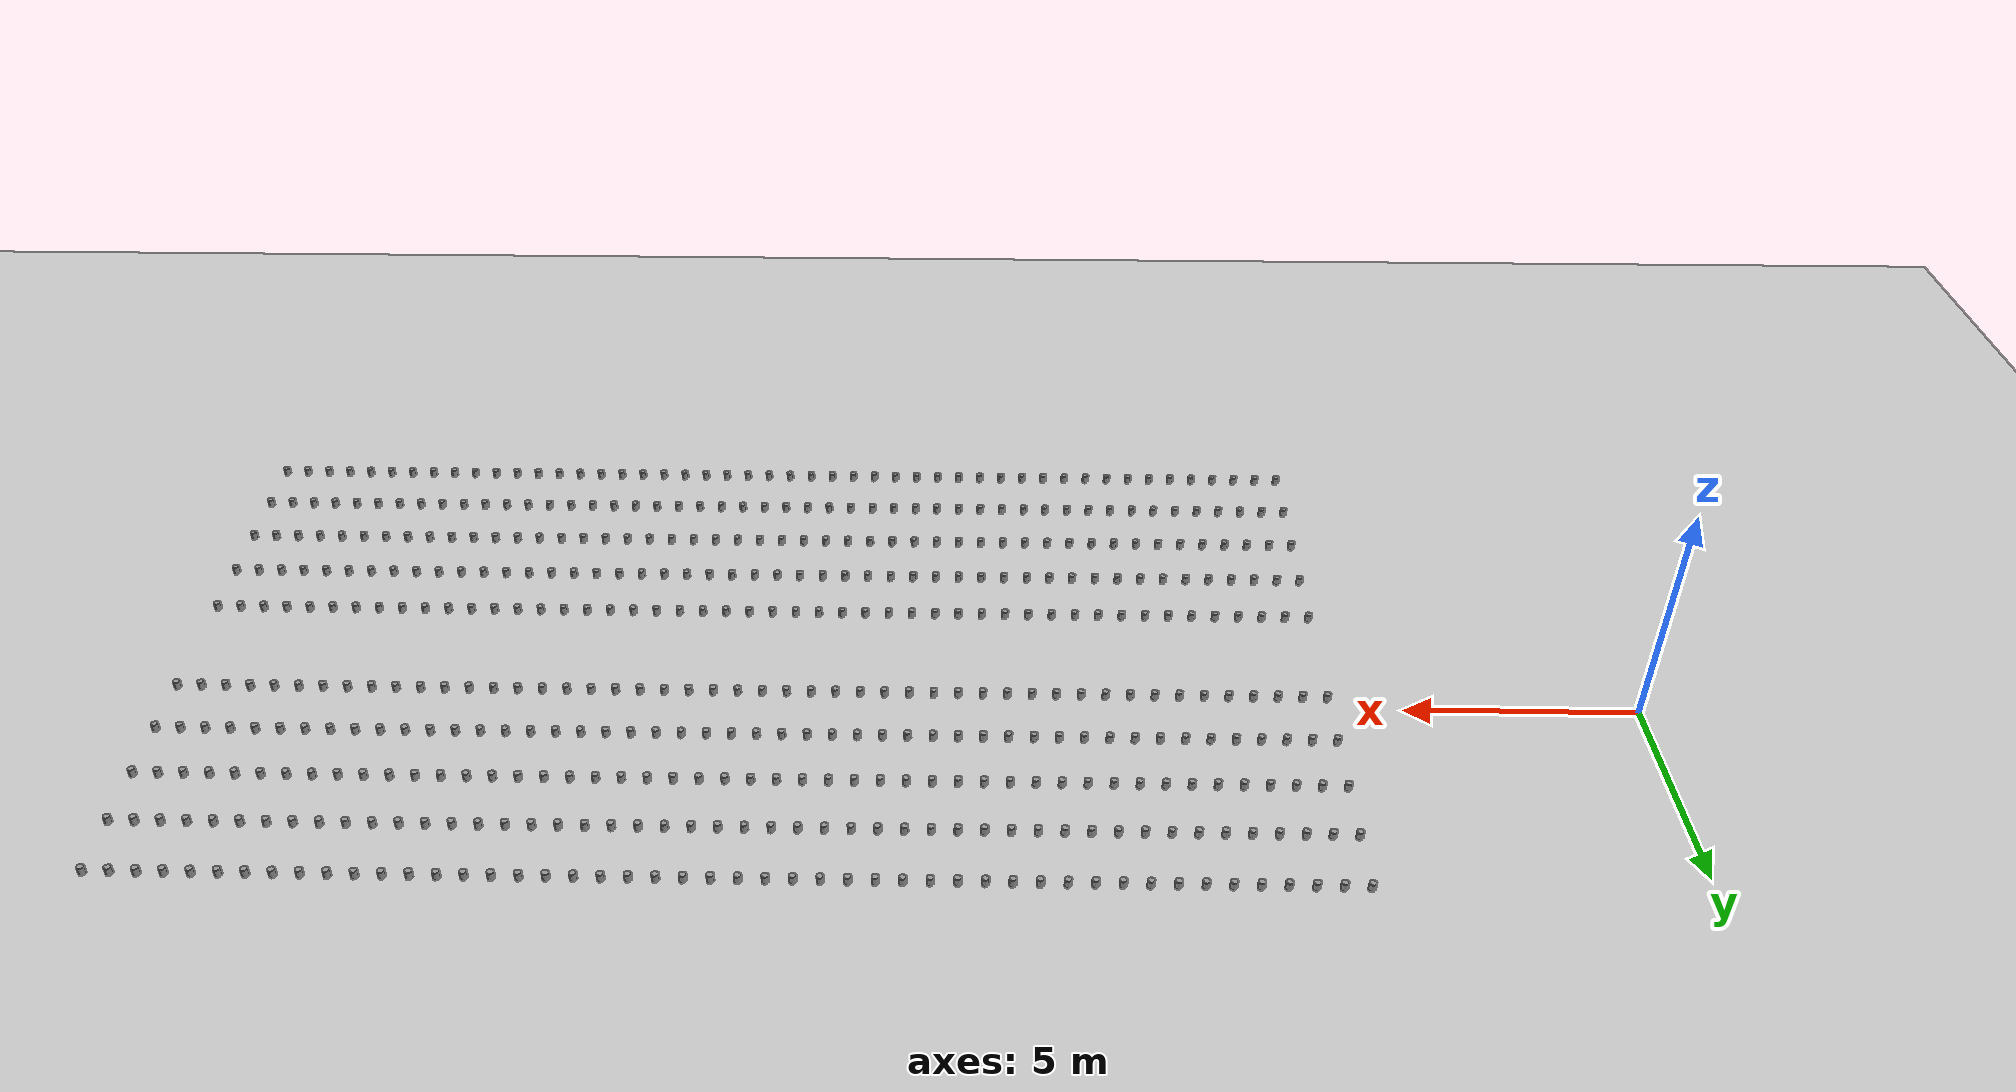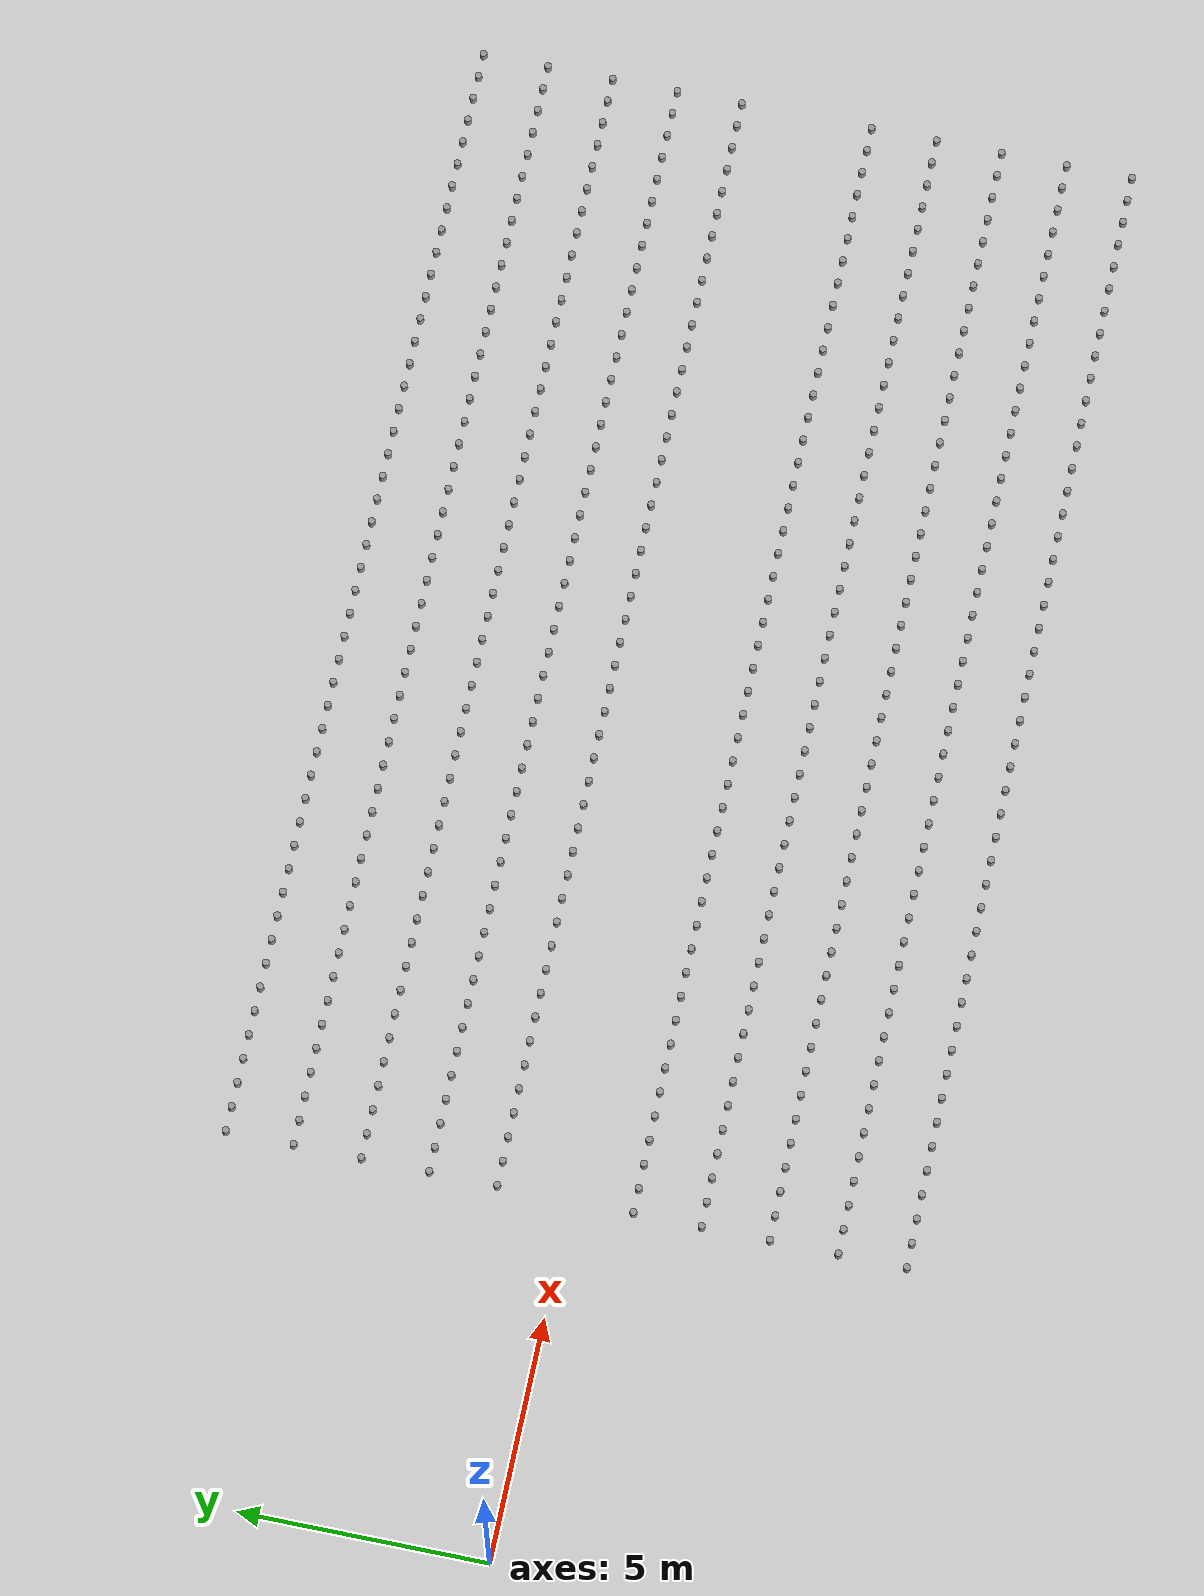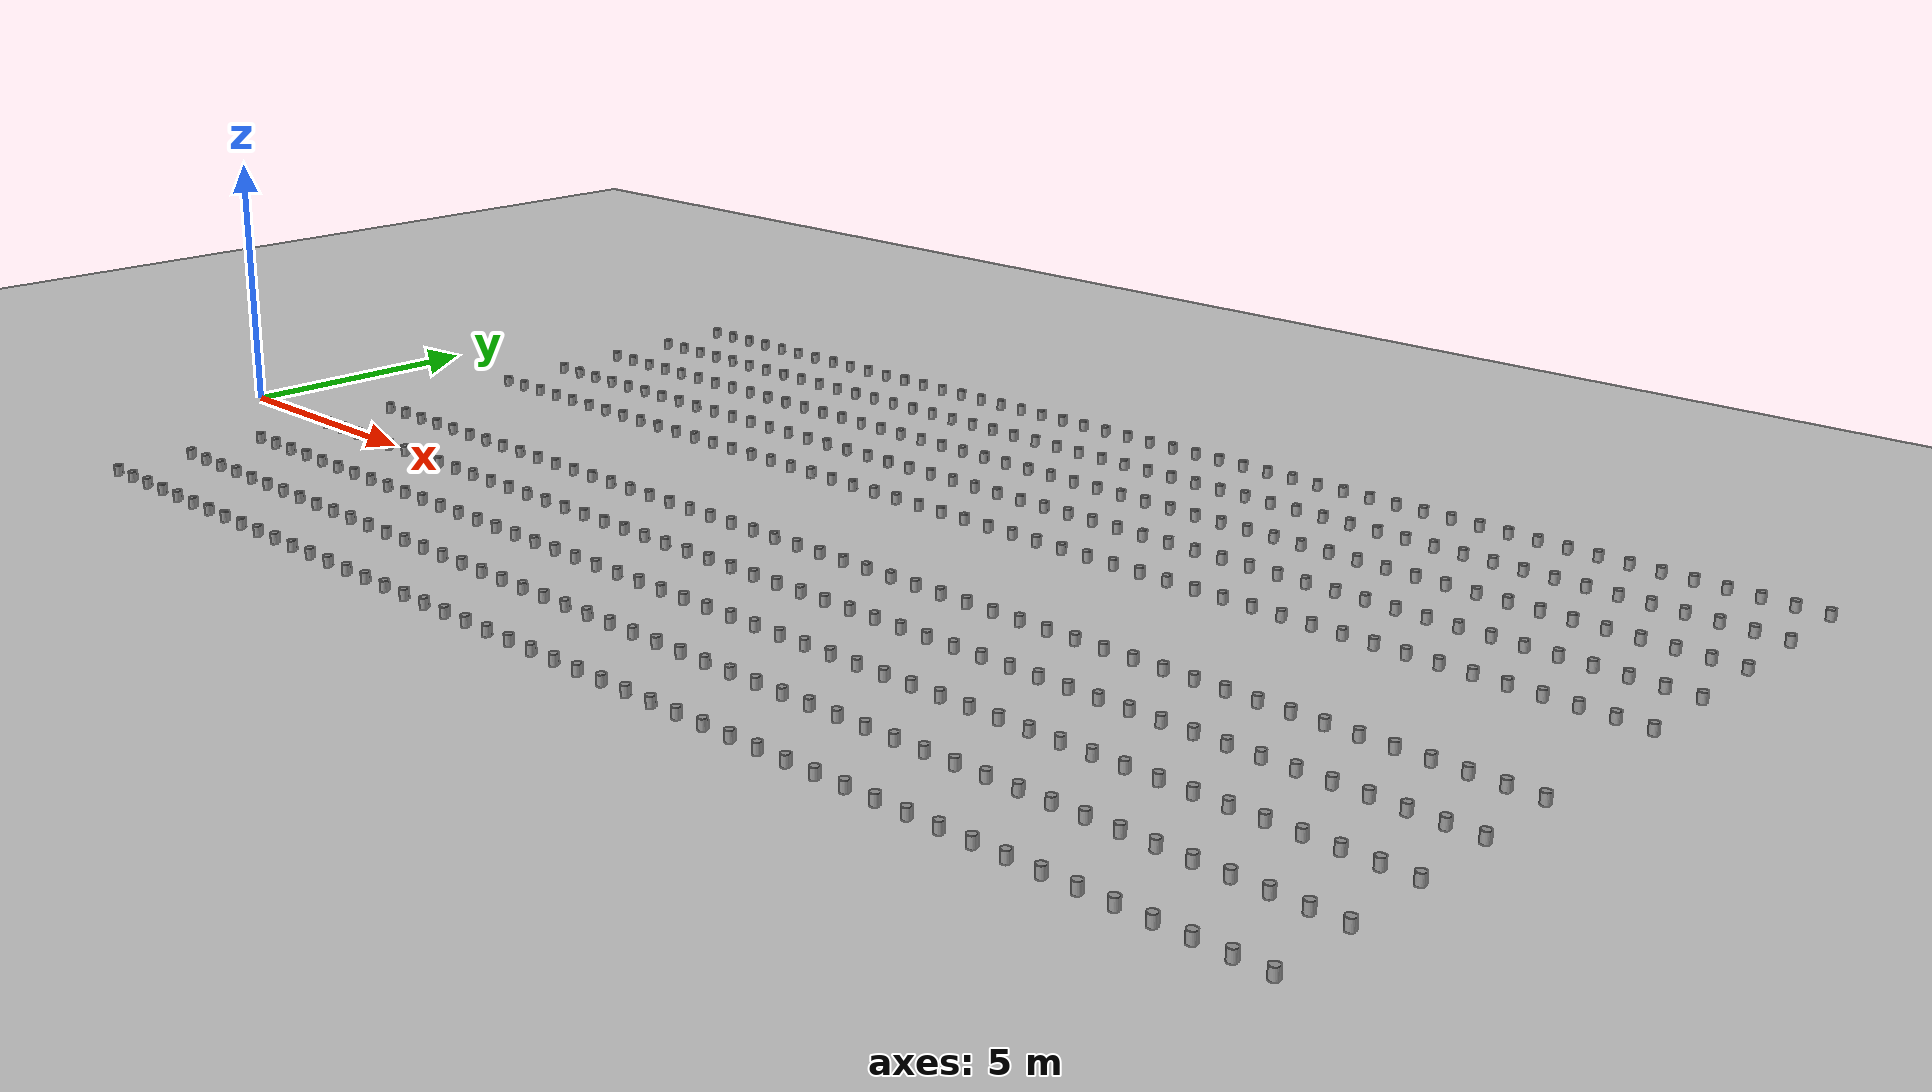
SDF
<sdf version="1.4">
 <world name="default">
  <model name="pot_0">
   <static>1</static>
   <link name="link_0">
    <collision name="collision">
     <geometry><cylinder><length>0.17</length><radius>0.07</radius></cylinder></geometry>
    </collision>
    <visual name="visual">
     <geometry><cylinder><length>0.17</length><radius>0.07</radius></cylinder></geometry>
     <material>
      <script><uri>file://media/materials/scripts/gazebo.material</uri><name>Gazebo/Grey</name></script>
      <emissive>0 0 0 1</emissive>
      <shader type="vertex"><normal_map>__default__</normal_map></shader>
      <specular>0.01 0.01 0.01 1</specular>
      <lighting>1</lighting>
      <ambient>0.1 0.1 0.1 1</ambient>
      <diffuse>0.05 0.05 0.05 1</diffuse>
     </material>
     <cast_shadows>0</cast_shadows>
    </visual>
    <pose>7.024 -6.750 1.467 0.0 0.0 0.0</pose>
   </link>
  </model>
  <model name="pot_1">
   <static>1</static>
   <link name="link_0">
    <collision name="collision">
     <geometry><cylinder><length>0.17</length><radius>0.07</radius></cylinder></geometry>
    </collision>
    <visual name="visual">
     <geometry><cylinder><length>0.17</length><radius>0.07</radius></cylinder></geometry>
     <material>
      <script><uri>file://media/materials/scripts/gazebo.material</uri><name>Gazebo/Grey</name></script>
      <emissive>0 0 0 1</emissive>
      <shader type="vertex"><normal_map>__default__</normal_map></shader>
      <specular>0.01 0.01 0.01 1</specular>
      <lighting>1</lighting>
      <ambient>0.1 0.1 0.1 1</ambient>
      <diffuse>0.05 0.05 0.05 1</diffuse>
     </material>
     <cast_shadows>0</cast_shadows>
    </visual>
    <pose>7.024 -5.400 1.467 0.0 0.0 0.0</pose>
   </link>
  </model>
  <model name="pot_2">
   <static>1</static>
   <link name="link_0">
    <collision name="collision">
     <geometry><cylinder><length>0.17</length><radius>0.07</radius></cylinder></geometry>
    </collision>
    <visual name="visual">
     <geometry><cylinder><length>0.17</length><radius>0.07</radius></cylinder></geometry>
     <material>
      <script><uri>file://media/materials/scripts/gazebo.material</uri><name>Gazebo/Grey</name></script>
      <emissive>0 0 0 1</emissive>
      <shader type="vertex"><normal_map>__default__</normal_map></shader>
      <specular>0.01 0.01 0.01 1</specular>
      <lighting>1</lighting>
      <ambient>0.1 0.1 0.1 1</ambient>
      <diffuse>0.05 0.05 0.05 1</diffuse>
     </material>
     <cast_shadows>0</cast_shadows>
    </visual>
    <pose>7.024 -4.050 1.467 0.0 0.0 0.0</pose>
   </link>
  </model>
  <model name="pot_3">
   <static>1</static>
   <link name="link_0">
    <collision name="collision">
     <geometry><cylinder><length>0.17</length><radius>0.07</radius></cylinder></geometry>
    </collision>
    <visual name="visual">
     <geometry><cylinder><length>0.17</length><radius>0.07</radius></cylinder></geometry>
     <material>
      <script><uri>file://media/materials/scripts/gazebo.material</uri><name>Gazebo/Grey</name></script>
      <emissive>0 0 0 1</emissive>
      <shader type="vertex"><normal_map>__default__</normal_map></shader>
      <specular>0.01 0.01 0.01 1</specular>
      <lighting>1</lighting>
      <ambient>0.1 0.1 0.1 1</ambient>
      <diffuse>0.05 0.05 0.05 1</diffuse>
     </material>
     <cast_shadows>0</cast_shadows>
    </visual>
    <pose>7.024 -2.700 1.467 0.0 0.0 0.0</pose>
   </link>
  </model>
  <model name="pot_4">
   <static>1</static>
   <link name="link_0">
    <collision name="collision">
     <geometry><cylinder><length>0.17</length><radius>0.07</radius></cylinder></geometry>
    </collision>
    <visual name="visual">
     <geometry><cylinder><length>0.17</length><radius>0.07</radius></cylinder></geometry>
     <material>
      <script><uri>file://media/materials/scripts/gazebo.material</uri><name>Gazebo/Grey</name></script>
      <emissive>0 0 0 1</emissive>
      <shader type="vertex"><normal_map>__default__</normal_map></shader>
      <specular>0.01 0.01 0.01 1</specular>
      <lighting>1</lighting>
      <ambient>0.1 0.1 0.1 1</ambient>
      <diffuse>0.05 0.05 0.05 1</diffuse>
     </material>
     <cast_shadows>0</cast_shadows>
    </visual>
    <pose>7.024 -1.350 1.467 0.0 0.0 0.0</pose>
   </link>
  </model>
  <model name="pot_5">
   <static>1</static>
   <link name="link_0">
    <collision name="collision">
     <geometry><cylinder><length>0.17</length><radius>0.07</radius></cylinder></geometry>
    </collision>
    <visual name="visual">
     <geometry><cylinder><length>0.17</length><radius>0.07</radius></cylinder></geometry>
     <material>
      <script><uri>file://media/materials/scripts/gazebo.material</uri><name>Gazebo/Grey</name></script>
      <emissive>0 0 0 1</emissive>
      <shader type="vertex"><normal_map>__default__</normal_map></shader>
      <specular>0.01 0.01 0.01 1</specular>
      <lighting>1</lighting>
      <ambient>0.1 0.1 0.1 1</ambient>
      <diffuse>0.05 0.05 0.05 1</diffuse>
     </material>
     <cast_shadows>0</cast_shadows>
    </visual>
    <pose>7.524 -6.750 1.467 0.0 0.0 0.0</pose>
   </link>
  </model>
  <model name="pot_6">
   <static>1</static>
   <link name="link_0">
    <collision name="collision">
     <geometry><cylinder><length>0.17</length><radius>0.07</radius></cylinder></geometry>
    </collision>
    <visual name="visual">
     <geometry><cylinder><length>0.17</length><radius>0.07</radius></cylinder></geometry>
     <material>
      <script><uri>file://media/materials/scripts/gazebo.material</uri><name>Gazebo/Grey</name></script>
      <emissive>0 0 0 1</emissive>
      <shader type="vertex"><normal_map>__default__</normal_map></shader>
      <specular>0.01 0.01 0.01 1</specular>
      <lighting>1</lighting>
      <ambient>0.1 0.1 0.1 1</ambient>
      <diffuse>0.05 0.05 0.05 1</diffuse>
     </material>
     <cast_shadows>0</cast_shadows>
    </visual>
    <pose>7.524 -5.400 1.467 0.0 0.0 0.0</pose>
   </link>
  </model>
  <model name="pot_7">
   <static>1</static>
   <link name="link_0">
    <collision name="collision">
     <geometry><cylinder><length>0.17</length><radius>0.07</radius></cylinder></geometry>
    </collision>
    <visual name="visual">
     <geometry><cylinder><length>0.17</length><radius>0.07</radius></cylinder></geometry>
     <material>
      <script><uri>file://media/materials/scripts/gazebo.material</uri><name>Gazebo/Grey</name></script>
      <emissive>0 0 0 1</emissive>
      <shader type="vertex"><normal_map>__default__</normal_map></shader>
      <specular>0.01 0.01 0.01 1</specular>
      <lighting>1</lighting>
      <ambient>0.1 0.1 0.1 1</ambient>
      <diffuse>0.05 0.05 0.05 1</diffuse>
     </material>
     <cast_shadows>0</cast_shadows>
    </visual>
    <pose>7.524 -4.050 1.467 0.0 0.0 0.0</pose>
   </link>
  </model>
  <model name="pot_8">
   <static>1</static>
   <link name="link_0">
    <collision name="collision">
     <geometry><cylinder><length>0.17</length><radius>0.07</radius></cylinder></geometry>
    </collision>
    <visual name="visual">
     <geometry><cylinder><length>0.17</length><radius>0.07</radius></cylinder></geometry>
     <material>
      <script><uri>file://media/materials/scripts/gazebo.material</uri><name>Gazebo/Grey</name></script>
      <emissive>0 0 0 1</emissive>
      <shader type="vertex"><normal_map>__default__</normal_map></shader>
      <specular>0.01 0.01 0.01 1</specular>
      <lighting>1</lighting>
      <ambient>0.1 0.1 0.1 1</ambient>
      <diffuse>0.05 0.05 0.05 1</diffuse>
     </material>
     <cast_shadows>0</cast_shadows>
    </visual>
    <pose>7.524 -2.700 1.467 0.0 0.0 0.0</pose>
   </link>
  </model>
  <model name="pot_9">
   <static>1</static>
   <link name="link_0">
    <collision name="collision">
     <geometry><cylinder><length>0.17</length><radius>0.07</radius></cylinder></geometry>
    </collision>
    <visual name="visual">
     <geometry><cylinder><length>0.17</length><radius>0.07</radius></cylinder></geometry>
     <material>
      <script><uri>file://media/materials/scripts/gazebo.material</uri><name>Gazebo/Grey</name></script>
      <emissive>0 0 0 1</emissive>
      <shader type="vertex"><normal_map>__default__</normal_map></shader>
      <specular>0.01 0.01 0.01 1</specular>
      <lighting>1</lighting>
      <ambient>0.1 0.1 0.1 1</ambient>
      <diffuse>0.05 0.05 0.05 1</diffuse>
     </material>
     <cast_shadows>0</cast_shadows>
    </visual>
    <pose>7.524 -1.350 1.467 0.0 0.0 0.0</pose>
   </link>
  </model>
  <model name="pot_10">
   <static>1</static>
   <link name="link_0">
    <collision name="collision">
     <geometry><cylinder><length>0.17</length><radius>0.07</radius></cylinder></geometry>
    </collision>
    <visual name="visual">
     <geometry><cylinder><length>0.17</length><radius>0.07</radius></cylinder></geometry>
     <material>
      <script><uri>file://media/materials/scripts/gazebo.material</uri><name>Gazebo/Grey</name></script>
      <emissive>0 0 0 1</emissive>
      <shader type="vertex"><normal_map>__default__</normal_map></shader>
      <specular>0.01 0.01 0.01 1</specular>
      <lighting>1</lighting>
      <ambient>0.1 0.1 0.1 1</ambient>
      <diffuse>0.05 0.05 0.05 1</diffuse>
     </material>
     <cast_shadows>0</cast_shadows>
    </visual>
    <pose>8.024 -6.750 1.467 0.0 0.0 0.0</pose>
   </link>
  </model>
  <model name="pot_11">
   <static>1</static>
   <link name="link_0">
    <collision name="collision">
     <geometry><cylinder><length>0.17</length><radius>0.07</radius></cylinder></geometry>
    </collision>
    <visual name="visual">
     <geometry><cylinder><length>0.17</length><radius>0.07</radius></cylinder></geometry>
     <material>
      <script><uri>file://media/materials/scripts/gazebo.material</uri><name>Gazebo/Grey</name></script>
      <emissive>0 0 0 1</emissive>
      <shader type="vertex"><normal_map>__default__</normal_map></shader>
      <specular>0.01 0.01 0.01 1</specular>
      <lighting>1</lighting>
      <ambient>0.1 0.1 0.1 1</ambient>
      <diffuse>0.05 0.05 0.05 1</diffuse>
     </material>
     <cast_shadows>0</cast_shadows>
    </visual>
    <pose>8.024 -5.400 1.467 0.0 0.0 0.0</pose>
   </link>
  </model>
  <model name="pot_12">
   <static>1</static>
   <link name="link_0">
    <collision name="collision">
     <geometry><cylinder><length>0.17</length><radius>0.07</radius></cylinder></geometry>
    </collision>
    <visual name="visual">
     <geometry><cylinder><length>0.17</length><radius>0.07</radius></cylinder></geometry>
     <material>
      <script><uri>file://media/materials/scripts/gazebo.material</uri><name>Gazebo/Grey</name></script>
      <emissive>0 0 0 1</emissive>
      <shader type="vertex"><normal_map>__default__</normal_map></shader>
      <specular>0.01 0.01 0.01 1</specular>
      <lighting>1</lighting>
      <ambient>0.1 0.1 0.1 1</ambient>
      <diffuse>0.05 0.05 0.05 1</diffuse>
     </material>
     <cast_shadows>0</cast_shadows>
    </visual>
    <pose>8.024 -4.050 1.467 0.0 0.0 0.0</pose>
   </link>
  </model>
  <model name="pot_13">
   <static>1</static>
   <link name="link_0">
    <collision name="collision">
     <geometry><cylinder><length>0.17</length><radius>0.07</radius></cylinder></geometry>
    </collision>
    <visual name="visual">
     <geometry><cylinder><length>0.17</length><radius>0.07</radius></cylinder></geometry>
     <material>
      <script><uri>file://media/materials/scripts/gazebo.material</uri><name>Gazebo/Grey</name></script>
      <emissive>0 0 0 1</emissive>
      <shader type="vertex"><normal_map>__default__</normal_map></shader>
      <specular>0.01 0.01 0.01 1</specular>
      <lighting>1</lighting>
      <ambient>0.1 0.1 0.1 1</ambient>
      <diffuse>0.05 0.05 0.05 1</diffuse>
     </material>
     <cast_shadows>0</cast_shadows>
    </visual>
    <pose>8.024 -2.700 1.467 0.0 0.0 0.0</pose>
   </link>
  </model>
  <model name="pot_14">
   <static>1</static>
   <link name="link_0">
    <collision name="collision">
     <geometry><cylinder><length>0.17</length><radius>0.07</radius></cylinder></geometry>
    </collision>
    <visual name="visual">
     <geometry><cylinder><length>0.17</length><radius>0.07</radius></cylinder></geometry>
     <material>
      <script><uri>file://media/materials/scripts/gazebo.material</uri><name>Gazebo/Grey</name></script>
      <emissive>0 0 0 1</emissive>
      <shader type="vertex"><normal_map>__default__</normal_map></shader>
      <specular>0.01 0.01 0.01 1</specular>
      <lighting>1</lighting>
      <ambient>0.1 0.1 0.1 1</ambient>
      <diffuse>0.05 0.05 0.05 1</diffuse>
     </material>
     <cast_shadows>0</cast_shadows>
    </visual>
    <pose>8.024 -1.350 1.467 0.0 0.0 0.0</pose>
   </link>
  </model>
  <model name="pot_15">
   <static>1</static>
   <link name="link_0">
    <collision name="collision">
     <geometry><cylinder><length>0.17</length><radius>0.07</radius></cylinder></geometry>
    </collision>
    <visual name="visual">
     <geometry><cylinder><length>0.17</length><radius>0.07</radius></cylinder></geometry>
     <material>
      <script><uri>file://media/materials/scripts/gazebo.material</uri><name>Gazebo/Grey</name></script>
      <emissive>0 0 0 1</emissive>
      <shader type="vertex"><normal_map>__default__</normal_map></shader>
      <specular>0.01 0.01 0.01 1</specular>
      <lighting>1</lighting>
      <ambient>0.1 0.1 0.1 1</ambient>
      <diffuse>0.05 0.05 0.05 1</diffuse>
     </material>
     <cast_shadows>0</cast_shadows>
    </visual>
    <pose>8.524 -6.750 1.467 0.0 0.0 0.0</pose>
   </link>
  </model>
  <model name="pot_16">
   <static>1</static>
   <link name="link_0">
    <collision name="collision">
     <geometry><cylinder><length>0.17</length><radius>0.07</radius></cylinder></geometry>
    </collision>
    <visual name="visual">
     <geometry><cylinder><length>0.17</length><radius>0.07</radius></cylinder></geometry>
     <material>
      <script><uri>file://media/materials/scripts/gazebo.material</uri><name>Gazebo/Grey</name></script>
      <emissive>0 0 0 1</emissive>
      <shader type="vertex"><normal_map>__default__</normal_map></shader>
      <specular>0.01 0.01 0.01 1</specular>
      <lighting>1</lighting>
      <ambient>0.1 0.1 0.1 1</ambient>
      <diffuse>0.05 0.05 0.05 1</diffuse>
     </material>
     <cast_shadows>0</cast_shadows>
    </visual>
    <pose>8.524 -5.400 1.467 0.0 0.0 0.0</pose>
   </link>
  </model>
  <model name="pot_17">
   <static>1</static>
   <link name="link_0">
    <collision name="collision">
     <geometry><cylinder><length>0.17</length><radius>0.07</radius></cylinder></geometry>
    </collision>
    <visual name="visual">
     <geometry><cylinder><length>0.17</length><radius>0.07</radius></cylinder></geometry>
     <material>
      <script><uri>file://media/materials/scripts/gazebo.material</uri><name>Gazebo/Grey</name></script>
      <emissive>0 0 0 1</emissive>
      <shader type="vertex"><normal_map>__default__</normal_map></shader>
      <specular>0.01 0.01 0.01 1</specular>
      <lighting>1</lighting>
      <ambient>0.1 0.1 0.1 1</ambient>
      <diffuse>0.05 0.05 0.05 1</diffuse>
     </material>
     <cast_shadows>0</cast_shadows>
    </visual>
    <pose>8.524 -4.050 1.467 0.0 0.0 0.0</pose>
   </link>
  </model>
  <model name="pot_18">
   <static>1</static>
   <link name="link_0">
    <collision name="collision">
     <geometry><cylinder><length>0.17</length><radius>0.07</radius></cylinder></geometry>
    </collision>
    <visual name="visual">
     <geometry><cylinder><length>0.17</length><radius>0.07</radius></cylinder></geometry>
     <material>
      <script><uri>file://media/materials/scripts/gazebo.material</uri><name>Gazebo/Grey</name></script>
      <emissive>0 0 0 1</emissive>
      <shader type="vertex"><normal_map>__default__</normal_map></shader>
      <specular>0.01 0.01 0.01 1</specular>
      <lighting>1</lighting>
      <ambient>0.1 0.1 0.1 1</ambient>
      <diffuse>0.05 0.05 0.05 1</diffuse>
     </material>
     <cast_shadows>0</cast_shadows>
    </visual>
    <pose>8.524 -2.700 1.467 0.0 0.0 0.0</pose>
   </link>
  </model>
  <model name="pot_19">
   <static>1</static>
   <link name="link_0">
    <collision name="collision">
     <geometry><cylinder><length>0.17</length><radius>0.07</radius></cylinder></geometry>
    </collision>
    <visual name="visual">
     <geometry><cylinder><length>0.17</length><radius>0.07</radius></cylinder></geometry>
     <material>
      <script><uri>file://media/materials/scripts/gazebo.material</uri><name>Gazebo/Grey</name></script>
      <emissive>0 0 0 1</emissive>
      <shader type="vertex"><normal_map>__default__</normal_map></shader>
      <specular>0.01 0.01 0.01 1</specular>
      <lighting>1</lighting>
      <ambient>0.1 0.1 0.1 1</ambient>
      <diffuse>0.05 0.05 0.05 1</diffuse>
     </material>
     <cast_shadows>0</cast_shadows>
    </visual>
    <pose>8.524 -1.350 1.467 0.0 0.0 0.0</pose>
   </link>
  </model>
  <model name="pot_20">
   <static>1</static>
   <link name="link_0">
    <collision name="collision">
     <geometry><cylinder><length>0.17</length><radius>0.07</radius></cylinder></geometry>
    </collision>
    <visual name="visual">
     <geometry><cylinder><length>0.17</length><radius>0.07</radius></cylinder></geometry>
     <material>
      <script><uri>file://media/materials/scripts/gazebo.material</uri><name>Gazebo/Grey</name></script>
      <emissive>0 0 0 1</emissive>
      <shader type="vertex"><normal_map>__default__</normal_map></shader>
      <specular>0.01 0.01 0.01 1</specular>
      <lighting>1</lighting>
      <ambient>0.1 0.1 0.1 1</ambient>
      <diffuse>0.05 0.05 0.05 1</diffuse>
     </material>
     <cast_shadows>0</cast_shadows>
    </visual>
    <pose>9.024 -6.750 1.467 0.0 0.0 0.0</pose>
   </link>
  </model>
  <model name="pot_21">
   <static>1</static>
   <link name="link_0">
    <collision name="collision">
     <geometry><cylinder><length>0.17</length><radius>0.07</radius></cylinder></geometry>
    </collision>
    <visual name="visual">
     <geometry><cylinder><length>0.17</length><radius>0.07</radius></cylinder></geometry>
     <material>
      <script><uri>file://media/materials/scripts/gazebo.material</uri><name>Gazebo/Grey</name></script>
      <emissive>0 0 0 1</emissive>
      <shader type="vertex"><normal_map>__default__</normal_map></shader>
      <specular>0.01 0.01 0.01 1</specular>
      <lighting>1</lighting>
      <ambient>0.1 0.1 0.1 1</ambient>
      <diffuse>0.05 0.05 0.05 1</diffuse>
     </material>
     <cast_shadows>0</cast_shadows>
    </visual>
    <pose>9.024 -5.400 1.467 0.0 0.0 0.0</pose>
   </link>
  </model>
  <model name="pot_22">
   <static>1</static>
   <link name="link_0">
    <collision name="collision">
     <geometry><cylinder><length>0.17</length><radius>0.07</radius></cylinder></geometry>
    </collision>
    <visual name="visual">
     <geometry><cylinder><length>0.17</length><radius>0.07</radius></cylinder></geometry>
     <material>
      <script><uri>file://media/materials/scripts/gazebo.material</uri><name>Gazebo/Grey</name></script>
      <emissive>0 0 0 1</emissive>
      <shader type="vertex"><normal_map>__default__</normal_map></shader>
      <specular>0.01 0.01 0.01 1</specular>
      <lighting>1</lighting>
      <ambient>0.1 0.1 0.1 1</ambient>
      <diffuse>0.05 0.05 0.05 1</diffuse>
     </material>
     <cast_shadows>0</cast_shadows>
    </visual>
    <pose>9.024 -4.050 1.467 0.0 0.0 0.0</pose>
   </link>
  </model>
  <model name="pot_23">
   <static>1</static>
   <link name="link_0">
    <collision name="collision">
     <geometry><cylinder><length>0.17</length><radius>0.07</radius></cylinder></geometry>
    </collision>
    <visual name="visual">
     <geometry><cylinder><length>0.17</length><radius>0.07</radius></cylinder></geometry>
     <material>
      <script><uri>file://media/materials/scripts/gazebo.material</uri><name>Gazebo/Grey</name></script>
      <emissive>0 0 0 1</emissive>
      <shader type="vertex"><normal_map>__default__</normal_map></shader>
      <specular>0.01 0.01 0.01 1</specular>
      <lighting>1</lighting>
      <ambient>0.1 0.1 0.1 1</ambient>
      <diffuse>0.05 0.05 0.05 1</diffuse>
     </material>
     <cast_shadows>0</cast_shadows>
    </visual>
    <pose>9.024 -2.700 1.467 0.0 0.0 0.0</pose>
   </link>
  </model>
  <model name="pot_24">
   <static>1</static>
   <link name="link_0">
    <collision name="collision">
     <geometry><cylinder><length>0.17</length><radius>0.07</radius></cylinder></geometry>
    </collision>
    <visual name="visual">
     <geometry><cylinder><length>0.17</length><radius>0.07</radius></cylinder></geometry>
     <material>
      <script><uri>file://media/materials/scripts/gazebo.material</uri><name>Gazebo/Grey</name></script>
      <emissive>0 0 0 1</emissive>
      <shader type="vertex"><normal_map>__default__</normal_map></shader>
      <specular>0.01 0.01 0.01 1</specular>
      <lighting>1</lighting>
      <ambient>0.1 0.1 0.1 1</ambient>
      <diffuse>0.05 0.05 0.05 1</diffuse>
     </material>
     <cast_shadows>0</cast_shadows>
    </visual>
    <pose>9.024 -1.350 1.467 0.0 0.0 0.0</pose>
   </link>
  </model>
  <model name="pot_25">
   <static>1</static>
   <link name="link_0">
    <collision name="collision">
     <geometry><cylinder><length>0.17</length><radius>0.07</radius></cylinder></geometry>
    </collision>
    <visual name="visual">
     <geometry><cylinder><length>0.17</length><radius>0.07</radius></cylinder></geometry>
     <material>
      <script><uri>file://media/materials/scripts/gazebo.material</uri><name>Gazebo/Grey</name></script>
      <emissive>0 0 0 1</emissive>
      <shader type="vertex"><normal_map>__default__</normal_map></shader>
      <specular>0.01 0.01 0.01 1</specular>
      <lighting>1</lighting>
      <ambient>0.1 0.1 0.1 1</ambient>
      <diffuse>0.05 0.05 0.05 1</diffuse>
     </material>
     <cast_shadows>0</cast_shadows>
    </visual>
    <pose>9.524 -6.750 1.467 0.0 0.0 0.0</pose>
   </link>
  </model>
  <model name="pot_26">
   <static>1</static>
   <link name="link_0">
    <collision name="collision">
     <geometry><cylinder><length>0.17</length><radius>0.07</radius></cylinder></geometry>
    </collision>
    <visual name="visual">
     <geometry><cylinder><length>0.17</length><radius>0.07</radius></cylinder></geometry>
     <material>
      <script><uri>file://media/materials/scripts/gazebo.material</uri><name>Gazebo/Grey</name></script>
      <emissive>0 0 0 1</emissive>
      <shader type="vertex"><normal_map>__default__</normal_map></shader>
      <specular>0.01 0.01 0.01 1</specular>
      <lighting>1</lighting>
      <ambient>0.1 0.1 0.1 1</ambient>
      <diffuse>0.05 0.05 0.05 1</diffuse>
     </material>
     <cast_shadows>0</cast_shadows>
    </visual>
    <pose>9.524 -5.400 1.467 0.0 0.0 0.0</pose>
   </link>
  </model>
  <model name="pot_27">
   <static>1</static>
   <link name="link_0">
    <collision name="collision">
     <geometry><cylinder><length>0.17</length><radius>0.07</radius></cylinder></geometry>
    </collision>
    <visual name="visual">
     <geometry><cylinder><length>0.17</length><radius>0.07</radius></cylinder></geometry>
     <material>
      <script><uri>file://media/materials/scripts/gazebo.material</uri><name>Gazebo/Grey</name></script>
      <emissive>0 0 0 1</emissive>
      <shader type="vertex"><normal_map>__default__</normal_map></shader>
      <specular>0.01 0.01 0.01 1</specular>
      <lighting>1</lighting>
      <ambient>0.1 0.1 0.1 1</ambient>
      <diffuse>0.05 0.05 0.05 1</diffuse>
     </material>
     <cast_shadows>0</cast_shadows>
    </visual>
    <pose>9.524 -4.050 1.467 0.0 0.0 0.0</pose>
   </link>
  </model>
  <model name="pot_28">
   <static>1</static>
   <link name="link_0">
    <collision name="collision">
     <geometry><cylinder><length>0.17</length><radius>0.07</radius></cylinder></geometry>
    </collision>
    <visual name="visual">
     <geometry><cylinder><length>0.17</length><radius>0.07</radius></cylinder></geometry>
     <material>
      <script><uri>file://media/materials/scripts/gazebo.material</uri><name>Gazebo/Grey</name></script>
      <emissive>0 0 0 1</emissive>
      <shader type="vertex"><normal_map>__default__</normal_map></shader>
      <specular>0.01 0.01 0.01 1</specular>
      <lighting>1</lighting>
      <ambient>0.1 0.1 0.1 1</ambient>
      <diffuse>0.05 0.05 0.05 1</diffuse>
     </material>
     <cast_shadows>0</cast_shadows>
    </visual>
    <pose>9.524 -2.700 1.467 0.0 0.0 0.0</pose>
   </link>
  </model>
  <model name="pot_29">
   <static>1</static>
   <link name="link_0">
    <collision name="collision">
     <geometry><cylinder><length>0.17</length><radius>0.07</radius></cylinder></geometry>
    </collision>
    <visual name="visual">
     <geometry><cylinder><length>0.17</length><radius>0.07</radius></cylinder></geometry>
     <material>
      <script><uri>file://media/materials/scripts/gazebo.material</uri><name>Gazebo/Grey</name></script>
      <emissive>0 0 0 1</emissive>
      <shader type="vertex"><normal_map>__default__</normal_map></shader>
      <specular>0.01 0.01 0.01 1</specular>
      <lighting>1</lighting>
      <ambient>0.1 0.1 0.1 1</ambient>
      <diffuse>0.05 0.05 0.05 1</diffuse>
     </material>
     <cast_shadows>0</cast_shadows>
    </visual>
    <pose>9.524 -1.350 1.467 0.0 0.0 0.0</pose>
   </link>
  </model>
  <model name="pot_30">
   <static>1</static>
   <link name="link_0">
    <collision name="collision">
     <geometry><cylinder><length>0.17</length><radius>0.07</radius></cylinder></geometry>
    </collision>
    <visual name="visual">
     <geometry><cylinder><length>0.17</length><radius>0.07</radius></cylinder></geometry>
     <material>
      <script><uri>file://media/materials/scripts/gazebo.material</uri><name>Gazebo/Grey</name></script>
      <emissive>0 0 0 1</emissive>
      <shader type="vertex"><normal_map>__default__</normal_map></shader>
      <specular>0.01 0.01 0.01 1</specular>
      <lighting>1</lighting>
      <ambient>0.1 0.1 0.1 1</ambient>
      <diffuse>0.05 0.05 0.05 1</diffuse>
     </material>
     <cast_shadows>0</cast_shadows>
    </visual>
    <pose>10.024 -6.750 1.467 0.0 0.0 0.0</pose>
   </link>
  </model>
  <model name="pot_31">
   <static>1</static>
   <link name="link_0">
    <collision name="collision">
     <geometry><cylinder><length>0.17</length><radius>0.07</radius></cylinder></geometry>
    </collision>
    <visual name="visual">
     <geometry><cylinder><length>0.17</length><radius>0.07</radius></cylinder></geometry>
     <material>
      <script><uri>file://media/materials/scripts/gazebo.material</uri><name>Gazebo/Grey</name></script>
      <emissive>0 0 0 1</emissive>
      <shader type="vertex"><normal_map>__default__</normal_map></shader>
      <specular>0.01 0.01 0.01 1</specular>
      <lighting>1</lighting>
      <ambient>0.1 0.1 0.1 1</ambient>
      <diffuse>0.05 0.05 0.05 1</diffuse>
     </material>
     <cast_shadows>0</cast_shadows>
    </visual>
    <pose>10.024 -5.400 1.467 0.0 0.0 0.0</pose>
   </link>
  </model>
  <model name="pot_32">
   <static>1</static>
   <link name="link_0">
    <collision name="collision">
     <geometry><cylinder><length>0.17</length><radius>0.07</radius></cylinder></geometry>
    </collision>
    <visual name="visual">
     <geometry><cylinder><length>0.17</length><radius>0.07</radius></cylinder></geometry>
     <material>
      <script><uri>file://media/materials/scripts/gazebo.material</uri><name>Gazebo/Grey</name></script>
      <emissive>0 0 0 1</emissive>
      <shader type="vertex"><normal_map>__default__</normal_map></shader>
      <specular>0.01 0.01 0.01 1</specular>
      <lighting>1</lighting>
      <ambient>0.1 0.1 0.1 1</ambient>
      <diffuse>0.05 0.05 0.05 1</diffuse>
     </material>
     <cast_shadows>0</cast_shadows>
    </visual>
    <pose>10.024 -4.050 1.467 0.0 0.0 0.0</pose>
   </link>
  </model>
  <model name="pot_33">
   <static>1</static>
   <link name="link_0">
    <collision name="collision">
     <geometry><cylinder><length>0.17</length><radius>0.07</radius></cylinder></geometry>
    </collision>
    <visual name="visual">
     <geometry><cylinder><length>0.17</length><radius>0.07</radius></cylinder></geometry>
     <material>
      <script><uri>file://media/materials/scripts/gazebo.material</uri><name>Gazebo/Grey</name></script>
      <emissive>0 0 0 1</emissive>
      <shader type="vertex"><normal_map>__default__</normal_map></shader>
      <specular>0.01 0.01 0.01 1</specular>
      <lighting>1</lighting>
      <ambient>0.1 0.1 0.1 1</ambient>
      <diffuse>0.05 0.05 0.05 1</diffuse>
     </material>
     <cast_shadows>0</cast_shadows>
    </visual>
    <pose>10.024 -2.700 1.467 0.0 0.0 0.0</pose>
   </link>
  </model>
  <model name="pot_34">
   <static>1</static>
   <link name="link_0">
    <collision name="collision">
     <geometry><cylinder><length>0.17</length><radius>0.07</radius></cylinder></geometry>
    </collision>
    <visual name="visual">
     <geometry><cylinder><length>0.17</length><radius>0.07</radius></cylinder></geometry>
     <material>
      <script><uri>file://media/materials/scripts/gazebo.material</uri><name>Gazebo/Grey</name></script>
      <emissive>0 0 0 1</emissive>
      <shader type="vertex"><normal_map>__default__</normal_map></shader>
      <specular>0.01 0.01 0.01 1</specular>
      <lighting>1</lighting>
      <ambient>0.1 0.1 0.1 1</ambient>
      <diffuse>0.05 0.05 0.05 1</diffuse>
     </material>
     <cast_shadows>0</cast_shadows>
    </visual>
    <pose>10.024 -1.350 1.467 0.0 0.0 0.0</pose>
   </link>
  </model>
  <model name="pot_35">
   <static>1</static>
   <link name="link_0">
    <collision name="collision">
     <geometry><cylinder><length>0.17</length><radius>0.07</radius></cylinder></geometry>
    </collision>
    <visual name="visual">
     <geometry><cylinder><length>0.17</length><radius>0.07</radius></cylinder></geometry>
     <material>
      <script><uri>file://media/materials/scripts/gazebo.material</uri><name>Gazebo/Grey</name></script>
      <emissive>0 0 0 1</emissive>
      <shader type="vertex"><normal_map>__default__</normal_map></shader>
      <specular>0.01 0.01 0.01 1</specular>
      <lighting>1</lighting>
      <ambient>0.1 0.1 0.1 1</ambient>
      <diffuse>0.05 0.05 0.05 1</diffuse>
     </material>
     <cast_shadows>0</cast_shadows>
    </visual>
    <pose>10.524 -6.750 1.467 0.0 0.0 0.0</pose>
   </link>
  </model>
  <model name="pot_36">
   <static>1</static>
   <link name="link_0">
    <collision name="collision">
     <geometry><cylinder><length>0.17</length><radius>0.07</radius></cylinder></geometry>
    </collision>
    <visual name="visual">
     <geometry><cylinder><length>0.17</length><radius>0.07</radius></cylinder></geometry>
     <material>
      <script><uri>file://media/materials/scripts/gazebo.material</uri><name>Gazebo/Grey</name></script>
      <emissive>0 0 0 1</emissive>
      <shader type="vertex"><normal_map>__default__</normal_map></shader>
      <specular>0.01 0.01 0.01 1</specular>
      <lighting>1</lighting>
      <ambient>0.1 0.1 0.1 1</ambient>
      <diffuse>0.05 0.05 0.05 1</diffuse>
     </material>
     <cast_shadows>0</cast_shadows>
    </visual>
    <pose>10.524 -5.400 1.467 0.0 0.0 0.0</pose>
   </link>
  </model>
  <model name="pot_37">
   <static>1</static>
   <link name="link_0">
    <collision name="collision">
     <geometry><cylinder><length>0.17</length><radius>0.07</radius></cylinder></geometry>
    </collision>
    <visual name="visual">
     <geometry><cylinder><length>0.17</length><radius>0.07</radius></cylinder></geometry>
     <material>
      <script><uri>file://media/materials/scripts/gazebo.material</uri><name>Gazebo/Grey</name></script>
      <emissive>0 0 0 1</emissive>
      <shader type="vertex"><normal_map>__default__</normal_map></shader>
      <specular>0.01 0.01 0.01 1</specular>
      <lighting>1</lighting>
      <ambient>0.1 0.1 0.1 1</ambient>
      <diffuse>0.05 0.05 0.05 1</diffuse>
     </material>
     <cast_shadows>0</cast_shadows>
    </visual>
    <pose>10.524 -4.050 1.467 0.0 0.0 0.0</pose>
   </link>
  </model>
  <model name="pot_38">
   <static>1</static>
   <link name="link_0">
    <collision name="collision">
     <geometry><cylinder><length>0.17</length><radius>0.07</radius></cylinder></geometry>
    </collision>
    <visual name="visual">
     <geometry><cylinder><length>0.17</length><radius>0.07</radius></cylinder></geometry>
     <material>
      <script><uri>file://media/materials/scripts/gazebo.material</uri><name>Gazebo/Grey</name></script>
      <emissive>0 0 0 1</emissive>
      <shader type="vertex"><normal_map>__default__</normal_map></shader>
      <specular>0.01 0.01 0.01 1</specular>
      <lighting>1</lighting>
      <ambient>0.1 0.1 0.1 1</ambient>
      <diffuse>0.05 0.05 0.05 1</diffuse>
     </material>
     <cast_shadows>0</cast_shadows>
    </visual>
    <pose>10.524 -2.700 1.467 0.0 0.0 0.0</pose>
   </link>
  </model>
  <model name="pot_39">
   <static>1</static>
   <link name="link_0">
    <collision name="collision">
     <geometry><cylinder><length>0.17</length><radius>0.07</radius></cylinder></geometry>
    </collision>
    <visual name="visual">
     <geometry><cylinder><length>0.17</length><radius>0.07</radius></cylinder></geometry>
     <material>
      <script><uri>file://media/materials/scripts/gazebo.material</uri><name>Gazebo/Grey</name></script>
      <emissive>0 0 0 1</emissive>
      <shader type="vertex"><normal_map>__default__</normal_map></shader>
      <specular>0.01 0.01 0.01 1</specular>
      <lighting>1</lighting>
      <ambient>0.1 0.1 0.1 1</ambient>
      <diffuse>0.05 0.05 0.05 1</diffuse>
     </material>
     <cast_shadows>0</cast_shadows>
    </visual>
    <pose>10.524 -1.350 1.467 0.0 0.0 0.0</pose>
   </link>
  </model>
  <model name="pot_40">
   <static>1</static>
   <link name="link_0">
    <collision name="collision">
     <geometry><cylinder><length>0.17</length><radius>0.07</radius></cylinder></geometry>
    </collision>
    <visual name="visual">
     <geometry><cylinder><length>0.17</length><radius>0.07</radius></cylinder></geometry>
     <material>
      <script><uri>file://media/materials/scripts/gazebo.material</uri><name>Gazebo/Grey</name></script>
      <emissive>0 0 0 1</emissive>
      <shader type="vertex"><normal_map>__default__</normal_map></shader>
      <specular>0.01 0.01 0.01 1</specular>
      <lighting>1</lighting>
      <ambient>0.1 0.1 0.1 1</ambient>
      <diffuse>0.05 0.05 0.05 1</diffuse>
     </material>
     <cast_shadows>0</cast_shadows>
    </visual>
    <pose>11.024 -6.750 1.467 0.0 0.0 0.0</pose>
   </link>
  </model>
  <model name="pot_41">
   <static>1</static>
   <link name="link_0">
    <collision name="collision">
     <geometry><cylinder><length>0.17</length><radius>0.07</radius></cylinder></geometry>
    </collision>
    <visual name="visual">
     <geometry><cylinder><length>0.17</length><radius>0.07</radius></cylinder></geometry>
     <material>
      <script><uri>file://media/materials/scripts/gazebo.material</uri><name>Gazebo/Grey</name></script>
      <emissive>0 0 0 1</emissive>
      <shader type="vertex"><normal_map>__default__</normal_map></shader>
      <specular>0.01 0.01 0.01 1</specular>
      <lighting>1</lighting>
      <ambient>0.1 0.1 0.1 1</ambient>
      <diffuse>0.05 0.05 0.05 1</diffuse>
     </material>
     <cast_shadows>0</cast_shadows>
    </visual>
    <pose>11.024 -5.400 1.467 0.0 0.0 0.0</pose>
   </link>
  </model>
  <model name="pot_42">
   <static>1</static>
   <link name="link_0">
    <collision name="collision">
     <geometry><cylinder><length>0.17</length><radius>0.07</radius></cylinder></geometry>
    </collision>
    <visual name="visual">
     <geometry><cylinder><length>0.17</length><radius>0.07</radius></cylinder></geometry>
     <material>
      <script><uri>file://media/materials/scripts/gazebo.material</uri><name>Gazebo/Grey</name></script>
      <emissive>0 0 0 1</emissive>
      <shader type="vertex"><normal_map>__default__</normal_map></shader>
      <specular>0.01 0.01 0.01 1</specular>
      <lighting>1</lighting>
      <ambient>0.1 0.1 0.1 1</ambient>
      <diffuse>0.05 0.05 0.05 1</diffuse>
     </material>
     <cast_shadows>0</cast_shadows>
    </visual>
    <pose>11.024 -4.050 1.467 0.0 0.0 0.0</pose>
   </link>
  </model>
  <model name="pot_43">
   <static>1</static>
   <link name="link_0">
    <collision name="collision">
     <geometry><cylinder><length>0.17</length><radius>0.07</radius></cylinder></geometry>
    </collision>
    <visual name="visual">
     <geometry><cylinder><length>0.17</length><radius>0.07</radius></cylinder></geometry>
     <material>
      <script><uri>file://media/materials/scripts/gazebo.material</uri><name>Gazebo/Grey</name></script>
      <emissive>0 0 0 1</emissive>
      <shader type="vertex"><normal_map>__default__</normal_map></shader>
      <specular>0.01 0.01 0.01 1</specular>
      <lighting>1</lighting>
      <ambient>0.1 0.1 0.1 1</ambient>
      <diffuse>0.05 0.05 0.05 1</diffuse>
     </material>
     <cast_shadows>0</cast_shadows>
    </visual>
    <pose>11.024 -2.700 1.467 0.0 0.0 0.0</pose>
   </link>
  </model>
  <model name="pot_44">
   <static>1</static>
   <link name="link_0">
    <collision name="collision">
     <geometry><cylinder><length>0.17</length><radius>0.07</radius></cylinder></geometry>
    </collision>
    <visual name="visual">
     <geometry><cylinder><length>0.17</length><radius>0.07</radius></cylinder></geometry>
     <material>
      <script><uri>file://media/materials/scripts/gazebo.material</uri><name>Gazebo/Grey</name></script>
      <emissive>0 0 0 1</emissive>
      <shader type="vertex"><normal_map>__default__</normal_map></shader>
      <specular>0.01 0.01 0.01 1</specular>
      <lighting>1</lighting>
      <ambient>0.1 0.1 0.1 1</ambient>
      <diffuse>0.05 0.05 0.05 1</diffuse>
     </material>
     <cast_shadows>0</cast_shadows>
    </visual>
    <pose>11.024 -1.350 1.467 0.0 0.0 0.0</pose>
   </link>
  </model>
  <model name="pot_45">
   <static>1</static>
   <link name="link_0">
    <collision name="collision">
     <geometry><cylinder><length>0.17</length><radius>0.07</radius></cylinder></geometry>
    </collision>
    <visual name="visual">
     <geometry><cylinder><length>0.17</length><radius>0.07</radius></cylinder></geometry>
     <material>
      <script><uri>file://media/materials/scripts/gazebo.material</uri><name>Gazebo/Grey</name></script>
      <emissive>0 0 0 1</emissive>
      <shader type="vertex"><normal_map>__default__</normal_map></shader>
      <specular>0.01 0.01 0.01 1</specular>
      <lighting>1</lighting>
      <ambient>0.1 0.1 0.1 1</ambient>
      <diffuse>0.05 0.05 0.05 1</diffuse>
     </material>
     <cast_shadows>0</cast_shadows>
    </visual>
    <pose>11.524 -6.750 1.467 0.0 0.0 0.0</pose>
   </link>
  </model>
  <model name="pot_46">
   <static>1</static>
   <link name="link_0">
    <collision name="collision">
     <geometry><cylinder><length>0.17</length><radius>0.07</radius></cylinder></geometry>
    </collision>
    <visual name="visual">
     <geometry><cylinder><length>0.17</length><radius>0.07</radius></cylinder></geometry>
     <material>
      <script><uri>file://media/materials/scripts/gazebo.material</uri><name>Gazebo/Grey</name></script>
      <emissive>0 0 0 1</emissive>
      <shader type="vertex"><normal_map>__default__</normal_map></shader>
      <specular>0.01 0.01 0.01 1</specular>
      <lighting>1</lighting>
      <ambient>0.1 0.1 0.1 1</ambient>
      <diffuse>0.05 0.05 0.05 1</diffuse>
     </material>
     <cast_shadows>0</cast_shadows>
    </visual>
    <pose>11.524 -5.400 1.467 0.0 0.0 0.0</pose>
   </link>
  </model>
  <model name="pot_47">
   <static>1</static>
   <link name="link_0">
    <collision name="collision">
     <geometry><cylinder><length>0.17</length><radius>0.07</radius></cylinder></geometry>
    </collision>
    <visual name="visual">
     <geometry><cylinder><length>0.17</length><radius>0.07</radius></cylinder></geometry>
     <material>
      <script><uri>file://media/materials/scripts/gazebo.material</uri><name>Gazebo/Grey</name></script>
      <emissive>0 0 0 1</emissive>
      <shader type="vertex"><normal_map>__default__</normal_map></shader>
      <specular>0.01 0.01 0.01 1</specular>
      <lighting>1</lighting>
      <ambient>0.1 0.1 0.1 1</ambient>
      <diffuse>0.05 0.05 0.05 1</diffuse>
     </material>
     <cast_shadows>0</cast_shadows>
    </visual>
    <pose>11.524 -4.050 1.467 0.0 0.0 0.0</pose>
   </link>
  </model>
  <model name="pot_48">
   <static>1</static>
   <link name="link_0">
    <collision name="collision">
     <geometry><cylinder><length>0.17</length><radius>0.07</radius></cylinder></geometry>
    </collision>
    <visual name="visual">
     <geometry><cylinder><length>0.17</length><radius>0.07</radius></cylinder></geometry>
     <material>
      <script><uri>file://media/materials/scripts/gazebo.material</uri><name>Gazebo/Grey</name></script>
      <emissive>0 0 0 1</emissive>
      <shader type="vertex"><normal_map>__default__</normal_map></shader>
      <specular>0.01 0.01 0.01 1</specular>
      <lighting>1</lighting>
      <ambient>0.1 0.1 0.1 1</ambient>
      <diffuse>0.05 0.05 0.05 1</diffuse>
     </material>
     <cast_shadows>0</cast_shadows>
    </visual>
    <pose>11.524 -2.700 1.467 0.0 0.0 0.0</pose>
   </link>
  </model>
  <model name="pot_49">
   <static>1</static>
   <link name="link_0">
    <collision name="collision">
     <geometry><cylinder><length>0.17</length><radius>0.07</radius></cylinder></geometry>
    </collision>
    <visual name="visual">
     <geometry><cylinder><length>0.17</length><radius>0.07</radius></cylinder></geometry>
     <material>
      <script><uri>file://media/materials/scripts/gazebo.material</uri><name>Gazebo/Grey</name></script>
      <emissive>0 0 0 1</emissive>
      <shader type="vertex"><normal_map>__default__</normal_map></shader>
      <specular>0.01 0.01 0.01 1</specular>
      <lighting>1</lighting>
      <ambient>0.1 0.1 0.1 1</ambient>
      <diffuse>0.05 0.05 0.05 1</diffuse>
     </material>
     <cast_shadows>0</cast_shadows>
    </visual>
    <pose>11.524 -1.350 1.467 0.0 0.0 0.0</pose>
   </link>
  </model>
  <model name="pot_50">
   <static>1</static>
   <link name="link_0">
    <collision name="collision">
     <geometry><cylinder><length>0.17</length><radius>0.07</radius></cylinder></geometry>
    </collision>
    <visual name="visual">
     <geometry><cylinder><length>0.17</length><radius>0.07</radius></cylinder></geometry>
     <material>
      <script><uri>file://media/materials/scripts/gazebo.material</uri><name>Gazebo/Grey</name></script>
      <emissive>0 0 0 1</emissive>
      <shader type="vertex"><normal_map>__default__</normal_map></shader>
      <specular>0.01 0.01 0.01 1</specular>
      <lighting>1</lighting>
      <ambient>0.1 0.1 0.1 1</ambient>
      <diffuse>0.05 0.05 0.05 1</diffuse>
     </material>
     <cast_shadows>0</cast_shadows>
    </visual>
    <pose>12.024 -6.750 1.467 0.0 0.0 0.0</pose>
   </link>
  </model>
  <model name="pot_51">
   <static>1</static>
   <link name="link_0">
    <collision name="collision">
     <geometry><cylinder><length>0.17</length><radius>0.07</radius></cylinder></geometry>
    </collision>
    <visual name="visual">
     <geometry><cylinder><length>0.17</length><radius>0.07</radius></cylinder></geometry>
     <material>
      <script><uri>file://media/materials/scripts/gazebo.material</uri><name>Gazebo/Grey</name></script>
      <emissive>0 0 0 1</emissive>
      <shader type="vertex"><normal_map>__default__</normal_map></shader>
      <specular>0.01 0.01 0.01 1</specular>
      <lighting>1</lighting>
      <ambient>0.1 0.1 0.1 1</ambient>
      <diffuse>0.05 0.05 0.05 1</diffuse>
     </material>
     <cast_shadows>0</cast_shadows>
    </visual>
    <pose>12.024 -5.400 1.467 0.0 0.0 0.0</pose>
   </link>
  </model>
  <model name="pot_52">
   <static>1</static>
   <link name="link_0">
    <collision name="collision">
     <geometry><cylinder><length>0.17</length><radius>0.07</radius></cylinder></geometry>
    </collision>
    <visual name="visual">
     <geometry><cylinder><length>0.17</length><radius>0.07</radius></cylinder></geometry>
     <material>
      <script><uri>file://media/materials/scripts/gazebo.material</uri><name>Gazebo/Grey</name></script>
      <emissive>0 0 0 1</emissive>
      <shader type="vertex"><normal_map>__default__</normal_map></shader>
      <specular>0.01 0.01 0.01 1</specular>
      <lighting>1</lighting>
      <ambient>0.1 0.1 0.1 1</ambient>
      <diffuse>0.05 0.05 0.05 1</diffuse>
     </material>
     <cast_shadows>0</cast_shadows>
    </visual>
    <pose>12.024 -4.050 1.467 0.0 0.0 0.0</pose>
   </link>
  </model>
  <model name="pot_53">
   <static>1</static>
   <link name="link_0">
    <collision name="collision">
     <geometry><cylinder><length>0.17</length><radius>0.07</radius></cylinder></geometry>
    </collision>
    <visual name="visual">
     <geometry><cylinder><length>0.17</length><radius>0.07</radius></cylinder></geometry>
     <material>
      <script><uri>file://media/materials/scripts/gazebo.material</uri><name>Gazebo/Grey</name></script>
      <emissive>0 0 0 1</emissive>
      <shader type="vertex"><normal_map>__default__</normal_map></shader>
      <specular>0.01 0.01 0.01 1</specular>
      <lighting>1</lighting>
      <ambient>0.1 0.1 0.1 1</ambient>
      <diffuse>0.05 0.05 0.05 1</diffuse>
     </material>
     <cast_shadows>0</cast_shadows>
    </visual>
    <pose>12.024 -2.700 1.467 0.0 0.0 0.0</pose>
   </link>
  </model>
  <model name="pot_54">
   <static>1</static>
   <link name="link_0">
    <collision name="collision">
     <geometry><cylinder><length>0.17</length><radius>0.07</radius></cylinder></geometry>
    </collision>
    <visual name="visual">
     <geometry><cylinder><length>0.17</length><radius>0.07</radius></cylinder></geometry>
     <material>
      <script><uri>file://media/materials/scripts/gazebo.material</uri><name>Gazebo/Grey</name></script>
      <emissive>0 0 0 1</emissive>
      <shader type="vertex"><normal_map>__default__</normal_map></shader>
      <specular>0.01 0.01 0.01 1</specular>
      <lighting>1</lighting>
      <ambient>0.1 0.1 0.1 1</ambient>
      <diffuse>0.05 0.05 0.05 1</diffuse>
     </material>
     <cast_shadows>0</cast_shadows>
    </visual>
    <pose>12.024 -1.350 1.467 0.0 0.0 0.0</pose>
   </link>
  </model>
  <model name="pot_55">
   <static>1</static>
   <link name="link_0">
    <collision name="collision">
     <geometry><cylinder><length>0.17</length><radius>0.07</radius></cylinder></geometry>
    </collision>
    <visual name="visual">
     <geometry><cylinder><length>0.17</length><radius>0.07</radius></cylinder></geometry>
     <material>
      <script><uri>file://media/materials/scripts/gazebo.material</uri><name>Gazebo/Grey</name></script>
      <emissive>0 0 0 1</emissive>
      <shader type="vertex"><normal_map>__default__</normal_map></shader>
      <specular>0.01 0.01 0.01 1</specular>
      <lighting>1</lighting>
      <ambient>0.1 0.1 0.1 1</ambient>
      <diffuse>0.05 0.05 0.05 1</diffuse>
     </material>
     <cast_shadows>0</cast_shadows>
    </visual>
    <pose>12.524 -6.750 1.467 0.0 0.0 0.0</pose>
   </link>
  </model>
  <model name="pot_56">
   <static>1</static>
   <link name="link_0">
    <collision name="collision">
     <geometry><cylinder><length>0.17</length><radius>0.07</radius></cylinder></geometry>
    </collision>
    <visual name="visual">
     <geometry><cylinder><length>0.17</length><radius>0.07</radius></cylinder></geometry>
     <material>
      <script><uri>file://media/materials/scripts/gazebo.material</uri><name>Gazebo/Grey</name></script>
      <emissive>0 0 0 1</emissive>
      <shader type="vertex"><normal_map>__default__</normal_map></shader>
      <specular>0.01 0.01 0.01 1</specular>
      <lighting>1</lighting>
      <ambient>0.1 0.1 0.1 1</ambient>
      <diffuse>0.05 0.05 0.05 1</diffuse>
     </material>
     <cast_shadows>0</cast_shadows>
    </visual>
    <pose>12.524 -5.400 1.467 0.0 0.0 0.0</pose>
   </link>
  </model>
  <model name="pot_57">
   <static>1</static>
   <link name="link_0">
    <collision name="collision">
     <geometry><cylinder><length>0.17</length><radius>0.07</radius></cylinder></geometry>
    </collision>
    <visual name="visual">
     <geometry><cylinder><length>0.17</length><radius>0.07</radius></cylinder></geometry>
     <material>
      <script><uri>file://media/materials/scripts/gazebo.material</uri><name>Gazebo/Grey</name></script>
      <emissive>0 0 0 1</emissive>
      <shader type="vertex"><normal_map>__default__</normal_map></shader>
      <specular>0.01 0.01 0.01 1</specular>
      <lighting>1</lighting>
      <ambient>0.1 0.1 0.1 1</ambient>
      <diffuse>0.05 0.05 0.05 1</diffuse>
     </material>
     <cast_shadows>0</cast_shadows>
    </visual>
    <pose>12.524 -4.050 1.467 0.0 0.0 0.0</pose>
   </link>
  </model>
  <model name="pot_58">
   <static>1</static>
   <link name="link_0">
    <collision name="collision">
     <geometry><cylinder><length>0.17</length><radius>0.07</radius></cylinder></geometry>
    </collision>
    <visual name="visual">
     <geometry><cylinder><length>0.17</length><radius>0.07</radius></cylinder></geometry>
     <material>
      <script><uri>file://media/materials/scripts/gazebo.material</uri><name>Gazebo/Grey</name></script>
      <emissive>0 0 0 1</emissive>
      <shader type="vertex"><normal_map>__default__</normal_map></shader>
      <specular>0.01 0.01 0.01 1</specular>
      <lighting>1</lighting>
      <ambient>0.1 0.1 0.1 1</ambient>
      <diffuse>0.05 0.05 0.05 1</diffuse>
     </material>
     <cast_shadows>0</cast_shadows>
    </visual>
    <pose>12.524 -2.700 1.467 0.0 0.0 0.0</pose>
   </link>
  </model>
  <model name="pot_59">
   <static>1</static>
   <link name="link_0">
    <collision name="collision">
     <geometry><cylinder><length>0.17</length><radius>0.07</radius></cylinder></geometry>
    </collision>
    <visual name="visual">
     <geometry><cylinder><length>0.17</length><radius>0.07</radius></cylinder></geometry>
     <material>
      <script><uri>file://media/materials/scripts/gazebo.material</uri><name>Gazebo/Grey</name></script>
      <emissive>0 0 0 1</emissive>
      <shader type="vertex"><normal_map>__default__</normal_map></shader>
      <specular>0.01 0.01 0.01 1</specular>
      <lighting>1</lighting>
      <ambient>0.1 0.1 0.1 1</ambient>
      <diffuse>0.05 0.05 0.05 1</diffuse>
     </material>
     <cast_shadows>0</cast_shadows>
    </visual>
    <pose>12.524 -1.350 1.467 0.0 0.0 0.0</pose>
   </link>
  </model>
  <model name="pot_60">
   <static>1</static>
   <link name="link_0">
    <collision name="collision">
     <geometry><cylinder><length>0.17</length><radius>0.07</radius></cylinder></geometry>
    </collision>
    <visual name="visual">
     <geometry><cylinder><length>0.17</length><radius>0.07</radius></cylinder></geometry>
     <material>
      <script><uri>file://media/materials/scripts/gazebo.material</uri><name>Gazebo/Grey</name></script>
      <emissive>0 0 0 1</emissive>
      <shader type="vertex"><normal_map>__default__</normal_map></shader>
      <specular>0.01 0.01 0.01 1</specular>
      <lighting>1</lighting>
      <ambient>0.1 0.1 0.1 1</ambient>
      <diffuse>0.05 0.05 0.05 1</diffuse>
     </material>
     <cast_shadows>0</cast_shadows>
    </visual>
    <pose>13.024 -6.750 1.467 0.0 0.0 0.0</pose>
   </link>
  </model>
  <model name="pot_61">
   <static>1</static>
   <link name="link_0">
    <collision name="collision">
     <geometry><cylinder><length>0.17</length><radius>0.07</radius></cylinder></geometry>
    </collision>
    <visual name="visual">
     <geometry><cylinder><length>0.17</length><radius>0.07</radius></cylinder></geometry>
     <material>
      <script><uri>file://media/materials/scripts/gazebo.material</uri><name>Gazebo/Grey</name></script>
      <emissive>0 0 0 1</emissive>
      <shader type="vertex"><normal_map>__default__</normal_map></shader>
      <specular>0.01 0.01 0.01 1</specular>
      <lighting>1</lighting>
      <ambient>0.1 0.1 0.1 1</ambient>
      <diffuse>0.05 0.05 0.05 1</diffuse>
     </material>
     <cast_shadows>0</cast_shadows>
    </visual>
    <pose>13.024 -5.400 1.467 0.0 0.0 0.0</pose>
   </link>
  </model>
  <model name="pot_62">
   <static>1</static>
   <link name="link_0">
    <collision name="collision">
     <geometry><cylinder><length>0.17</length><radius>0.07</radius></cylinder></geometry>
    </collision>
    <visual name="visual">
     <geometry><cylinder><length>0.17</length><radius>0.07</radius></cylinder></geometry>
     <material>
      <script><uri>file://media/materials/scripts/gazebo.material</uri><name>Gazebo/Grey</name></script>
      <emissive>0 0 0 1</emissive>
      <shader type="vertex"><normal_map>__default__</normal_map></shader>
      <specular>0.01 0.01 0.01 1</specular>
      <lighting>1</lighting>
      <ambient>0.1 0.1 0.1 1</ambient>
      <diffuse>0.05 0.05 0.05 1</diffuse>
     </material>
     <cast_shadows>0</cast_shadows>
    </visual>
    <pose>13.024 -4.050 1.467 0.0 0.0 0.0</pose>
   </link>
  </model>
  <model name="pot_63">
   <static>1</static>
   <link name="link_0">
    <collision name="collision">
     <geometry><cylinder><length>0.17</length><radius>0.07</radius></cylinder></geometry>
    </collision>
    <visual name="visual">
     <geometry><cylinder><length>0.17</length><radius>0.07</radius></cylinder></geometry>
     <material>
      <script><uri>file://media/materials/scripts/gazebo.material</uri><name>Gazebo/Grey</name></script>
      <emissive>0 0 0 1</emissive>
      <shader type="vertex"><normal_map>__default__</normal_map></shader>
      <specular>0.01 0.01 0.01 1</specular>
      <lighting>1</lighting>
      <ambient>0.1 0.1 0.1 1</ambient>
      <diffuse>0.05 0.05 0.05 1</diffuse>
     </material>
     <cast_shadows>0</cast_shadows>
    </visual>
    <pose>13.024 -2.700 1.467 0.0 0.0 0.0</pose>
   </link>
  </model>
  <model name="pot_64">
   <static>1</static>
   <link name="link_0">
    <collision name="collision">
     <geometry><cylinder><length>0.17</length><radius>0.07</radius></cylinder></geometry>
    </collision>
    <visual name="visual">
     <geometry><cylinder><length>0.17</length><radius>0.07</radius></cylinder></geometry>
     <material>
      <script><uri>file://media/materials/scripts/gazebo.material</uri><name>Gazebo/Grey</name></script>
      <emissive>0 0 0 1</emissive>
      <shader type="vertex"><normal_map>__default__</normal_map></shader>
      <specular>0.01 0.01 0.01 1</specular>
      <lighting>1</lighting>
      <ambient>0.1 0.1 0.1 1</ambient>
      <diffuse>0.05 0.05 0.05 1</diffuse>
     </material>
     <cast_shadows>0</cast_shadows>
    </visual>
    <pose>13.024 -1.350 1.467 0.0 0.0 0.0</pose>
   </link>
  </model>
  <model name="pot_65">
   <static>1</static>
   <link name="link_0">
    <collision name="collision">
     <geometry><cylinder><length>0.17</length><radius>0.07</radius></cylinder></geometry>
    </collision>
    <visual name="visual">
     <geometry><cylinder><length>0.17</length><radius>0.07</radius></cylinder></geometry>
     <material>
      <script><uri>file://media/materials/scripts/gazebo.material</uri><name>Gazebo/Grey</name></script>
      <emissive>0 0 0 1</emissive>
      <shader type="vertex"><normal_map>__default__</normal_map></shader>
      <specular>0.01 0.01 0.01 1</specular>
      <lighting>1</lighting>
      <ambient>0.1 0.1 0.1 1</ambient>
      <diffuse>0.05 0.05 0.05 1</diffuse>
     </material>
     <cast_shadows>0</cast_shadows>
    </visual>
    <pose>13.524 -6.750 1.467 0.0 0.0 0.0</pose>
   </link>
  </model>
  <model name="pot_66">
   <static>1</static>
   <link name="link_0">
    <collision name="collision">
     <geometry><cylinder><length>0.17</length><radius>0.07</radius></cylinder></geometry>
    </collision>
    <visual name="visual">
     <geometry><cylinder><length>0.17</length><radius>0.07</radius></cylinder></geometry>
     <material>
      <script><uri>file://media/materials/scripts/gazebo.material</uri><name>Gazebo/Grey</name></script>
      <emissive>0 0 0 1</emissive>
      <shader type="vertex"><normal_map>__default__</normal_map></shader>
      <specular>0.01 0.01 0.01 1</specular>
      <lighting>1</lighting>
      <ambient>0.1 0.1 0.1 1</ambient>
      <diffuse>0.05 0.05 0.05 1</diffuse>
     </material>
     <cast_shadows>0</cast_shadows>
    </visual>
    <pose>13.524 -5.400 1.467 0.0 0.0 0.0</pose>
   </link>
  </model>
  <model name="pot_67">
   <static>1</static>
   <link name="link_0">
    <collision name="collision">
     <geometry><cylinder><length>0.17</length><radius>0.07</radius></cylinder></geometry>
    </collision>
    <visual name="visual">
     <geometry><cylinder><length>0.17</length><radius>0.07</radius></cylinder></geometry>
     <material>
      <script><uri>file://media/materials/scripts/gazebo.material</uri><name>Gazebo/Grey</name></script>
      <emissive>0 0 0 1</emissive>
      <shader type="vertex"><normal_map>__default__</normal_map></shader>
      <specular>0.01 0.01 0.01 1</specular>
      <lighting>1</lighting>
      <ambient>0.1 0.1 0.1 1</ambient>
      <diffuse>0.05 0.05 0.05 1</diffuse>
     </material>
     <cast_shadows>0</cast_shadows>
    </visual>
    <pose>13.524 -4.050 1.467 0.0 0.0 0.0</pose>
   </link>
  </model>
  <model name="pot_68">
   <static>1</static>
   <link name="link_0">
    <collision name="collision">
     <geometry><cylinder><length>0.17</length><radius>0.07</radius></cylinder></geometry>
    </collision>
    <visual name="visual">
     <geometry><cylinder><length>0.17</length><radius>0.07</radius></cylinder></geometry>
     <material>
      <script><uri>file://media/materials/scripts/gazebo.material</uri><name>Gazebo/Grey</name></script>
      <emissive>0 0 0 1</emissive>
      <shader type="vertex"><normal_map>__default__</normal_map></shader>
      <specular>0.01 0.01 0.01 1</specular>
      <lighting>1</lighting>
      <ambient>0.1 0.1 0.1 1</ambient>
      <diffuse>0.05 0.05 0.05 1</diffuse>
     </material>
     <cast_shadows>0</cast_shadows>
    </visual>
    <pose>13.524 -2.700 1.467 0.0 0.0 0.0</pose>
   </link>
  </model>
  <model name="pot_69">
   <static>1</static>
   <link name="link_0">
    <collision name="collision">
     <geometry><cylinder><length>0.17</length><radius>0.07</radius></cylinder></geometry>
    </collision>
    <visual name="visual">
     <geometry><cylinder><length>0.17</length><radius>0.07</radius></cylinder></geometry>
     <material>
      <script><uri>file://media/materials/scripts/gazebo.material</uri><name>Gazebo/Grey</name></script>
      <emissive>0 0 0 1</emissive>
      <shader type="vertex"><normal_map>__default__</normal_map></shader>
      <specular>0.01 0.01 0.01 1</specular>
      <lighting>1</lighting>
      <ambient>0.1 0.1 0.1 1</ambient>
      <diffuse>0.05 0.05 0.05 1</diffuse>
     </material>
     <cast_shadows>0</cast_shadows>
    </visual>
    <pose>13.524 -1.350 1.467 0.0 0.0 0.0</pose>
   </link>
  </model>
  <model name="pot_70">
   <static>1</static>
   <link name="link_0">
    <collision name="collision">
     <geometry><cylinder><length>0.17</length><radius>0.07</radius></cylinder></geometry>
    </collision>
    <visual name="visual">
     <geometry><cylinder><length>0.17</length><radius>0.07</radius></cylinder></geometry>
     <material>
      <script><uri>file://media/materials/scripts/gazebo.material</uri><name>Gazebo/Grey</name></script>
      <emissive>0 0 0 1</emissive>
      <shader type="vertex"><normal_map>__default__</normal_map></shader>
      <specular>0.01 0.01 0.01 1</specular>
      <lighting>1</lighting>
      <ambient>0.1 0.1 0.1 1</ambient>
      <diffuse>0.05 0.05 0.05 1</diffuse>
     </material>
     <cast_shadows>0</cast_shadows>
    </visual>
    <pose>14.024 -6.750 1.467 0.0 0.0 0.0</pose>
   </link>
  </model>
  <model name="pot_71">
   <static>1</static>
   <link name="link_0">
    <collision name="collision">
     <geometry><cylinder><length>0.17</length><radius>0.07</radius></cylinder></geometry>
    </collision>
    <visual name="visual">
     <geometry><cylinder><length>0.17</length><radius>0.07</radius></cylinder></geometry>
     <material>
      <script><uri>file://media/materials/scripts/gazebo.material</uri><name>Gazebo/Grey</name></script>
      <emissive>0 0 0 1</emissive>
      <shader type="vertex"><normal_map>__default__</normal_map></shader>
      <specular>0.01 0.01 0.01 1</specular>
      <lighting>1</lighting>
      <ambient>0.1 0.1 0.1 1</ambient>
      <diffuse>0.05 0.05 0.05 1</diffuse>
     </material>
     <cast_shadows>0</cast_shadows>
    </visual>
    <pose>14.024 -5.400 1.467 0.0 0.0 0.0</pose>
   </link>
  </model>
  <model name="pot_72">
   <static>1</static>
   <link name="link_0">
    <collision name="collision">
     <geometry><cylinder><length>0.17</length><radius>0.07</radius></cylinder></geometry>
    </collision>
    <visual name="visual">
     <geometry><cylinder><length>0.17</length><radius>0.07</radius></cylinder></geometry>
     <material>
      <script><uri>file://media/materials/scripts/gazebo.material</uri><name>Gazebo/Grey</name></script>
      <emissive>0 0 0 1</emissive>
      <shader type="vertex"><normal_map>__default__</normal_map></shader>
      <specular>0.01 0.01 0.01 1</specular>
      <lighting>1</lighting>
      <ambient>0.1 0.1 0.1 1</ambient>
      <diffuse>0.05 0.05 0.05 1</diffuse>
     </material>
     <cast_shadows>0</cast_shadows>
    </visual>
    <pose>14.024 -4.050 1.467 0.0 0.0 0.0</pose>
   </link>
  </model>
  <model name="pot_73">
   <static>1</static>
   <link name="link_0">
    <collision name="collision">
     <geometry><cylinder><length>0.17</length><radius>0.07</radius></cylinder></geometry>
    </collision>
    <visual name="visual">
     <geometry><cylinder><length>0.17</length><radius>0.07</radius></cylinder></geometry>
     <material>
      <script><uri>file://media/materials/scripts/gazebo.material</uri><name>Gazebo/Grey</name></script>
      <emissive>0 0 0 1</emissive>
      <shader type="vertex"><normal_map>__default__</normal_map></shader>
      <specular>0.01 0.01 0.01 1</specular>
      <lighting>1</lighting>
      <ambient>0.1 0.1 0.1 1</ambient>
      <diffuse>0.05 0.05 0.05 1</diffuse>
     </material>
     <cast_shadows>0</cast_shadows>
    </visual>
    <pose>14.024 -2.700 1.467 0.0 0.0 0.0</pose>
   </link>
  </model>
  <model name="pot_74">
   <static>1</static>
   <link name="link_0">
    <collision name="collision">
     <geometry><cylinder><length>0.17</length><radius>0.07</radius></cylinder></geometry>
    </collision>
    <visual name="visual">
     <geometry><cylinder><length>0.17</length><radius>0.07</radius></cylinder></geometry>
     <material>
      <script><uri>file://media/materials/scripts/gazebo.material</uri><name>Gazebo/Grey</name></script>
      <emissive>0 0 0 1</emissive>
      <shader type="vertex"><normal_map>__default__</normal_map></shader>
      <specular>0.01 0.01 0.01 1</specular>
      <lighting>1</lighting>
      <ambient>0.1 0.1 0.1 1</ambient>
      <diffuse>0.05 0.05 0.05 1</diffuse>
     </material>
     <cast_shadows>0</cast_shadows>
    </visual>
    <pose>14.024 -1.350 1.467 0.0 0.0 0.0</pose>
   </link>
  </model>
  <model name="pot_75">
   <static>1</static>
   <link name="link_0">
    <collision name="collision">
     <geometry><cylinder><length>0.17</length><radius>0.07</radius></cylinder></geometry>
    </collision>
    <visual name="visual">
     <geometry><cylinder><length>0.17</length><radius>0.07</radius></cylinder></geometry>
     <material>
      <script><uri>file://media/materials/scripts/gazebo.material</uri><name>Gazebo/Grey</name></script>
      <emissive>0 0 0 1</emissive>
      <shader type="vertex"><normal_map>__default__</normal_map></shader>
      <specular>0.01 0.01 0.01 1</specular>
      <lighting>1</lighting>
      <ambient>0.1 0.1 0.1 1</ambient>
      <diffuse>0.05 0.05 0.05 1</diffuse>
     </material>
     <cast_shadows>0</cast_shadows>
    </visual>
    <pose>14.524 -6.750 1.467 0.0 0.0 0.0</pose>
   </link>
  </model>
  <model name="pot_76">
   <static>1</static>
   <link name="link_0">
    <collision name="collision">
     <geometry><cylinder><length>0.17</length><radius>0.07</radius></cylinder></geometry>
    </collision>
    <visual name="visual">
     <geometry><cylinder><length>0.17</length><radius>0.07</radius></cylinder></geometry>
     <material>
      <script><uri>file://media/materials/scripts/gazebo.material</uri><name>Gazebo/Grey</name></script>
      <emissive>0 0 0 1</emissive>
      <shader type="vertex"><normal_map>__default__</normal_map></shader>
      <specular>0.01 0.01 0.01 1</specular>
      <lighting>1</lighting>
      <ambient>0.1 0.1 0.1 1</ambient>
      <diffuse>0.05 0.05 0.05 1</diffuse>
     </material>
     <cast_shadows>0</cast_shadows>
    </visual>
    <pose>14.524 -5.400 1.467 0.0 0.0 0.0</pose>
   </link>
  </model>
  <model name="pot_77">
   <static>1</static>
   <link name="link_0">
    <collision name="collision">
     <geometry><cylinder><length>0.17</length><radius>0.07</radius></cylinder></geometry>
    </collision>
    <visual name="visual">
     <geometry><cylinder><length>0.17</length><radius>0.07</radius></cylinder></geometry>
     <material>
      <script><uri>file://media/materials/scripts/gazebo.material</uri><name>Gazebo/Grey</name></script>
      <emissive>0 0 0 1</emissive>
      <shader type="vertex"><normal_map>__default__</normal_map></shader>
      <specular>0.01 0.01 0.01 1</specular>
      <lighting>1</lighting>
      <ambient>0.1 0.1 0.1 1</ambient>
      <diffuse>0.05 0.05 0.05 1</diffuse>
     </material>
     <cast_shadows>0</cast_shadows>
    </visual>
    <pose>14.524 -4.050 1.467 0.0 0.0 0.0</pose>
   </link>
  </model>
  <model name="pot_78">
   <static>1</static>
   <link name="link_0">
    <collision name="collision">
     <geometry><cylinder><length>0.17</length><radius>0.07</radius></cylinder></geometry>
    </collision>
    <visual name="visual">
     <geometry><cylinder><length>0.17</length><radius>0.07</radius></cylinder></geometry>
     <material>
      <script><uri>file://media/materials/scripts/gazebo.material</uri><name>Gazebo/Grey</name></script>
      <emissive>0 0 0 1</emissive>
      <shader type="vertex"><normal_map>__default__</normal_map></shader>
      <specular>0.01 0.01 0.01 1</specular>
      <lighting>1</lighting>
      <ambient>0.1 0.1 0.1 1</ambient>
      <diffuse>0.05 0.05 0.05 1</diffuse>
     </material>
     <cast_shadows>0</cast_shadows>
    </visual>
    <pose>14.524 -2.700 1.467 0.0 0.0 0.0</pose>
   </link>
  </model>
  <model name="pot_79">
   <static>1</static>
   <link name="link_0">
    <collision name="collision">
     <geometry><cylinder><length>0.17</length><radius>0.07</radius></cylinder></geometry>
    </collision>
    <visual name="visual">
     <geometry><cylinder><length>0.17</length><radius>0.07</radius></cylinder></geometry>
     <material>
      <script><uri>file://media/materials/scripts/gazebo.material</uri><name>Gazebo/Grey</name></script>
      <emissive>0 0 0 1</emissive>
      <shader type="vertex"><normal_map>__default__</normal_map></shader>
      <specular>0.01 0.01 0.01 1</specular>
      <lighting>1</lighting>
      <ambient>0.1 0.1 0.1 1</ambient>
      <diffuse>0.05 0.05 0.05 1</diffuse>
     </material>
     <cast_shadows>0</cast_shadows>
    </visual>
    <pose>14.524 -1.350 1.467 0.0 0.0 0.0</pose>
   </link>
  </model>
  <model name="pot_80">
   <static>1</static>
   <link name="link_0">
    <collision name="collision">
     <geometry><cylinder><length>0.17</length><radius>0.07</radius></cylinder></geometry>
    </collision>
    <visual name="visual">
     <geometry><cylinder><length>0.17</length><radius>0.07</radius></cylinder></geometry>
     <material>
      <script><uri>file://media/materials/scripts/gazebo.material</uri><name>Gazebo/Grey</name></script>
      <emissive>0 0 0 1</emissive>
      <shader type="vertex"><normal_map>__default__</normal_map></shader>
      <specular>0.01 0.01 0.01 1</specular>
      <lighting>1</lighting>
      <ambient>0.1 0.1 0.1 1</ambient>
      <diffuse>0.05 0.05 0.05 1</diffuse>
     </material>
     <cast_shadows>0</cast_shadows>
    </visual>
    <pose>15.024 -6.750 1.467 0.0 0.0 0.0</pose>
   </link>
  </model>
  <model name="pot_81">
   <static>1</static>
   <link name="link_0">
    <collision name="collision">
     <geometry><cylinder><length>0.17</length><radius>0.07</radius></cylinder></geometry>
    </collision>
    <visual name="visual">
     <geometry><cylinder><length>0.17</length><radius>0.07</radius></cylinder></geometry>
     <material>
      <script><uri>file://media/materials/scripts/gazebo.material</uri><name>Gazebo/Grey</name></script>
      <emissive>0 0 0 1</emissive>
      <shader type="vertex"><normal_map>__default__</normal_map></shader>
      <specular>0.01 0.01 0.01 1</specular>
      <lighting>1</lighting>
      <ambient>0.1 0.1 0.1 1</ambient>
      <diffuse>0.05 0.05 0.05 1</diffuse>
     </material>
     <cast_shadows>0</cast_shadows>
    </visual>
    <pose>15.024 -5.400 1.467 0.0 0.0 0.0</pose>
   </link>
  </model>
  <model name="pot_82">
   <static>1</static>
   <link name="link_0">
    <collision name="collision">
     <geometry><cylinder><length>0.17</length><radius>0.07</radius></cylinder></geometry>
    </collision>
    <visual name="visual">
     <geometry><cylinder><length>0.17</length><radius>0.07</radius></cylinder></geometry>
     <material>
      <script><uri>file://media/materials/scripts/gazebo.material</uri><name>Gazebo/Grey</name></script>
      <emissive>0 0 0 1</emissive>
      <shader type="vertex"><normal_map>__default__</normal_map></shader>
      <specular>0.01 0.01 0.01 1</specular>
      <lighting>1</lighting>
      <ambient>0.1 0.1 0.1 1</ambient>
      <diffuse>0.05 0.05 0.05 1</diffuse>
     </material>
     <cast_shadows>0</cast_shadows>
    </visual>
    <pose>15.024 -4.050 1.467 0.0 0.0 0.0</pose>
   </link>
  </model>
  <model name="pot_83">
   <static>1</static>
   <link name="link_0">
    <collision name="collision">
     <geometry><cylinder><length>0.17</length><radius>0.07</radius></cylinder></geometry>
    </collision>
    <visual name="visual">
     <geometry><cylinder><length>0.17</length><radius>0.07</radius></cylinder></geometry>
     <material>
      <script><uri>file://media/materials/scripts/gazebo.material</uri><name>Gazebo/Grey</name></script>
      <emissive>0 0 0 1</emissive>
      <shader type="vertex"><normal_map>__default__</normal_map></shader>
      <specular>0.01 0.01 0.01 1</specular>
      <lighting>1</lighting>
      <ambient>0.1 0.1 0.1 1</ambient>
      <diffuse>0.05 0.05 0.05 1</diffuse>
     </material>
     <cast_shadows>0</cast_shadows>
    </visual>
    <pose>15.024 -2.700 1.467 0.0 0.0 0.0</pose>
   </link>
  </model>
  <model name="pot_84">
   <static>1</static>
   <link name="link_0">
    <collision name="collision">
     <geometry><cylinder><length>0.17</length><radius>0.07</radius></cylinder></geometry>
    </collision>
    <visual name="visual">
     <geometry><cylinder><length>0.17</length><radius>0.07</radius></cylinder></geometry>
     <material>
      <script><uri>file://media/materials/scripts/gazebo.material</uri><name>Gazebo/Grey</name></script>
      <emissive>0 0 0 1</emissive>
      <shader type="vertex"><normal_map>__default__</normal_map></shader>
      <specular>0.01 0.01 0.01 1</specular>
      <lighting>1</lighting>
      <ambient>0.1 0.1 0.1 1</ambient>
      <diffuse>0.05 0.05 0.05 1</diffuse>
     </material>
     <cast_shadows>0</cast_shadows>
    </visual>
    <pose>15.024 -1.350 1.467 0.0 0.0 0.0</pose>
   </link>
  </model>
  <model name="pot_85">
   <static>1</static>
   <link name="link_0">
    <collision name="collision">
     <geometry><cylinder><length>0.17</length><radius>0.07</radius></cylinder></geometry>
    </collision>
    <visual name="visual">
     <geometry><cylinder><length>0.17</length><radius>0.07</radius></cylinder></geometry>
     <material>
      <script><uri>file://media/materials/scripts/gazebo.material</uri><name>Gazebo/Grey</name></script>
      <emissive>0 0 0 1</emissive>
      <shader type="vertex"><normal_map>__default__</normal_map></shader>
      <specular>0.01 0.01 0.01 1</specular>
      <lighting>1</lighting>
      <ambient>0.1 0.1 0.1 1</ambient>
      <diffuse>0.05 0.05 0.05 1</diffuse>
     </material>
     <cast_shadows>0</cast_shadows>
    </visual>
    <pose>15.524 -6.750 1.467 0.0 0.0 0.0</pose>
   </link>
  </model>
  <model name="pot_86">
   <static>1</static>
   <link name="link_0">
    <collision name="collision">
     <geometry><cylinder><length>0.17</length><radius>0.07</radius></cylinder></geometry>
    </collision>
    <visual name="visual">
     <geometry><cylinder><length>0.17</length><radius>0.07</radius></cylinder></geometry>
     <material>
      <script><uri>file://media/materials/scripts/gazebo.material</uri><name>Gazebo/Grey</name></script>
      <emissive>0 0 0 1</emissive>
      <shader type="vertex"><normal_map>__default__</normal_map></shader>
      <specular>0.01 0.01 0.01 1</specular>
      <lighting>1</lighting>
      <ambient>0.1 0.1 0.1 1</ambient>
      <diffuse>0.05 0.05 0.05 1</diffuse>
     </material>
     <cast_shadows>0</cast_shadows>
    </visual>
    <pose>15.524 -5.400 1.467 0.0 0.0 0.0</pose>
   </link>
  </model>
  <model name="pot_87">
   <static>1</static>
   <link name="link_0">
    <collision name="collision">
     <geometry><cylinder><length>0.17</length><radius>0.07</radius></cylinder></geometry>
    </collision>
    <visual name="visual">
     <geometry><cylinder><length>0.17</length><radius>0.07</radius></cylinder></geometry>
     <material>
      <script><uri>file://media/materials/scripts/gazebo.material</uri><name>Gazebo/Grey</name></script>
      <emissive>0 0 0 1</emissive>
      <shader type="vertex"><normal_map>__default__</normal_map></shader>
      <specular>0.01 0.01 0.01 1</specular>
      <lighting>1</lighting>
      <ambient>0.1 0.1 0.1 1</ambient>
      <diffuse>0.05 0.05 0.05 1</diffuse>
     </material>
     <cast_shadows>0</cast_shadows>
    </visual>
    <pose>15.524 -4.050 1.467 0.0 0.0 0.0</pose>
   </link>
  </model>
  <model name="pot_88">
   <static>1</static>
   <link name="link_0">
    <collision name="collision">
     <geometry><cylinder><length>0.17</length><radius>0.07</radius></cylinder></geometry>
    </collision>
    <visual name="visual">
     <geometry><cylinder><length>0.17</length><radius>0.07</radius></cylinder></geometry>
     <material>
      <script><uri>file://media/materials/scripts/gazebo.material</uri><name>Gazebo/Grey</name></script>
      <emissive>0 0 0 1</emissive>
      <shader type="vertex"><normal_map>__default__</normal_map></shader>
      <specular>0.01 0.01 0.01 1</specular>
      <lighting>1</lighting>
      <ambient>0.1 0.1 0.1 1</ambient>
      <diffuse>0.05 0.05 0.05 1</diffuse>
     </material>
     <cast_shadows>0</cast_shadows>
    </visual>
    <pose>15.524 -2.700 1.467 0.0 0.0 0.0</pose>
   </link>
  </model>
  <model name="pot_89">
   <static>1</static>
   <link name="link_0">
    <collision name="collision">
     <geometry><cylinder><length>0.17</length><radius>0.07</radius></cylinder></geometry>
    </collision>
    <visual name="visual">
     <geometry><cylinder><length>0.17</length><radius>0.07</radius></cylinder></geometry>
     <material>
      <script><uri>file://media/materials/scripts/gazebo.material</uri><name>Gazebo/Grey</name></script>
      <emissive>0 0 0 1</emissive>
      <shader type="vertex"><normal_map>__default__</normal_map></shader>
      <specular>0.01 0.01 0.01 1</specular>
      <lighting>1</lighting>
      <ambient>0.1 0.1 0.1 1</ambient>
      <diffuse>0.05 0.05 0.05 1</diffuse>
     </material>
     <cast_shadows>0</cast_shadows>
    </visual>
    <pose>15.524 -1.350 1.467 0.0 0.0 0.0</pose>
   </link>
  </model>
  <model name="pot_90">
   <static>1</static>
   <link name="link_0">
    <collision name="collision">
     <geometry><cylinder><length>0.17</length><radius>0.07</radius></cylinder></geometry>
    </collision>
    <visual name="visual">
     <geometry><cylinder><length>0.17</length><radius>0.07</radius></cylinder></geometry>
     <material>
      <script><uri>file://media/materials/scripts/gazebo.material</uri><name>Gazebo/Grey</name></script>
      <emissive>0 0 0 1</emissive>
      <shader type="vertex"><normal_map>__default__</normal_map></shader>
      <specular>0.01 0.01 0.01 1</specular>
      <lighting>1</lighting>
      <ambient>0.1 0.1 0.1 1</ambient>
      <diffuse>0.05 0.05 0.05 1</diffuse>
     </material>
     <cast_shadows>0</cast_shadows>
    </visual>
    <pose>16.024 -6.750 1.467 0.0 0.0 0.0</pose>
   </link>
  </model>
  <model name="pot_91">
   <static>1</static>
   <link name="link_0">
    <collision name="collision">
     <geometry><cylinder><length>0.17</length><radius>0.07</radius></cylinder></geometry>
    </collision>
    <visual name="visual">
     <geometry><cylinder><length>0.17</length><radius>0.07</radius></cylinder></geometry>
     <material>
      <script><uri>file://media/materials/scripts/gazebo.material</uri><name>Gazebo/Grey</name></script>
      <emissive>0 0 0 1</emissive>
      <shader type="vertex"><normal_map>__default__</normal_map></shader>
      <specular>0.01 0.01 0.01 1</specular>
      <lighting>1</lighting>
      <ambient>0.1 0.1 0.1 1</ambient>
      <diffuse>0.05 0.05 0.05 1</diffuse>
     </material>
     <cast_shadows>0</cast_shadows>
    </visual>
    <pose>16.024 -5.400 1.467 0.0 0.0 0.0</pose>
   </link>
  </model>
  <model name="pot_92">
   <static>1</static>
   <link name="link_0">
    <collision name="collision">
     <geometry><cylinder><length>0.17</length><radius>0.07</radius></cylinder></geometry>
    </collision>
    <visual name="visual">
     <geometry><cylinder><length>0.17</length><radius>0.07</radius></cylinder></geometry>
     <material>
      <script><uri>file://media/materials/scripts/gazebo.material</uri><name>Gazebo/Grey</name></script>
      <emissive>0 0 0 1</emissive>
      <shader type="vertex"><normal_map>__default__</normal_map></shader>
      <specular>0.01 0.01 0.01 1</specular>
      <lighting>1</lighting>
      <ambient>0.1 0.1 0.1 1</ambient>
      <diffuse>0.05 0.05 0.05 1</diffuse>
     </material>
     <cast_shadows>0</cast_shadows>
    </visual>
    <pose>16.024 -4.050 1.467 0.0 0.0 0.0</pose>
   </link>
  </model>
  <model name="pot_93">
   <static>1</static>
   <link name="link_0">
    <collision name="collision">
     <geometry><cylinder><length>0.17</length><radius>0.07</radius></cylinder></geometry>
    </collision>
    <visual name="visual">
     <geometry><cylinder><length>0.17</length><radius>0.07</radius></cylinder></geometry>
     <material>
      <script><uri>file://media/materials/scripts/gazebo.material</uri><name>Gazebo/Grey</name></script>
      <emissive>0 0 0 1</emissive>
      <shader type="vertex"><normal_map>__default__</normal_map></shader>
      <specular>0.01 0.01 0.01 1</specular>
      <lighting>1</lighting>
      <ambient>0.1 0.1 0.1 1</ambient>
      <diffuse>0.05 0.05 0.05 1</diffuse>
     </material>
     <cast_shadows>0</cast_shadows>
    </visual>
    <pose>16.024 -2.700 1.467 0.0 0.0 0.0</pose>
   </link>
  </model>
  <model name="pot_94">
   <static>1</static>
   <link name="link_0">
    <collision name="collision">
     <geometry><cylinder><length>0.17</length><radius>0.07</radius></cylinder></geometry>
    </collision>
    <visual name="visual">
     <geometry><cylinder><length>0.17</length><radius>0.07</radius></cylinder></geometry>
     <material>
      <script><uri>file://media/materials/scripts/gazebo.material</uri><name>Gazebo/Grey</name></script>
      <emissive>0 0 0 1</emissive>
      <shader type="vertex"><normal_map>__default__</normal_map></shader>
      <specular>0.01 0.01 0.01 1</specular>
      <lighting>1</lighting>
      <ambient>0.1 0.1 0.1 1</ambient>
      <diffuse>0.05 0.05 0.05 1</diffuse>
     </material>
     <cast_shadows>0</cast_shadows>
    </visual>
    <pose>16.024 -1.350 1.467 0.0 0.0 0.0</pose>
   </link>
  </model>
  <model name="pot_95">
   <static>1</static>
   <link name="link_0">
    <collision name="collision">
     <geometry><cylinder><length>0.17</length><radius>0.07</radius></cylinder></geometry>
    </collision>
    <visual name="visual">
     <geometry><cylinder><length>0.17</length><radius>0.07</radius></cylinder></geometry>
     <material>
      <script><uri>file://media/materials/scripts/gazebo.material</uri><name>Gazebo/Grey</name></script>
      <emissive>0 0 0 1</emissive>
      <shader type="vertex"><normal_map>__default__</normal_map></shader>
      <specular>0.01 0.01 0.01 1</specular>
      <lighting>1</lighting>
      <ambient>0.1 0.1 0.1 1</ambient>
      <diffuse>0.05 0.05 0.05 1</diffuse>
     </material>
     <cast_shadows>0</cast_shadows>
    </visual>
    <pose>16.524 -6.750 1.467 0.0 0.0 0.0</pose>
   </link>
  </model>
  <model name="pot_96">
   <static>1</static>
   <link name="link_0">
    <collision name="collision">
     <geometry><cylinder><length>0.17</length><radius>0.07</radius></cylinder></geometry>
    </collision>
    <visual name="visual">
     <geometry><cylinder><length>0.17</length><radius>0.07</radius></cylinder></geometry>
     <material>
      <script><uri>file://media/materials/scripts/gazebo.material</uri><name>Gazebo/Grey</name></script>
      <emissive>0 0 0 1</emissive>
      <shader type="vertex"><normal_map>__default__</normal_map></shader>
      <specular>0.01 0.01 0.01 1</specular>
      <lighting>1</lighting>
      <ambient>0.1 0.1 0.1 1</ambient>
      <diffuse>0.05 0.05 0.05 1</diffuse>
     </material>
     <cast_shadows>0</cast_shadows>
    </visual>
    <pose>16.524 -5.400 1.467 0.0 0.0 0.0</pose>
   </link>
  </model>
  <model name="pot_97">
   <static>1</static>
   <link name="link_0">
    <collision name="collision">
     <geometry><cylinder><length>0.17</length><radius>0.07</radius></cylinder></geometry>
    </collision>
    <visual name="visual">
     <geometry><cylinder><length>0.17</length><radius>0.07</radius></cylinder></geometry>
     <material>
      <script><uri>file://media/materials/scripts/gazebo.material</uri><name>Gazebo/Grey</name></script>
      <emissive>0 0 0 1</emissive>
      <shader type="vertex"><normal_map>__default__</normal_map></shader>
      <specular>0.01 0.01 0.01 1</specular>
      <lighting>1</lighting>
      <ambient>0.1 0.1 0.1 1</ambient>
      <diffuse>0.05 0.05 0.05 1</diffuse>
     </material>
     <cast_shadows>0</cast_shadows>
    </visual>
    <pose>16.524 -4.050 1.467 0.0 0.0 0.0</pose>
   </link>
  </model>
  <model name="pot_98">
   <static>1</static>
   <link name="link_0">
    <collision name="collision">
     <geometry><cylinder><length>0.17</length><radius>0.07</radius></cylinder></geometry>
    </collision>
    <visual name="visual">
     <geometry><cylinder><length>0.17</length><radius>0.07</radius></cylinder></geometry>
     <material>
      <script><uri>file://media/materials/scripts/gazebo.material</uri><name>Gazebo/Grey</name></script>
      <emissive>0 0 0 1</emissive>
      <shader type="vertex"><normal_map>__default__</normal_map></shader>
      <specular>0.01 0.01 0.01 1</specular>
      <lighting>1</lighting>
      <ambient>0.1 0.1 0.1 1</ambient>
      <diffuse>0.05 0.05 0.05 1</diffuse>
     </material>
     <cast_shadows>0</cast_shadows>
    </visual>
    <pose>16.524 -2.700 1.467 0.0 0.0 0.0</pose>
   </link>
  </model>
  <model name="pot_99">
   <static>1</static>
   <link name="link_0">
    <collision name="collision">
     <geometry><cylinder><length>0.17</length><radius>0.07</radius></cylinder></geometry>
    </collision>
    <visual name="visual">
     <geometry><cylinder><length>0.17</length><radius>0.07</radius></cylinder></geometry>
     <material>
      <script><uri>file://media/materials/scripts/gazebo.material</uri><name>Gazebo/Grey</name></script>
      <emissive>0 0 0 1</emissive>
      <shader type="vertex"><normal_map>__default__</normal_map></shader>
      <specular>0.01 0.01 0.01 1</specular>
      <lighting>1</lighting>
      <ambient>0.1 0.1 0.1 1</ambient>
      <diffuse>0.05 0.05 0.05 1</diffuse>
     </material>
     <cast_shadows>0</cast_shadows>
    </visual>
    <pose>16.524 -1.350 1.467 0.0 0.0 0.0</pose>
   </link>
  </model>
  <model name="pot_100">
   <static>1</static>
   <link name="link_0">
    <collision name="collision">
     <geometry><cylinder><length>0.17</length><radius>0.07</radius></cylinder></geometry>
    </collision>
    <visual name="visual">
     <geometry><cylinder><length>0.17</length><radius>0.07</radius></cylinder></geometry>
     <material>
      <script><uri>file://media/materials/scripts/gazebo.material</uri><name>Gazebo/Grey</name></script>
      <emissive>0 0 0 1</emissive>
      <shader type="vertex"><normal_map>__default__</normal_map></shader>
      <specular>0.01 0.01 0.01 1</specular>
      <lighting>1</lighting>
      <ambient>0.1 0.1 0.1 1</ambient>
      <diffuse>0.05 0.05 0.05 1</diffuse>
     </material>
     <cast_shadows>0</cast_shadows>
    </visual>
    <pose>17.024 -6.750 1.467 0.0 0.0 0.0</pose>
   </link>
  </model>
  <model name="pot_101">
   <static>1</static>
   <link name="link_0">
    <collision name="collision">
     <geometry><cylinder><length>0.17</length><radius>0.07</radius></cylinder></geometry>
    </collision>
    <visual name="visual">
     <geometry><cylinder><length>0.17</length><radius>0.07</radius></cylinder></geometry>
     <material>
      <script><uri>file://media/materials/scripts/gazebo.material</uri><name>Gazebo/Grey</name></script>
      <emissive>0 0 0 1</emissive>
      <shader type="vertex"><normal_map>__default__</normal_map></shader>
      <specular>0.01 0.01 0.01 1</specular>
      <lighting>1</lighting>
      <ambient>0.1 0.1 0.1 1</ambient>
      <diffuse>0.05 0.05 0.05 1</diffuse>
     </material>
     <cast_shadows>0</cast_shadows>
    </visual>
    <pose>17.024 -5.400 1.467 0.0 0.0 0.0</pose>
   </link>
  </model>
  <model name="pot_102">
   <static>1</static>
   <link name="link_0">
    <collision name="collision">
     <geometry><cylinder><length>0.17</length><radius>0.07</radius></cylinder></geometry>
    </collision>
    <visual name="visual">
     <geometry><cylinder><length>0.17</length><radius>0.07</radius></cylinder></geometry>
     <material>
      <script><uri>file://media/materials/scripts/gazebo.material</uri><name>Gazebo/Grey</name></script>
      <emissive>0 0 0 1</emissive>
      <shader type="vertex"><normal_map>__default__</normal_map></shader>
      <specular>0.01 0.01 0.01 1</specular>
      <lighting>1</lighting>
      <ambient>0.1 0.1 0.1 1</ambient>
      <diffuse>0.05 0.05 0.05 1</diffuse>
     </material>
     <cast_shadows>0</cast_shadows>
    </visual>
    <pose>17.024 -4.050 1.467 0.0 0.0 0.0</pose>
   </link>
  </model>
  <model name="pot_103">
   <static>1</static>
   <link name="link_0">
    <collision name="collision">
     <geometry><cylinder><length>0.17</length><radius>0.07</radius></cylinder></geometry>
    </collision>
    <visual name="visual">
     <geometry><cylinder><length>0.17</length><radius>0.07</radius></cylinder></geometry>
     <material>
      <script><uri>file://media/materials/scripts/gazebo.material</uri><name>Gazebo/Grey</name></script>
      <emissive>0 0 0 1</emissive>
      <shader type="vertex"><normal_map>__default__</normal_map></shader>
      <specular>0.01 0.01 0.01 1</specular>
      <lighting>1</lighting>
      <ambient>0.1 0.1 0.1 1</ambient>
      <diffuse>0.05 0.05 0.05 1</diffuse>
     </material>
     <cast_shadows>0</cast_shadows>
    </visual>
    <pose>17.024 -2.700 1.467 0.0 0.0 0.0</pose>
   </link>
  </model>
  <model name="pot_104">
   <static>1</static>
   <link name="link_0">
    <collision name="collision">
     <geometry><cylinder><length>0.17</length><radius>0.07</radius></cylinder></geometry>
    </collision>
    <visual name="visual">
     <geometry><cylinder><length>0.17</length><radius>0.07</radius></cylinder></geometry>
     <material>
      <script><uri>file://media/materials/scripts/gazebo.material</uri><name>Gazebo/Grey</name></script>
      <emissive>0 0 0 1</emissive>
      <shader type="vertex"><normal_map>__default__</normal_map></shader>
      <specular>0.01 0.01 0.01 1</specular>
      <lighting>1</lighting>
      <ambient>0.1 0.1 0.1 1</ambient>
      <diffuse>0.05 0.05 0.05 1</diffuse>
     </material>
     <cast_shadows>0</cast_shadows>
    </visual>
    <pose>17.024 -1.350 1.467 0.0 0.0 0.0</pose>
   </link>
  </model>
  <model name="pot_105">
   <static>1</static>
   <link name="link_0">
    <collision name="collision">
     <geometry><cylinder><length>0.17</length><radius>0.07</radius></cylinder></geometry>
    </collision>
    <visual name="visual">
     <geometry><cylinder><length>0.17</length><radius>0.07</radius></cylinder></geometry>
     <material>
      <script><uri>file://media/materials/scripts/gazebo.material</uri><name>Gazebo/Grey</name></script>
      <emissive>0 0 0 1</emissive>
      <shader type="vertex"><normal_map>__default__</normal_map></shader>
      <specular>0.01 0.01 0.01 1</specular>
      <lighting>1</lighting>
      <ambient>0.1 0.1 0.1 1</ambient>
      <diffuse>0.05 0.05 0.05 1</diffuse>
     </material>
     <cast_shadows>0</cast_shadows>
    </visual>
    <pose>17.524 -6.750 1.467 0.0 0.0 0.0</pose>
   </link>
  </model>
  <model name="pot_106">
   <static>1</static>
   <link name="link_0">
    <collision name="collision">
     <geometry><cylinder><length>0.17</length><radius>0.07</radius></cylinder></geometry>
    </collision>
    <visual name="visual">
     <geometry><cylinder><length>0.17</length><radius>0.07</radius></cylinder></geometry>
     <material>
      <script><uri>file://media/materials/scripts/gazebo.material</uri><name>Gazebo/Grey</name></script>
      <emissive>0 0 0 1</emissive>
      <shader type="vertex"><normal_map>__default__</normal_map></shader>
      <specular>0.01 0.01 0.01 1</specular>
      <lighting>1</lighting>
      <ambient>0.1 0.1 0.1 1</ambient>
      <diffuse>0.05 0.05 0.05 1</diffuse>
     </material>
     <cast_shadows>0</cast_shadows>
    </visual>
    <pose>17.524 -5.400 1.467 0.0 0.0 0.0</pose>
   </link>
  </model>
  <model name="pot_107">
   <static>1</static>
   <link name="link_0">
    <collision name="collision">
     <geometry><cylinder><length>0.17</length><radius>0.07</radius></cylinder></geometry>
    </collision>
    <visual name="visual">
     <geometry><cylinder><length>0.17</length><radius>0.07</radius></cylinder></geometry>
     <material>
      <script><uri>file://media/materials/scripts/gazebo.material</uri><name>Gazebo/Grey</name></script>
      <emissive>0 0 0 1</emissive>
      <shader type="vertex"><normal_map>__default__</normal_map></shader>
      <specular>0.01 0.01 0.01 1</specular>
      <lighting>1</lighting>
      <ambient>0.1 0.1 0.1 1</ambient>
      <diffuse>0.05 0.05 0.05 1</diffuse>
     </material>
     <cast_shadows>0</cast_shadows>
    </visual>
    <pose>17.524 -4.050 1.467 0.0 0.0 0.0</pose>
   </link>
  </model>
  <model name="pot_108">
   <static>1</static>
   <link name="link_0">
    <collision name="collision">
     <geometry><cylinder><length>0.17</length><radius>0.07</radius></cylinder></geometry>
    </collision>
    <visual name="visual">
     <geometry><cylinder><length>0.17</length><radius>0.07</radius></cylinder></geometry>
     <material>
      <script><uri>file://media/materials/scripts/gazebo.material</uri><name>Gazebo/Grey</name></script>
      <emissive>0 0 0 1</emissive>
      <shader type="vertex"><normal_map>__default__</normal_map></shader>
      <specular>0.01 0.01 0.01 1</specular>
      <lighting>1</lighting>
      <ambient>0.1 0.1 0.1 1</ambient>
      <diffuse>0.05 0.05 0.05 1</diffuse>
     </material>
     <cast_shadows>0</cast_shadows>
    </visual>
    <pose>17.524 -2.700 1.467 0.0 0.0 0.0</pose>
   </link>
  </model>
  <model name="pot_109">
   <static>1</static>
   <link name="link_0">
    <collision name="collision">
     <geometry><cylinder><length>0.17</length><radius>0.07</radius></cylinder></geometry>
    </collision>
    <visual name="visual">
     <geometry><cylinder><length>0.17</length><radius>0.07</radius></cylinder></geometry>
     <material>
      <script><uri>file://media/materials/scripts/gazebo.material</uri><name>Gazebo/Grey</name></script>
      <emissive>0 0 0 1</emissive>
      <shader type="vertex"><normal_map>__default__</normal_map></shader>
      <specular>0.01 0.01 0.01 1</specular>
      <lighting>1</lighting>
      <ambient>0.1 0.1 0.1 1</ambient>
      <diffuse>0.05 0.05 0.05 1</diffuse>
     </material>
     <cast_shadows>0</cast_shadows>
    </visual>
    <pose>17.524 -1.350 1.467 0.0 0.0 0.0</pose>
   </link>
  </model>
  <model name="pot_110">
   <static>1</static>
   <link name="link_0">
    <collision name="collision">
     <geometry><cylinder><length>0.17</length><radius>0.07</radius></cylinder></geometry>
    </collision>
    <visual name="visual">
     <geometry><cylinder><length>0.17</length><radius>0.07</radius></cylinder></geometry>
     <material>
      <script><uri>file://media/materials/scripts/gazebo.material</uri><name>Gazebo/Grey</name></script>
      <emissive>0 0 0 1</emissive>
      <shader type="vertex"><normal_map>__default__</normal_map></shader>
      <specular>0.01 0.01 0.01 1</specular>
      <lighting>1</lighting>
      <ambient>0.1 0.1 0.1 1</ambient>
      <diffuse>0.05 0.05 0.05 1</diffuse>
     </material>
     <cast_shadows>0</cast_shadows>
    </visual>
    <pose>18.024 -6.750 1.467 0.0 0.0 0.0</pose>
   </link>
  </model>
  <model name="pot_111">
   <static>1</static>
   <link name="link_0">
    <collision name="collision">
     <geometry><cylinder><length>0.17</length><radius>0.07</radius></cylinder></geometry>
    </collision>
    <visual name="visual">
     <geometry><cylinder><length>0.17</length><radius>0.07</radius></cylinder></geometry>
     <material>
      <script><uri>file://media/materials/scripts/gazebo.material</uri><name>Gazebo/Grey</name></script>
      <emissive>0 0 0 1</emissive>
      <shader type="vertex"><normal_map>__default__</normal_map></shader>
      <specular>0.01 0.01 0.01 1</specular>
      <lighting>1</lighting>
      <ambient>0.1 0.1 0.1 1</ambient>
      <diffuse>0.05 0.05 0.05 1</diffuse>
     </material>
     <cast_shadows>0</cast_shadows>
    </visual>
    <pose>18.024 -5.400 1.467 0.0 0.0 0.0</pose>
   </link>
  </model>
  <model name="pot_112">
   <static>1</static>
   <link name="link_0">
    <collision name="collision">
     <geometry><cylinder><length>0.17</length><radius>0.07</radius></cylinder></geometry>
    </collision>
    <visual name="visual">
     <geometry><cylinder><length>0.17</length><radius>0.07</radius></cylinder></geometry>
     <material>
      <script><uri>file://media/materials/scripts/gazebo.material</uri><name>Gazebo/Grey</name></script>
      <emissive>0 0 0 1</emissive>
      <shader type="vertex"><normal_map>__default__</normal_map></shader>
      <specular>0.01 0.01 0.01 1</specular>
      <lighting>1</lighting>
      <ambient>0.1 0.1 0.1 1</ambient>
      <diffuse>0.05 0.05 0.05 1</diffuse>
     </material>
     <cast_shadows>0</cast_shadows>
    </visual>
    <pose>18.024 -4.050 1.467 0.0 0.0 0.0</pose>
   </link>
  </model>
  <model name="pot_113">
   <static>1</static>
   <link name="link_0">
    <collision name="collision">
     <geometry><cylinder><length>0.17</length><radius>0.07</radius></cylinder></geometry>
    </collision>
    <visual name="visual">
     <geometry><cylinder><length>0.17</length><radius>0.07</radius></cylinder></geometry>
     <material>
      <script><uri>file://media/materials/scripts/gazebo.material</uri><name>Gazebo/Grey</name></script>
      <emissive>0 0 0 1</emissive>
      <shader type="vertex"><normal_map>__default__</normal_map></shader>
      <specular>0.01 0.01 0.01 1</specular>
      <lighting>1</lighting>
      <ambient>0.1 0.1 0.1 1</ambient>
      <diffuse>0.05 0.05 0.05 1</diffuse>
     </material>
     <cast_shadows>0</cast_shadows>
    </visual>
    <pose>18.024 -2.700 1.467 0.0 0.0 0.0</pose>
   </link>
  </model>
  <model name="pot_114">
   <static>1</static>
   <link name="link_0">
    <collision name="collision">
     <geometry><cylinder><length>0.17</length><radius>0.07</radius></cylinder></geometry>
    </collision>
    <visual name="visual">
     <geometry><cylinder><length>0.17</length><radius>0.07</radius></cylinder></geometry>
     <material>
      <script><uri>file://media/materials/scripts/gazebo.material</uri><name>Gazebo/Grey</name></script>
      <emissive>0 0 0 1</emissive>
      <shader type="vertex"><normal_map>__default__</normal_map></shader>
      <specular>0.01 0.01 0.01 1</specular>
      <lighting>1</lighting>
      <ambient>0.1 0.1 0.1 1</ambient>
      <diffuse>0.05 0.05 0.05 1</diffuse>
     </material>
     <cast_shadows>0</cast_shadows>
    </visual>
    <pose>18.024 -1.350 1.467 0.0 0.0 0.0</pose>
   </link>
  </model>
  <model name="pot_115">
   <static>1</static>
   <link name="link_0">
    <collision name="collision">
     <geometry><cylinder><length>0.17</length><radius>0.07</radius></cylinder></geometry>
    </collision>
    <visual name="visual">
     <geometry><cylinder><length>0.17</length><radius>0.07</radius></cylinder></geometry>
     <material>
      <script><uri>file://media/materials/scripts/gazebo.material</uri><name>Gazebo/Grey</name></script>
      <emissive>0 0 0 1</emissive>
      <shader type="vertex"><normal_map>__default__</normal_map></shader>
      <specular>0.01 0.01 0.01 1</specular>
      <lighting>1</lighting>
      <ambient>0.1 0.1 0.1 1</ambient>
      <diffuse>0.05 0.05 0.05 1</diffuse>
     </material>
     <cast_shadows>0</cast_shadows>
    </visual>
    <pose>18.524 -6.750 1.467 0.0 0.0 0.0</pose>
   </link>
  </model>
  <model name="pot_116">
   <static>1</static>
   <link name="link_0">
    <collision name="collision">
     <geometry><cylinder><length>0.17</length><radius>0.07</radius></cylinder></geometry>
    </collision>
    <visual name="visual">
     <geometry><cylinder><length>0.17</length><radius>0.07</radius></cylinder></geometry>
     <material>
      <script><uri>file://media/materials/scripts/gazebo.material</uri><name>Gazebo/Grey</name></script>
      <emissive>0 0 0 1</emissive>
      <shader type="vertex"><normal_map>__default__</normal_map></shader>
      <specular>0.01 0.01 0.01 1</specular>
      <lighting>1</lighting>
      <ambient>0.1 0.1 0.1 1</ambient>
      <diffuse>0.05 0.05 0.05 1</diffuse>
     </material>
     <cast_shadows>0</cast_shadows>
    </visual>
    <pose>18.524 -5.400 1.467 0.0 0.0 0.0</pose>
   </link>
  </model>
  <model name="pot_117">
   <static>1</static>
   <link name="link_0">
    <collision name="collision">
     <geometry><cylinder><length>0.17</length><radius>0.07</radius></cylinder></geometry>
    </collision>
    <visual name="visual">
     <geometry><cylinder><length>0.17</length><radius>0.07</radius></cylinder></geometry>
     <material>
      <script><uri>file://media/materials/scripts/gazebo.material</uri><name>Gazebo/Grey</name></script>
      <emissive>0 0 0 1</emissive>
      <shader type="vertex"><normal_map>__default__</normal_map></shader>
      <specular>0.01 0.01 0.01 1</specular>
      <lighting>1</lighting>
      <ambient>0.1 0.1 0.1 1</ambient>
      <diffuse>0.05 0.05 0.05 1</diffuse>
     </material>
     <cast_shadows>0</cast_shadows>
    </visual>
    <pose>18.524 -4.050 1.467 0.0 0.0 0.0</pose>
   </link>
  </model>
  <model name="pot_118">
   <static>1</static>
   <link name="link_0">
    <collision name="collision">
     <geometry><cylinder><length>0.17</length><radius>0.07</radius></cylinder></geometry>
    </collision>
    <visual name="visual">
     <geometry><cylinder><length>0.17</length><radius>0.07</radius></cylinder></geometry>
     <material>
      <script><uri>file://media/materials/scripts/gazebo.material</uri><name>Gazebo/Grey</name></script>
      <emissive>0 0 0 1</emissive>
      <shader type="vertex"><normal_map>__default__</normal_map></shader>
      <specular>0.01 0.01 0.01 1</specular>
      <lighting>1</lighting>
      <ambient>0.1 0.1 0.1 1</ambient>
      <diffuse>0.05 0.05 0.05 1</diffuse>
     </material>
     <cast_shadows>0</cast_shadows>
    </visual>
    <pose>18.524 -2.700 1.467 0.0 0.0 0.0</pose>
   </link>
  </model>
  <model name="pot_119">
   <static>1</static>
   <link name="link_0">
    <collision name="collision">
     <geometry><cylinder><length>0.17</length><radius>0.07</radius></cylinder></geometry>
    </collision>
    <visual name="visual">
     <geometry><cylinder><length>0.17</length><radius>0.07</radius></cylinder></geometry>
     <material>
      <script><uri>file://media/materials/scripts/gazebo.material</uri><name>Gazebo/Grey</name></script>
      <emissive>0 0 0 1</emissive>
      <shader type="vertex"><normal_map>__default__</normal_map></shader>
      <specular>0.01 0.01 0.01 1</specular>
      <lighting>1</lighting>
      <ambient>0.1 0.1 0.1 1</ambient>
      <diffuse>0.05 0.05 0.05 1</diffuse>
     </material>
     <cast_shadows>0</cast_shadows>
    </visual>
    <pose>18.524 -1.350 1.467 0.0 0.0 0.0</pose>
   </link>
  </model>
  <model name="pot_120">
   <static>1</static>
   <link name="link_0">
    <collision name="collision">
     <geometry><cylinder><length>0.17</length><radius>0.07</radius></cylinder></geometry>
    </collision>
    <visual name="visual">
     <geometry><cylinder><length>0.17</length><radius>0.07</radius></cylinder></geometry>
     <material>
      <script><uri>file://media/materials/scripts/gazebo.material</uri><name>Gazebo/Grey</name></script>
      <emissive>0 0 0 1</emissive>
      <shader type="vertex"><normal_map>__default__</normal_map></shader>
      <specular>0.01 0.01 0.01 1</specular>
      <lighting>1</lighting>
      <ambient>0.1 0.1 0.1 1</ambient>
      <diffuse>0.05 0.05 0.05 1</diffuse>
     </material>
     <cast_shadows>0</cast_shadows>
    </visual>
    <pose>19.024 -6.750 1.467 0.0 0.0 0.0</pose>
   </link>
  </model>
  <model name="pot_121">
   <static>1</static>
   <link name="link_0">
    <collision name="collision">
     <geometry><cylinder><length>0.17</length><radius>0.07</radius></cylinder></geometry>
    </collision>
    <visual name="visual">
     <geometry><cylinder><length>0.17</length><radius>0.07</radius></cylinder></geometry>
     <material>
      <script><uri>file://media/materials/scripts/gazebo.material</uri><name>Gazebo/Grey</name></script>
      <emissive>0 0 0 1</emissive>
      <shader type="vertex"><normal_map>__default__</normal_map></shader>
      <specular>0.01 0.01 0.01 1</specular>
      <lighting>1</lighting>
      <ambient>0.1 0.1 0.1 1</ambient>
      <diffuse>0.05 0.05 0.05 1</diffuse>
     </material>
     <cast_shadows>0</cast_shadows>
    </visual>
    <pose>19.024 -5.400 1.467 0.0 0.0 0.0</pose>
   </link>
  </model>
  <model name="pot_122">
   <static>1</static>
   <link name="link_0">
    <collision name="collision">
     <geometry><cylinder><length>0.17</length><radius>0.07</radius></cylinder></geometry>
    </collision>
    <visual name="visual">
     <geometry><cylinder><length>0.17</length><radius>0.07</radius></cylinder></geometry>
     <material>
      <script><uri>file://media/materials/scripts/gazebo.material</uri><name>Gazebo/Grey</name></script>
      <emissive>0 0 0 1</emissive>
      <shader type="vertex"><normal_map>__default__</normal_map></shader>
      <specular>0.01 0.01 0.01 1</specular>
      <lighting>1</lighting>
      <ambient>0.1 0.1 0.1 1</ambient>
      <diffuse>0.05 0.05 0.05 1</diffuse>
     </material>
     <cast_shadows>0</cast_shadows>
    </visual>
    <pose>19.024 -4.050 1.467 0.0 0.0 0.0</pose>
   </link>
  </model>
  <model name="pot_123">
   <static>1</static>
   <link name="link_0">
    <collision name="collision">
     <geometry><cylinder><length>0.17</length><radius>0.07</radius></cylinder></geometry>
    </collision>
    <visual name="visual">
     <geometry><cylinder><length>0.17</length><radius>0.07</radius></cylinder></geometry>
     <material>
      <script><uri>file://media/materials/scripts/gazebo.material</uri><name>Gazebo/Grey</name></script>
      <emissive>0 0 0 1</emissive>
      <shader type="vertex"><normal_map>__default__</normal_map></shader>
      <specular>0.01 0.01 0.01 1</specular>
      <lighting>1</lighting>
      <ambient>0.1 0.1 0.1 1</ambient>
      <diffuse>0.05 0.05 0.05 1</diffuse>
     </material>
     <cast_shadows>0</cast_shadows>
    </visual>
    <pose>19.024 -2.700 1.467 0.0 0.0 0.0</pose>
   </link>
  </model>
  <model name="pot_124">
   <static>1</static>
   <link name="link_0">
    <collision name="collision">
     <geometry><cylinder><length>0.17</length><radius>0.07</radius></cylinder></geometry>
    </collision>
    <visual name="visual">
     <geometry><cylinder><length>0.17</length><radius>0.07</radius></cylinder></geometry>
     <material>
      <script><uri>file://media/materials/scripts/gazebo.material</uri><name>Gazebo/Grey</name></script>
      <emissive>0 0 0 1</emissive>
      <shader type="vertex"><normal_map>__default__</normal_map></shader>
      <specular>0.01 0.01 0.01 1</specular>
      <lighting>1</lighting>
      <ambient>0.1 0.1 0.1 1</ambient>
      <diffuse>0.05 0.05 0.05 1</diffuse>
     </material>
     <cast_shadows>0</cast_shadows>
    </visual>
    <pose>19.024 -1.350 1.467 0.0 0.0 0.0</pose>
   </link>
  </model>
  <model name="pot_125">
   <static>1</static>
   <link name="link_0">
    <collision name="collision">
     <geometry><cylinder><length>0.17</length><radius>0.07</radius></cylinder></geometry>
    </collision>
    <visual name="visual">
     <geometry><cylinder><length>0.17</length><radius>0.07</radius></cylinder></geometry>
     <material>
      <script><uri>file://media/materials/scripts/gazebo.material</uri><name>Gazebo/Grey</name></script>
      <emissive>0 0 0 1</emissive>
      <shader type="vertex"><normal_map>__default__</normal_map></shader>
      <specular>0.01 0.01 0.01 1</specular>
      <lighting>1</lighting>
      <ambient>0.1 0.1 0.1 1</ambient>
      <diffuse>0.05 0.05 0.05 1</diffuse>
     </material>
     <cast_shadows>0</cast_shadows>
    </visual>
    <pose>19.524 -6.750 1.467 0.0 0.0 0.0</pose>
   </link>
  </model>
  <model name="pot_126">
   <static>1</static>
   <link name="link_0">
    <collision name="collision">
     <geometry><cylinder><length>0.17</length><radius>0.07</radius></cylinder></geometry>
    </collision>
    <visual name="visual">
     <geometry><cylinder><length>0.17</length><radius>0.07</radius></cylinder></geometry>
     <material>
      <script><uri>file://media/materials/scripts/gazebo.material</uri><name>Gazebo/Grey</name></script>
      <emissive>0 0 0 1</emissive>
      <shader type="vertex"><normal_map>__default__</normal_map></shader>
      <specular>0.01 0.01 0.01 1</specular>
      <lighting>1</lighting>
      <ambient>0.1 0.1 0.1 1</ambient>
      <diffuse>0.05 0.05 0.05 1</diffuse>
     </material>
     <cast_shadows>0</cast_shadows>
    </visual>
    <pose>19.524 -5.400 1.467 0.0 0.0 0.0</pose>
   </link>
  </model>
  <model name="pot_127">
   <static>1</static>
   <link name="link_0">
    <collision name="collision">
     <geometry><cylinder><length>0.17</length><radius>0.07</radius></cylinder></geometry>
    </collision>
    <visual name="visual">
     <geometry><cylinder><length>0.17</length><radius>0.07</radius></cylinder></geometry>
     <material>
      <script><uri>file://media/materials/scripts/gazebo.material</uri><name>Gazebo/Grey</name></script>
      <emissive>0 0 0 1</emissive>
      <shader type="vertex"><normal_map>__default__</normal_map></shader>
      <specular>0.01 0.01 0.01 1</specular>
      <lighting>1</lighting>
      <ambient>0.1 0.1 0.1 1</ambient>
      <diffuse>0.05 0.05 0.05 1</diffuse>
     </material>
     <cast_shadows>0</cast_shadows>
    </visual>
    <pose>19.524 -4.050 1.467 0.0 0.0 0.0</pose>
   </link>
  </model>
  <model name="pot_128">
   <static>1</static>
   <link name="link_0">
    <collision name="collision">
     <geometry><cylinder><length>0.17</length><radius>0.07</radius></cylinder></geometry>
    </collision>
    <visual name="visual">
     <geometry><cylinder><length>0.17</length><radius>0.07</radius></cylinder></geometry>
     <material>
      <script><uri>file://media/materials/scripts/gazebo.material</uri><name>Gazebo/Grey</name></script>
      <emissive>0 0 0 1</emissive>
      <shader type="vertex"><normal_map>__default__</normal_map></shader>
      <specular>0.01 0.01 0.01 1</specular>
      <lighting>1</lighting>
      <ambient>0.1 0.1 0.1 1</ambient>
      <diffuse>0.05 0.05 0.05 1</diffuse>
     </material>
     <cast_shadows>0</cast_shadows>
    </visual>
    <pose>19.524 -2.700 1.467 0.0 0.0 0.0</pose>
   </link>
  </model>
  <model name="pot_129">
   <static>1</static>
   <link name="link_0">
    <collision name="collision">
     <geometry><cylinder><length>0.17</length><radius>0.07</radius></cylinder></geometry>
    </collision>
    <visual name="visual">
     <geometry><cylinder><length>0.17</length><radius>0.07</radius></cylinder></geometry>
     <material>
      <script><uri>file://media/materials/scripts/gazebo.material</uri><name>Gazebo/Grey</name></script>
      <emissive>0 0 0 1</emissive>
      <shader type="vertex"><normal_map>__default__</normal_map></shader>
      <specular>0.01 0.01 0.01 1</specular>
      <lighting>1</lighting>
      <ambient>0.1 0.1 0.1 1</ambient>
      <diffuse>0.05 0.05 0.05 1</diffuse>
     </material>
     <cast_shadows>0</cast_shadows>
    </visual>
    <pose>19.524 -1.350 1.467 0.0 0.0 0.0</pose>
   </link>
  </model>
  <model name="pot_130">
   <static>1</static>
   <link name="link_0">
    <collision name="collision">
     <geometry><cylinder><length>0.17</length><radius>0.07</radius></cylinder></geometry>
    </collision>
    <visual name="visual">
     <geometry><cylinder><length>0.17</length><radius>0.07</radius></cylinder></geometry>
     <material>
      <script><uri>file://media/materials/scripts/gazebo.material</uri><name>Gazebo/Grey</name></script>
      <emissive>0 0 0 1</emissive>
      <shader type="vertex"><normal_map>__default__</normal_map></shader>
      <specular>0.01 0.01 0.01 1</specular>
      <lighting>1</lighting>
      <ambient>0.1 0.1 0.1 1</ambient>
      <diffuse>0.05 0.05 0.05 1</diffuse>
     </material>
     <cast_shadows>0</cast_shadows>
    </visual>
    <pose>20.024 -6.750 1.467 0.0 0.0 0.0</pose>
   </link>
  </model>
  <model name="pot_131">
   <static>1</static>
   <link name="link_0">
    <collision name="collision">
     <geometry><cylinder><length>0.17</length><radius>0.07</radius></cylinder></geometry>
    </collision>
    <visual name="visual">
     <geometry><cylinder><length>0.17</length><radius>0.07</radius></cylinder></geometry>
     <material>
      <script><uri>file://media/materials/scripts/gazebo.material</uri><name>Gazebo/Grey</name></script>
      <emissive>0 0 0 1</emissive>
      <shader type="vertex"><normal_map>__default__</normal_map></shader>
      <specular>0.01 0.01 0.01 1</specular>
      <lighting>1</lighting>
      <ambient>0.1 0.1 0.1 1</ambient>
      <diffuse>0.05 0.05 0.05 1</diffuse>
     </material>
     <cast_shadows>0</cast_shadows>
    </visual>
    <pose>20.024 -5.400 1.467 0.0 0.0 0.0</pose>
   </link>
  </model>
  <model name="pot_132">
   <static>1</static>
   <link name="link_0">
    <collision name="collision">
     <geometry><cylinder><length>0.17</length><radius>0.07</radius></cylinder></geometry>
    </collision>
    <visual name="visual">
     <geometry><cylinder><length>0.17</length><radius>0.07</radius></cylinder></geometry>
     <material>
      <script><uri>file://media/materials/scripts/gazebo.material</uri><name>Gazebo/Grey</name></script>
      <emissive>0 0 0 1</emissive>
      <shader type="vertex"><normal_map>__default__</normal_map></shader>
      <specular>0.01 0.01 0.01 1</specular>
      <lighting>1</lighting>
      <ambient>0.1 0.1 0.1 1</ambient>
      <diffuse>0.05 0.05 0.05 1</diffuse>
     </material>
     <cast_shadows>0</cast_shadows>
    </visual>
    <pose>20.024 -4.050 1.467 0.0 0.0 0.0</pose>
   </link>
  </model>
  <model name="pot_133">
   <static>1</static>
   <link name="link_0">
    <collision name="collision">
     <geometry><cylinder><length>0.17</length><radius>0.07</radius></cylinder></geometry>
    </collision>
    <visual name="visual">
     <geometry><cylinder><length>0.17</length><radius>0.07</radius></cylinder></geometry>
     <material>
      <script><uri>file://media/materials/scripts/gazebo.material</uri><name>Gazebo/Grey</name></script>
      <emissive>0 0 0 1</emissive>
      <shader type="vertex"><normal_map>__default__</normal_map></shader>
      <specular>0.01 0.01 0.01 1</specular>
      <lighting>1</lighting>
      <ambient>0.1 0.1 0.1 1</ambient>
      <diffuse>0.05 0.05 0.05 1</diffuse>
     </material>
     <cast_shadows>0</cast_shadows>
    </visual>
    <pose>20.024 -2.700 1.467 0.0 0.0 0.0</pose>
   </link>
  </model>
  <model name="pot_134">
   <static>1</static>
   <link name="link_0">
    <collision name="collision">
     <geometry><cylinder><length>0.17</length><radius>0.07</radius></cylinder></geometry>
    </collision>
    <visual name="visual">
     <geometry><cylinder><length>0.17</length><radius>0.07</radius></cylinder></geometry>
     <material>
      <script><uri>file://media/materials/scripts/gazebo.material</uri><name>Gazebo/Grey</name></script>
      <emissive>0 0 0 1</emissive>
      <shader type="vertex"><normal_map>__default__</normal_map></shader>
      <specular>0.01 0.01 0.01 1</specular>
      <lighting>1</lighting>
      <ambient>0.1 0.1 0.1 1</ambient>
      <diffuse>0.05 0.05 0.05 1</diffuse>
     </material>
     <cast_shadows>0</cast_shadows>
    </visual>
    <pose>20.024 -1.350 1.467 0.0 0.0 0.0</pose>
   </link>
  </model>
  <model name="pot_135">
   <static>1</static>
   <link name="link_0">
    <collision name="collision">
     <geometry><cylinder><length>0.17</length><radius>0.07</radius></cylinder></geometry>
    </collision>
    <visual name="visual">
     <geometry><cylinder><length>0.17</length><radius>0.07</radius></cylinder></geometry>
     <material>
      <script><uri>file://media/materials/scripts/gazebo.material</uri><name>Gazebo/Grey</name></script>
      <emissive>0 0 0 1</emissive>
      <shader type="vertex"><normal_map>__default__</normal_map></shader>
      <specular>0.01 0.01 0.01 1</specular>
      <lighting>1</lighting>
      <ambient>0.1 0.1 0.1 1</ambient>
      <diffuse>0.05 0.05 0.05 1</diffuse>
     </material>
     <cast_shadows>0</cast_shadows>
    </visual>
    <pose>20.524 -6.750 1.467 0.0 0.0 0.0</pose>
   </link>
  </model>
  <model name="pot_136">
   <static>1</static>
   <link name="link_0">
    <collision name="collision">
     <geometry><cylinder><length>0.17</length><radius>0.07</radius></cylinder></geometry>
    </collision>
    <visual name="visual">
     <geometry><cylinder><length>0.17</length><radius>0.07</radius></cylinder></geometry>
     <material>
      <script><uri>file://media/materials/scripts/gazebo.material</uri><name>Gazebo/Grey</name></script>
      <emissive>0 0 0 1</emissive>
      <shader type="vertex"><normal_map>__default__</normal_map></shader>
      <specular>0.01 0.01 0.01 1</specular>
      <lighting>1</lighting>
      <ambient>0.1 0.1 0.1 1</ambient>
      <diffuse>0.05 0.05 0.05 1</diffuse>
     </material>
     <cast_shadows>0</cast_shadows>
    </visual>
    <pose>20.524 -5.400 1.467 0.0 0.0 0.0</pose>
   </link>
  </model>
  <model name="pot_137">
   <static>1</static>
   <link name="link_0">
    <collision name="collision">
     <geometry><cylinder><length>0.17</length><radius>0.07</radius></cylinder></geometry>
    </collision>
    <visual name="visual">
     <geometry><cylinder><length>0.17</length><radius>0.07</radius></cylinder></geometry>
     <material>
      <script><uri>file://media/materials/scripts/gazebo.material</uri><name>Gazebo/Grey</name></script>
      <emissive>0 0 0 1</emissive>
      <shader type="vertex"><normal_map>__default__</normal_map></shader>
      <specular>0.01 0.01 0.01 1</specular>
      <lighting>1</lighting>
      <ambient>0.1 0.1 0.1 1</ambient>
      <diffuse>0.05 0.05 0.05 1</diffuse>
     </material>
     <cast_shadows>0</cast_shadows>
    </visual>
    <pose>20.524 -4.050 1.467 0.0 0.0 0.0</pose>
   </link>
  </model>
  <model name="pot_138">
   <static>1</static>
   <link name="link_0">
    <collision name="collision">
     <geometry><cylinder><length>0.17</length><radius>0.07</radius></cylinder></geometry>
    </collision>
    <visual name="visual">
     <geometry><cylinder><length>0.17</length><radius>0.07</radius></cylinder></geometry>
     <material>
      <script><uri>file://media/materials/scripts/gazebo.material</uri><name>Gazebo/Grey</name></script>
      <emissive>0 0 0 1</emissive>
      <shader type="vertex"><normal_map>__default__</normal_map></shader>
      <specular>0.01 0.01 0.01 1</specular>
      <lighting>1</lighting>
      <ambient>0.1 0.1 0.1 1</ambient>
      <diffuse>0.05 0.05 0.05 1</diffuse>
     </material>
     <cast_shadows>0</cast_shadows>
    </visual>
    <pose>20.524 -2.700 1.467 0.0 0.0 0.0</pose>
   </link>
  </model>
  <model name="pot_139">
   <static>1</static>
   <link name="link_0">
    <collision name="collision">
     <geometry><cylinder><length>0.17</length><radius>0.07</radius></cylinder></geometry>
    </collision>
    <visual name="visual">
     <geometry><cylinder><length>0.17</length><radius>0.07</radius></cylinder></geometry>
     <material>
      <script><uri>file://media/materials/scripts/gazebo.material</uri><name>Gazebo/Grey</name></script>
      <emissive>0 0 0 1</emissive>
      <shader type="vertex"><normal_map>__default__</normal_map></shader>
      <specular>0.01 0.01 0.01 1</specular>
      <lighting>1</lighting>
      <ambient>0.1 0.1 0.1 1</ambient>
      <diffuse>0.05 0.05 0.05 1</diffuse>
     </material>
     <cast_shadows>0</cast_shadows>
    </visual>
    <pose>20.524 -1.350 1.467 0.0 0.0 0.0</pose>
   </link>
  </model>
  <model name="pot_140">
   <static>1</static>
   <link name="link_0">
    <collision name="collision">
     <geometry><cylinder><length>0.17</length><radius>0.07</radius></cylinder></geometry>
    </collision>
    <visual name="visual">
     <geometry><cylinder><length>0.17</length><radius>0.07</radius></cylinder></geometry>
     <material>
      <script><uri>file://media/materials/scripts/gazebo.material</uri><name>Gazebo/Grey</name></script>
      <emissive>0 0 0 1</emissive>
      <shader type="vertex"><normal_map>__default__</normal_map></shader>
      <specular>0.01 0.01 0.01 1</specular>
      <lighting>1</lighting>
      <ambient>0.1 0.1 0.1 1</ambient>
      <diffuse>0.05 0.05 0.05 1</diffuse>
     </material>
     <cast_shadows>0</cast_shadows>
    </visual>
    <pose>21.024 -6.750 1.467 0.0 0.0 0.0</pose>
   </link>
  </model>
  <model name="pot_141">
   <static>1</static>
   <link name="link_0">
    <collision name="collision">
     <geometry><cylinder><length>0.17</length><radius>0.07</radius></cylinder></geometry>
    </collision>
    <visual name="visual">
     <geometry><cylinder><length>0.17</length><radius>0.07</radius></cylinder></geometry>
     <material>
      <script><uri>file://media/materials/scripts/gazebo.material</uri><name>Gazebo/Grey</name></script>
      <emissive>0 0 0 1</emissive>
      <shader type="vertex"><normal_map>__default__</normal_map></shader>
      <specular>0.01 0.01 0.01 1</specular>
      <lighting>1</lighting>
      <ambient>0.1 0.1 0.1 1</ambient>
      <diffuse>0.05 0.05 0.05 1</diffuse>
     </material>
     <cast_shadows>0</cast_shadows>
    </visual>
    <pose>21.024 -5.400 1.467 0.0 0.0 0.0</pose>
   </link>
  </model>
  <model name="pot_142">
   <static>1</static>
   <link name="link_0">
    <collision name="collision">
     <geometry><cylinder><length>0.17</length><radius>0.07</radius></cylinder></geometry>
    </collision>
    <visual name="visual">
     <geometry><cylinder><length>0.17</length><radius>0.07</radius></cylinder></geometry>
     <material>
      <script><uri>file://media/materials/scripts/gazebo.material</uri><name>Gazebo/Grey</name></script>
      <emissive>0 0 0 1</emissive>
      <shader type="vertex"><normal_map>__default__</normal_map></shader>
      <specular>0.01 0.01 0.01 1</specular>
      <lighting>1</lighting>
      <ambient>0.1 0.1 0.1 1</ambient>
      <diffuse>0.05 0.05 0.05 1</diffuse>
     </material>
     <cast_shadows>0</cast_shadows>
    </visual>
    <pose>21.024 -4.050 1.467 0.0 0.0 0.0</pose>
   </link>
  </model>
  <model name="pot_143">
   <static>1</static>
   <link name="link_0">
    <collision name="collision">
     <geometry><cylinder><length>0.17</length><radius>0.07</radius></cylinder></geometry>
    </collision>
    <visual name="visual">
     <geometry><cylinder><length>0.17</length><radius>0.07</radius></cylinder></geometry>
     <material>
      <script><uri>file://media/materials/scripts/gazebo.material</uri><name>Gazebo/Grey</name></script>
      <emissive>0 0 0 1</emissive>
      <shader type="vertex"><normal_map>__default__</normal_map></shader>
      <specular>0.01 0.01 0.01 1</specular>
      <lighting>1</lighting>
      <ambient>0.1 0.1 0.1 1</ambient>
      <diffuse>0.05 0.05 0.05 1</diffuse>
     </material>
     <cast_shadows>0</cast_shadows>
    </visual>
    <pose>21.024 -2.700 1.467 0.0 0.0 0.0</pose>
   </link>
  </model>
  <model name="pot_144">
   <static>1</static>
   <link name="link_0">
    <collision name="collision">
     <geometry><cylinder><length>0.17</length><radius>0.07</radius></cylinder></geometry>
    </collision>
    <visual name="visual">
     <geometry><cylinder><length>0.17</length><radius>0.07</radius></cylinder></geometry>
     <material>
      <script><uri>file://media/materials/scripts/gazebo.material</uri><name>Gazebo/Grey</name></script>
      <emissive>0 0 0 1</emissive>
      <shader type="vertex"><normal_map>__default__</normal_map></shader>
      <specular>0.01 0.01 0.01 1</specular>
      <lighting>1</lighting>
      <ambient>0.1 0.1 0.1 1</ambient>
      <diffuse>0.05 0.05 0.05 1</diffuse>
     </material>
     <cast_shadows>0</cast_shadows>
    </visual>
    <pose>21.024 -1.350 1.467 0.0 0.0 0.0</pose>
   </link>
  </model>
  <model name="pot_145">
   <static>1</static>
   <link name="link_0">
    <collision name="collision">
     <geometry><cylinder><length>0.17</length><radius>0.07</radius></cylinder></geometry>
    </collision>
    <visual name="visual">
     <geometry><cylinder><length>0.17</length><radius>0.07</radius></cylinder></geometry>
     <material>
      <script><uri>file://media/materials/scripts/gazebo.material</uri><name>Gazebo/Grey</name></script>
      <emissive>0 0 0 1</emissive>
      <shader type="vertex"><normal_map>__default__</normal_map></shader>
      <specular>0.01 0.01 0.01 1</specular>
      <lighting>1</lighting>
      <ambient>0.1 0.1 0.1 1</ambient>
      <diffuse>0.05 0.05 0.05 1</diffuse>
     </material>
     <cast_shadows>0</cast_shadows>
    </visual>
    <pose>21.524 -6.750 1.467 0.0 0.0 0.0</pose>
   </link>
  </model>
  <model name="pot_146">
   <static>1</static>
   <link name="link_0">
    <collision name="collision">
     <geometry><cylinder><length>0.17</length><radius>0.07</radius></cylinder></geometry>
    </collision>
    <visual name="visual">
     <geometry><cylinder><length>0.17</length><radius>0.07</radius></cylinder></geometry>
     <material>
      <script><uri>file://media/materials/scripts/gazebo.material</uri><name>Gazebo/Grey</name></script>
      <emissive>0 0 0 1</emissive>
      <shader type="vertex"><normal_map>__default__</normal_map></shader>
      <specular>0.01 0.01 0.01 1</specular>
      <lighting>1</lighting>
      <ambient>0.1 0.1 0.1 1</ambient>
      <diffuse>0.05 0.05 0.05 1</diffuse>
     </material>
     <cast_shadows>0</cast_shadows>
    </visual>
    <pose>21.524 -5.400 1.467 0.0 0.0 0.0</pose>
   </link>
  </model>
  <model name="pot_147">
   <static>1</static>
   <link name="link_0">
    <collision name="collision">
     <geometry><cylinder><length>0.17</length><radius>0.07</radius></cylinder></geometry>
    </collision>
    <visual name="visual">
     <geometry><cylinder><length>0.17</length><radius>0.07</radius></cylinder></geometry>
     <material>
      <script><uri>file://media/materials/scripts/gazebo.material</uri><name>Gazebo/Grey</name></script>
      <emissive>0 0 0 1</emissive>
      <shader type="vertex"><normal_map>__default__</normal_map></shader>
      <specular>0.01 0.01 0.01 1</specular>
      <lighting>1</lighting>
      <ambient>0.1 0.1 0.1 1</ambient>
      <diffuse>0.05 0.05 0.05 1</diffuse>
     </material>
     <cast_shadows>0</cast_shadows>
    </visual>
    <pose>21.524 -4.050 1.467 0.0 0.0 0.0</pose>
   </link>
  </model>
  <model name="pot_148">
   <static>1</static>
   <link name="link_0">
    <collision name="collision">
     <geometry><cylinder><length>0.17</length><radius>0.07</radius></cylinder></geometry>
    </collision>
    <visual name="visual">
     <geometry><cylinder><length>0.17</length><radius>0.07</radius></cylinder></geometry>
     <material>
      <script><uri>file://media/materials/scripts/gazebo.material</uri><name>Gazebo/Grey</name></script>
      <emissive>0 0 0 1</emissive>
      <shader type="vertex"><normal_map>__default__</normal_map></shader>
      <specular>0.01 0.01 0.01 1</specular>
      <lighting>1</lighting>
      <ambient>0.1 0.1 0.1 1</ambient>
      <diffuse>0.05 0.05 0.05 1</diffuse>
     </material>
     <cast_shadows>0</cast_shadows>
    </visual>
    <pose>21.524 -2.700 1.467 0.0 0.0 0.0</pose>
   </link>
  </model>
  <model name="pot_149">
   <static>1</static>
   <link name="link_0">
    <collision name="collision">
     <geometry><cylinder><length>0.17</length><radius>0.07</radius></cylinder></geometry>
    </collision>
    <visual name="visual">
     <geometry><cylinder><length>0.17</length><radius>0.07</radius></cylinder></geometry>
     <material>
      <script><uri>file://media/materials/scripts/gazebo.material</uri><name>Gazebo/Grey</name></script>
      <emissive>0 0 0 1</emissive>
      <shader type="vertex"><normal_map>__default__</normal_map></shader>
      <specular>0.01 0.01 0.01 1</specular>
      <lighting>1</lighting>
      <ambient>0.1 0.1 0.1 1</ambient>
      <diffuse>0.05 0.05 0.05 1</diffuse>
     </material>
     <cast_shadows>0</cast_shadows>
    </visual>
    <pose>21.524 -1.350 1.467 0.0 0.0 0.0</pose>
   </link>
  </model>
  <model name="pot_150">
   <static>1</static>
   <link name="link_0">
    <collision name="collision">
     <geometry><cylinder><length>0.17</length><radius>0.07</radius></cylinder></geometry>
    </collision>
    <visual name="visual">
     <geometry><cylinder><length>0.17</length><radius>0.07</radius></cylinder></geometry>
     <material>
      <script><uri>file://media/materials/scripts/gazebo.material</uri><name>Gazebo/Grey</name></script>
      <emissive>0 0 0 1</emissive>
      <shader type="vertex"><normal_map>__default__</normal_map></shader>
      <specular>0.01 0.01 0.01 1</specular>
      <lighting>1</lighting>
      <ambient>0.1 0.1 0.1 1</ambient>
      <diffuse>0.05 0.05 0.05 1</diffuse>
     </material>
     <cast_shadows>0</cast_shadows>
    </visual>
    <pose>22.024 -6.750 1.467 0.0 0.0 0.0</pose>
   </link>
  </model>
  <model name="pot_151">
   <static>1</static>
   <link name="link_0">
    <collision name="collision">
     <geometry><cylinder><length>0.17</length><radius>0.07</radius></cylinder></geometry>
    </collision>
    <visual name="visual">
     <geometry><cylinder><length>0.17</length><radius>0.07</radius></cylinder></geometry>
     <material>
      <script><uri>file://media/materials/scripts/gazebo.material</uri><name>Gazebo/Grey</name></script>
      <emissive>0 0 0 1</emissive>
      <shader type="vertex"><normal_map>__default__</normal_map></shader>
      <specular>0.01 0.01 0.01 1</specular>
      <lighting>1</lighting>
      <ambient>0.1 0.1 0.1 1</ambient>
      <diffuse>0.05 0.05 0.05 1</diffuse>
     </material>
     <cast_shadows>0</cast_shadows>
    </visual>
    <pose>22.024 -5.400 1.467 0.0 0.0 0.0</pose>
   </link>
  </model>
  <model name="pot_152">
   <static>1</static>
   <link name="link_0">
    <collision name="collision">
     <geometry><cylinder><length>0.17</length><radius>0.07</radius></cylinder></geometry>
    </collision>
    <visual name="visual">
     <geometry><cylinder><length>0.17</length><radius>0.07</radius></cylinder></geometry>
     <material>
      <script><uri>file://media/materials/scripts/gazebo.material</uri><name>Gazebo/Grey</name></script>
      <emissive>0 0 0 1</emissive>
      <shader type="vertex"><normal_map>__default__</normal_map></shader>
      <specular>0.01 0.01 0.01 1</specular>
      <lighting>1</lighting>
      <ambient>0.1 0.1 0.1 1</ambient>
      <diffuse>0.05 0.05 0.05 1</diffuse>
     </material>
     <cast_shadows>0</cast_shadows>
    </visual>
    <pose>22.024 -4.050 1.467 0.0 0.0 0.0</pose>
   </link>
  </model>
  <model name="pot_153">
   <static>1</static>
   <link name="link_0">
    <collision name="collision">
     <geometry><cylinder><length>0.17</length><radius>0.07</radius></cylinder></geometry>
    </collision>
    <visual name="visual">
     <geometry><cylinder><length>0.17</length><radius>0.07</radius></cylinder></geometry>
     <material>
      <script><uri>file://media/materials/scripts/gazebo.material</uri><name>Gazebo/Grey</name></script>
      <emissive>0 0 0 1</emissive>
      <shader type="vertex"><normal_map>__default__</normal_map></shader>
      <specular>0.01 0.01 0.01 1</specular>
      <lighting>1</lighting>
      <ambient>0.1 0.1 0.1 1</ambient>
      <diffuse>0.05 0.05 0.05 1</diffuse>
     </material>
     <cast_shadows>0</cast_shadows>
    </visual>
    <pose>22.024 -2.700 1.467 0.0 0.0 0.0</pose>
   </link>
  </model>
  <model name="pot_154">
   <static>1</static>
   <link name="link_0">
    <collision name="collision">
     <geometry><cylinder><length>0.17</length><radius>0.07</radius></cylinder></geometry>
    </collision>
    <visual name="visual">
     <geometry><cylinder><length>0.17</length><radius>0.07</radius></cylinder></geometry>
     <material>
      <script><uri>file://media/materials/scripts/gazebo.material</uri><name>Gazebo/Grey</name></script>
      <emissive>0 0 0 1</emissive>
      <shader type="vertex"><normal_map>__default__</normal_map></shader>
      <specular>0.01 0.01 0.01 1</specular>
      <lighting>1</lighting>
      <ambient>0.1 0.1 0.1 1</ambient>
      <diffuse>0.05 0.05 0.05 1</diffuse>
     </material>
     <cast_shadows>0</cast_shadows>
    </visual>
    <pose>22.024 -1.350 1.467 0.0 0.0 0.0</pose>
   </link>
  </model>
  <model name="pot_155">
   <static>1</static>
   <link name="link_0">
    <collision name="collision">
     <geometry><cylinder><length>0.17</length><radius>0.07</radius></cylinder></geometry>
    </collision>
    <visual name="visual">
     <geometry><cylinder><length>0.17</length><radius>0.07</radius></cylinder></geometry>
     <material>
      <script><uri>file://media/materials/scripts/gazebo.material</uri><name>Gazebo/Grey</name></script>
      <emissive>0 0 0 1</emissive>
      <shader type="vertex"><normal_map>__default__</normal_map></shader>
      <specular>0.01 0.01 0.01 1</specular>
      <lighting>1</lighting>
      <ambient>0.1 0.1 0.1 1</ambient>
      <diffuse>0.05 0.05 0.05 1</diffuse>
     </material>
     <cast_shadows>0</cast_shadows>
    </visual>
    <pose>22.524 -6.750 1.467 0.0 0.0 0.0</pose>
   </link>
  </model>
  <model name="pot_156">
   <static>1</static>
   <link name="link_0">
    <collision name="collision">
     <geometry><cylinder><length>0.17</length><radius>0.07</radius></cylinder></geometry>
    </collision>
    <visual name="visual">
     <geometry><cylinder><length>0.17</length><radius>0.07</radius></cylinder></geometry>
     <material>
      <script><uri>file://media/materials/scripts/gazebo.material</uri><name>Gazebo/Grey</name></script>
      <emissive>0 0 0 1</emissive>
      <shader type="vertex"><normal_map>__default__</normal_map></shader>
      <specular>0.01 0.01 0.01 1</specular>
      <lighting>1</lighting>
      <ambient>0.1 0.1 0.1 1</ambient>
      <diffuse>0.05 0.05 0.05 1</diffuse>
     </material>
     <cast_shadows>0</cast_shadows>
    </visual>
    <pose>22.524 -5.400 1.467 0.0 0.0 0.0</pose>
   </link>
  </model>
  <model name="pot_157">
   <static>1</static>
   <link name="link_0">
    <collision name="collision">
     <geometry><cylinder><length>0.17</length><radius>0.07</radius></cylinder></geometry>
    </collision>
    <visual name="visual">
     <geometry><cylinder><length>0.17</length><radius>0.07</radius></cylinder></geometry>
     <material>
      <script><uri>file://media/materials/scripts/gazebo.material</uri><name>Gazebo/Grey</name></script>
      <emissive>0 0 0 1</emissive>
      <shader type="vertex"><normal_map>__default__</normal_map></shader>
      <specular>0.01 0.01 0.01 1</specular>
      <lighting>1</lighting>
      <ambient>0.1 0.1 0.1 1</ambient>
      <diffuse>0.05 0.05 0.05 1</diffuse>
     </material>
     <cast_shadows>0</cast_shadows>
    </visual>
    <pose>22.524 -4.050 1.467 0.0 0.0 0.0</pose>
   </link>
  </model>
  <model name="pot_158">
   <static>1</static>
   <link name="link_0">
    <collision name="collision">
     <geometry><cylinder><length>0.17</length><radius>0.07</radius></cylinder></geometry>
    </collision>
    <visual name="visual">
     <geometry><cylinder><length>0.17</length><radius>0.07</radius></cylinder></geometry>
     <material>
      <script><uri>file://media/materials/scripts/gazebo.material</uri><name>Gazebo/Grey</name></script>
      <emissive>0 0 0 1</emissive>
      <shader type="vertex"><normal_map>__default__</normal_map></shader>
      <specular>0.01 0.01 0.01 1</specular>
      <lighting>1</lighting>
      <ambient>0.1 0.1 0.1 1</ambient>
      <diffuse>0.05 0.05 0.05 1</diffuse>
     </material>
     <cast_shadows>0</cast_shadows>
    </visual>
    <pose>22.524 -2.700 1.467 0.0 0.0 0.0</pose>
   </link>
  </model>
  <model name="pot_159">
   <static>1</static>
   <link name="link_0">
    <collision name="collision">
     <geometry><cylinder><length>0.17</length><radius>0.07</radius></cylinder></geometry>
    </collision>
    <visual name="visual">
     <geometry><cylinder><length>0.17</length><radius>0.07</radius></cylinder></geometry>
     <material>
      <script><uri>file://media/materials/scripts/gazebo.material</uri><name>Gazebo/Grey</name></script>
      <emissive>0 0 0 1</emissive>
      <shader type="vertex"><normal_map>__default__</normal_map></shader>
      <specular>0.01 0.01 0.01 1</specular>
      <lighting>1</lighting>
      <ambient>0.1 0.1 0.1 1</ambient>
      <diffuse>0.05 0.05 0.05 1</diffuse>
     </material>
     <cast_shadows>0</cast_shadows>
    </visual>
    <pose>22.524 -1.350 1.467 0.0 0.0 0.0</pose>
   </link>
  </model>
  <model name="pot_160">
   <static>1</static>
   <link name="link_0">
    <collision name="collision">
     <geometry><cylinder><length>0.17</length><radius>0.07</radius></cylinder></geometry>
    </collision>
    <visual name="visual">
     <geometry><cylinder><length>0.17</length><radius>0.07</radius></cylinder></geometry>
     <material>
      <script><uri>file://media/materials/scripts/gazebo.material</uri><name>Gazebo/Grey</name></script>
      <emissive>0 0 0 1</emissive>
      <shader type="vertex"><normal_map>__default__</normal_map></shader>
      <specular>0.01 0.01 0.01 1</specular>
      <lighting>1</lighting>
      <ambient>0.1 0.1 0.1 1</ambient>
      <diffuse>0.05 0.05 0.05 1</diffuse>
     </material>
     <cast_shadows>0</cast_shadows>
    </visual>
    <pose>23.024 -6.750 1.467 0.0 0.0 0.0</pose>
   </link>
  </model>
  <model name="pot_161">
   <static>1</static>
   <link name="link_0">
    <collision name="collision">
     <geometry><cylinder><length>0.17</length><radius>0.07</radius></cylinder></geometry>
    </collision>
    <visual name="visual">
     <geometry><cylinder><length>0.17</length><radius>0.07</radius></cylinder></geometry>
     <material>
      <script><uri>file://media/materials/scripts/gazebo.material</uri><name>Gazebo/Grey</name></script>
      <emissive>0 0 0 1</emissive>
      <shader type="vertex"><normal_map>__default__</normal_map></shader>
      <specular>0.01 0.01 0.01 1</specular>
      <lighting>1</lighting>
      <ambient>0.1 0.1 0.1 1</ambient>
      <diffuse>0.05 0.05 0.05 1</diffuse>
     </material>
     <cast_shadows>0</cast_shadows>
    </visual>
    <pose>23.024 -5.400 1.467 0.0 0.0 0.0</pose>
   </link>
  </model>
  <model name="pot_162">
   <static>1</static>
   <link name="link_0">
    <collision name="collision">
     <geometry><cylinder><length>0.17</length><radius>0.07</radius></cylinder></geometry>
    </collision>
    <visual name="visual">
     <geometry><cylinder><length>0.17</length><radius>0.07</radius></cylinder></geometry>
     <material>
      <script><uri>file://media/materials/scripts/gazebo.material</uri><name>Gazebo/Grey</name></script>
      <emissive>0 0 0 1</emissive>
      <shader type="vertex"><normal_map>__default__</normal_map></shader>
      <specular>0.01 0.01 0.01 1</specular>
      <lighting>1</lighting>
      <ambient>0.1 0.1 0.1 1</ambient>
      <diffuse>0.05 0.05 0.05 1</diffuse>
     </material>
     <cast_shadows>0</cast_shadows>
    </visual>
    <pose>23.024 -4.050 1.467 0.0 0.0 0.0</pose>
   </link>
  </model>
  <model name="pot_163">
   <static>1</static>
   <link name="link_0">
    <collision name="collision">
     <geometry><cylinder><length>0.17</length><radius>0.07</radius></cylinder></geometry>
    </collision>
    <visual name="visual">
     <geometry><cylinder><length>0.17</length><radius>0.07</radius></cylinder></geometry>
     <material>
      <script><uri>file://media/materials/scripts/gazebo.material</uri><name>Gazebo/Grey</name></script>
      <emissive>0 0 0 1</emissive>
      <shader type="vertex"><normal_map>__default__</normal_map></shader>
      <specular>0.01 0.01 0.01 1</specular>
      <lighting>1</lighting>
      <ambient>0.1 0.1 0.1 1</ambient>
      <diffuse>0.05 0.05 0.05 1</diffuse>
     </material>
     <cast_shadows>0</cast_shadows>
    </visual>
    <pose>23.024 -2.700 1.467 0.0 0.0 0.0</pose>
   </link>
  </model>
  <model name="pot_164">
   <static>1</static>
   <link name="link_0">
    <collision name="collision">
     <geometry><cylinder><length>0.17</length><radius>0.07</radius></cylinder></geometry>
    </collision>
    <visual name="visual">
     <geometry><cylinder><length>0.17</length><radius>0.07</radius></cylinder></geometry>
     <material>
      <script><uri>file://media/materials/scripts/gazebo.material</uri><name>Gazebo/Grey</name></script>
      <emissive>0 0 0 1</emissive>
      <shader type="vertex"><normal_map>__default__</normal_map></shader>
      <specular>0.01 0.01 0.01 1</specular>
      <lighting>1</lighting>
      <ambient>0.1 0.1 0.1 1</ambient>
      <diffuse>0.05 0.05 0.05 1</diffuse>
     </material>
     <cast_shadows>0</cast_shadows>
    </visual>
    <pose>23.024 -1.350 1.467 0.0 0.0 0.0</pose>
   </link>
  </model>
  <model name="pot_165">
   <static>1</static>
   <link name="link_0">
    <collision name="collision">
     <geometry><cylinder><length>0.17</length><radius>0.07</radius></cylinder></geometry>
    </collision>
    <visual name="visual">
     <geometry><cylinder><length>0.17</length><radius>0.07</radius></cylinder></geometry>
     <material>
      <script><uri>file://media/materials/scripts/gazebo.material</uri><name>Gazebo/Grey</name></script>
      <emissive>0 0 0 1</emissive>
      <shader type="vertex"><normal_map>__default__</normal_map></shader>
      <specular>0.01 0.01 0.01 1</specular>
      <lighting>1</lighting>
      <ambient>0.1 0.1 0.1 1</ambient>
      <diffuse>0.05 0.05 0.05 1</diffuse>
     </material>
     <cast_shadows>0</cast_shadows>
    </visual>
    <pose>23.524 -6.750 1.467 0.0 0.0 0.0</pose>
   </link>
  </model>
  <model name="pot_166">
   <static>1</static>
   <link name="link_0">
    <collision name="collision">
     <geometry><cylinder><length>0.17</length><radius>0.07</radius></cylinder></geometry>
    </collision>
    <visual name="visual">
     <geometry><cylinder><length>0.17</length><radius>0.07</radius></cylinder></geometry>
     <material>
      <script><uri>file://media/materials/scripts/gazebo.material</uri><name>Gazebo/Grey</name></script>
      <emissive>0 0 0 1</emissive>
      <shader type="vertex"><normal_map>__default__</normal_map></shader>
      <specular>0.01 0.01 0.01 1</specular>
      <lighting>1</lighting>
      <ambient>0.1 0.1 0.1 1</ambient>
      <diffuse>0.05 0.05 0.05 1</diffuse>
     </material>
     <cast_shadows>0</cast_shadows>
    </visual>
    <pose>23.524 -5.400 1.467 0.0 0.0 0.0</pose>
   </link>
  </model>
  <model name="pot_167">
   <static>1</static>
   <link name="link_0">
    <collision name="collision">
     <geometry><cylinder><length>0.17</length><radius>0.07</radius></cylinder></geometry>
    </collision>
    <visual name="visual">
     <geometry><cylinder><length>0.17</length><radius>0.07</radius></cylinder></geometry>
     <material>
      <script><uri>file://media/materials/scripts/gazebo.material</uri><name>Gazebo/Grey</name></script>
      <emissive>0 0 0 1</emissive>
      <shader type="vertex"><normal_map>__default__</normal_map></shader>
      <specular>0.01 0.01 0.01 1</specular>
      <lighting>1</lighting>
      <ambient>0.1 0.1 0.1 1</ambient>
      <diffuse>0.05 0.05 0.05 1</diffuse>
     </material>
     <cast_shadows>0</cast_shadows>
    </visual>
    <pose>23.524 -4.050 1.467 0.0 0.0 0.0</pose>
   </link>
  </model>
  <model name="pot_168">
   <static>1</static>
   <link name="link_0">
    <collision name="collision">
     <geometry><cylinder><length>0.17</length><radius>0.07</radius></cylinder></geometry>
    </collision>
    <visual name="visual">
     <geometry><cylinder><length>0.17</length><radius>0.07</radius></cylinder></geometry>
     <material>
      <script><uri>file://media/materials/scripts/gazebo.material</uri><name>Gazebo/Grey</name></script>
      <emissive>0 0 0 1</emissive>
      <shader type="vertex"><normal_map>__default__</normal_map></shader>
      <specular>0.01 0.01 0.01 1</specular>
      <lighting>1</lighting>
      <ambient>0.1 0.1 0.1 1</ambient>
      <diffuse>0.05 0.05 0.05 1</diffuse>
     </material>
     <cast_shadows>0</cast_shadows>
    </visual>
    <pose>23.524 -2.700 1.467 0.0 0.0 0.0</pose>
   </link>
  </model>
  <model name="pot_169">
   <static>1</static>
   <link name="link_0">
    <collision name="collision">
     <geometry><cylinder><length>0.17</length><radius>0.07</radius></cylinder></geometry>
    </collision>
    <visual name="visual">
     <geometry><cylinder><length>0.17</length><radius>0.07</radius></cylinder></geometry>
     <material>
      <script><uri>file://media/materials/scripts/gazebo.material</uri><name>Gazebo/Grey</name></script>
      <emissive>0 0 0 1</emissive>
      <shader type="vertex"><normal_map>__default__</normal_map></shader>
      <specular>0.01 0.01 0.01 1</specular>
      <lighting>1</lighting>
      <ambient>0.1 0.1 0.1 1</ambient>
      <diffuse>0.05 0.05 0.05 1</diffuse>
     </material>
     <cast_shadows>0</cast_shadows>
    </visual>
    <pose>23.524 -1.350 1.467 0.0 0.0 0.0</pose>
   </link>
  </model>
  <model name="pot_170">
   <static>1</static>
   <link name="link_0">
    <collision name="collision">
     <geometry><cylinder><length>0.17</length><radius>0.07</radius></cylinder></geometry>
    </collision>
    <visual name="visual">
     <geometry><cylinder><length>0.17</length><radius>0.07</radius></cylinder></geometry>
     <material>
      <script><uri>file://media/materials/scripts/gazebo.material</uri><name>Gazebo/Grey</name></script>
      <emissive>0 0 0 1</emissive>
      <shader type="vertex"><normal_map>__default__</normal_map></shader>
      <specular>0.01 0.01 0.01 1</specular>
      <lighting>1</lighting>
      <ambient>0.1 0.1 0.1 1</ambient>
      <diffuse>0.05 0.05 0.05 1</diffuse>
     </material>
     <cast_shadows>0</cast_shadows>
    </visual>
    <pose>24.024 -6.750 1.467 0.0 0.0 0.0</pose>
   </link>
  </model>
  <model name="pot_171">
   <static>1</static>
   <link name="link_0">
    <collision name="collision">
     <geometry><cylinder><length>0.17</length><radius>0.07</radius></cylinder></geometry>
    </collision>
    <visual name="visual">
     <geometry><cylinder><length>0.17</length><radius>0.07</radius></cylinder></geometry>
     <material>
      <script><uri>file://media/materials/scripts/gazebo.material</uri><name>Gazebo/Grey</name></script>
      <emissive>0 0 0 1</emissive>
      <shader type="vertex"><normal_map>__default__</normal_map></shader>
      <specular>0.01 0.01 0.01 1</specular>
      <lighting>1</lighting>
      <ambient>0.1 0.1 0.1 1</ambient>
      <diffuse>0.05 0.05 0.05 1</diffuse>
     </material>
     <cast_shadows>0</cast_shadows>
    </visual>
    <pose>24.024 -5.400 1.467 0.0 0.0 0.0</pose>
   </link>
  </model>
  <model name="pot_172">
   <static>1</static>
   <link name="link_0">
    <collision name="collision">
     <geometry><cylinder><length>0.17</length><radius>0.07</radius></cylinder></geometry>
    </collision>
    <visual name="visual">
     <geometry><cylinder><length>0.17</length><radius>0.07</radius></cylinder></geometry>
     <material>
      <script><uri>file://media/materials/scripts/gazebo.material</uri><name>Gazebo/Grey</name></script>
      <emissive>0 0 0 1</emissive>
      <shader type="vertex"><normal_map>__default__</normal_map></shader>
      <specular>0.01 0.01 0.01 1</specular>
      <lighting>1</lighting>
      <ambient>0.1 0.1 0.1 1</ambient>
      <diffuse>0.05 0.05 0.05 1</diffuse>
     </material>
     <cast_shadows>0</cast_shadows>
    </visual>
    <pose>24.024 -4.050 1.467 0.0 0.0 0.0</pose>
   </link>
  </model>
  <model name="pot_173">
   <static>1</static>
   <link name="link_0">
    <collision name="collision">
     <geometry><cylinder><length>0.17</length><radius>0.07</radius></cylinder></geometry>
    </collision>
    <visual name="visual">
     <geometry><cylinder><length>0.17</length><radius>0.07</radius></cylinder></geometry>
     <material>
      <script><uri>file://media/materials/scripts/gazebo.material</uri><name>Gazebo/Grey</name></script>
      <emissive>0 0 0 1</emissive>
      <shader type="vertex"><normal_map>__default__</normal_map></shader>
      <specular>0.01 0.01 0.01 1</specular>
      <lighting>1</lighting>
      <ambient>0.1 0.1 0.1 1</ambient>
      <diffuse>0.05 0.05 0.05 1</diffuse>
     </material>
     <cast_shadows>0</cast_shadows>
    </visual>
    <pose>24.024 -2.700 1.467 0.0 0.0 0.0</pose>
   </link>
  </model>
  <model name="pot_174">
   <static>1</static>
   <link name="link_0">
    <collision name="collision">
     <geometry><cylinder><length>0.17</length><radius>0.07</radius></cylinder></geometry>
    </collision>
    <visual name="visual">
     <geometry><cylinder><length>0.17</length><radius>0.07</radius></cylinder></geometry>
     <material>
      <script><uri>file://media/materials/scripts/gazebo.material</uri><name>Gazebo/Grey</name></script>
      <emissive>0 0 0 1</emissive>
      <shader type="vertex"><normal_map>__default__</normal_map></shader>
      <specular>0.01 0.01 0.01 1</specular>
      <lighting>1</lighting>
      <ambient>0.1 0.1 0.1 1</ambient>
      <diffuse>0.05 0.05 0.05 1</diffuse>
     </material>
     <cast_shadows>0</cast_shadows>
    </visual>
    <pose>24.024 -1.350 1.467 0.0 0.0 0.0</pose>
   </link>
  </model>
  <model name="pot_175">
   <static>1</static>
   <link name="link_0">
    <collision name="collision">
     <geometry><cylinder><length>0.17</length><radius>0.07</radius></cylinder></geometry>
    </collision>
    <visual name="visual">
     <geometry><cylinder><length>0.17</length><radius>0.07</radius></cylinder></geometry>
     <material>
      <script><uri>file://media/materials/scripts/gazebo.material</uri><name>Gazebo/Grey</name></script>
      <emissive>0 0 0 1</emissive>
      <shader type="vertex"><normal_map>__default__</normal_map></shader>
      <specular>0.01 0.01 0.01 1</specular>
      <lighting>1</lighting>
      <ambient>0.1 0.1 0.1 1</ambient>
      <diffuse>0.05 0.05 0.05 1</diffuse>
     </material>
     <cast_shadows>0</cast_shadows>
    </visual>
    <pose>24.524 -6.750 1.467 0.0 0.0 0.0</pose>
   </link>
  </model>
  <model name="pot_176">
   <static>1</static>
   <link name="link_0">
    <collision name="collision">
     <geometry><cylinder><length>0.17</length><radius>0.07</radius></cylinder></geometry>
    </collision>
    <visual name="visual">
     <geometry><cylinder><length>0.17</length><radius>0.07</radius></cylinder></geometry>
     <material>
      <script><uri>file://media/materials/scripts/gazebo.material</uri><name>Gazebo/Grey</name></script>
      <emissive>0 0 0 1</emissive>
      <shader type="vertex"><normal_map>__default__</normal_map></shader>
      <specular>0.01 0.01 0.01 1</specular>
      <lighting>1</lighting>
      <ambient>0.1 0.1 0.1 1</ambient>
      <diffuse>0.05 0.05 0.05 1</diffuse>
     </material>
     <cast_shadows>0</cast_shadows>
    </visual>
    <pose>24.524 -5.400 1.467 0.0 0.0 0.0</pose>
   </link>
  </model>
  <model name="pot_177">
   <static>1</static>
   <link name="link_0">
    <collision name="collision">
     <geometry><cylinder><length>0.17</length><radius>0.07</radius></cylinder></geometry>
    </collision>
    <visual name="visual">
     <geometry><cylinder><length>0.17</length><radius>0.07</radius></cylinder></geometry>
     <material>
      <script><uri>file://media/materials/scripts/gazebo.material</uri><name>Gazebo/Grey</name></script>
      <emissive>0 0 0 1</emissive>
      <shader type="vertex"><normal_map>__default__</normal_map></shader>
      <specular>0.01 0.01 0.01 1</specular>
      <lighting>1</lighting>
      <ambient>0.1 0.1 0.1 1</ambient>
      <diffuse>0.05 0.05 0.05 1</diffuse>
     </material>
     <cast_shadows>0</cast_shadows>
    </visual>
    <pose>24.524 -4.050 1.467 0.0 0.0 0.0</pose>
   </link>
  </model>
  <model name="pot_178">
   <static>1</static>
   <link name="link_0">
    <collision name="collision">
     <geometry><cylinder><length>0.17</length><radius>0.07</radius></cylinder></geometry>
    </collision>
    <visual name="visual">
     <geometry><cylinder><length>0.17</length><radius>0.07</radius></cylinder></geometry>
     <material>
      <script><uri>file://media/materials/scripts/gazebo.material</uri><name>Gazebo/Grey</name></script>
      <emissive>0 0 0 1</emissive>
      <shader type="vertex"><normal_map>__default__</normal_map></shader>
      <specular>0.01 0.01 0.01 1</specular>
      <lighting>1</lighting>
      <ambient>0.1 0.1 0.1 1</ambient>
      <diffuse>0.05 0.05 0.05 1</diffuse>
     </material>
     <cast_shadows>0</cast_shadows>
    </visual>
    <pose>24.524 -2.700 1.467 0.0 0.0 0.0</pose>
   </link>
  </model>
  <model name="pot_179">
   <static>1</static>
   <link name="link_0">
    <collision name="collision">
     <geometry><cylinder><length>0.17</length><radius>0.07</radius></cylinder></geometry>
    </collision>
    <visual name="visual">
     <geometry><cylinder><length>0.17</length><radius>0.07</radius></cylinder></geometry>
     <material>
      <script><uri>file://media/materials/scripts/gazebo.material</uri><name>Gazebo/Grey</name></script>
      <emissive>0 0 0 1</emissive>
      <shader type="vertex"><normal_map>__default__</normal_map></shader>
      <specular>0.01 0.01 0.01 1</specular>
      <lighting>1</lighting>
      <ambient>0.1 0.1 0.1 1</ambient>
      <diffuse>0.05 0.05 0.05 1</diffuse>
     </material>
     <cast_shadows>0</cast_shadows>
    </visual>
    <pose>24.524 -1.350 1.467 0.0 0.0 0.0</pose>
   </link>
  </model>
  <model name="pot_180">
   <static>1</static>
   <link name="link_0">
    <collision name="collision">
     <geometry><cylinder><length>0.17</length><radius>0.07</radius></cylinder></geometry>
    </collision>
    <visual name="visual">
     <geometry><cylinder><length>0.17</length><radius>0.07</radius></cylinder></geometry>
     <material>
      <script><uri>file://media/materials/scripts/gazebo.material</uri><name>Gazebo/Grey</name></script>
      <emissive>0 0 0 1</emissive>
      <shader type="vertex"><normal_map>__default__</normal_map></shader>
      <specular>0.01 0.01 0.01 1</specular>
      <lighting>1</lighting>
      <ambient>0.1 0.1 0.1 1</ambient>
      <diffuse>0.05 0.05 0.05 1</diffuse>
     </material>
     <cast_shadows>0</cast_shadows>
    </visual>
    <pose>25.024 -6.750 1.467 0.0 0.0 0.0</pose>
   </link>
  </model>
  <model name="pot_181">
   <static>1</static>
   <link name="link_0">
    <collision name="collision">
     <geometry><cylinder><length>0.17</length><radius>0.07</radius></cylinder></geometry>
    </collision>
    <visual name="visual">
     <geometry><cylinder><length>0.17</length><radius>0.07</radius></cylinder></geometry>
     <material>
      <script><uri>file://media/materials/scripts/gazebo.material</uri><name>Gazebo/Grey</name></script>
      <emissive>0 0 0 1</emissive>
      <shader type="vertex"><normal_map>__default__</normal_map></shader>
      <specular>0.01 0.01 0.01 1</specular>
      <lighting>1</lighting>
      <ambient>0.1 0.1 0.1 1</ambient>
      <diffuse>0.05 0.05 0.05 1</diffuse>
     </material>
     <cast_shadows>0</cast_shadows>
    </visual>
    <pose>25.024 -5.400 1.467 0.0 0.0 0.0</pose>
   </link>
  </model>
  <model name="pot_182">
   <static>1</static>
   <link name="link_0">
    <collision name="collision">
     <geometry><cylinder><length>0.17</length><radius>0.07</radius></cylinder></geometry>
    </collision>
    <visual name="visual">
     <geometry><cylinder><length>0.17</length><radius>0.07</radius></cylinder></geometry>
     <material>
      <script><uri>file://media/materials/scripts/gazebo.material</uri><name>Gazebo/Grey</name></script>
      <emissive>0 0 0 1</emissive>
      <shader type="vertex"><normal_map>__default__</normal_map></shader>
      <specular>0.01 0.01 0.01 1</specular>
      <lighting>1</lighting>
      <ambient>0.1 0.1 0.1 1</ambient>
      <diffuse>0.05 0.05 0.05 1</diffuse>
     </material>
     <cast_shadows>0</cast_shadows>
    </visual>
    <pose>25.024 -4.050 1.467 0.0 0.0 0.0</pose>
   </link>
  </model>
  <model name="pot_183">
   <static>1</static>
   <link name="link_0">
    <collision name="collision">
     <geometry><cylinder><length>0.17</length><radius>0.07</radius></cylinder></geometry>
    </collision>
    <visual name="visual">
     <geometry><cylinder><length>0.17</length><radius>0.07</radius></cylinder></geometry>
     <material>
      <script><uri>file://media/materials/scripts/gazebo.material</uri><name>Gazebo/Grey</name></script>
      <emissive>0 0 0 1</emissive>
      <shader type="vertex"><normal_map>__default__</normal_map></shader>
      <specular>0.01 0.01 0.01 1</specular>
      <lighting>1</lighting>
      <ambient>0.1 0.1 0.1 1</ambient>
      <diffuse>0.05 0.05 0.05 1</diffuse>
     </material>
     <cast_shadows>0</cast_shadows>
    </visual>
    <pose>25.024 -2.700 1.467 0.0 0.0 0.0</pose>
   </link>
  </model>
  <model name="pot_184">
   <static>1</static>
   <link name="link_0">
    <collision name="collision">
     <geometry><cylinder><length>0.17</length><radius>0.07</radius></cylinder></geometry>
    </collision>
    <visual name="visual">
     <geometry><cylinder><length>0.17</length><radius>0.07</radius></cylinder></geometry>
     <material>
      <script><uri>file://media/materials/scripts/gazebo.material</uri><name>Gazebo/Grey</name></script>
      <emissive>0 0 0 1</emissive>
      <shader type="vertex"><normal_map>__default__</normal_map></shader>
      <specular>0.01 0.01 0.01 1</specular>
      <lighting>1</lighting>
      <ambient>0.1 0.1 0.1 1</ambient>
      <diffuse>0.05 0.05 0.05 1</diffuse>
     </material>
     <cast_shadows>0</cast_shadows>
    </visual>
    <pose>25.024 -1.350 1.467 0.0 0.0 0.0</pose>
   </link>
  </model>
  <model name="pot_185">
   <static>1</static>
   <link name="link_0">
    <collision name="collision">
     <geometry><cylinder><length>0.17</length><radius>0.07</radius></cylinder></geometry>
    </collision>
    <visual name="visual">
     <geometry><cylinder><length>0.17</length><radius>0.07</radius></cylinder></geometry>
     <material>
      <script><uri>file://media/materials/scripts/gazebo.material</uri><name>Gazebo/Grey</name></script>
      <emissive>0 0 0 1</emissive>
      <shader type="vertex"><normal_map>__default__</normal_map></shader>
      <specular>0.01 0.01 0.01 1</specular>
      <lighting>1</lighting>
      <ambient>0.1 0.1 0.1 1</ambient>
      <diffuse>0.05 0.05 0.05 1</diffuse>
     </material>
     <cast_shadows>0</cast_shadows>
    </visual>
    <pose>25.524 -6.750 1.467 0.0 0.0 0.0</pose>
   </link>
  </model>
  <model name="pot_186">
   <static>1</static>
   <link name="link_0">
    <collision name="collision">
     <geometry><cylinder><length>0.17</length><radius>0.07</radius></cylinder></geometry>
    </collision>
    <visual name="visual">
     <geometry><cylinder><length>0.17</length><radius>0.07</radius></cylinder></geometry>
     <material>
      <script><uri>file://media/materials/scripts/gazebo.material</uri><name>Gazebo/Grey</name></script>
      <emissive>0 0 0 1</emissive>
      <shader type="vertex"><normal_map>__default__</normal_map></shader>
      <specular>0.01 0.01 0.01 1</specular>
      <lighting>1</lighting>
      <ambient>0.1 0.1 0.1 1</ambient>
      <diffuse>0.05 0.05 0.05 1</diffuse>
     </material>
     <cast_shadows>0</cast_shadows>
    </visual>
    <pose>25.524 -5.400 1.467 0.0 0.0 0.0</pose>
   </link>
  </model>
  <model name="pot_187">
   <static>1</static>
   <link name="link_0">
    <collision name="collision">
     <geometry><cylinder><length>0.17</length><radius>0.07</radius></cylinder></geometry>
    </collision>
    <visual name="visual">
     <geometry><cylinder><length>0.17</length><radius>0.07</radius></cylinder></geometry>
     <material>
      <script><uri>file://media/materials/scripts/gazebo.material</uri><name>Gazebo/Grey</name></script>
      <emissive>0 0 0 1</emissive>
      <shader type="vertex"><normal_map>__default__</normal_map></shader>
      <specular>0.01 0.01 0.01 1</specular>
      <lighting>1</lighting>
      <ambient>0.1 0.1 0.1 1</ambient>
      <diffuse>0.05 0.05 0.05 1</diffuse>
     </material>
     <cast_shadows>0</cast_shadows>
    </visual>
    <pose>25.524 -4.050 1.467 0.0 0.0 0.0</pose>
   </link>
  </model>
  <model name="pot_188">
   <static>1</static>
   <link name="link_0">
    <collision name="collision">
     <geometry><cylinder><length>0.17</length><radius>0.07</radius></cylinder></geometry>
    </collision>
    <visual name="visual">
     <geometry><cylinder><length>0.17</length><radius>0.07</radius></cylinder></geometry>
     <material>
      <script><uri>file://media/materials/scripts/gazebo.material</uri><name>Gazebo/Grey</name></script>
      <emissive>0 0 0 1</emissive>
      <shader type="vertex"><normal_map>__default__</normal_map></shader>
      <specular>0.01 0.01 0.01 1</specular>
      <lighting>1</lighting>
      <ambient>0.1 0.1 0.1 1</ambient>
      <diffuse>0.05 0.05 0.05 1</diffuse>
     </material>
     <cast_shadows>0</cast_shadows>
    </visual>
    <pose>25.524 -2.700 1.467 0.0 0.0 0.0</pose>
   </link>
  </model>
  <model name="pot_189">
   <static>1</static>
   <link name="link_0">
    <collision name="collision">
     <geometry><cylinder><length>0.17</length><radius>0.07</radius></cylinder></geometry>
    </collision>
    <visual name="visual">
     <geometry><cylinder><length>0.17</length><radius>0.07</radius></cylinder></geometry>
     <material>
      <script><uri>file://media/materials/scripts/gazebo.material</uri><name>Gazebo/Grey</name></script>
      <emissive>0 0 0 1</emissive>
      <shader type="vertex"><normal_map>__default__</normal_map></shader>
      <specular>0.01 0.01 0.01 1</specular>
      <lighting>1</lighting>
      <ambient>0.1 0.1 0.1 1</ambient>
      <diffuse>0.05 0.05 0.05 1</diffuse>
     </material>
     <cast_shadows>0</cast_shadows>
    </visual>
    <pose>25.524 -1.350 1.467 0.0 0.0 0.0</pose>
   </link>
  </model>
  <model name="pot_190">
   <static>1</static>
   <link name="link_0">
    <collision name="collision">
     <geometry><cylinder><length>0.17</length><radius>0.07</radius></cylinder></geometry>
    </collision>
    <visual name="visual">
     <geometry><cylinder><length>0.17</length><radius>0.07</radius></cylinder></geometry>
     <material>
      <script><uri>file://media/materials/scripts/gazebo.material</uri><name>Gazebo/Grey</name></script>
      <emissive>0 0 0 1</emissive>
      <shader type="vertex"><normal_map>__default__</normal_map></shader>
      <specular>0.01 0.01 0.01 1</specular>
      <lighting>1</lighting>
      <ambient>0.1 0.1 0.1 1</ambient>
      <diffuse>0.05 0.05 0.05 1</diffuse>
     </material>
     <cast_shadows>0</cast_shadows>
    </visual>
    <pose>26.024 -6.750 1.467 0.0 0.0 0.0</pose>
   </link>
  </model>
  <model name="pot_191">
   <static>1</static>
   <link name="link_0">
    <collision name="collision">
     <geometry><cylinder><length>0.17</length><radius>0.07</radius></cylinder></geometry>
    </collision>
    <visual name="visual">
     <geometry><cylinder><length>0.17</length><radius>0.07</radius></cylinder></geometry>
     <material>
      <script><uri>file://media/materials/scripts/gazebo.material</uri><name>Gazebo/Grey</name></script>
      <emissive>0 0 0 1</emissive>
      <shader type="vertex"><normal_map>__default__</normal_map></shader>
      <specular>0.01 0.01 0.01 1</specular>
      <lighting>1</lighting>
      <ambient>0.1 0.1 0.1 1</ambient>
      <diffuse>0.05 0.05 0.05 1</diffuse>
     </material>
     <cast_shadows>0</cast_shadows>
    </visual>
    <pose>26.024 -5.400 1.467 0.0 0.0 0.0</pose>
   </link>
  </model>
  <model name="pot_192">
   <static>1</static>
   <link name="link_0">
    <collision name="collision">
     <geometry><cylinder><length>0.17</length><radius>0.07</radius></cylinder></geometry>
    </collision>
    <visual name="visual">
     <geometry><cylinder><length>0.17</length><radius>0.07</radius></cylinder></geometry>
     <material>
      <script><uri>file://media/materials/scripts/gazebo.material</uri><name>Gazebo/Grey</name></script>
      <emissive>0 0 0 1</emissive>
      <shader type="vertex"><normal_map>__default__</normal_map></shader>
      <specular>0.01 0.01 0.01 1</specular>
      <lighting>1</lighting>
      <ambient>0.1 0.1 0.1 1</ambient>
      <diffuse>0.05 0.05 0.05 1</diffuse>
     </material>
     <cast_shadows>0</cast_shadows>
    </visual>
    <pose>26.024 -4.050 1.467 0.0 0.0 0.0</pose>
   </link>
  </model>
  <model name="pot_193">
   <static>1</static>
   <link name="link_0">
    <collision name="collision">
     <geometry><cylinder><length>0.17</length><radius>0.07</radius></cylinder></geometry>
    </collision>
    <visual name="visual">
     <geometry><cylinder><length>0.17</length><radius>0.07</radius></cylinder></geometry>
     <material>
      <script><uri>file://media/materials/scripts/gazebo.material</uri><name>Gazebo/Grey</name></script>
      <emissive>0 0 0 1</emissive>
      <shader type="vertex"><normal_map>__default__</normal_map></shader>
      <specular>0.01 0.01 0.01 1</specular>
      <lighting>1</lighting>
      <ambient>0.1 0.1 0.1 1</ambient>
      <diffuse>0.05 0.05 0.05 1</diffuse>
     </material>
     <cast_shadows>0</cast_shadows>
    </visual>
    <pose>26.024 -2.700 1.467 0.0 0.0 0.0</pose>
   </link>
  </model>
  <model name="pot_194">
   <static>1</static>
   <link name="link_0">
    <collision name="collision">
     <geometry><cylinder><length>0.17</length><radius>0.07</radius></cylinder></geometry>
    </collision>
    <visual name="visual">
     <geometry><cylinder><length>0.17</length><radius>0.07</radius></cylinder></geometry>
     <material>
      <script><uri>file://media/materials/scripts/gazebo.material</uri><name>Gazebo/Grey</name></script>
      <emissive>0 0 0 1</emissive>
      <shader type="vertex"><normal_map>__default__</normal_map></shader>
      <specular>0.01 0.01 0.01 1</specular>
      <lighting>1</lighting>
      <ambient>0.1 0.1 0.1 1</ambient>
      <diffuse>0.05 0.05 0.05 1</diffuse>
     </material>
     <cast_shadows>0</cast_shadows>
    </visual>
    <pose>26.024 -1.350 1.467 0.0 0.0 0.0</pose>
   </link>
  </model>
  <model name="pot_195">
   <static>1</static>
   <link name="link_0">
    <collision name="collision">
     <geometry><cylinder><length>0.17</length><radius>0.07</radius></cylinder></geometry>
    </collision>
    <visual name="visual">
     <geometry><cylinder><length>0.17</length><radius>0.07</radius></cylinder></geometry>
     <material>
      <script><uri>file://media/materials/scripts/gazebo.material</uri><name>Gazebo/Grey</name></script>
      <emissive>0 0 0 1</emissive>
      <shader type="vertex"><normal_map>__default__</normal_map></shader>
      <specular>0.01 0.01 0.01 1</specular>
      <lighting>1</lighting>
      <ambient>0.1 0.1 0.1 1</ambient>
      <diffuse>0.05 0.05 0.05 1</diffuse>
     </material>
     <cast_shadows>0</cast_shadows>
    </visual>
    <pose>26.524 -6.750 1.467 0.0 0.0 0.0</pose>
   </link>
  </model>
  <model name="pot_196">
   <static>1</static>
   <link name="link_0">
    <collision name="collision">
     <geometry><cylinder><length>0.17</length><radius>0.07</radius></cylinder></geometry>
    </collision>
    <visual name="visual">
     <geometry><cylinder><length>0.17</length><radius>0.07</radius></cylinder></geometry>
     <material>
      <script><uri>file://media/materials/scripts/gazebo.material</uri><name>Gazebo/Grey</name></script>
      <emissive>0 0 0 1</emissive>
      <shader type="vertex"><normal_map>__default__</normal_map></shader>
      <specular>0.01 0.01 0.01 1</specular>
      <lighting>1</lighting>
      <ambient>0.1 0.1 0.1 1</ambient>
      <diffuse>0.05 0.05 0.05 1</diffuse>
     </material>
     <cast_shadows>0</cast_shadows>
    </visual>
    <pose>26.524 -5.400 1.467 0.0 0.0 0.0</pose>
   </link>
  </model>
  <model name="pot_197">
   <static>1</static>
   <link name="link_0">
    <collision name="collision">
     <geometry><cylinder><length>0.17</length><radius>0.07</radius></cylinder></geometry>
    </collision>
    <visual name="visual">
     <geometry><cylinder><length>0.17</length><radius>0.07</radius></cylinder></geometry>
     <material>
      <script><uri>file://media/materials/scripts/gazebo.material</uri><name>Gazebo/Grey</name></script>
      <emissive>0 0 0 1</emissive>
      <shader type="vertex"><normal_map>__default__</normal_map></shader>
      <specular>0.01 0.01 0.01 1</specular>
      <lighting>1</lighting>
      <ambient>0.1 0.1 0.1 1</ambient>
      <diffuse>0.05 0.05 0.05 1</diffuse>
     </material>
     <cast_shadows>0</cast_shadows>
    </visual>
    <pose>26.524 -4.050 1.467 0.0 0.0 0.0</pose>
   </link>
  </model>
  <model name="pot_198">
   <static>1</static>
   <link name="link_0">
    <collision name="collision">
     <geometry><cylinder><length>0.17</length><radius>0.07</radius></cylinder></geometry>
    </collision>
    <visual name="visual">
     <geometry><cylinder><length>0.17</length><radius>0.07</radius></cylinder></geometry>
     <material>
      <script><uri>file://media/materials/scripts/gazebo.material</uri><name>Gazebo/Grey</name></script>
      <emissive>0 0 0 1</emissive>
      <shader type="vertex"><normal_map>__default__</normal_map></shader>
      <specular>0.01 0.01 0.01 1</specular>
      <lighting>1</lighting>
      <ambient>0.1 0.1 0.1 1</ambient>
      <diffuse>0.05 0.05 0.05 1</diffuse>
     </material>
     <cast_shadows>0</cast_shadows>
    </visual>
    <pose>26.524 -2.700 1.467 0.0 0.0 0.0</pose>
   </link>
  </model>
  <model name="pot_199">
   <static>1</static>
   <link name="link_0">
    <collision name="collision">
     <geometry><cylinder><length>0.17</length><radius>0.07</radius></cylinder></geometry>
    </collision>
    <visual name="visual">
     <geometry><cylinder><length>0.17</length><radius>0.07</radius></cylinder></geometry>
     <material>
      <script><uri>file://media/materials/scripts/gazebo.material</uri><name>Gazebo/Grey</name></script>
      <emissive>0 0 0 1</emissive>
      <shader type="vertex"><normal_map>__default__</normal_map></shader>
      <specular>0.01 0.01 0.01 1</specular>
      <lighting>1</lighting>
      <ambient>0.1 0.1 0.1 1</ambient>
      <diffuse>0.05 0.05 0.05 1</diffuse>
     </material>
     <cast_shadows>0</cast_shadows>
    </visual>
    <pose>26.524 -1.350 1.467 0.0 0.0 0.0</pose>
   </link>
  </model>
  <model name="pot_200">
   <static>1</static>
   <link name="link_0">
    <collision name="collision">
     <geometry><cylinder><length>0.17</length><radius>0.07</radius></cylinder></geometry>
    </collision>
    <visual name="visual">
     <geometry><cylinder><length>0.17</length><radius>0.07</radius></cylinder></geometry>
     <material>
      <script><uri>file://media/materials/scripts/gazebo.material</uri><name>Gazebo/Grey</name></script>
      <emissive>0 0 0 1</emissive>
      <shader type="vertex"><normal_map>__default__</normal_map></shader>
      <specular>0.01 0.01 0.01 1</specular>
      <lighting>1</lighting>
      <ambient>0.1 0.1 0.1 1</ambient>
      <diffuse>0.05 0.05 0.05 1</diffuse>
     </material>
     <cast_shadows>0</cast_shadows>
    </visual>
    <pose>27.024 -6.750 1.467 0.0 0.0 0.0</pose>
   </link>
  </model>
  <model name="pot_201">
   <static>1</static>
   <link name="link_0">
    <collision name="collision">
     <geometry><cylinder><length>0.17</length><radius>0.07</radius></cylinder></geometry>
    </collision>
    <visual name="visual">
     <geometry><cylinder><length>0.17</length><radius>0.07</radius></cylinder></geometry>
     <material>
      <script><uri>file://media/materials/scripts/gazebo.material</uri><name>Gazebo/Grey</name></script>
      <emissive>0 0 0 1</emissive>
      <shader type="vertex"><normal_map>__default__</normal_map></shader>
      <specular>0.01 0.01 0.01 1</specular>
      <lighting>1</lighting>
      <ambient>0.1 0.1 0.1 1</ambient>
      <diffuse>0.05 0.05 0.05 1</diffuse>
     </material>
     <cast_shadows>0</cast_shadows>
    </visual>
    <pose>27.024 -5.400 1.467 0.0 0.0 0.0</pose>
   </link>
  </model>
  <model name="pot_202">
   <static>1</static>
   <link name="link_0">
    <collision name="collision">
     <geometry><cylinder><length>0.17</length><radius>0.07</radius></cylinder></geometry>
    </collision>
    <visual name="visual">
     <geometry><cylinder><length>0.17</length><radius>0.07</radius></cylinder></geometry>
     <material>
      <script><uri>file://media/materials/scripts/gazebo.material</uri><name>Gazebo/Grey</name></script>
      <emissive>0 0 0 1</emissive>
      <shader type="vertex"><normal_map>__default__</normal_map></shader>
      <specular>0.01 0.01 0.01 1</specular>
      <lighting>1</lighting>
      <ambient>0.1 0.1 0.1 1</ambient>
      <diffuse>0.05 0.05 0.05 1</diffuse>
     </material>
     <cast_shadows>0</cast_shadows>
    </visual>
    <pose>27.024 -4.050 1.467 0.0 0.0 0.0</pose>
   </link>
  </model>
  <model name="pot_203">
   <static>1</static>
   <link name="link_0">
    <collision name="collision">
     <geometry><cylinder><length>0.17</length><radius>0.07</radius></cylinder></geometry>
    </collision>
    <visual name="visual">
     <geometry><cylinder><length>0.17</length><radius>0.07</radius></cylinder></geometry>
     <material>
      <script><uri>file://media/materials/scripts/gazebo.material</uri><name>Gazebo/Grey</name></script>
      <emissive>0 0 0 1</emissive>
      <shader type="vertex"><normal_map>__default__</normal_map></shader>
      <specular>0.01 0.01 0.01 1</specular>
      <lighting>1</lighting>
      <ambient>0.1 0.1 0.1 1</ambient>
      <diffuse>0.05 0.05 0.05 1</diffuse>
     </material>
     <cast_shadows>0</cast_shadows>
    </visual>
    <pose>27.024 -2.700 1.467 0.0 0.0 0.0</pose>
   </link>
  </model>
  <model name="pot_204">
   <static>1</static>
   <link name="link_0">
    <collision name="collision">
     <geometry><cylinder><length>0.17</length><radius>0.07</radius></cylinder></geometry>
    </collision>
    <visual name="visual">
     <geometry><cylinder><length>0.17</length><radius>0.07</radius></cylinder></geometry>
     <material>
      <script><uri>file://media/materials/scripts/gazebo.material</uri><name>Gazebo/Grey</name></script>
      <emissive>0 0 0 1</emissive>
      <shader type="vertex"><normal_map>__default__</normal_map></shader>
      <specular>0.01 0.01 0.01 1</specular>
      <lighting>1</lighting>
      <ambient>0.1 0.1 0.1 1</ambient>
      <diffuse>0.05 0.05 0.05 1</diffuse>
     </material>
     <cast_shadows>0</cast_shadows>
    </visual>
    <pose>27.024 -1.350 1.467 0.0 0.0 0.0</pose>
   </link>
  </model>
  <model name="pot_205">
   <static>1</static>
   <link name="link_0">
    <collision name="collision">
     <geometry><cylinder><length>0.17</length><radius>0.07</radius></cylinder></geometry>
    </collision>
    <visual name="visual">
     <geometry><cylinder><length>0.17</length><radius>0.07</radius></cylinder></geometry>
     <material>
      <script><uri>file://media/materials/scripts/gazebo.material</uri><name>Gazebo/Grey</name></script>
      <emissive>0 0 0 1</emissive>
      <shader type="vertex"><normal_map>__default__</normal_map></shader>
      <specular>0.01 0.01 0.01 1</specular>
      <lighting>1</lighting>
      <ambient>0.1 0.1 0.1 1</ambient>
      <diffuse>0.05 0.05 0.05 1</diffuse>
     </material>
     <cast_shadows>0</cast_shadows>
    </visual>
    <pose>27.524 -6.750 1.467 0.0 0.0 0.0</pose>
   </link>
  </model>
  <model name="pot_206">
   <static>1</static>
   <link name="link_0">
    <collision name="collision">
     <geometry><cylinder><length>0.17</length><radius>0.07</radius></cylinder></geometry>
    </collision>
    <visual name="visual">
     <geometry><cylinder><length>0.17</length><radius>0.07</radius></cylinder></geometry>
     <material>
      <script><uri>file://media/materials/scripts/gazebo.material</uri><name>Gazebo/Grey</name></script>
      <emissive>0 0 0 1</emissive>
      <shader type="vertex"><normal_map>__default__</normal_map></shader>
      <specular>0.01 0.01 0.01 1</specular>
      <lighting>1</lighting>
      <ambient>0.1 0.1 0.1 1</ambient>
      <diffuse>0.05 0.05 0.05 1</diffuse>
     </material>
     <cast_shadows>0</cast_shadows>
    </visual>
    <pose>27.524 -5.400 1.467 0.0 0.0 0.0</pose>
   </link>
  </model>
  <model name="pot_207">
   <static>1</static>
   <link name="link_0">
    <collision name="collision">
     <geometry><cylinder><length>0.17</length><radius>0.07</radius></cylinder></geometry>
    </collision>
    <visual name="visual">
     <geometry><cylinder><length>0.17</length><radius>0.07</radius></cylinder></geometry>
     <material>
      <script><uri>file://media/materials/scripts/gazebo.material</uri><name>Gazebo/Grey</name></script>
      <emissive>0 0 0 1</emissive>
      <shader type="vertex"><normal_map>__default__</normal_map></shader>
      <specular>0.01 0.01 0.01 1</specular>
      <lighting>1</lighting>
      <ambient>0.1 0.1 0.1 1</ambient>
      <diffuse>0.05 0.05 0.05 1</diffuse>
     </material>
     <cast_shadows>0</cast_shadows>
    </visual>
    <pose>27.524 -4.050 1.467 0.0 0.0 0.0</pose>
   </link>
  </model>
  <model name="pot_208">
   <static>1</static>
   <link name="link_0">
    <collision name="collision">
     <geometry><cylinder><length>0.17</length><radius>0.07</radius></cylinder></geometry>
    </collision>
    <visual name="visual">
     <geometry><cylinder><length>0.17</length><radius>0.07</radius></cylinder></geometry>
     <material>
      <script><uri>file://media/materials/scripts/gazebo.material</uri><name>Gazebo/Grey</name></script>
      <emissive>0 0 0 1</emissive>
      <shader type="vertex"><normal_map>__default__</normal_map></shader>
      <specular>0.01 0.01 0.01 1</specular>
      <lighting>1</lighting>
      <ambient>0.1 0.1 0.1 1</ambient>
      <diffuse>0.05 0.05 0.05 1</diffuse>
     </material>
     <cast_shadows>0</cast_shadows>
    </visual>
    <pose>27.524 -2.700 1.467 0.0 0.0 0.0</pose>
   </link>
  </model>
  <model name="pot_209">
   <static>1</static>
   <link name="link_0">
    <collision name="collision">
     <geometry><cylinder><length>0.17</length><radius>0.07</radius></cylinder></geometry>
    </collision>
    <visual name="visual">
     <geometry><cylinder><length>0.17</length><radius>0.07</radius></cylinder></geometry>
     <material>
      <script><uri>file://media/materials/scripts/gazebo.material</uri><name>Gazebo/Grey</name></script>
      <emissive>0 0 0 1</emissive>
      <shader type="vertex"><normal_map>__default__</normal_map></shader>
      <specular>0.01 0.01 0.01 1</specular>
      <lighting>1</lighting>
      <ambient>0.1 0.1 0.1 1</ambient>
      <diffuse>0.05 0.05 0.05 1</diffuse>
     </material>
     <cast_shadows>0</cast_shadows>
    </visual>
    <pose>27.524 -1.350 1.467 0.0 0.0 0.0</pose>
   </link>
  </model>
  <model name="pot_210">
   <static>1</static>
   <link name="link_0">
    <collision name="collision">
     <geometry><cylinder><length>0.17</length><radius>0.07</radius></cylinder></geometry>
    </collision>
    <visual name="visual">
     <geometry><cylinder><length>0.17</length><radius>0.07</radius></cylinder></geometry>
     <material>
      <script><uri>file://media/materials/scripts/gazebo.material</uri><name>Gazebo/Grey</name></script>
      <emissive>0 0 0 1</emissive>
      <shader type="vertex"><normal_map>__default__</normal_map></shader>
      <specular>0.01 0.01 0.01 1</specular>
      <lighting>1</lighting>
      <ambient>0.1 0.1 0.1 1</ambient>
      <diffuse>0.05 0.05 0.05 1</diffuse>
     </material>
     <cast_shadows>0</cast_shadows>
    </visual>
    <pose>28.024 -6.750 1.467 0.0 0.0 0.0</pose>
   </link>
  </model>
  <model name="pot_211">
   <static>1</static>
   <link name="link_0">
    <collision name="collision">
     <geometry><cylinder><length>0.17</length><radius>0.07</radius></cylinder></geometry>
    </collision>
    <visual name="visual">
     <geometry><cylinder><length>0.17</length><radius>0.07</radius></cylinder></geometry>
     <material>
      <script><uri>file://media/materials/scripts/gazebo.material</uri><name>Gazebo/Grey</name></script>
      <emissive>0 0 0 1</emissive>
      <shader type="vertex"><normal_map>__default__</normal_map></shader>
      <specular>0.01 0.01 0.01 1</specular>
      <lighting>1</lighting>
      <ambient>0.1 0.1 0.1 1</ambient>
      <diffuse>0.05 0.05 0.05 1</diffuse>
     </material>
     <cast_shadows>0</cast_shadows>
    </visual>
    <pose>28.024 -5.400 1.467 0.0 0.0 0.0</pose>
   </link>
  </model>
  <model name="pot_212">
   <static>1</static>
   <link name="link_0">
    <collision name="collision">
     <geometry><cylinder><length>0.17</length><radius>0.07</radius></cylinder></geometry>
    </collision>
    <visual name="visual">
     <geometry><cylinder><length>0.17</length><radius>0.07</radius></cylinder></geometry>
     <material>
      <script><uri>file://media/materials/scripts/gazebo.material</uri><name>Gazebo/Grey</name></script>
      <emissive>0 0 0 1</emissive>
      <shader type="vertex"><normal_map>__default__</normal_map></shader>
      <specular>0.01 0.01 0.01 1</specular>
      <lighting>1</lighting>
      <ambient>0.1 0.1 0.1 1</ambient>
      <diffuse>0.05 0.05 0.05 1</diffuse>
     </material>
     <cast_shadows>0</cast_shadows>
    </visual>
    <pose>28.024 -4.050 1.467 0.0 0.0 0.0</pose>
   </link>
  </model>
  <model name="pot_213">
   <static>1</static>
   <link name="link_0">
    <collision name="collision">
     <geometry><cylinder><length>0.17</length><radius>0.07</radius></cylinder></geometry>
    </collision>
    <visual name="visual">
     <geometry><cylinder><length>0.17</length><radius>0.07</radius></cylinder></geometry>
     <material>
      <script><uri>file://media/materials/scripts/gazebo.material</uri><name>Gazebo/Grey</name></script>
      <emissive>0 0 0 1</emissive>
      <shader type="vertex"><normal_map>__default__</normal_map></shader>
      <specular>0.01 0.01 0.01 1</specular>
      <lighting>1</lighting>
      <ambient>0.1 0.1 0.1 1</ambient>
      <diffuse>0.05 0.05 0.05 1</diffuse>
     </material>
     <cast_shadows>0</cast_shadows>
    </visual>
    <pose>28.024 -2.700 1.467 0.0 0.0 0.0</pose>
   </link>
  </model>
  <model name="pot_214">
   <static>1</static>
   <link name="link_0">
    <collision name="collision">
     <geometry><cylinder><length>0.17</length><radius>0.07</radius></cylinder></geometry>
    </collision>
    <visual name="visual">
     <geometry><cylinder><length>0.17</length><radius>0.07</radius></cylinder></geometry>
     <material>
      <script><uri>file://media/materials/scripts/gazebo.material</uri><name>Gazebo/Grey</name></script>
      <emissive>0 0 0 1</emissive>
      <shader type="vertex"><normal_map>__default__</normal_map></shader>
      <specular>0.01 0.01 0.01 1</specular>
      <lighting>1</lighting>
      <ambient>0.1 0.1 0.1 1</ambient>
      <diffuse>0.05 0.05 0.05 1</diffuse>
     </material>
     <cast_shadows>0</cast_shadows>
    </visual>
    <pose>28.024 -1.350 1.467 0.0 0.0 0.0</pose>
   </link>
  </model>
  <model name="pot_215">
   <static>1</static>
   <link name="link_0">
    <collision name="collision">
     <geometry><cylinder><length>0.17</length><radius>0.07</radius></cylinder></geometry>
    </collision>
    <visual name="visual">
     <geometry><cylinder><length>0.17</length><radius>0.07</radius></cylinder></geometry>
     <material>
      <script><uri>file://media/materials/scripts/gazebo.material</uri><name>Gazebo/Grey</name></script>
      <emissive>0 0 0 1</emissive>
      <shader type="vertex"><normal_map>__default__</normal_map></shader>
      <specular>0.01 0.01 0.01 1</specular>
      <lighting>1</lighting>
      <ambient>0.1 0.1 0.1 1</ambient>
      <diffuse>0.05 0.05 0.05 1</diffuse>
     </material>
     <cast_shadows>0</cast_shadows>
    </visual>
    <pose>28.524 -6.750 1.467 0.0 0.0 0.0</pose>
   </link>
  </model>
  <model name="pot_216">
   <static>1</static>
   <link name="link_0">
    <collision name="collision">
     <geometry><cylinder><length>0.17</length><radius>0.07</radius></cylinder></geometry>
    </collision>
    <visual name="visual">
     <geometry><cylinder><length>0.17</length><radius>0.07</radius></cylinder></geometry>
     <material>
      <script><uri>file://media/materials/scripts/gazebo.material</uri><name>Gazebo/Grey</name></script>
      <emissive>0 0 0 1</emissive>
      <shader type="vertex"><normal_map>__default__</normal_map></shader>
      <specular>0.01 0.01 0.01 1</specular>
      <lighting>1</lighting>
      <ambient>0.1 0.1 0.1 1</ambient>
      <diffuse>0.05 0.05 0.05 1</diffuse>
     </material>
     <cast_shadows>0</cast_shadows>
    </visual>
    <pose>28.524 -5.400 1.467 0.0 0.0 0.0</pose>
   </link>
  </model>
  <model name="pot_217">
   <static>1</static>
   <link name="link_0">
    <collision name="collision">
     <geometry><cylinder><length>0.17</length><radius>0.07</radius></cylinder></geometry>
    </collision>
    <visual name="visual">
     <geometry><cylinder><length>0.17</length><radius>0.07</radius></cylinder></geometry>
     <material>
      <script><uri>file://media/materials/scripts/gazebo.material</uri><name>Gazebo/Grey</name></script>
      <emissive>0 0 0 1</emissive>
      <shader type="vertex"><normal_map>__default__</normal_map></shader>
      <specular>0.01 0.01 0.01 1</specular>
      <lighting>1</lighting>
      <ambient>0.1 0.1 0.1 1</ambient>
      <diffuse>0.05 0.05 0.05 1</diffuse>
     </material>
     <cast_shadows>0</cast_shadows>
    </visual>
    <pose>28.524 -4.050 1.467 0.0 0.0 0.0</pose>
   </link>
  </model>
  <model name="pot_218">
   <static>1</static>
   <link name="link_0">
    <collision name="collision">
     <geometry><cylinder><length>0.17</length><radius>0.07</radius></cylinder></geometry>
    </collision>
    <visual name="visual">
     <geometry><cylinder><length>0.17</length><radius>0.07</radius></cylinder></geometry>
     <material>
      <script><uri>file://media/materials/scripts/gazebo.material</uri><name>Gazebo/Grey</name></script>
      <emissive>0 0 0 1</emissive>
      <shader type="vertex"><normal_map>__default__</normal_map></shader>
      <specular>0.01 0.01 0.01 1</specular>
      <lighting>1</lighting>
      <ambient>0.1 0.1 0.1 1</ambient>
      <diffuse>0.05 0.05 0.05 1</diffuse>
     </material>
     <cast_shadows>0</cast_shadows>
    </visual>
    <pose>28.524 -2.700 1.467 0.0 0.0 0.0</pose>
   </link>
  </model>
  <model name="pot_219">
   <static>1</static>
   <link name="link_0">
    <collision name="collision">
     <geometry><cylinder><length>0.17</length><radius>0.07</radius></cylinder></geometry>
    </collision>
    <visual name="visual">
     <geometry><cylinder><length>0.17</length><radius>0.07</radius></cylinder></geometry>
     <material>
      <script><uri>file://media/materials/scripts/gazebo.material</uri><name>Gazebo/Grey</name></script>
      <emissive>0 0 0 1</emissive>
      <shader type="vertex"><normal_map>__default__</normal_map></shader>
      <specular>0.01 0.01 0.01 1</specular>
      <lighting>1</lighting>
      <ambient>0.1 0.1 0.1 1</ambient>
      <diffuse>0.05 0.05 0.05 1</diffuse>
     </material>
     <cast_shadows>0</cast_shadows>
    </visual>
    <pose>28.524 -1.350 1.467 0.0 0.0 0.0</pose>
   </link>
  </model>
  <model name="pot_220">
   <static>1</static>
   <link name="link_0">
    <collision name="collision">
     <geometry><cylinder><length>0.17</length><radius>0.07</radius></cylinder></geometry>
    </collision>
    <visual name="visual">
     <geometry><cylinder><length>0.17</length><radius>0.07</radius></cylinder></geometry>
     <material>
      <script><uri>file://media/materials/scripts/gazebo.material</uri><name>Gazebo/Grey</name></script>
      <emissive>0 0 0 1</emissive>
      <shader type="vertex"><normal_map>__default__</normal_map></shader>
      <specular>0.01 0.01 0.01 1</specular>
      <lighting>1</lighting>
      <ambient>0.1 0.1 0.1 1</ambient>
      <diffuse>0.05 0.05 0.05 1</diffuse>
     </material>
     <cast_shadows>0</cast_shadows>
    </visual>
    <pose>29.024 -6.750 1.467 0.0 0.0 0.0</pose>
   </link>
  </model>
  <model name="pot_221">
   <static>1</static>
   <link name="link_0">
    <collision name="collision">
     <geometry><cylinder><length>0.17</length><radius>0.07</radius></cylinder></geometry>
    </collision>
    <visual name="visual">
     <geometry><cylinder><length>0.17</length><radius>0.07</radius></cylinder></geometry>
     <material>
      <script><uri>file://media/materials/scripts/gazebo.material</uri><name>Gazebo/Grey</name></script>
      <emissive>0 0 0 1</emissive>
      <shader type="vertex"><normal_map>__default__</normal_map></shader>
      <specular>0.01 0.01 0.01 1</specular>
      <lighting>1</lighting>
      <ambient>0.1 0.1 0.1 1</ambient>
      <diffuse>0.05 0.05 0.05 1</diffuse>
     </material>
     <cast_shadows>0</cast_shadows>
    </visual>
    <pose>29.024 -5.400 1.467 0.0 0.0 0.0</pose>
   </link>
  </model>
  <model name="pot_222">
   <static>1</static>
   <link name="link_0">
    <collision name="collision">
     <geometry><cylinder><length>0.17</length><radius>0.07</radius></cylinder></geometry>
    </collision>
    <visual name="visual">
     <geometry><cylinder><length>0.17</length><radius>0.07</radius></cylinder></geometry>
     <material>
      <script><uri>file://media/materials/scripts/gazebo.material</uri><name>Gazebo/Grey</name></script>
      <emissive>0 0 0 1</emissive>
      <shader type="vertex"><normal_map>__default__</normal_map></shader>
      <specular>0.01 0.01 0.01 1</specular>
      <lighting>1</lighting>
      <ambient>0.1 0.1 0.1 1</ambient>
      <diffuse>0.05 0.05 0.05 1</diffuse>
     </material>
     <cast_shadows>0</cast_shadows>
    </visual>
    <pose>29.024 -4.050 1.467 0.0 0.0 0.0</pose>
   </link>
  </model>
  <model name="pot_223">
   <static>1</static>
   <link name="link_0">
    <collision name="collision">
     <geometry><cylinder><length>0.17</length><radius>0.07</radius></cylinder></geometry>
    </collision>
    <visual name="visual">
     <geometry><cylinder><length>0.17</length><radius>0.07</radius></cylinder></geometry>
     <material>
      <script><uri>file://media/materials/scripts/gazebo.material</uri><name>Gazebo/Grey</name></script>
      <emissive>0 0 0 1</emissive>
      <shader type="vertex"><normal_map>__default__</normal_map></shader>
      <specular>0.01 0.01 0.01 1</specular>
      <lighting>1</lighting>
      <ambient>0.1 0.1 0.1 1</ambient>
      <diffuse>0.05 0.05 0.05 1</diffuse>
     </material>
     <cast_shadows>0</cast_shadows>
    </visual>
    <pose>29.024 -2.700 1.467 0.0 0.0 0.0</pose>
   </link>
  </model>
  <model name="pot_224">
   <static>1</static>
   <link name="link_0">
    <collision name="collision">
     <geometry><cylinder><length>0.17</length><radius>0.07</radius></cylinder></geometry>
    </collision>
    <visual name="visual">
     <geometry><cylinder><length>0.17</length><radius>0.07</radius></cylinder></geometry>
     <material>
      <script><uri>file://media/materials/scripts/gazebo.material</uri><name>Gazebo/Grey</name></script>
      <emissive>0 0 0 1</emissive>
      <shader type="vertex"><normal_map>__default__</normal_map></shader>
      <specular>0.01 0.01 0.01 1</specular>
      <lighting>1</lighting>
      <ambient>0.1 0.1 0.1 1</ambient>
      <diffuse>0.05 0.05 0.05 1</diffuse>
     </material>
     <cast_shadows>0</cast_shadows>
    </visual>
    <pose>29.024 -1.350 1.467 0.0 0.0 0.0</pose>
   </link>
  </model>
  <model name="pot_225">
   <static>1</static>
   <link name="link_0">
    <collision name="collision">
     <geometry><cylinder><length>0.17</length><radius>0.07</radius></cylinder></geometry>
    </collision>
    <visual name="visual">
     <geometry><cylinder><length>0.17</length><radius>0.07</radius></cylinder></geometry>
     <material>
      <script><uri>file://media/materials/scripts/gazebo.material</uri><name>Gazebo/Grey</name></script>
      <emissive>0 0 0 1</emissive>
      <shader type="vertex"><normal_map>__default__</normal_map></shader>
      <specular>0.01 0.01 0.01 1</specular>
      <lighting>1</lighting>
      <ambient>0.1 0.1 0.1 1</ambient>
      <diffuse>0.05 0.05 0.05 1</diffuse>
     </material>
     <cast_shadows>0</cast_shadows>
    </visual>
    <pose>29.524 -6.750 1.467 0.0 0.0 0.0</pose>
   </link>
  </model>
  <model name="pot_226">
   <static>1</static>
   <link name="link_0">
    <collision name="collision">
     <geometry><cylinder><length>0.17</length><radius>0.07</radius></cylinder></geometry>
    </collision>
    <visual name="visual">
     <geometry><cylinder><length>0.17</length><radius>0.07</radius></cylinder></geometry>
     <material>
      <script><uri>file://media/materials/scripts/gazebo.material</uri><name>Gazebo/Grey</name></script>
      <emissive>0 0 0 1</emissive>
      <shader type="vertex"><normal_map>__default__</normal_map></shader>
      <specular>0.01 0.01 0.01 1</specular>
      <lighting>1</lighting>
      <ambient>0.1 0.1 0.1 1</ambient>
      <diffuse>0.05 0.05 0.05 1</diffuse>
     </material>
     <cast_shadows>0</cast_shadows>
    </visual>
    <pose>29.524 -5.400 1.467 0.0 0.0 0.0</pose>
   </link>
  </model>
  <model name="pot_227">
   <static>1</static>
   <link name="link_0">
    <collision name="collision">
     <geometry><cylinder><length>0.17</length><radius>0.07</radius></cylinder></geometry>
    </collision>
    <visual name="visual">
     <geometry><cylinder><length>0.17</length><radius>0.07</radius></cylinder></geometry>
     <material>
      <script><uri>file://media/materials/scripts/gazebo.material</uri><name>Gazebo/Grey</name></script>
      <emissive>0 0 0 1</emissive>
      <shader type="vertex"><normal_map>__default__</normal_map></shader>
      <specular>0.01 0.01 0.01 1</specular>
      <lighting>1</lighting>
      <ambient>0.1 0.1 0.1 1</ambient>
      <diffuse>0.05 0.05 0.05 1</diffuse>
     </material>
     <cast_shadows>0</cast_shadows>
    </visual>
    <pose>29.524 -4.050 1.467 0.0 0.0 0.0</pose>
   </link>
  </model>
  <model name="pot_228">
   <static>1</static>
   <link name="link_0">
    <collision name="collision">
     <geometry><cylinder><length>0.17</length><radius>0.07</radius></cylinder></geometry>
    </collision>
    <visual name="visual">
     <geometry><cylinder><length>0.17</length><radius>0.07</radius></cylinder></geometry>
     <material>
      <script><uri>file://media/materials/scripts/gazebo.material</uri><name>Gazebo/Grey</name></script>
      <emissive>0 0 0 1</emissive>
      <shader type="vertex"><normal_map>__default__</normal_map></shader>
      <specular>0.01 0.01 0.01 1</specular>
      <lighting>1</lighting>
      <ambient>0.1 0.1 0.1 1</ambient>
      <diffuse>0.05 0.05 0.05 1</diffuse>
     </material>
     <cast_shadows>0</cast_shadows>
    </visual>
    <pose>29.524 -2.700 1.467 0.0 0.0 0.0</pose>
   </link>
  </model>
  <model name="pot_229">
   <static>1</static>
   <link name="link_0">
    <collision name="collision">
     <geometry><cylinder><length>0.17</length><radius>0.07</radius></cylinder></geometry>
    </collision>
    <visual name="visual">
     <geometry><cylinder><length>0.17</length><radius>0.07</radius></cylinder></geometry>
     <material>
      <script><uri>file://media/materials/scripts/gazebo.material</uri><name>Gazebo/Grey</name></script>
      <emissive>0 0 0 1</emissive>
      <shader type="vertex"><normal_map>__default__</normal_map></shader>
      <specular>0.01 0.01 0.01 1</specular>
      <lighting>1</lighting>
      <ambient>0.1 0.1 0.1 1</ambient>
      <diffuse>0.05 0.05 0.05 1</diffuse>
     </material>
     <cast_shadows>0</cast_shadows>
    </visual>
    <pose>29.524 -1.350 1.467 0.0 0.0 0.0</pose>
   </link>
  </model>
  <model name="pot_230">
   <static>1</static>
   <link name="link_0">
    <collision name="collision">
     <geometry><cylinder><length>0.17</length><radius>0.07</radius></cylinder></geometry>
    </collision>
    <visual name="visual">
     <geometry><cylinder><length>0.17</length><radius>0.07</radius></cylinder></geometry>
     <material>
      <script><uri>file://media/materials/scripts/gazebo.material</uri><name>Gazebo/Grey</name></script>
      <emissive>0 0 0 1</emissive>
      <shader type="vertex"><normal_map>__default__</normal_map></shader>
      <specular>0.01 0.01 0.01 1</specular>
      <lighting>1</lighting>
      <ambient>0.1 0.1 0.1 1</ambient>
      <diffuse>0.05 0.05 0.05 1</diffuse>
     </material>
     <cast_shadows>0</cast_shadows>
    </visual>
    <pose>30.024 -6.750 1.467 0.0 0.0 0.0</pose>
   </link>
  </model>
  <model name="pot_231">
   <static>1</static>
   <link name="link_0">
    <collision name="collision">
     <geometry><cylinder><length>0.17</length><radius>0.07</radius></cylinder></geometry>
    </collision>
    <visual name="visual">
     <geometry><cylinder><length>0.17</length><radius>0.07</radius></cylinder></geometry>
     <material>
      <script><uri>file://media/materials/scripts/gazebo.material</uri><name>Gazebo/Grey</name></script>
      <emissive>0 0 0 1</emissive>
      <shader type="vertex"><normal_map>__default__</normal_map></shader>
      <specular>0.01 0.01 0.01 1</specular>
      <lighting>1</lighting>
      <ambient>0.1 0.1 0.1 1</ambient>
      <diffuse>0.05 0.05 0.05 1</diffuse>
     </material>
     <cast_shadows>0</cast_shadows>
    </visual>
    <pose>30.024 -5.400 1.467 0.0 0.0 0.0</pose>
   </link>
  </model>
  <model name="pot_232">
   <static>1</static>
   <link name="link_0">
    <collision name="collision">
     <geometry><cylinder><length>0.17</length><radius>0.07</radius></cylinder></geometry>
    </collision>
    <visual name="visual">
     <geometry><cylinder><length>0.17</length><radius>0.07</radius></cylinder></geometry>
     <material>
      <script><uri>file://media/materials/scripts/gazebo.material</uri><name>Gazebo/Grey</name></script>
      <emissive>0 0 0 1</emissive>
      <shader type="vertex"><normal_map>__default__</normal_map></shader>
      <specular>0.01 0.01 0.01 1</specular>
      <lighting>1</lighting>
      <ambient>0.1 0.1 0.1 1</ambient>
      <diffuse>0.05 0.05 0.05 1</diffuse>
     </material>
     <cast_shadows>0</cast_shadows>
    </visual>
    <pose>30.024 -4.050 1.467 0.0 0.0 0.0</pose>
   </link>
  </model>
  <model name="pot_233">
   <static>1</static>
   <link name="link_0">
    <collision name="collision">
     <geometry><cylinder><length>0.17</length><radius>0.07</radius></cylinder></geometry>
    </collision>
    <visual name="visual">
     <geometry><cylinder><length>0.17</length><radius>0.07</radius></cylinder></geometry>
     <material>
      <script><uri>file://media/materials/scripts/gazebo.material</uri><name>Gazebo/Grey</name></script>
      <emissive>0 0 0 1</emissive>
      <shader type="vertex"><normal_map>__default__</normal_map></shader>
      <specular>0.01 0.01 0.01 1</specular>
      <lighting>1</lighting>
      <ambient>0.1 0.1 0.1 1</ambient>
      <diffuse>0.05 0.05 0.05 1</diffuse>
     </material>
     <cast_shadows>0</cast_shadows>
    </visual>
    <pose>30.024 -2.700 1.467 0.0 0.0 0.0</pose>
   </link>
  </model>
  <model name="pot_234">
   <static>1</static>
   <link name="link_0">
    <collision name="collision">
     <geometry><cylinder><length>0.17</length><radius>0.07</radius></cylinder></geometry>
    </collision>
    <visual name="visual">
     <geometry><cylinder><length>0.17</length><radius>0.07</radius></cylinder></geometry>
     <material>
      <script><uri>file://media/materials/scripts/gazebo.material</uri><name>Gazebo/Grey</name></script>
      <emissive>0 0 0 1</emissive>
      <shader type="vertex"><normal_map>__default__</normal_map></shader>
      <specular>0.01 0.01 0.01 1</specular>
      <lighting>1</lighting>
      <ambient>0.1 0.1 0.1 1</ambient>
      <diffuse>0.05 0.05 0.05 1</diffuse>
     </material>
     <cast_shadows>0</cast_shadows>
    </visual>
    <pose>30.024 -1.350 1.467 0.0 0.0 0.0</pose>
   </link>
  </model>
  <model name="pot_235">
   <static>1</static>
   <link name="link_0">
    <collision name="collision">
     <geometry><cylinder><length>0.17</length><radius>0.07</radius></cylinder></geometry>
    </collision>
    <visual name="visual">
     <geometry><cylinder><length>0.17</length><radius>0.07</radius></cylinder></geometry>
     <material>
      <script><uri>file://media/materials/scripts/gazebo.material</uri><name>Gazebo/Grey</name></script>
      <emissive>0 0 0 1</emissive>
      <shader type="vertex"><normal_map>__default__</normal_map></shader>
      <specular>0.01 0.01 0.01 1</specular>
      <lighting>1</lighting>
      <ambient>0.1 0.1 0.1 1</ambient>
      <diffuse>0.05 0.05 0.05 1</diffuse>
     </material>
     <cast_shadows>0</cast_shadows>
    </visual>
    <pose>30.524 -6.750 1.467 0.0 0.0 0.0</pose>
   </link>
  </model>
  <model name="pot_236">
   <static>1</static>
   <link name="link_0">
    <collision name="collision">
     <geometry><cylinder><length>0.17</length><radius>0.07</radius></cylinder></geometry>
    </collision>
    <visual name="visual">
     <geometry><cylinder><length>0.17</length><radius>0.07</radius></cylinder></geometry>
     <material>
      <script><uri>file://media/materials/scripts/gazebo.material</uri><name>Gazebo/Grey</name></script>
      <emissive>0 0 0 1</emissive>
      <shader type="vertex"><normal_map>__default__</normal_map></shader>
      <specular>0.01 0.01 0.01 1</specular>
      <lighting>1</lighting>
      <ambient>0.1 0.1 0.1 1</ambient>
      <diffuse>0.05 0.05 0.05 1</diffuse>
     </material>
     <cast_shadows>0</cast_shadows>
    </visual>
    <pose>30.524 -5.400 1.467 0.0 0.0 0.0</pose>
   </link>
  </model>
  <model name="pot_237">
   <static>1</static>
   <link name="link_0">
    <collision name="collision">
     <geometry><cylinder><length>0.17</length><radius>0.07</radius></cylinder></geometry>
    </collision>
    <visual name="visual">
     <geometry><cylinder><length>0.17</length><radius>0.07</radius></cylinder></geometry>
     <material>
      <script><uri>file://media/materials/scripts/gazebo.material</uri><name>Gazebo/Grey</name></script>
      <emissive>0 0 0 1</emissive>
      <shader type="vertex"><normal_map>__default__</normal_map></shader>
      <specular>0.01 0.01 0.01 1</specular>
      <lighting>1</lighting>
      <ambient>0.1 0.1 0.1 1</ambient>
      <diffuse>0.05 0.05 0.05 1</diffuse>
     </material>
     <cast_shadows>0</cast_shadows>
    </visual>
    <pose>30.524 -4.050 1.467 0.0 0.0 0.0</pose>
   </link>
  </model>
  <model name="pot_238">
   <static>1</static>
   <link name="link_0">
    <collision name="collision">
     <geometry><cylinder><length>0.17</length><radius>0.07</radius></cylinder></geometry>
    </collision>
    <visual name="visual">
     <geometry><cylinder><length>0.17</length><radius>0.07</radius></cylinder></geometry>
     <material>
      <script><uri>file://media/materials/scripts/gazebo.material</uri><name>Gazebo/Grey</name></script>
      <emissive>0 0 0 1</emissive>
      <shader type="vertex"><normal_map>__default__</normal_map></shader>
      <specular>0.01 0.01 0.01 1</specular>
      <lighting>1</lighting>
      <ambient>0.1 0.1 0.1 1</ambient>
      <diffuse>0.05 0.05 0.05 1</diffuse>
     </material>
     <cast_shadows>0</cast_shadows>
    </visual>
    <pose>30.524 -2.700 1.467 0.0 0.0 0.0</pose>
   </link>
  </model>
  <model name="pot_239">
   <static>1</static>
   <link name="link_0">
    <collision name="collision">
     <geometry><cylinder><length>0.17</length><radius>0.07</radius></cylinder></geometry>
    </collision>
    <visual name="visual">
     <geometry><cylinder><length>0.17</length><radius>0.07</radius></cylinder></geometry>
     <material>
      <script><uri>file://media/materials/scripts/gazebo.material</uri><name>Gazebo/Grey</name></script>
      <emissive>0 0 0 1</emissive>
      <shader type="vertex"><normal_map>__default__</normal_map></shader>
      <specular>0.01 0.01 0.01 1</specular>
      <lighting>1</lighting>
      <ambient>0.1 0.1 0.1 1</ambient>
      <diffuse>0.05 0.05 0.05 1</diffuse>
     </material>
     <cast_shadows>0</cast_shadows>
    </visual>
    <pose>30.524 -1.350 1.467 0.0 0.0 0.0</pose>
   </link>
  </model>
  <model name="pot_240">
   <static>1</static>
   <link name="link_0">
    <collision name="collision">
     <geometry><cylinder><length>0.17</length><radius>0.07</radius></cylinder></geometry>
    </collision>
    <visual name="visual">
     <geometry><cylinder><length>0.17</length><radius>0.07</radius></cylinder></geometry>
     <material>
      <script><uri>file://media/materials/scripts/gazebo.material</uri><name>Gazebo/Grey</name></script>
      <emissive>0 0 0 1</emissive>
      <shader type="vertex"><normal_map>__default__</normal_map></shader>
      <specular>0.01 0.01 0.01 1</specular>
      <lighting>1</lighting>
      <ambient>0.1 0.1 0.1 1</ambient>
      <diffuse>0.05 0.05 0.05 1</diffuse>
     </material>
     <cast_shadows>0</cast_shadows>
    </visual>
    <pose>7.024 1.350 1.467 0.0 0.0 0.0</pose>
   </link>
  </model>
  <model name="pot_241">
   <static>1</static>
   <link name="link_0">
    <collision name="collision">
     <geometry><cylinder><length>0.17</length><radius>0.07</radius></cylinder></geometry>
    </collision>
    <visual name="visual">
     <geometry><cylinder><length>0.17</length><radius>0.07</radius></cylinder></geometry>
     <material>
      <script><uri>file://media/materials/scripts/gazebo.material</uri><name>Gazebo/Grey</name></script>
      <emissive>0 0 0 1</emissive>
      <shader type="vertex"><normal_map>__default__</normal_map></shader>
      <specular>0.01 0.01 0.01 1</specular>
      <lighting>1</lighting>
      <ambient>0.1 0.1 0.1 1</ambient>
      <diffuse>0.05 0.05 0.05 1</diffuse>
     </material>
     <cast_shadows>0</cast_shadows>
    </visual>
    <pose>7.024 2.700 1.467 0.0 0.0 0.0</pose>
   </link>
  </model>
  <model name="pot_242">
   <static>1</static>
   <link name="link_0">
    <collision name="collision">
     <geometry><cylinder><length>0.17</length><radius>0.07</radius></cylinder></geometry>
    </collision>
    <visual name="visual">
     <geometry><cylinder><length>0.17</length><radius>0.07</radius></cylinder></geometry>
     <material>
      <script><uri>file://media/materials/scripts/gazebo.material</uri><name>Gazebo/Grey</name></script>
      <emissive>0 0 0 1</emissive>
      <shader type="vertex"><normal_map>__default__</normal_map></shader>
      <specular>0.01 0.01 0.01 1</specular>
      <lighting>1</lighting>
      <ambient>0.1 0.1 0.1 1</ambient>
      <diffuse>0.05 0.05 0.05 1</diffuse>
     </material>
     <cast_shadows>0</cast_shadows>
    </visual>
    <pose>7.024 4.050 1.467 0.0 0.0 0.0</pose>
   </link>
  </model>
  <model name="pot_243">
   <static>1</static>
   <link name="link_0">
    <collision name="collision">
     <geometry><cylinder><length>0.17</length><radius>0.07</radius></cylinder></geometry>
    </collision>
    <visual name="visual">
     <geometry><cylinder><length>0.17</length><radius>0.07</radius></cylinder></geometry>
     <material>
      <script><uri>file://media/materials/scripts/gazebo.material</uri><name>Gazebo/Grey</name></script>
      <emissive>0 0 0 1</emissive>
      <shader type="vertex"><normal_map>__default__</normal_map></shader>
      <specular>0.01 0.01 0.01 1</specular>
      <lighting>1</lighting>
      <ambient>0.1 0.1 0.1 1</ambient>
      <diffuse>0.05 0.05 0.05 1</diffuse>
     </material>
     <cast_shadows>0</cast_shadows>
    </visual>
    <pose>7.024 5.400 1.467 0.0 0.0 0.0</pose>
   </link>
  </model>
  <model name="pot_244">
   <static>1</static>
   <link name="link_0">
    <collision name="collision">
     <geometry><cylinder><length>0.17</length><radius>0.07</radius></cylinder></geometry>
    </collision>
    <visual name="visual">
     <geometry><cylinder><length>0.17</length><radius>0.07</radius></cylinder></geometry>
     <material>
      <script><uri>file://media/materials/scripts/gazebo.material</uri><name>Gazebo/Grey</name></script>
      <emissive>0 0 0 1</emissive>
      <shader type="vertex"><normal_map>__default__</normal_map></shader>
      <specular>0.01 0.01 0.01 1</specular>
      <lighting>1</lighting>
      <ambient>0.1 0.1 0.1 1</ambient>
      <diffuse>0.05 0.05 0.05 1</diffuse>
     </material>
     <cast_shadows>0</cast_shadows>
    </visual>
    <pose>7.024 6.750 1.467 0.0 0.0 0.0</pose>
   </link>
  </model>
  <model name="pot_245">
   <static>1</static>
   <link name="link_0">
    <collision name="collision">
     <geometry><cylinder><length>0.17</length><radius>0.07</radius></cylinder></geometry>
    </collision>
    <visual name="visual">
     <geometry><cylinder><length>0.17</length><radius>0.07</radius></cylinder></geometry>
     <material>
      <script><uri>file://media/materials/scripts/gazebo.material</uri><name>Gazebo/Grey</name></script>
      <emissive>0 0 0 1</emissive>
      <shader type="vertex"><normal_map>__default__</normal_map></shader>
      <specular>0.01 0.01 0.01 1</specular>
      <lighting>1</lighting>
      <ambient>0.1 0.1 0.1 1</ambient>
      <diffuse>0.05 0.05 0.05 1</diffuse>
     </material>
     <cast_shadows>0</cast_shadows>
    </visual>
    <pose>7.524 1.350 1.467 0.0 0.0 0.0</pose>
   </link>
  </model>
  <model name="pot_246">
   <static>1</static>
   <link name="link_0">
    <collision name="collision">
     <geometry><cylinder><length>0.17</length><radius>0.07</radius></cylinder></geometry>
    </collision>
    <visual name="visual">
     <geometry><cylinder><length>0.17</length><radius>0.07</radius></cylinder></geometry>
     <material>
      <script><uri>file://media/materials/scripts/gazebo.material</uri><name>Gazebo/Grey</name></script>
      <emissive>0 0 0 1</emissive>
      <shader type="vertex"><normal_map>__default__</normal_map></shader>
      <specular>0.01 0.01 0.01 1</specular>
      <lighting>1</lighting>
      <ambient>0.1 0.1 0.1 1</ambient>
      <diffuse>0.05 0.05 0.05 1</diffuse>
     </material>
     <cast_shadows>0</cast_shadows>
    </visual>
    <pose>7.524 2.700 1.467 0.0 0.0 0.0</pose>
   </link>
  </model>
  <model name="pot_247">
   <static>1</static>
   <link name="link_0">
    <collision name="collision">
     <geometry><cylinder><length>0.17</length><radius>0.07</radius></cylinder></geometry>
    </collision>
    <visual name="visual">
     <geometry><cylinder><length>0.17</length><radius>0.07</radius></cylinder></geometry>
     <material>
      <script><uri>file://media/materials/scripts/gazebo.material</uri><name>Gazebo/Grey</name></script>
      <emissive>0 0 0 1</emissive>
      <shader type="vertex"><normal_map>__default__</normal_map></shader>
      <specular>0.01 0.01 0.01 1</specular>
      <lighting>1</lighting>
      <ambient>0.1 0.1 0.1 1</ambient>
      <diffuse>0.05 0.05 0.05 1</diffuse>
     </material>
     <cast_shadows>0</cast_shadows>
    </visual>
    <pose>7.524 4.050 1.467 0.0 0.0 0.0</pose>
   </link>
  </model>
  <model name="pot_248">
   <static>1</static>
   <link name="link_0">
    <collision name="collision">
     <geometry><cylinder><length>0.17</length><radius>0.07</radius></cylinder></geometry>
    </collision>
    <visual name="visual">
     <geometry><cylinder><length>0.17</length><radius>0.07</radius></cylinder></geometry>
     <material>
      <script><uri>file://media/materials/scripts/gazebo.material</uri><name>Gazebo/Grey</name></script>
      <emissive>0 0 0 1</emissive>
      <shader type="vertex"><normal_map>__default__</normal_map></shader>
      <specular>0.01 0.01 0.01 1</specular>
      <lighting>1</lighting>
      <ambient>0.1 0.1 0.1 1</ambient>
      <diffuse>0.05 0.05 0.05 1</diffuse>
     </material>
     <cast_shadows>0</cast_shadows>
    </visual>
    <pose>7.524 5.400 1.467 0.0 0.0 0.0</pose>
   </link>
  </model>
  <model name="pot_249">
   <static>1</static>
   <link name="link_0">
    <collision name="collision">
     <geometry><cylinder><length>0.17</length><radius>0.07</radius></cylinder></geometry>
    </collision>
    <visual name="visual">
     <geometry><cylinder><length>0.17</length><radius>0.07</radius></cylinder></geometry>
     <material>
      <script><uri>file://media/materials/scripts/gazebo.material</uri><name>Gazebo/Grey</name></script>
      <emissive>0 0 0 1</emissive>
      <shader type="vertex"><normal_map>__default__</normal_map></shader>
      <specular>0.01 0.01 0.01 1</specular>
      <lighting>1</lighting>
      <ambient>0.1 0.1 0.1 1</ambient>
      <diffuse>0.05 0.05 0.05 1</diffuse>
     </material>
     <cast_shadows>0</cast_shadows>
    </visual>
    <pose>7.524 6.750 1.467 0.0 0.0 0.0</pose>
   </link>
  </model>
  <model name="pot_250">
   <static>1</static>
   <link name="link_0">
    <collision name="collision">
     <geometry><cylinder><length>0.17</length><radius>0.07</radius></cylinder></geometry>
    </collision>
    <visual name="visual">
     <geometry><cylinder><length>0.17</length><radius>0.07</radius></cylinder></geometry>
     <material>
      <script><uri>file://media/materials/scripts/gazebo.material</uri><name>Gazebo/Grey</name></script>
      <emissive>0 0 0 1</emissive>
      <shader type="vertex"><normal_map>__default__</normal_map></shader>
      <specular>0.01 0.01 0.01 1</specular>
      <lighting>1</lighting>
      <ambient>0.1 0.1 0.1 1</ambient>
      <diffuse>0.05 0.05 0.05 1</diffuse>
     </material>
     <cast_shadows>0</cast_shadows>
    </visual>
    <pose>8.024 1.350 1.467 0.0 0.0 0.0</pose>
   </link>
  </model>
  <model name="pot_251">
   <static>1</static>
   <link name="link_0">
    <collision name="collision">
     <geometry><cylinder><length>0.17</length><radius>0.07</radius></cylinder></geometry>
    </collision>
    <visual name="visual">
     <geometry><cylinder><length>0.17</length><radius>0.07</radius></cylinder></geometry>
     <material>
      <script><uri>file://media/materials/scripts/gazebo.material</uri><name>Gazebo/Grey</name></script>
      <emissive>0 0 0 1</emissive>
      <shader type="vertex"><normal_map>__default__</normal_map></shader>
      <specular>0.01 0.01 0.01 1</specular>
      <lighting>1</lighting>
      <ambient>0.1 0.1 0.1 1</ambient>
      <diffuse>0.05 0.05 0.05 1</diffuse>
     </material>
     <cast_shadows>0</cast_shadows>
    </visual>
    <pose>8.024 2.700 1.467 0.0 0.0 0.0</pose>
   </link>
  </model>
  <model name="pot_252">
   <static>1</static>
   <link name="link_0">
    <collision name="collision">
     <geometry><cylinder><length>0.17</length><radius>0.07</radius></cylinder></geometry>
    </collision>
    <visual name="visual">
     <geometry><cylinder><length>0.17</length><radius>0.07</radius></cylinder></geometry>
     <material>
      <script><uri>file://media/materials/scripts/gazebo.material</uri><name>Gazebo/Grey</name></script>
      <emissive>0 0 0 1</emissive>
      <shader type="vertex"><normal_map>__default__</normal_map></shader>
      <specular>0.01 0.01 0.01 1</specular>
      <lighting>1</lighting>
      <ambient>0.1 0.1 0.1 1</ambient>
      <diffuse>0.05 0.05 0.05 1</diffuse>
     </material>
     <cast_shadows>0</cast_shadows>
    </visual>
    <pose>8.024 4.050 1.467 0.0 0.0 0.0</pose>
   </link>
  </model>
  <model name="pot_253">
   <static>1</static>
   <link name="link_0">
    <collision name="collision">
     <geometry><cylinder><length>0.17</length><radius>0.07</radius></cylinder></geometry>
    </collision>
    <visual name="visual">
     <geometry><cylinder><length>0.17</length><radius>0.07</radius></cylinder></geometry>
     <material>
      <script><uri>file://media/materials/scripts/gazebo.material</uri><name>Gazebo/Grey</name></script>
      <emissive>0 0 0 1</emissive>
      <shader type="vertex"><normal_map>__default__</normal_map></shader>
      <specular>0.01 0.01 0.01 1</specular>
      <lighting>1</lighting>
      <ambient>0.1 0.1 0.1 1</ambient>
      <diffuse>0.05 0.05 0.05 1</diffuse>
     </material>
     <cast_shadows>0</cast_shadows>
    </visual>
    <pose>8.024 5.400 1.467 0.0 0.0 0.0</pose>
   </link>
  </model>
  <model name="pot_254">
   <static>1</static>
   <link name="link_0">
    <collision name="collision">
     <geometry><cylinder><length>0.17</length><radius>0.07</radius></cylinder></geometry>
    </collision>
    <visual name="visual">
     <geometry><cylinder><length>0.17</length><radius>0.07</radius></cylinder></geometry>
     <material>
      <script><uri>file://media/materials/scripts/gazebo.material</uri><name>Gazebo/Grey</name></script>
      <emissive>0 0 0 1</emissive>
      <shader type="vertex"><normal_map>__default__</normal_map></shader>
      <specular>0.01 0.01 0.01 1</specular>
      <lighting>1</lighting>
      <ambient>0.1 0.1 0.1 1</ambient>
      <diffuse>0.05 0.05 0.05 1</diffuse>
     </material>
     <cast_shadows>0</cast_shadows>
    </visual>
    <pose>8.024 6.750 1.467 0.0 0.0 0.0</pose>
   </link>
  </model>
  <model name="pot_255">
   <static>1</static>
   <link name="link_0">
    <collision name="collision">
     <geometry><cylinder><length>0.17</length><radius>0.07</radius></cylinder></geometry>
    </collision>
    <visual name="visual">
     <geometry><cylinder><length>0.17</length><radius>0.07</radius></cylinder></geometry>
     <material>
      <script><uri>file://media/materials/scripts/gazebo.material</uri><name>Gazebo/Grey</name></script>
      <emissive>0 0 0 1</emissive>
      <shader type="vertex"><normal_map>__default__</normal_map></shader>
      <specular>0.01 0.01 0.01 1</specular>
      <lighting>1</lighting>
      <ambient>0.1 0.1 0.1 1</ambient>
      <diffuse>0.05 0.05 0.05 1</diffuse>
     </material>
     <cast_shadows>0</cast_shadows>
    </visual>
    <pose>8.524 1.350 1.467 0.0 0.0 0.0</pose>
   </link>
  </model>
  <model name="pot_256">
   <static>1</static>
   <link name="link_0">
    <collision name="collision">
     <geometry><cylinder><length>0.17</length><radius>0.07</radius></cylinder></geometry>
    </collision>
    <visual name="visual">
     <geometry><cylinder><length>0.17</length><radius>0.07</radius></cylinder></geometry>
     <material>
      <script><uri>file://media/materials/scripts/gazebo.material</uri><name>Gazebo/Grey</name></script>
      <emissive>0 0 0 1</emissive>
      <shader type="vertex"><normal_map>__default__</normal_map></shader>
      <specular>0.01 0.01 0.01 1</specular>
      <lighting>1</lighting>
      <ambient>0.1 0.1 0.1 1</ambient>
      <diffuse>0.05 0.05 0.05 1</diffuse>
     </material>
     <cast_shadows>0</cast_shadows>
    </visual>
    <pose>8.524 2.700 1.467 0.0 0.0 0.0</pose>
   </link>
  </model>
  <model name="pot_257">
   <static>1</static>
   <link name="link_0">
    <collision name="collision">
     <geometry><cylinder><length>0.17</length><radius>0.07</radius></cylinder></geometry>
    </collision>
    <visual name="visual">
     <geometry><cylinder><length>0.17</length><radius>0.07</radius></cylinder></geometry>
     <material>
      <script><uri>file://media/materials/scripts/gazebo.material</uri><name>Gazebo/Grey</name></script>
      <emissive>0 0 0 1</emissive>
      <shader type="vertex"><normal_map>__default__</normal_map></shader>
      <specular>0.01 0.01 0.01 1</specular>
      <lighting>1</lighting>
      <ambient>0.1 0.1 0.1 1</ambient>
      <diffuse>0.05 0.05 0.05 1</diffuse>
     </material>
     <cast_shadows>0</cast_shadows>
    </visual>
    <pose>8.524 4.050 1.467 0.0 0.0 0.0</pose>
   </link>
  </model>
  <model name="pot_258">
   <static>1</static>
   <link name="link_0">
    <collision name="collision">
     <geometry><cylinder><length>0.17</length><radius>0.07</radius></cylinder></geometry>
    </collision>
    <visual name="visual">
     <geometry><cylinder><length>0.17</length><radius>0.07</radius></cylinder></geometry>
     <material>
      <script><uri>file://media/materials/scripts/gazebo.material</uri><name>Gazebo/Grey</name></script>
      <emissive>0 0 0 1</emissive>
      <shader type="vertex"><normal_map>__default__</normal_map></shader>
      <specular>0.01 0.01 0.01 1</specular>
      <lighting>1</lighting>
      <ambient>0.1 0.1 0.1 1</ambient>
      <diffuse>0.05 0.05 0.05 1</diffuse>
     </material>
     <cast_shadows>0</cast_shadows>
    </visual>
    <pose>8.524 5.400 1.467 0.0 0.0 0.0</pose>
   </link>
  </model>
  <model name="pot_259">
   <static>1</static>
   <link name="link_0">
    <collision name="collision">
     <geometry><cylinder><length>0.17</length><radius>0.07</radius></cylinder></geometry>
    </collision>
    <visual name="visual">
     <geometry><cylinder><length>0.17</length><radius>0.07</radius></cylinder></geometry>
     <material>
      <script><uri>file://media/materials/scripts/gazebo.material</uri><name>Gazebo/Grey</name></script>
      <emissive>0 0 0 1</emissive>
      <shader type="vertex"><normal_map>__default__</normal_map></shader>
      <specular>0.01 0.01 0.01 1</specular>
      <lighting>1</lighting>
      <ambient>0.1 0.1 0.1 1</ambient>
      <diffuse>0.05 0.05 0.05 1</diffuse>
     </material>
     <cast_shadows>0</cast_shadows>
    </visual>
    <pose>8.524 6.750 1.467 0.0 0.0 0.0</pose>
   </link>
  </model>
  <model name="pot_260">
   <static>1</static>
   <link name="link_0">
    <collision name="collision">
     <geometry><cylinder><length>0.17</length><radius>0.07</radius></cylinder></geometry>
    </collision>
    <visual name="visual">
     <geometry><cylinder><length>0.17</length><radius>0.07</radius></cylinder></geometry>
     <material>
      <script><uri>file://media/materials/scripts/gazebo.material</uri><name>Gazebo/Grey</name></script>
      <emissive>0 0 0 1</emissive>
      <shader type="vertex"><normal_map>__default__</normal_map></shader>
      <specular>0.01 0.01 0.01 1</specular>
      <lighting>1</lighting>
      <ambient>0.1 0.1 0.1 1</ambient>
      <diffuse>0.05 0.05 0.05 1</diffuse>
     </material>
     <cast_shadows>0</cast_shadows>
    </visual>
    <pose>9.024 1.350 1.467 0.0 0.0 0.0</pose>
   </link>
  </model>
  <model name="pot_261">
   <static>1</static>
   <link name="link_0">
    <collision name="collision">
     <geometry><cylinder><length>0.17</length><radius>0.07</radius></cylinder></geometry>
    </collision>
    <visual name="visual">
     <geometry><cylinder><length>0.17</length><radius>0.07</radius></cylinder></geometry>
     <material>
      <script><uri>file://media/materials/scripts/gazebo.material</uri><name>Gazebo/Grey</name></script>
      <emissive>0 0 0 1</emissive>
      <shader type="vertex"><normal_map>__default__</normal_map></shader>
      <specular>0.01 0.01 0.01 1</specular>
      <lighting>1</lighting>
      <ambient>0.1 0.1 0.1 1</ambient>
      <diffuse>0.05 0.05 0.05 1</diffuse>
     </material>
     <cast_shadows>0</cast_shadows>
    </visual>
    <pose>9.024 2.700 1.467 0.0 0.0 0.0</pose>
   </link>
  </model>
  <model name="pot_262">
   <static>1</static>
   <link name="link_0">
    <collision name="collision">
     <geometry><cylinder><length>0.17</length><radius>0.07</radius></cylinder></geometry>
    </collision>
    <visual name="visual">
     <geometry><cylinder><length>0.17</length><radius>0.07</radius></cylinder></geometry>
     <material>
      <script><uri>file://media/materials/scripts/gazebo.material</uri><name>Gazebo/Grey</name></script>
      <emissive>0 0 0 1</emissive>
      <shader type="vertex"><normal_map>__default__</normal_map></shader>
      <specular>0.01 0.01 0.01 1</specular>
      <lighting>1</lighting>
      <ambient>0.1 0.1 0.1 1</ambient>
      <diffuse>0.05 0.05 0.05 1</diffuse>
     </material>
     <cast_shadows>0</cast_shadows>
    </visual>
    <pose>9.024 4.050 1.467 0.0 0.0 0.0</pose>
   </link>
  </model>
  <model name="pot_263">
   <static>1</static>
   <link name="link_0">
    <collision name="collision">
     <geometry><cylinder><length>0.17</length><radius>0.07</radius></cylinder></geometry>
    </collision>
    <visual name="visual">
     <geometry><cylinder><length>0.17</length><radius>0.07</radius></cylinder></geometry>
     <material>
      <script><uri>file://media/materials/scripts/gazebo.material</uri><name>Gazebo/Grey</name></script>
      <emissive>0 0 0 1</emissive>
      <shader type="vertex"><normal_map>__default__</normal_map></shader>
      <specular>0.01 0.01 0.01 1</specular>
      <lighting>1</lighting>
      <ambient>0.1 0.1 0.1 1</ambient>
      <diffuse>0.05 0.05 0.05 1</diffuse>
     </material>
     <cast_shadows>0</cast_shadows>
    </visual>
    <pose>9.024 5.400 1.467 0.0 0.0 0.0</pose>
   </link>
  </model>
  <model name="pot_264">
   <static>1</static>
   <link name="link_0">
    <collision name="collision">
     <geometry><cylinder><length>0.17</length><radius>0.07</radius></cylinder></geometry>
    </collision>
    <visual name="visual">
     <geometry><cylinder><length>0.17</length><radius>0.07</radius></cylinder></geometry>
     <material>
      <script><uri>file://media/materials/scripts/gazebo.material</uri><name>Gazebo/Grey</name></script>
      <emissive>0 0 0 1</emissive>
      <shader type="vertex"><normal_map>__default__</normal_map></shader>
      <specular>0.01 0.01 0.01 1</specular>
      <lighting>1</lighting>
      <ambient>0.1 0.1 0.1 1</ambient>
      <diffuse>0.05 0.05 0.05 1</diffuse>
     </material>
     <cast_shadows>0</cast_shadows>
    </visual>
    <pose>9.024 6.750 1.467 0.0 0.0 0.0</pose>
   </link>
  </model>
  <model name="pot_265">
   <static>1</static>
   <link name="link_0">
    <collision name="collision">
     <geometry><cylinder><length>0.17</length><radius>0.07</radius></cylinder></geometry>
    </collision>
    <visual name="visual">
     <geometry><cylinder><length>0.17</length><radius>0.07</radius></cylinder></geometry>
     <material>
      <script><uri>file://media/materials/scripts/gazebo.material</uri><name>Gazebo/Grey</name></script>
      <emissive>0 0 0 1</emissive>
      <shader type="vertex"><normal_map>__default__</normal_map></shader>
      <specular>0.01 0.01 0.01 1</specular>
      <lighting>1</lighting>
      <ambient>0.1 0.1 0.1 1</ambient>
      <diffuse>0.05 0.05 0.05 1</diffuse>
     </material>
     <cast_shadows>0</cast_shadows>
    </visual>
    <pose>9.524 1.350 1.467 0.0 0.0 0.0</pose>
   </link>
  </model>
  <model name="pot_266">
   <static>1</static>
   <link name="link_0">
    <collision name="collision">
     <geometry><cylinder><length>0.17</length><radius>0.07</radius></cylinder></geometry>
    </collision>
    <visual name="visual">
     <geometry><cylinder><length>0.17</length><radius>0.07</radius></cylinder></geometry>
     <material>
      <script><uri>file://media/materials/scripts/gazebo.material</uri><name>Gazebo/Grey</name></script>
      <emissive>0 0 0 1</emissive>
      <shader type="vertex"><normal_map>__default__</normal_map></shader>
      <specular>0.01 0.01 0.01 1</specular>
      <lighting>1</lighting>
      <ambient>0.1 0.1 0.1 1</ambient>
      <diffuse>0.05 0.05 0.05 1</diffuse>
     </material>
     <cast_shadows>0</cast_shadows>
    </visual>
    <pose>9.524 2.700 1.467 0.0 0.0 0.0</pose>
   </link>
  </model>
  <model name="pot_267">
   <static>1</static>
   <link name="link_0">
    <collision name="collision">
     <geometry><cylinder><length>0.17</length><radius>0.07</radius></cylinder></geometry>
    </collision>
    <visual name="visual">
     <geometry><cylinder><length>0.17</length><radius>0.07</radius></cylinder></geometry>
     <material>
      <script><uri>file://media/materials/scripts/gazebo.material</uri><name>Gazebo/Grey</name></script>
      <emissive>0 0 0 1</emissive>
      <shader type="vertex"><normal_map>__default__</normal_map></shader>
      <specular>0.01 0.01 0.01 1</specular>
      <lighting>1</lighting>
      <ambient>0.1 0.1 0.1 1</ambient>
      <diffuse>0.05 0.05 0.05 1</diffuse>
     </material>
     <cast_shadows>0</cast_shadows>
    </visual>
    <pose>9.524 4.050 1.467 0.0 0.0 0.0</pose>
   </link>
  </model>
  <model name="pot_268">
   <static>1</static>
   <link name="link_0">
    <collision name="collision">
     <geometry><cylinder><length>0.17</length><radius>0.07</radius></cylinder></geometry>
    </collision>
    <visual name="visual">
     <geometry><cylinder><length>0.17</length><radius>0.07</radius></cylinder></geometry>
     <material>
      <script><uri>file://media/materials/scripts/gazebo.material</uri><name>Gazebo/Grey</name></script>
      <emissive>0 0 0 1</emissive>
      <shader type="vertex"><normal_map>__default__</normal_map></shader>
      <specular>0.01 0.01 0.01 1</specular>
      <lighting>1</lighting>
      <ambient>0.1 0.1 0.1 1</ambient>
      <diffuse>0.05 0.05 0.05 1</diffuse>
     </material>
     <cast_shadows>0</cast_shadows>
    </visual>
    <pose>9.524 5.400 1.467 0.0 0.0 0.0</pose>
   </link>
  </model>
  <model name="pot_269">
   <static>1</static>
   <link name="link_0">
    <collision name="collision">
     <geometry><cylinder><length>0.17</length><radius>0.07</radius></cylinder></geometry>
    </collision>
    <visual name="visual">
     <geometry><cylinder><length>0.17</length><radius>0.07</radius></cylinder></geometry>
     <material>
      <script><uri>file://media/materials/scripts/gazebo.material</uri><name>Gazebo/Grey</name></script>
      <emissive>0 0 0 1</emissive>
      <shader type="vertex"><normal_map>__default__</normal_map></shader>
      <specular>0.01 0.01 0.01 1</specular>
      <lighting>1</lighting>
      <ambient>0.1 0.1 0.1 1</ambient>
      <diffuse>0.05 0.05 0.05 1</diffuse>
     </material>
     <cast_shadows>0</cast_shadows>
    </visual>
    <pose>9.524 6.750 1.467 0.0 0.0 0.0</pose>
   </link>
  </model>
  <model name="pot_270">
   <static>1</static>
   <link name="link_0">
    <collision name="collision">
     <geometry><cylinder><length>0.17</length><radius>0.07</radius></cylinder></geometry>
    </collision>
    <visual name="visual">
     <geometry><cylinder><length>0.17</length><radius>0.07</radius></cylinder></geometry>
     <material>
      <script><uri>file://media/materials/scripts/gazebo.material</uri><name>Gazebo/Grey</name></script>
      <emissive>0 0 0 1</emissive>
      <shader type="vertex"><normal_map>__default__</normal_map></shader>
      <specular>0.01 0.01 0.01 1</specular>
      <lighting>1</lighting>
      <ambient>0.1 0.1 0.1 1</ambient>
      <diffuse>0.05 0.05 0.05 1</diffuse>
     </material>
     <cast_shadows>0</cast_shadows>
    </visual>
    <pose>10.024 1.350 1.467 0.0 0.0 0.0</pose>
   </link>
  </model>
  <model name="pot_271">
   <static>1</static>
   <link name="link_0">
    <collision name="collision">
     <geometry><cylinder><length>0.17</length><radius>0.07</radius></cylinder></geometry>
    </collision>
    <visual name="visual">
     <geometry><cylinder><length>0.17</length><radius>0.07</radius></cylinder></geometry>
     <material>
      <script><uri>file://media/materials/scripts/gazebo.material</uri><name>Gazebo/Grey</name></script>
      <emissive>0 0 0 1</emissive>
      <shader type="vertex"><normal_map>__default__</normal_map></shader>
      <specular>0.01 0.01 0.01 1</specular>
      <lighting>1</lighting>
      <ambient>0.1 0.1 0.1 1</ambient>
      <diffuse>0.05 0.05 0.05 1</diffuse>
     </material>
     <cast_shadows>0</cast_shadows>
    </visual>
    <pose>10.024 2.700 1.467 0.0 0.0 0.0</pose>
   </link>
  </model>
  <model name="pot_272">
   <static>1</static>
   <link name="link_0">
    <collision name="collision">
     <geometry><cylinder><length>0.17</length><radius>0.07</radius></cylinder></geometry>
    </collision>
    <visual name="visual">
     <geometry><cylinder><length>0.17</length><radius>0.07</radius></cylinder></geometry>
     <material>
      <script><uri>file://media/materials/scripts/gazebo.material</uri><name>Gazebo/Grey</name></script>
      <emissive>0 0 0 1</emissive>
      <shader type="vertex"><normal_map>__default__</normal_map></shader>
      <specular>0.01 0.01 0.01 1</specular>
      <lighting>1</lighting>
      <ambient>0.1 0.1 0.1 1</ambient>
      <diffuse>0.05 0.05 0.05 1</diffuse>
     </material>
     <cast_shadows>0</cast_shadows>
    </visual>
    <pose>10.024 4.050 1.467 0.0 0.0 0.0</pose>
   </link>
  </model>
  <model name="pot_273">
   <static>1</static>
   <link name="link_0">
    <collision name="collision">
     <geometry><cylinder><length>0.17</length><radius>0.07</radius></cylinder></geometry>
    </collision>
    <visual name="visual">
     <geometry><cylinder><length>0.17</length><radius>0.07</radius></cylinder></geometry>
     <material>
      <script><uri>file://media/materials/scripts/gazebo.material</uri><name>Gazebo/Grey</name></script>
      <emissive>0 0 0 1</emissive>
      <shader type="vertex"><normal_map>__default__</normal_map></shader>
      <specular>0.01 0.01 0.01 1</specular>
      <lighting>1</lighting>
      <ambient>0.1 0.1 0.1 1</ambient>
      <diffuse>0.05 0.05 0.05 1</diffuse>
     </material>
     <cast_shadows>0</cast_shadows>
    </visual>
    <pose>10.024 5.400 1.467 0.0 0.0 0.0</pose>
   </link>
  </model>
  <model name="pot_274">
   <static>1</static>
   <link name="link_0">
    <collision name="collision">
     <geometry><cylinder><length>0.17</length><radius>0.07</radius></cylinder></geometry>
    </collision>
    <visual name="visual">
     <geometry><cylinder><length>0.17</length><radius>0.07</radius></cylinder></geometry>
     <material>
      <script><uri>file://media/materials/scripts/gazebo.material</uri><name>Gazebo/Grey</name></script>
      <emissive>0 0 0 1</emissive>
      <shader type="vertex"><normal_map>__default__</normal_map></shader>
      <specular>0.01 0.01 0.01 1</specular>
      <lighting>1</lighting>
      <ambient>0.1 0.1 0.1 1</ambient>
      <diffuse>0.05 0.05 0.05 1</diffuse>
     </material>
     <cast_shadows>0</cast_shadows>
    </visual>
    <pose>10.024 6.750 1.467 0.0 0.0 0.0</pose>
   </link>
  </model>
  <model name="pot_275">
   <static>1</static>
   <link name="link_0">
    <collision name="collision">
     <geometry><cylinder><length>0.17</length><radius>0.07</radius></cylinder></geometry>
    </collision>
    <visual name="visual">
     <geometry><cylinder><length>0.17</length><radius>0.07</radius></cylinder></geometry>
     <material>
      <script><uri>file://media/materials/scripts/gazebo.material</uri><name>Gazebo/Grey</name></script>
      <emissive>0 0 0 1</emissive>
      <shader type="vertex"><normal_map>__default__</normal_map></shader>
      <specular>0.01 0.01 0.01 1</specular>
      <lighting>1</lighting>
      <ambient>0.1 0.1 0.1 1</ambient>
      <diffuse>0.05 0.05 0.05 1</diffuse>
     </material>
     <cast_shadows>0</cast_shadows>
    </visual>
    <pose>10.524 1.350 1.467 0.0 0.0 0.0</pose>
   </link>
  </model>
  <model name="pot_276">
   <static>1</static>
   <link name="link_0">
    <collision name="collision">
     <geometry><cylinder><length>0.17</length><radius>0.07</radius></cylinder></geometry>
    </collision>
    <visual name="visual">
     <geometry><cylinder><length>0.17</length><radius>0.07</radius></cylinder></geometry>
     <material>
      <script><uri>file://media/materials/scripts/gazebo.material</uri><name>Gazebo/Grey</name></script>
      <emissive>0 0 0 1</emissive>
      <shader type="vertex"><normal_map>__default__</normal_map></shader>
      <specular>0.01 0.01 0.01 1</specular>
      <lighting>1</lighting>
      <ambient>0.1 0.1 0.1 1</ambient>
      <diffuse>0.05 0.05 0.05 1</diffuse>
     </material>
     <cast_shadows>0</cast_shadows>
    </visual>
    <pose>10.524 2.700 1.467 0.0 0.0 0.0</pose>
   </link>
  </model>
  <model name="pot_277">
   <static>1</static>
   <link name="link_0">
    <collision name="collision">
     <geometry><cylinder><length>0.17</length><radius>0.07</radius></cylinder></geometry>
    </collision>
    <visual name="visual">
     <geometry><cylinder><length>0.17</length><radius>0.07</radius></cylinder></geometry>
     <material>
      <script><uri>file://media/materials/scripts/gazebo.material</uri><name>Gazebo/Grey</name></script>
      <emissive>0 0 0 1</emissive>
      <shader type="vertex"><normal_map>__default__</normal_map></shader>
      <specular>0.01 0.01 0.01 1</specular>
      <lighting>1</lighting>
      <ambient>0.1 0.1 0.1 1</ambient>
      <diffuse>0.05 0.05 0.05 1</diffuse>
     </material>
     <cast_shadows>0</cast_shadows>
    </visual>
    <pose>10.524 4.050 1.467 0.0 0.0 0.0</pose>
   </link>
  </model>
  <model name="pot_278">
   <static>1</static>
   <link name="link_0">
    <collision name="collision">
     <geometry><cylinder><length>0.17</length><radius>0.07</radius></cylinder></geometry>
    </collision>
    <visual name="visual">
     <geometry><cylinder><length>0.17</length><radius>0.07</radius></cylinder></geometry>
     <material>
      <script><uri>file://media/materials/scripts/gazebo.material</uri><name>Gazebo/Grey</name></script>
      <emissive>0 0 0 1</emissive>
      <shader type="vertex"><normal_map>__default__</normal_map></shader>
      <specular>0.01 0.01 0.01 1</specular>
      <lighting>1</lighting>
      <ambient>0.1 0.1 0.1 1</ambient>
      <diffuse>0.05 0.05 0.05 1</diffuse>
     </material>
     <cast_shadows>0</cast_shadows>
    </visual>
    <pose>10.524 5.400 1.467 0.0 0.0 0.0</pose>
   </link>
  </model>
  <model name="pot_279">
   <static>1</static>
   <link name="link_0">
    <collision name="collision">
     <geometry><cylinder><length>0.17</length><radius>0.07</radius></cylinder></geometry>
    </collision>
    <visual name="visual">
     <geometry><cylinder><length>0.17</length><radius>0.07</radius></cylinder></geometry>
     <material>
      <script><uri>file://media/materials/scripts/gazebo.material</uri><name>Gazebo/Grey</name></script>
      <emissive>0 0 0 1</emissive>
      <shader type="vertex"><normal_map>__default__</normal_map></shader>
      <specular>0.01 0.01 0.01 1</specular>
      <lighting>1</lighting>
      <ambient>0.1 0.1 0.1 1</ambient>
      <diffuse>0.05 0.05 0.05 1</diffuse>
     </material>
     <cast_shadows>0</cast_shadows>
    </visual>
    <pose>10.524 6.750 1.467 0.0 0.0 0.0</pose>
   </link>
  </model>
  <model name="pot_280">
   <static>1</static>
   <link name="link_0">
    <collision name="collision">
     <geometry><cylinder><length>0.17</length><radius>0.07</radius></cylinder></geometry>
    </collision>
    <visual name="visual">
     <geometry><cylinder><length>0.17</length><radius>0.07</radius></cylinder></geometry>
     <material>
      <script><uri>file://media/materials/scripts/gazebo.material</uri><name>Gazebo/Grey</name></script>
      <emissive>0 0 0 1</emissive>
      <shader type="vertex"><normal_map>__default__</normal_map></shader>
      <specular>0.01 0.01 0.01 1</specular>
      <lighting>1</lighting>
      <ambient>0.1 0.1 0.1 1</ambient>
      <diffuse>0.05 0.05 0.05 1</diffuse>
     </material>
     <cast_shadows>0</cast_shadows>
    </visual>
    <pose>11.024 1.350 1.467 0.0 0.0 0.0</pose>
   </link>
  </model>
  <model name="pot_281">
   <static>1</static>
   <link name="link_0">
    <collision name="collision">
     <geometry><cylinder><length>0.17</length><radius>0.07</radius></cylinder></geometry>
    </collision>
    <visual name="visual">
     <geometry><cylinder><length>0.17</length><radius>0.07</radius></cylinder></geometry>
     <material>
      <script><uri>file://media/materials/scripts/gazebo.material</uri><name>Gazebo/Grey</name></script>
      <emissive>0 0 0 1</emissive>
      <shader type="vertex"><normal_map>__default__</normal_map></shader>
      <specular>0.01 0.01 0.01 1</specular>
      <lighting>1</lighting>
      <ambient>0.1 0.1 0.1 1</ambient>
      <diffuse>0.05 0.05 0.05 1</diffuse>
     </material>
     <cast_shadows>0</cast_shadows>
    </visual>
    <pose>11.024 2.700 1.467 0.0 0.0 0.0</pose>
   </link>
  </model>
  <model name="pot_282">
   <static>1</static>
   <link name="link_0">
    <collision name="collision">
     <geometry><cylinder><length>0.17</length><radius>0.07</radius></cylinder></geometry>
    </collision>
    <visual name="visual">
     <geometry><cylinder><length>0.17</length><radius>0.07</radius></cylinder></geometry>
     <material>
      <script><uri>file://media/materials/scripts/gazebo.material</uri><name>Gazebo/Grey</name></script>
      <emissive>0 0 0 1</emissive>
      <shader type="vertex"><normal_map>__default__</normal_map></shader>
      <specular>0.01 0.01 0.01 1</specular>
      <lighting>1</lighting>
      <ambient>0.1 0.1 0.1 1</ambient>
      <diffuse>0.05 0.05 0.05 1</diffuse>
     </material>
     <cast_shadows>0</cast_shadows>
    </visual>
    <pose>11.024 4.050 1.467 0.0 0.0 0.0</pose>
   </link>
  </model>
  <model name="pot_283">
   <static>1</static>
   <link name="link_0">
    <collision name="collision">
     <geometry><cylinder><length>0.17</length><radius>0.07</radius></cylinder></geometry>
    </collision>
    <visual name="visual">
     <geometry><cylinder><length>0.17</length><radius>0.07</radius></cylinder></geometry>
     <material>
      <script><uri>file://media/materials/scripts/gazebo.material</uri><name>Gazebo/Grey</name></script>
      <emissive>0 0 0 1</emissive>
      <shader type="vertex"><normal_map>__default__</normal_map></shader>
      <specular>0.01 0.01 0.01 1</specular>
      <lighting>1</lighting>
      <ambient>0.1 0.1 0.1 1</ambient>
      <diffuse>0.05 0.05 0.05 1</diffuse>
     </material>
     <cast_shadows>0</cast_shadows>
    </visual>
    <pose>11.024 5.400 1.467 0.0 0.0 0.0</pose>
   </link>
  </model>
  <model name="pot_284">
   <static>1</static>
   <link name="link_0">
    <collision name="collision">
     <geometry><cylinder><length>0.17</length><radius>0.07</radius></cylinder></geometry>
    </collision>
    <visual name="visual">
     <geometry><cylinder><length>0.17</length><radius>0.07</radius></cylinder></geometry>
     <material>
      <script><uri>file://media/materials/scripts/gazebo.material</uri><name>Gazebo/Grey</name></script>
      <emissive>0 0 0 1</emissive>
      <shader type="vertex"><normal_map>__default__</normal_map></shader>
      <specular>0.01 0.01 0.01 1</specular>
      <lighting>1</lighting>
      <ambient>0.1 0.1 0.1 1</ambient>
      <diffuse>0.05 0.05 0.05 1</diffuse>
     </material>
     <cast_shadows>0</cast_shadows>
    </visual>
    <pose>11.024 6.750 1.467 0.0 0.0 0.0</pose>
   </link>
  </model>
  <model name="pot_285">
   <static>1</static>
   <link name="link_0">
    <collision name="collision">
     <geometry><cylinder><length>0.17</length><radius>0.07</radius></cylinder></geometry>
    </collision>
    <visual name="visual">
     <geometry><cylinder><length>0.17</length><radius>0.07</radius></cylinder></geometry>
     <material>
      <script><uri>file://media/materials/scripts/gazebo.material</uri><name>Gazebo/Grey</name></script>
      <emissive>0 0 0 1</emissive>
      <shader type="vertex"><normal_map>__default__</normal_map></shader>
      <specular>0.01 0.01 0.01 1</specular>
      <lighting>1</lighting>
      <ambient>0.1 0.1 0.1 1</ambient>
      <diffuse>0.05 0.05 0.05 1</diffuse>
     </material>
     <cast_shadows>0</cast_shadows>
    </visual>
    <pose>11.524 1.350 1.467 0.0 0.0 0.0</pose>
   </link>
  </model>
  <model name="pot_286">
   <static>1</static>
   <link name="link_0">
    <collision name="collision">
     <geometry><cylinder><length>0.17</length><radius>0.07</radius></cylinder></geometry>
    </collision>
    <visual name="visual">
     <geometry><cylinder><length>0.17</length><radius>0.07</radius></cylinder></geometry>
     <material>
      <script><uri>file://media/materials/scripts/gazebo.material</uri><name>Gazebo/Grey</name></script>
      <emissive>0 0 0 1</emissive>
      <shader type="vertex"><normal_map>__default__</normal_map></shader>
      <specular>0.01 0.01 0.01 1</specular>
      <lighting>1</lighting>
      <ambient>0.1 0.1 0.1 1</ambient>
      <diffuse>0.05 0.05 0.05 1</diffuse>
     </material>
     <cast_shadows>0</cast_shadows>
    </visual>
    <pose>11.524 2.700 1.467 0.0 0.0 0.0</pose>
   </link>
  </model>
  <model name="pot_287">
   <static>1</static>
   <link name="link_0">
    <collision name="collision">
     <geometry><cylinder><length>0.17</length><radius>0.07</radius></cylinder></geometry>
    </collision>
    <visual name="visual">
     <geometry><cylinder><length>0.17</length><radius>0.07</radius></cylinder></geometry>
     <material>
      <script><uri>file://media/materials/scripts/gazebo.material</uri><name>Gazebo/Grey</name></script>
      <emissive>0 0 0 1</emissive>
      <shader type="vertex"><normal_map>__default__</normal_map></shader>
      <specular>0.01 0.01 0.01 1</specular>
      <lighting>1</lighting>
      <ambient>0.1 0.1 0.1 1</ambient>
      <diffuse>0.05 0.05 0.05 1</diffuse>
     </material>
     <cast_shadows>0</cast_shadows>
    </visual>
    <pose>11.524 4.050 1.467 0.0 0.0 0.0</pose>
   </link>
  </model>
  <model name="pot_288">
   <static>1</static>
   <link name="link_0">
    <collision name="collision">
     <geometry><cylinder><length>0.17</length><radius>0.07</radius></cylinder></geometry>
    </collision>
    <visual name="visual">
     <geometry><cylinder><length>0.17</length><radius>0.07</radius></cylinder></geometry>
     <material>
      <script><uri>file://media/materials/scripts/gazebo.material</uri><name>Gazebo/Grey</name></script>
      <emissive>0 0 0 1</emissive>
      <shader type="vertex"><normal_map>__default__</normal_map></shader>
      <specular>0.01 0.01 0.01 1</specular>
      <lighting>1</lighting>
      <ambient>0.1 0.1 0.1 1</ambient>
      <diffuse>0.05 0.05 0.05 1</diffuse>
     </material>
     <cast_shadows>0</cast_shadows>
    </visual>
    <pose>11.524 5.400 1.467 0.0 0.0 0.0</pose>
   </link>
  </model>
  <model name="pot_289">
   <static>1</static>
   <link name="link_0">
    <collision name="collision">
     <geometry><cylinder><length>0.17</length><radius>0.07</radius></cylinder></geometry>
    </collision>
    <visual name="visual">
     <geometry><cylinder><length>0.17</length><radius>0.07</radius></cylinder></geometry>
     <material>
      <script><uri>file://media/materials/scripts/gazebo.material</uri><name>Gazebo/Grey</name></script>
      <emissive>0 0 0 1</emissive>
      <shader type="vertex"><normal_map>__default__</normal_map></shader>
      <specular>0.01 0.01 0.01 1</specular>
      <lighting>1</lighting>
      <ambient>0.1 0.1 0.1 1</ambient>
      <diffuse>0.05 0.05 0.05 1</diffuse>
     </material>
     <cast_shadows>0</cast_shadows>
    </visual>
    <pose>11.524 6.750 1.467 0.0 0.0 0.0</pose>
   </link>
  </model>
  <model name="pot_290">
   <static>1</static>
   <link name="link_0">
    <collision name="collision">
     <geometry><cylinder><length>0.17</length><radius>0.07</radius></cylinder></geometry>
    </collision>
    <visual name="visual">
     <geometry><cylinder><length>0.17</length><radius>0.07</radius></cylinder></geometry>
     <material>
      <script><uri>file://media/materials/scripts/gazebo.material</uri><name>Gazebo/Grey</name></script>
      <emissive>0 0 0 1</emissive>
      <shader type="vertex"><normal_map>__default__</normal_map></shader>
      <specular>0.01 0.01 0.01 1</specular>
      <lighting>1</lighting>
      <ambient>0.1 0.1 0.1 1</ambient>
      <diffuse>0.05 0.05 0.05 1</diffuse>
     </material>
     <cast_shadows>0</cast_shadows>
    </visual>
    <pose>12.024 1.350 1.467 0.0 0.0 0.0</pose>
   </link>
  </model>
  <model name="pot_291">
   <static>1</static>
   <link name="link_0">
    <collision name="collision">
     <geometry><cylinder><length>0.17</length><radius>0.07</radius></cylinder></geometry>
    </collision>
    <visual name="visual">
     <geometry><cylinder><length>0.17</length><radius>0.07</radius></cylinder></geometry>
     <material>
      <script><uri>file://media/materials/scripts/gazebo.material</uri><name>Gazebo/Grey</name></script>
      <emissive>0 0 0 1</emissive>
      <shader type="vertex"><normal_map>__default__</normal_map></shader>
      <specular>0.01 0.01 0.01 1</specular>
      <lighting>1</lighting>
      <ambient>0.1 0.1 0.1 1</ambient>
      <diffuse>0.05 0.05 0.05 1</diffuse>
     </material>
     <cast_shadows>0</cast_shadows>
    </visual>
    <pose>12.024 2.700 1.467 0.0 0.0 0.0</pose>
   </link>
  </model>
  <model name="pot_292">
   <static>1</static>
   <link name="link_0">
    <collision name="collision">
     <geometry><cylinder><length>0.17</length><radius>0.07</radius></cylinder></geometry>
    </collision>
    <visual name="visual">
     <geometry><cylinder><length>0.17</length><radius>0.07</radius></cylinder></geometry>
     <material>
      <script><uri>file://media/materials/scripts/gazebo.material</uri><name>Gazebo/Grey</name></script>
      <emissive>0 0 0 1</emissive>
      <shader type="vertex"><normal_map>__default__</normal_map></shader>
      <specular>0.01 0.01 0.01 1</specular>
      <lighting>1</lighting>
      <ambient>0.1 0.1 0.1 1</ambient>
      <diffuse>0.05 0.05 0.05 1</diffuse>
     </material>
     <cast_shadows>0</cast_shadows>
    </visual>
    <pose>12.024 4.050 1.467 0.0 0.0 0.0</pose>
   </link>
  </model>
  <model name="pot_293">
   <static>1</static>
   <link name="link_0">
    <collision name="collision">
     <geometry><cylinder><length>0.17</length><radius>0.07</radius></cylinder></geometry>
    </collision>
    <visual name="visual">
     <geometry><cylinder><length>0.17</length><radius>0.07</radius></cylinder></geometry>
     <material>
      <script><uri>file://media/materials/scripts/gazebo.material</uri><name>Gazebo/Grey</name></script>
      <emissive>0 0 0 1</emissive>
      <shader type="vertex"><normal_map>__default__</normal_map></shader>
      <specular>0.01 0.01 0.01 1</specular>
      <lighting>1</lighting>
      <ambient>0.1 0.1 0.1 1</ambient>
      <diffuse>0.05 0.05 0.05 1</diffuse>
     </material>
     <cast_shadows>0</cast_shadows>
    </visual>
    <pose>12.024 5.400 1.467 0.0 0.0 0.0</pose>
   </link>
  </model>
  <model name="pot_294">
   <static>1</static>
   <link name="link_0">
    <collision name="collision">
     <geometry><cylinder><length>0.17</length><radius>0.07</radius></cylinder></geometry>
    </collision>
    <visual name="visual">
     <geometry><cylinder><length>0.17</length><radius>0.07</radius></cylinder></geometry>
     <material>
      <script><uri>file://media/materials/scripts/gazebo.material</uri><name>Gazebo/Grey</name></script>
      <emissive>0 0 0 1</emissive>
      <shader type="vertex"><normal_map>__default__</normal_map></shader>
      <specular>0.01 0.01 0.01 1</specular>
      <lighting>1</lighting>
      <ambient>0.1 0.1 0.1 1</ambient>
      <diffuse>0.05 0.05 0.05 1</diffuse>
     </material>
     <cast_shadows>0</cast_shadows>
    </visual>
    <pose>12.024 6.750 1.467 0.0 0.0 0.0</pose>
   </link>
  </model>
  <model name="pot_295">
   <static>1</static>
   <link name="link_0">
    <collision name="collision">
     <geometry><cylinder><length>0.17</length><radius>0.07</radius></cylinder></geometry>
    </collision>
    <visual name="visual">
     <geometry><cylinder><length>0.17</length><radius>0.07</radius></cylinder></geometry>
     <material>
      <script><uri>file://media/materials/scripts/gazebo.material</uri><name>Gazebo/Grey</name></script>
      <emissive>0 0 0 1</emissive>
      <shader type="vertex"><normal_map>__default__</normal_map></shader>
      <specular>0.01 0.01 0.01 1</specular>
      <lighting>1</lighting>
      <ambient>0.1 0.1 0.1 1</ambient>
      <diffuse>0.05 0.05 0.05 1</diffuse>
     </material>
     <cast_shadows>0</cast_shadows>
    </visual>
    <pose>12.524 1.350 1.467 0.0 0.0 0.0</pose>
   </link>
  </model>
  <model name="pot_296">
   <static>1</static>
   <link name="link_0">
    <collision name="collision">
     <geometry><cylinder><length>0.17</length><radius>0.07</radius></cylinder></geometry>
    </collision>
    <visual name="visual">
     <geometry><cylinder><length>0.17</length><radius>0.07</radius></cylinder></geometry>
     <material>
      <script><uri>file://media/materials/scripts/gazebo.material</uri><name>Gazebo/Grey</name></script>
      <emissive>0 0 0 1</emissive>
      <shader type="vertex"><normal_map>__default__</normal_map></shader>
      <specular>0.01 0.01 0.01 1</specular>
      <lighting>1</lighting>
      <ambient>0.1 0.1 0.1 1</ambient>
      <diffuse>0.05 0.05 0.05 1</diffuse>
     </material>
     <cast_shadows>0</cast_shadows>
    </visual>
    <pose>12.524 2.700 1.467 0.0 0.0 0.0</pose>
   </link>
  </model>
  <model name="pot_297">
   <static>1</static>
   <link name="link_0">
    <collision name="collision">
     <geometry><cylinder><length>0.17</length><radius>0.07</radius></cylinder></geometry>
    </collision>
    <visual name="visual">
     <geometry><cylinder><length>0.17</length><radius>0.07</radius></cylinder></geometry>
     <material>
      <script><uri>file://media/materials/scripts/gazebo.material</uri><name>Gazebo/Grey</name></script>
      <emissive>0 0 0 1</emissive>
      <shader type="vertex"><normal_map>__default__</normal_map></shader>
      <specular>0.01 0.01 0.01 1</specular>
      <lighting>1</lighting>
      <ambient>0.1 0.1 0.1 1</ambient>
      <diffuse>0.05 0.05 0.05 1</diffuse>
     </material>
     <cast_shadows>0</cast_shadows>
    </visual>
    <pose>12.524 4.050 1.467 0.0 0.0 0.0</pose>
   </link>
  </model>
  <model name="pot_298">
   <static>1</static>
   <link name="link_0">
    <collision name="collision">
     <geometry><cylinder><length>0.17</length><radius>0.07</radius></cylinder></geometry>
    </collision>
    <visual name="visual">
     <geometry><cylinder><length>0.17</length><radius>0.07</radius></cylinder></geometry>
     <material>
      <script><uri>file://media/materials/scripts/gazebo.material</uri><name>Gazebo/Grey</name></script>
      <emissive>0 0 0 1</emissive>
      <shader type="vertex"><normal_map>__default__</normal_map></shader>
      <specular>0.01 0.01 0.01 1</specular>
      <lighting>1</lighting>
      <ambient>0.1 0.1 0.1 1</ambient>
      <diffuse>0.05 0.05 0.05 1</diffuse>
     </material>
     <cast_shadows>0</cast_shadows>
    </visual>
    <pose>12.524 5.400 1.467 0.0 0.0 0.0</pose>
   </link>
  </model>
  <model name="pot_299">
   <static>1</static>
   <link name="link_0">
    <collision name="collision">
     <geometry><cylinder><length>0.17</length><radius>0.07</radius></cylinder></geometry>
    </collision>
    <visual name="visual">
     <geometry><cylinder><length>0.17</length><radius>0.07</radius></cylinder></geometry>
     <material>
      <script><uri>file://media/materials/scripts/gazebo.material</uri><name>Gazebo/Grey</name></script>
      <emissive>0 0 0 1</emissive>
      <shader type="vertex"><normal_map>__default__</normal_map></shader>
      <specular>0.01 0.01 0.01 1</specular>
      <lighting>1</lighting>
      <ambient>0.1 0.1 0.1 1</ambient>
      <diffuse>0.05 0.05 0.05 1</diffuse>
     </material>
     <cast_shadows>0</cast_shadows>
    </visual>
    <pose>12.524 6.750 1.467 0.0 0.0 0.0</pose>
   </link>
  </model>
  <model name="pot_300">
   <static>1</static>
   <link name="link_0">
    <collision name="collision">
     <geometry><cylinder><length>0.17</length><radius>0.07</radius></cylinder></geometry>
    </collision>
    <visual name="visual">
     <geometry><cylinder><length>0.17</length><radius>0.07</radius></cylinder></geometry>
     <material>
      <script><uri>file://media/materials/scripts/gazebo.material</uri><name>Gazebo/Grey</name></script>
      <emissive>0 0 0 1</emissive>
      <shader type="vertex"><normal_map>__default__</normal_map></shader>
      <specular>0.01 0.01 0.01 1</specular>
      <lighting>1</lighting>
      <ambient>0.1 0.1 0.1 1</ambient>
      <diffuse>0.05 0.05 0.05 1</diffuse>
     </material>
     <cast_shadows>0</cast_shadows>
    </visual>
    <pose>13.024 1.350 1.467 0.0 0.0 0.0</pose>
   </link>
  </model>
  <model name="pot_301">
   <static>1</static>
   <link name="link_0">
    <collision name="collision">
     <geometry><cylinder><length>0.17</length><radius>0.07</radius></cylinder></geometry>
    </collision>
    <visual name="visual">
     <geometry><cylinder><length>0.17</length><radius>0.07</radius></cylinder></geometry>
     <material>
      <script><uri>file://media/materials/scripts/gazebo.material</uri><name>Gazebo/Grey</name></script>
      <emissive>0 0 0 1</emissive>
      <shader type="vertex"><normal_map>__default__</normal_map></shader>
      <specular>0.01 0.01 0.01 1</specular>
      <lighting>1</lighting>
      <ambient>0.1 0.1 0.1 1</ambient>
      <diffuse>0.05 0.05 0.05 1</diffuse>
     </material>
     <cast_shadows>0</cast_shadows>
    </visual>
    <pose>13.024 2.700 1.467 0.0 0.0 0.0</pose>
   </link>
  </model>
  <model name="pot_302">
   <static>1</static>
   <link name="link_0">
    <collision name="collision">
     <geometry><cylinder><length>0.17</length><radius>0.07</radius></cylinder></geometry>
    </collision>
    <visual name="visual">
     <geometry><cylinder><length>0.17</length><radius>0.07</radius></cylinder></geometry>
     <material>
      <script><uri>file://media/materials/scripts/gazebo.material</uri><name>Gazebo/Grey</name></script>
      <emissive>0 0 0 1</emissive>
      <shader type="vertex"><normal_map>__default__</normal_map></shader>
      <specular>0.01 0.01 0.01 1</specular>
      <lighting>1</lighting>
      <ambient>0.1 0.1 0.1 1</ambient>
      <diffuse>0.05 0.05 0.05 1</diffuse>
     </material>
     <cast_shadows>0</cast_shadows>
    </visual>
    <pose>13.024 4.050 1.467 0.0 0.0 0.0</pose>
   </link>
  </model>
  <model name="pot_303">
   <static>1</static>
   <link name="link_0">
    <collision name="collision">
     <geometry><cylinder><length>0.17</length><radius>0.07</radius></cylinder></geometry>
    </collision>
    <visual name="visual">
     <geometry><cylinder><length>0.17</length><radius>0.07</radius></cylinder></geometry>
     <material>
      <script><uri>file://media/materials/scripts/gazebo.material</uri><name>Gazebo/Grey</name></script>
      <emissive>0 0 0 1</emissive>
      <shader type="vertex"><normal_map>__default__</normal_map></shader>
      <specular>0.01 0.01 0.01 1</specular>
      <lighting>1</lighting>
      <ambient>0.1 0.1 0.1 1</ambient>
      <diffuse>0.05 0.05 0.05 1</diffuse>
     </material>
     <cast_shadows>0</cast_shadows>
    </visual>
    <pose>13.024 5.400 1.467 0.0 0.0 0.0</pose>
   </link>
  </model>
  <model name="pot_304">
   <static>1</static>
   <link name="link_0">
    <collision name="collision">
     <geometry><cylinder><length>0.17</length><radius>0.07</radius></cylinder></geometry>
    </collision>
    <visual name="visual">
     <geometry><cylinder><length>0.17</length><radius>0.07</radius></cylinder></geometry>
     <material>
      <script><uri>file://media/materials/scripts/gazebo.material</uri><name>Gazebo/Grey</name></script>
      <emissive>0 0 0 1</emissive>
      <shader type="vertex"><normal_map>__default__</normal_map></shader>
      <specular>0.01 0.01 0.01 1</specular>
      <lighting>1</lighting>
      <ambient>0.1 0.1 0.1 1</ambient>
      <diffuse>0.05 0.05 0.05 1</diffuse>
     </material>
     <cast_shadows>0</cast_shadows>
    </visual>
    <pose>13.024 6.750 1.467 0.0 0.0 0.0</pose>
   </link>
  </model>
  <model name="pot_305">
   <static>1</static>
   <link name="link_0">
    <collision name="collision">
     <geometry><cylinder><length>0.17</length><radius>0.07</radius></cylinder></geometry>
    </collision>
    <visual name="visual">
     <geometry><cylinder><length>0.17</length><radius>0.07</radius></cylinder></geometry>
     <material>
      <script><uri>file://media/materials/scripts/gazebo.material</uri><name>Gazebo/Grey</name></script>
      <emissive>0 0 0 1</emissive>
      <shader type="vertex"><normal_map>__default__</normal_map></shader>
      <specular>0.01 0.01 0.01 1</specular>
      <lighting>1</lighting>
      <ambient>0.1 0.1 0.1 1</ambient>
      <diffuse>0.05 0.05 0.05 1</diffuse>
     </material>
     <cast_shadows>0</cast_shadows>
    </visual>
    <pose>13.524 1.350 1.467 0.0 0.0 0.0</pose>
   </link>
  </model>
  <model name="pot_306">
   <static>1</static>
   <link name="link_0">
    <collision name="collision">
     <geometry><cylinder><length>0.17</length><radius>0.07</radius></cylinder></geometry>
    </collision>
    <visual name="visual">
     <geometry><cylinder><length>0.17</length><radius>0.07</radius></cylinder></geometry>
     <material>
      <script><uri>file://media/materials/scripts/gazebo.material</uri><name>Gazebo/Grey</name></script>
      <emissive>0 0 0 1</emissive>
      <shader type="vertex"><normal_map>__default__</normal_map></shader>
      <specular>0.01 0.01 0.01 1</specular>
      <lighting>1</lighting>
      <ambient>0.1 0.1 0.1 1</ambient>
      <diffuse>0.05 0.05 0.05 1</diffuse>
     </material>
     <cast_shadows>0</cast_shadows>
    </visual>
    <pose>13.524 2.700 1.467 0.0 0.0 0.0</pose>
   </link>
  </model>
  <model name="pot_307">
   <static>1</static>
   <link name="link_0">
    <collision name="collision">
     <geometry><cylinder><length>0.17</length><radius>0.07</radius></cylinder></geometry>
    </collision>
    <visual name="visual">
     <geometry><cylinder><length>0.17</length><radius>0.07</radius></cylinder></geometry>
     <material>
      <script><uri>file://media/materials/scripts/gazebo.material</uri><name>Gazebo/Grey</name></script>
      <emissive>0 0 0 1</emissive>
      <shader type="vertex"><normal_map>__default__</normal_map></shader>
      <specular>0.01 0.01 0.01 1</specular>
      <lighting>1</lighting>
      <ambient>0.1 0.1 0.1 1</ambient>
      <diffuse>0.05 0.05 0.05 1</diffuse>
     </material>
     <cast_shadows>0</cast_shadows>
    </visual>
    <pose>13.524 4.050 1.467 0.0 0.0 0.0</pose>
   </link>
  </model>
  <model name="pot_308">
   <static>1</static>
   <link name="link_0">
    <collision name="collision">
     <geometry><cylinder><length>0.17</length><radius>0.07</radius></cylinder></geometry>
    </collision>
    <visual name="visual">
     <geometry><cylinder><length>0.17</length><radius>0.07</radius></cylinder></geometry>
     <material>
      <script><uri>file://media/materials/scripts/gazebo.material</uri><name>Gazebo/Grey</name></script>
      <emissive>0 0 0 1</emissive>
      <shader type="vertex"><normal_map>__default__</normal_map></shader>
      <specular>0.01 0.01 0.01 1</specular>
      <lighting>1</lighting>
      <ambient>0.1 0.1 0.1 1</ambient>
      <diffuse>0.05 0.05 0.05 1</diffuse>
     </material>
     <cast_shadows>0</cast_shadows>
    </visual>
    <pose>13.524 5.400 1.467 0.0 0.0 0.0</pose>
   </link>
  </model>
  <model name="pot_309">
   <static>1</static>
   <link name="link_0">
    <collision name="collision">
     <geometry><cylinder><length>0.17</length><radius>0.07</radius></cylinder></geometry>
    </collision>
    <visual name="visual">
     <geometry><cylinder><length>0.17</length><radius>0.07</radius></cylinder></geometry>
     <material>
      <script><uri>file://media/materials/scripts/gazebo.material</uri><name>Gazebo/Grey</name></script>
      <emissive>0 0 0 1</emissive>
      <shader type="vertex"><normal_map>__default__</normal_map></shader>
      <specular>0.01 0.01 0.01 1</specular>
      <lighting>1</lighting>
      <ambient>0.1 0.1 0.1 1</ambient>
      <diffuse>0.05 0.05 0.05 1</diffuse>
     </material>
     <cast_shadows>0</cast_shadows>
    </visual>
    <pose>13.524 6.750 1.467 0.0 0.0 0.0</pose>
   </link>
  </model>
  <model name="pot_310">
   <static>1</static>
   <link name="link_0">
    <collision name="collision">
     <geometry><cylinder><length>0.17</length><radius>0.07</radius></cylinder></geometry>
    </collision>
    <visual name="visual">
     <geometry><cylinder><length>0.17</length><radius>0.07</radius></cylinder></geometry>
     <material>
      <script><uri>file://media/materials/scripts/gazebo.material</uri><name>Gazebo/Grey</name></script>
      <emissive>0 0 0 1</emissive>
      <shader type="vertex"><normal_map>__default__</normal_map></shader>
      <specular>0.01 0.01 0.01 1</specular>
      <lighting>1</lighting>
      <ambient>0.1 0.1 0.1 1</ambient>
      <diffuse>0.05 0.05 0.05 1</diffuse>
     </material>
     <cast_shadows>0</cast_shadows>
    </visual>
    <pose>14.024 1.350 1.467 0.0 0.0 0.0</pose>
   </link>
  </model>
  <model name="pot_311">
   <static>1</static>
   <link name="link_0">
    <collision name="collision">
     <geometry><cylinder><length>0.17</length><radius>0.07</radius></cylinder></geometry>
    </collision>
    <visual name="visual">
     <geometry><cylinder><length>0.17</length><radius>0.07</radius></cylinder></geometry>
     <material>
      <script><uri>file://media/materials/scripts/gazebo.material</uri><name>Gazebo/Grey</name></script>
      <emissive>0 0 0 1</emissive>
      <shader type="vertex"><normal_map>__default__</normal_map></shader>
      <specular>0.01 0.01 0.01 1</specular>
      <lighting>1</lighting>
      <ambient>0.1 0.1 0.1 1</ambient>
      <diffuse>0.05 0.05 0.05 1</diffuse>
     </material>
     <cast_shadows>0</cast_shadows>
    </visual>
    <pose>14.024 2.700 1.467 0.0 0.0 0.0</pose>
   </link>
  </model>
  <model name="pot_312">
   <static>1</static>
   <link name="link_0">
    <collision name="collision">
     <geometry><cylinder><length>0.17</length><radius>0.07</radius></cylinder></geometry>
    </collision>
    <visual name="visual">
     <geometry><cylinder><length>0.17</length><radius>0.07</radius></cylinder></geometry>
     <material>
      <script><uri>file://media/materials/scripts/gazebo.material</uri><name>Gazebo/Grey</name></script>
      <emissive>0 0 0 1</emissive>
      <shader type="vertex"><normal_map>__default__</normal_map></shader>
      <specular>0.01 0.01 0.01 1</specular>
      <lighting>1</lighting>
      <ambient>0.1 0.1 0.1 1</ambient>
      <diffuse>0.05 0.05 0.05 1</diffuse>
     </material>
     <cast_shadows>0</cast_shadows>
    </visual>
    <pose>14.024 4.050 1.467 0.0 0.0 0.0</pose>
   </link>
  </model>
  <model name="pot_313">
   <static>1</static>
   <link name="link_0">
    <collision name="collision">
     <geometry><cylinder><length>0.17</length><radius>0.07</radius></cylinder></geometry>
    </collision>
    <visual name="visual">
     <geometry><cylinder><length>0.17</length><radius>0.07</radius></cylinder></geometry>
     <material>
      <script><uri>file://media/materials/scripts/gazebo.material</uri><name>Gazebo/Grey</name></script>
      <emissive>0 0 0 1</emissive>
      <shader type="vertex"><normal_map>__default__</normal_map></shader>
      <specular>0.01 0.01 0.01 1</specular>
      <lighting>1</lighting>
      <ambient>0.1 0.1 0.1 1</ambient>
      <diffuse>0.05 0.05 0.05 1</diffuse>
     </material>
     <cast_shadows>0</cast_shadows>
    </visual>
    <pose>14.024 5.400 1.467 0.0 0.0 0.0</pose>
   </link>
  </model>
  <model name="pot_314">
   <static>1</static>
   <link name="link_0">
    <collision name="collision">
     <geometry><cylinder><length>0.17</length><radius>0.07</radius></cylinder></geometry>
    </collision>
    <visual name="visual">
     <geometry><cylinder><length>0.17</length><radius>0.07</radius></cylinder></geometry>
     <material>
      <script><uri>file://media/materials/scripts/gazebo.material</uri><name>Gazebo/Grey</name></script>
      <emissive>0 0 0 1</emissive>
      <shader type="vertex"><normal_map>__default__</normal_map></shader>
      <specular>0.01 0.01 0.01 1</specular>
      <lighting>1</lighting>
      <ambient>0.1 0.1 0.1 1</ambient>
      <diffuse>0.05 0.05 0.05 1</diffuse>
     </material>
     <cast_shadows>0</cast_shadows>
    </visual>
    <pose>14.024 6.750 1.467 0.0 0.0 0.0</pose>
   </link>
  </model>
  <model name="pot_315">
   <static>1</static>
   <link name="link_0">
    <collision name="collision">
     <geometry><cylinder><length>0.17</length><radius>0.07</radius></cylinder></geometry>
    </collision>
    <visual name="visual">
     <geometry><cylinder><length>0.17</length><radius>0.07</radius></cylinder></geometry>
     <material>
      <script><uri>file://media/materials/scripts/gazebo.material</uri><name>Gazebo/Grey</name></script>
      <emissive>0 0 0 1</emissive>
      <shader type="vertex"><normal_map>__default__</normal_map></shader>
      <specular>0.01 0.01 0.01 1</specular>
      <lighting>1</lighting>
      <ambient>0.1 0.1 0.1 1</ambient>
      <diffuse>0.05 0.05 0.05 1</diffuse>
     </material>
     <cast_shadows>0</cast_shadows>
    </visual>
    <pose>14.524 1.350 1.467 0.0 0.0 0.0</pose>
   </link>
  </model>
  <model name="pot_316">
   <static>1</static>
   <link name="link_0">
    <collision name="collision">
     <geometry><cylinder><length>0.17</length><radius>0.07</radius></cylinder></geometry>
    </collision>
    <visual name="visual">
     <geometry><cylinder><length>0.17</length><radius>0.07</radius></cylinder></geometry>
     <material>
      <script><uri>file://media/materials/scripts/gazebo.material</uri><name>Gazebo/Grey</name></script>
      <emissive>0 0 0 1</emissive>
      <shader type="vertex"><normal_map>__default__</normal_map></shader>
      <specular>0.01 0.01 0.01 1</specular>
      <lighting>1</lighting>
      <ambient>0.1 0.1 0.1 1</ambient>
      <diffuse>0.05 0.05 0.05 1</diffuse>
     </material>
     <cast_shadows>0</cast_shadows>
    </visual>
    <pose>14.524 2.700 1.467 0.0 0.0 0.0</pose>
   </link>
  </model>
  <model name="pot_317">
   <static>1</static>
   <link name="link_0">
    <collision name="collision">
     <geometry><cylinder><length>0.17</length><radius>0.07</radius></cylinder></geometry>
    </collision>
    <visual name="visual">
     <geometry><cylinder><length>0.17</length><radius>0.07</radius></cylinder></geometry>
     <material>
      <script><uri>file://media/materials/scripts/gazebo.material</uri><name>Gazebo/Grey</name></script>
      <emissive>0 0 0 1</emissive>
      <shader type="vertex"><normal_map>__default__</normal_map></shader>
      <specular>0.01 0.01 0.01 1</specular>
      <lighting>1</lighting>
      <ambient>0.1 0.1 0.1 1</ambient>
      <diffuse>0.05 0.05 0.05 1</diffuse>
     </material>
     <cast_shadows>0</cast_shadows>
    </visual>
    <pose>14.524 4.050 1.467 0.0 0.0 0.0</pose>
   </link>
  </model>
  <model name="pot_318">
   <static>1</static>
   <link name="link_0">
    <collision name="collision">
     <geometry><cylinder><length>0.17</length><radius>0.07</radius></cylinder></geometry>
    </collision>
    <visual name="visual">
     <geometry><cylinder><length>0.17</length><radius>0.07</radius></cylinder></geometry>
     <material>
      <script><uri>file://media/materials/scripts/gazebo.material</uri><name>Gazebo/Grey</name></script>
      <emissive>0 0 0 1</emissive>
      <shader type="vertex"><normal_map>__default__</normal_map></shader>
      <specular>0.01 0.01 0.01 1</specular>
      <lighting>1</lighting>
      <ambient>0.1 0.1 0.1 1</ambient>
      <diffuse>0.05 0.05 0.05 1</diffuse>
     </material>
     <cast_shadows>0</cast_shadows>
    </visual>
    <pose>14.524 5.400 1.467 0.0 0.0 0.0</pose>
   </link>
  </model>
  <model name="pot_319">
   <static>1</static>
   <link name="link_0">
    <collision name="collision">
     <geometry><cylinder><length>0.17</length><radius>0.07</radius></cylinder></geometry>
    </collision>
    <visual name="visual">
     <geometry><cylinder><length>0.17</length><radius>0.07</radius></cylinder></geometry>
     <material>
      <script><uri>file://media/materials/scripts/gazebo.material</uri><name>Gazebo/Grey</name></script>
      <emissive>0 0 0 1</emissive>
      <shader type="vertex"><normal_map>__default__</normal_map></shader>
      <specular>0.01 0.01 0.01 1</specular>
      <lighting>1</lighting>
      <ambient>0.1 0.1 0.1 1</ambient>
      <diffuse>0.05 0.05 0.05 1</diffuse>
     </material>
     <cast_shadows>0</cast_shadows>
    </visual>
    <pose>14.524 6.750 1.467 0.0 0.0 0.0</pose>
   </link>
  </model>
  <model name="pot_320">
   <static>1</static>
   <link name="link_0">
    <collision name="collision">
     <geometry><cylinder><length>0.17</length><radius>0.07</radius></cylinder></geometry>
    </collision>
    <visual name="visual">
     <geometry><cylinder><length>0.17</length><radius>0.07</radius></cylinder></geometry>
     <material>
      <script><uri>file://media/materials/scripts/gazebo.material</uri><name>Gazebo/Grey</name></script>
      <emissive>0 0 0 1</emissive>
      <shader type="vertex"><normal_map>__default__</normal_map></shader>
      <specular>0.01 0.01 0.01 1</specular>
      <lighting>1</lighting>
      <ambient>0.1 0.1 0.1 1</ambient>
      <diffuse>0.05 0.05 0.05 1</diffuse>
     </material>
     <cast_shadows>0</cast_shadows>
    </visual>
    <pose>15.024 1.350 1.467 0.0 0.0 0.0</pose>
   </link>
  </model>
  <model name="pot_321">
   <static>1</static>
   <link name="link_0">
    <collision name="collision">
     <geometry><cylinder><length>0.17</length><radius>0.07</radius></cylinder></geometry>
    </collision>
    <visual name="visual">
     <geometry><cylinder><length>0.17</length><radius>0.07</radius></cylinder></geometry>
     <material>
      <script><uri>file://media/materials/scripts/gazebo.material</uri><name>Gazebo/Grey</name></script>
      <emissive>0 0 0 1</emissive>
      <shader type="vertex"><normal_map>__default__</normal_map></shader>
      <specular>0.01 0.01 0.01 1</specular>
      <lighting>1</lighting>
      <ambient>0.1 0.1 0.1 1</ambient>
      <diffuse>0.05 0.05 0.05 1</diffuse>
     </material>
     <cast_shadows>0</cast_shadows>
    </visual>
    <pose>15.024 2.700 1.467 0.0 0.0 0.0</pose>
   </link>
  </model>
  <model name="pot_322">
   <static>1</static>
   <link name="link_0">
    <collision name="collision">
     <geometry><cylinder><length>0.17</length><radius>0.07</radius></cylinder></geometry>
    </collision>
    <visual name="visual">
     <geometry><cylinder><length>0.17</length><radius>0.07</radius></cylinder></geometry>
     <material>
      <script><uri>file://media/materials/scripts/gazebo.material</uri><name>Gazebo/Grey</name></script>
      <emissive>0 0 0 1</emissive>
      <shader type="vertex"><normal_map>__default__</normal_map></shader>
      <specular>0.01 0.01 0.01 1</specular>
      <lighting>1</lighting>
      <ambient>0.1 0.1 0.1 1</ambient>
      <diffuse>0.05 0.05 0.05 1</diffuse>
     </material>
     <cast_shadows>0</cast_shadows>
    </visual>
    <pose>15.024 4.050 1.467 0.0 0.0 0.0</pose>
   </link>
  </model>
  <model name="pot_323">
   <static>1</static>
   <link name="link_0">
    <collision name="collision">
     <geometry><cylinder><length>0.17</length><radius>0.07</radius></cylinder></geometry>
    </collision>
    <visual name="visual">
     <geometry><cylinder><length>0.17</length><radius>0.07</radius></cylinder></geometry>
     <material>
      <script><uri>file://media/materials/scripts/gazebo.material</uri><name>Gazebo/Grey</name></script>
      <emissive>0 0 0 1</emissive>
      <shader type="vertex"><normal_map>__default__</normal_map></shader>
      <specular>0.01 0.01 0.01 1</specular>
      <lighting>1</lighting>
      <ambient>0.1 0.1 0.1 1</ambient>
      <diffuse>0.05 0.05 0.05 1</diffuse>
     </material>
     <cast_shadows>0</cast_shadows>
    </visual>
    <pose>15.024 5.400 1.467 0.0 0.0 0.0</pose>
   </link>
  </model>
  <model name="pot_324">
   <static>1</static>
   <link name="link_0">
    <collision name="collision">
     <geometry><cylinder><length>0.17</length><radius>0.07</radius></cylinder></geometry>
    </collision>
    <visual name="visual">
     <geometry><cylinder><length>0.17</length><radius>0.07</radius></cylinder></geometry>
     <material>
      <script><uri>file://media/materials/scripts/gazebo.material</uri><name>Gazebo/Grey</name></script>
      <emissive>0 0 0 1</emissive>
      <shader type="vertex"><normal_map>__default__</normal_map></shader>
      <specular>0.01 0.01 0.01 1</specular>
      <lighting>1</lighting>
      <ambient>0.1 0.1 0.1 1</ambient>
      <diffuse>0.05 0.05 0.05 1</diffuse>
     </material>
     <cast_shadows>0</cast_shadows>
    </visual>
    <pose>15.024 6.750 1.467 0.0 0.0 0.0</pose>
   </link>
  </model>
  <model name="pot_325">
   <static>1</static>
   <link name="link_0">
    <collision name="collision">
     <geometry><cylinder><length>0.17</length><radius>0.07</radius></cylinder></geometry>
    </collision>
    <visual name="visual">
     <geometry><cylinder><length>0.17</length><radius>0.07</radius></cylinder></geometry>
     <material>
      <script><uri>file://media/materials/scripts/gazebo.material</uri><name>Gazebo/Grey</name></script>
      <emissive>0 0 0 1</emissive>
      <shader type="vertex"><normal_map>__default__</normal_map></shader>
      <specular>0.01 0.01 0.01 1</specular>
      <lighting>1</lighting>
      <ambient>0.1 0.1 0.1 1</ambient>
      <diffuse>0.05 0.05 0.05 1</diffuse>
     </material>
     <cast_shadows>0</cast_shadows>
    </visual>
    <pose>15.524 1.350 1.467 0.0 0.0 0.0</pose>
   </link>
  </model>
  <model name="pot_326">
   <static>1</static>
   <link name="link_0">
    <collision name="collision">
     <geometry><cylinder><length>0.17</length><radius>0.07</radius></cylinder></geometry>
    </collision>
    <visual name="visual">
     <geometry><cylinder><length>0.17</length><radius>0.07</radius></cylinder></geometry>
     <material>
      <script><uri>file://media/materials/scripts/gazebo.material</uri><name>Gazebo/Grey</name></script>
      <emissive>0 0 0 1</emissive>
      <shader type="vertex"><normal_map>__default__</normal_map></shader>
      <specular>0.01 0.01 0.01 1</specular>
      <lighting>1</lighting>
      <ambient>0.1 0.1 0.1 1</ambient>
      <diffuse>0.05 0.05 0.05 1</diffuse>
     </material>
     <cast_shadows>0</cast_shadows>
    </visual>
    <pose>15.524 2.700 1.467 0.0 0.0 0.0</pose>
   </link>
  </model>
  <model name="pot_327">
   <static>1</static>
   <link name="link_0">
    <collision name="collision">
     <geometry><cylinder><length>0.17</length><radius>0.07</radius></cylinder></geometry>
    </collision>
    <visual name="visual">
     <geometry><cylinder><length>0.17</length><radius>0.07</radius></cylinder></geometry>
     <material>
      <script><uri>file://media/materials/scripts/gazebo.material</uri><name>Gazebo/Grey</name></script>
      <emissive>0 0 0 1</emissive>
      <shader type="vertex"><normal_map>__default__</normal_map></shader>
      <specular>0.01 0.01 0.01 1</specular>
      <lighting>1</lighting>
      <ambient>0.1 0.1 0.1 1</ambient>
      <diffuse>0.05 0.05 0.05 1</diffuse>
     </material>
     <cast_shadows>0</cast_shadows>
    </visual>
    <pose>15.524 4.050 1.467 0.0 0.0 0.0</pose>
   </link>
  </model>
  <model name="pot_328">
   <static>1</static>
   <link name="link_0">
    <collision name="collision">
     <geometry><cylinder><length>0.17</length><radius>0.07</radius></cylinder></geometry>
    </collision>
    <visual name="visual">
     <geometry><cylinder><length>0.17</length><radius>0.07</radius></cylinder></geometry>
     <material>
      <script><uri>file://media/materials/scripts/gazebo.material</uri><name>Gazebo/Grey</name></script>
      <emissive>0 0 0 1</emissive>
      <shader type="vertex"><normal_map>__default__</normal_map></shader>
      <specular>0.01 0.01 0.01 1</specular>
      <lighting>1</lighting>
      <ambient>0.1 0.1 0.1 1</ambient>
      <diffuse>0.05 0.05 0.05 1</diffuse>
     </material>
     <cast_shadows>0</cast_shadows>
    </visual>
    <pose>15.524 5.400 1.467 0.0 0.0 0.0</pose>
   </link>
  </model>
  <model name="pot_329">
   <static>1</static>
   <link name="link_0">
    <collision name="collision">
     <geometry><cylinder><length>0.17</length><radius>0.07</radius></cylinder></geometry>
    </collision>
    <visual name="visual">
     <geometry><cylinder><length>0.17</length><radius>0.07</radius></cylinder></geometry>
     <material>
      <script><uri>file://media/materials/scripts/gazebo.material</uri><name>Gazebo/Grey</name></script>
      <emissive>0 0 0 1</emissive>
      <shader type="vertex"><normal_map>__default__</normal_map></shader>
      <specular>0.01 0.01 0.01 1</specular>
      <lighting>1</lighting>
      <ambient>0.1 0.1 0.1 1</ambient>
      <diffuse>0.05 0.05 0.05 1</diffuse>
     </material>
     <cast_shadows>0</cast_shadows>
    </visual>
    <pose>15.524 6.750 1.467 0.0 0.0 0.0</pose>
   </link>
  </model>
  <model name="pot_330">
   <static>1</static>
   <link name="link_0">
    <collision name="collision">
     <geometry><cylinder><length>0.17</length><radius>0.07</radius></cylinder></geometry>
    </collision>
    <visual name="visual">
     <geometry><cylinder><length>0.17</length><radius>0.07</radius></cylinder></geometry>
     <material>
      <script><uri>file://media/materials/scripts/gazebo.material</uri><name>Gazebo/Grey</name></script>
      <emissive>0 0 0 1</emissive>
      <shader type="vertex"><normal_map>__default__</normal_map></shader>
      <specular>0.01 0.01 0.01 1</specular>
      <lighting>1</lighting>
      <ambient>0.1 0.1 0.1 1</ambient>
      <diffuse>0.05 0.05 0.05 1</diffuse>
     </material>
     <cast_shadows>0</cast_shadows>
    </visual>
    <pose>16.024 1.350 1.467 0.0 0.0 0.0</pose>
   </link>
  </model>
  <model name="pot_331">
   <static>1</static>
   <link name="link_0">
    <collision name="collision">
     <geometry><cylinder><length>0.17</length><radius>0.07</radius></cylinder></geometry>
    </collision>
    <visual name="visual">
     <geometry><cylinder><length>0.17</length><radius>0.07</radius></cylinder></geometry>
     <material>
      <script><uri>file://media/materials/scripts/gazebo.material</uri><name>Gazebo/Grey</name></script>
      <emissive>0 0 0 1</emissive>
      <shader type="vertex"><normal_map>__default__</normal_map></shader>
      <specular>0.01 0.01 0.01 1</specular>
      <lighting>1</lighting>
      <ambient>0.1 0.1 0.1 1</ambient>
      <diffuse>0.05 0.05 0.05 1</diffuse>
     </material>
     <cast_shadows>0</cast_shadows>
    </visual>
    <pose>16.024 2.700 1.467 0.0 0.0 0.0</pose>
   </link>
  </model>
  <model name="pot_332">
   <static>1</static>
   <link name="link_0">
    <collision name="collision">
     <geometry><cylinder><length>0.17</length><radius>0.07</radius></cylinder></geometry>
    </collision>
    <visual name="visual">
     <geometry><cylinder><length>0.17</length><radius>0.07</radius></cylinder></geometry>
     <material>
      <script><uri>file://media/materials/scripts/gazebo.material</uri><name>Gazebo/Grey</name></script>
      <emissive>0 0 0 1</emissive>
      <shader type="vertex"><normal_map>__default__</normal_map></shader>
      <specular>0.01 0.01 0.01 1</specular>
      <lighting>1</lighting>
      <ambient>0.1 0.1 0.1 1</ambient>
      <diffuse>0.05 0.05 0.05 1</diffuse>
     </material>
     <cast_shadows>0</cast_shadows>
    </visual>
    <pose>16.024 4.050 1.467 0.0 0.0 0.0</pose>
   </link>
  </model>
  <model name="pot_333">
   <static>1</static>
   <link name="link_0">
    <collision name="collision">
     <geometry><cylinder><length>0.17</length><radius>0.07</radius></cylinder></geometry>
    </collision>
    <visual name="visual">
     <geometry><cylinder><length>0.17</length><radius>0.07</radius></cylinder></geometry>
     <material>
      <script><uri>file://media/materials/scripts/gazebo.material</uri><name>Gazebo/Grey</name></script>
      <emissive>0 0 0 1</emissive>
      <shader type="vertex"><normal_map>__default__</normal_map></shader>
      <specular>0.01 0.01 0.01 1</specular>
      <lighting>1</lighting>
      <ambient>0.1 0.1 0.1 1</ambient>
      <diffuse>0.05 0.05 0.05 1</diffuse>
     </material>
     <cast_shadows>0</cast_shadows>
    </visual>
    <pose>16.024 5.400 1.467 0.0 0.0 0.0</pose>
   </link>
  </model>
  <model name="pot_334">
   <static>1</static>
   <link name="link_0">
    <collision name="collision">
     <geometry><cylinder><length>0.17</length><radius>0.07</radius></cylinder></geometry>
    </collision>
    <visual name="visual">
     <geometry><cylinder><length>0.17</length><radius>0.07</radius></cylinder></geometry>
     <material>
      <script><uri>file://media/materials/scripts/gazebo.material</uri><name>Gazebo/Grey</name></script>
      <emissive>0 0 0 1</emissive>
      <shader type="vertex"><normal_map>__default__</normal_map></shader>
      <specular>0.01 0.01 0.01 1</specular>
      <lighting>1</lighting>
      <ambient>0.1 0.1 0.1 1</ambient>
      <diffuse>0.05 0.05 0.05 1</diffuse>
     </material>
     <cast_shadows>0</cast_shadows>
    </visual>
    <pose>16.024 6.750 1.467 0.0 0.0 0.0</pose>
   </link>
  </model>
  <model name="pot_335">
   <static>1</static>
   <link name="link_0">
    <collision name="collision">
     <geometry><cylinder><length>0.17</length><radius>0.07</radius></cylinder></geometry>
    </collision>
    <visual name="visual">
     <geometry><cylinder><length>0.17</length><radius>0.07</radius></cylinder></geometry>
     <material>
      <script><uri>file://media/materials/scripts/gazebo.material</uri><name>Gazebo/Grey</name></script>
      <emissive>0 0 0 1</emissive>
      <shader type="vertex"><normal_map>__default__</normal_map></shader>
      <specular>0.01 0.01 0.01 1</specular>
      <lighting>1</lighting>
      <ambient>0.1 0.1 0.1 1</ambient>
      <diffuse>0.05 0.05 0.05 1</diffuse>
     </material>
     <cast_shadows>0</cast_shadows>
    </visual>
    <pose>16.524 1.350 1.467 0.0 0.0 0.0</pose>
   </link>
  </model>
  <model name="pot_336">
   <static>1</static>
   <link name="link_0">
    <collision name="collision">
     <geometry><cylinder><length>0.17</length><radius>0.07</radius></cylinder></geometry>
    </collision>
    <visual name="visual">
     <geometry><cylinder><length>0.17</length><radius>0.07</radius></cylinder></geometry>
     <material>
      <script><uri>file://media/materials/scripts/gazebo.material</uri><name>Gazebo/Grey</name></script>
      <emissive>0 0 0 1</emissive>
      <shader type="vertex"><normal_map>__default__</normal_map></shader>
      <specular>0.01 0.01 0.01 1</specular>
      <lighting>1</lighting>
      <ambient>0.1 0.1 0.1 1</ambient>
      <diffuse>0.05 0.05 0.05 1</diffuse>
     </material>
     <cast_shadows>0</cast_shadows>
    </visual>
    <pose>16.524 2.700 1.467 0.0 0.0 0.0</pose>
   </link>
  </model>
  <model name="pot_337">
   <static>1</static>
   <link name="link_0">
    <collision name="collision">
     <geometry><cylinder><length>0.17</length><radius>0.07</radius></cylinder></geometry>
    </collision>
    <visual name="visual">
     <geometry><cylinder><length>0.17</length><radius>0.07</radius></cylinder></geometry>
     <material>
      <script><uri>file://media/materials/scripts/gazebo.material</uri><name>Gazebo/Grey</name></script>
      <emissive>0 0 0 1</emissive>
      <shader type="vertex"><normal_map>__default__</normal_map></shader>
      <specular>0.01 0.01 0.01 1</specular>
      <lighting>1</lighting>
      <ambient>0.1 0.1 0.1 1</ambient>
      <diffuse>0.05 0.05 0.05 1</diffuse>
     </material>
     <cast_shadows>0</cast_shadows>
    </visual>
    <pose>16.524 4.050 1.467 0.0 0.0 0.0</pose>
   </link>
  </model>
  <model name="pot_338">
   <static>1</static>
   <link name="link_0">
    <collision name="collision">
     <geometry><cylinder><length>0.17</length><radius>0.07</radius></cylinder></geometry>
    </collision>
    <visual name="visual">
     <geometry><cylinder><length>0.17</length><radius>0.07</radius></cylinder></geometry>
     <material>
      <script><uri>file://media/materials/scripts/gazebo.material</uri><name>Gazebo/Grey</name></script>
      <emissive>0 0 0 1</emissive>
      <shader type="vertex"><normal_map>__default__</normal_map></shader>
      <specular>0.01 0.01 0.01 1</specular>
      <lighting>1</lighting>
      <ambient>0.1 0.1 0.1 1</ambient>
      <diffuse>0.05 0.05 0.05 1</diffuse>
     </material>
     <cast_shadows>0</cast_shadows>
    </visual>
    <pose>16.524 5.400 1.467 0.0 0.0 0.0</pose>
   </link>
  </model>
  <model name="pot_339">
   <static>1</static>
   <link name="link_0">
    <collision name="collision">
     <geometry><cylinder><length>0.17</length><radius>0.07</radius></cylinder></geometry>
    </collision>
    <visual name="visual">
     <geometry><cylinder><length>0.17</length><radius>0.07</radius></cylinder></geometry>
     <material>
      <script><uri>file://media/materials/scripts/gazebo.material</uri><name>Gazebo/Grey</name></script>
      <emissive>0 0 0 1</emissive>
      <shader type="vertex"><normal_map>__default__</normal_map></shader>
      <specular>0.01 0.01 0.01 1</specular>
      <lighting>1</lighting>
      <ambient>0.1 0.1 0.1 1</ambient>
      <diffuse>0.05 0.05 0.05 1</diffuse>
     </material>
     <cast_shadows>0</cast_shadows>
    </visual>
    <pose>16.524 6.750 1.467 0.0 0.0 0.0</pose>
   </link>
  </model>
  <model name="pot_340">
   <static>1</static>
   <link name="link_0">
    <collision name="collision">
     <geometry><cylinder><length>0.17</length><radius>0.07</radius></cylinder></geometry>
    </collision>
    <visual name="visual">
     <geometry><cylinder><length>0.17</length><radius>0.07</radius></cylinder></geometry>
     <material>
      <script><uri>file://media/materials/scripts/gazebo.material</uri><name>Gazebo/Grey</name></script>
      <emissive>0 0 0 1</emissive>
      <shader type="vertex"><normal_map>__default__</normal_map></shader>
      <specular>0.01 0.01 0.01 1</specular>
      <lighting>1</lighting>
      <ambient>0.1 0.1 0.1 1</ambient>
      <diffuse>0.05 0.05 0.05 1</diffuse>
     </material>
     <cast_shadows>0</cast_shadows>
    </visual>
    <pose>17.024 1.350 1.467 0.0 0.0 0.0</pose>
   </link>
  </model>
  <model name="pot_341">
   <static>1</static>
   <link name="link_0">
    <collision name="collision">
     <geometry><cylinder><length>0.17</length><radius>0.07</radius></cylinder></geometry>
    </collision>
    <visual name="visual">
     <geometry><cylinder><length>0.17</length><radius>0.07</radius></cylinder></geometry>
     <material>
      <script><uri>file://media/materials/scripts/gazebo.material</uri><name>Gazebo/Grey</name></script>
      <emissive>0 0 0 1</emissive>
      <shader type="vertex"><normal_map>__default__</normal_map></shader>
      <specular>0.01 0.01 0.01 1</specular>
      <lighting>1</lighting>
      <ambient>0.1 0.1 0.1 1</ambient>
      <diffuse>0.05 0.05 0.05 1</diffuse>
     </material>
     <cast_shadows>0</cast_shadows>
    </visual>
    <pose>17.024 2.700 1.467 0.0 0.0 0.0</pose>
   </link>
  </model>
  <model name="pot_342">
   <static>1</static>
   <link name="link_0">
    <collision name="collision">
     <geometry><cylinder><length>0.17</length><radius>0.07</radius></cylinder></geometry>
    </collision>
    <visual name="visual">
     <geometry><cylinder><length>0.17</length><radius>0.07</radius></cylinder></geometry>
     <material>
      <script><uri>file://media/materials/scripts/gazebo.material</uri><name>Gazebo/Grey</name></script>
      <emissive>0 0 0 1</emissive>
      <shader type="vertex"><normal_map>__default__</normal_map></shader>
      <specular>0.01 0.01 0.01 1</specular>
      <lighting>1</lighting>
      <ambient>0.1 0.1 0.1 1</ambient>
      <diffuse>0.05 0.05 0.05 1</diffuse>
     </material>
     <cast_shadows>0</cast_shadows>
    </visual>
    <pose>17.024 4.050 1.467 0.0 0.0 0.0</pose>
   </link>
  </model>
  <model name="pot_343">
   <static>1</static>
   <link name="link_0">
    <collision name="collision">
     <geometry><cylinder><length>0.17</length><radius>0.07</radius></cylinder></geometry>
    </collision>
    <visual name="visual">
     <geometry><cylinder><length>0.17</length><radius>0.07</radius></cylinder></geometry>
     <material>
      <script><uri>file://media/materials/scripts/gazebo.material</uri><name>Gazebo/Grey</name></script>
      <emissive>0 0 0 1</emissive>
      <shader type="vertex"><normal_map>__default__</normal_map></shader>
      <specular>0.01 0.01 0.01 1</specular>
      <lighting>1</lighting>
      <ambient>0.1 0.1 0.1 1</ambient>
      <diffuse>0.05 0.05 0.05 1</diffuse>
     </material>
     <cast_shadows>0</cast_shadows>
    </visual>
    <pose>17.024 5.400 1.467 0.0 0.0 0.0</pose>
   </link>
  </model>
  <model name="pot_344">
   <static>1</static>
   <link name="link_0">
    <collision name="collision">
     <geometry><cylinder><length>0.17</length><radius>0.07</radius></cylinder></geometry>
    </collision>
    <visual name="visual">
     <geometry><cylinder><length>0.17</length><radius>0.07</radius></cylinder></geometry>
     <material>
      <script><uri>file://media/materials/scripts/gazebo.material</uri><name>Gazebo/Grey</name></script>
      <emissive>0 0 0 1</emissive>
      <shader type="vertex"><normal_map>__default__</normal_map></shader>
      <specular>0.01 0.01 0.01 1</specular>
      <lighting>1</lighting>
      <ambient>0.1 0.1 0.1 1</ambient>
      <diffuse>0.05 0.05 0.05 1</diffuse>
     </material>
     <cast_shadows>0</cast_shadows>
    </visual>
    <pose>17.024 6.750 1.467 0.0 0.0 0.0</pose>
   </link>
  </model>
  <model name="pot_345">
   <static>1</static>
   <link name="link_0">
    <collision name="collision">
     <geometry><cylinder><length>0.17</length><radius>0.07</radius></cylinder></geometry>
    </collision>
    <visual name="visual">
     <geometry><cylinder><length>0.17</length><radius>0.07</radius></cylinder></geometry>
     <material>
      <script><uri>file://media/materials/scripts/gazebo.material</uri><name>Gazebo/Grey</name></script>
      <emissive>0 0 0 1</emissive>
      <shader type="vertex"><normal_map>__default__</normal_map></shader>
      <specular>0.01 0.01 0.01 1</specular>
      <lighting>1</lighting>
      <ambient>0.1 0.1 0.1 1</ambient>
      <diffuse>0.05 0.05 0.05 1</diffuse>
     </material>
     <cast_shadows>0</cast_shadows>
    </visual>
    <pose>17.524 1.350 1.467 0.0 0.0 0.0</pose>
   </link>
  </model>
  <model name="pot_346">
   <static>1</static>
   <link name="link_0">
    <collision name="collision">
     <geometry><cylinder><length>0.17</length><radius>0.07</radius></cylinder></geometry>
    </collision>
    <visual name="visual">
     <geometry><cylinder><length>0.17</length><radius>0.07</radius></cylinder></geometry>
     <material>
      <script><uri>file://media/materials/scripts/gazebo.material</uri><name>Gazebo/Grey</name></script>
      <emissive>0 0 0 1</emissive>
      <shader type="vertex"><normal_map>__default__</normal_map></shader>
      <specular>0.01 0.01 0.01 1</specular>
      <lighting>1</lighting>
      <ambient>0.1 0.1 0.1 1</ambient>
      <diffuse>0.05 0.05 0.05 1</diffuse>
     </material>
     <cast_shadows>0</cast_shadows>
    </visual>
    <pose>17.524 2.700 1.467 0.0 0.0 0.0</pose>
   </link>
  </model>
  <model name="pot_347">
   <static>1</static>
   <link name="link_0">
    <collision name="collision">
     <geometry><cylinder><length>0.17</length><radius>0.07</radius></cylinder></geometry>
    </collision>
    <visual name="visual">
     <geometry><cylinder><length>0.17</length><radius>0.07</radius></cylinder></geometry>
     <material>
      <script><uri>file://media/materials/scripts/gazebo.material</uri><name>Gazebo/Grey</name></script>
      <emissive>0 0 0 1</emissive>
      <shader type="vertex"><normal_map>__default__</normal_map></shader>
      <specular>0.01 0.01 0.01 1</specular>
      <lighting>1</lighting>
      <ambient>0.1 0.1 0.1 1</ambient>
      <diffuse>0.05 0.05 0.05 1</diffuse>
     </material>
     <cast_shadows>0</cast_shadows>
    </visual>
    <pose>17.524 4.050 1.467 0.0 0.0 0.0</pose>
   </link>
  </model>
  <model name="pot_348">
   <static>1</static>
   <link name="link_0">
    <collision name="collision">
     <geometry><cylinder><length>0.17</length><radius>0.07</radius></cylinder></geometry>
    </collision>
    <visual name="visual">
     <geometry><cylinder><length>0.17</length><radius>0.07</radius></cylinder></geometry>
     <material>
      <script><uri>file://media/materials/scripts/gazebo.material</uri><name>Gazebo/Grey</name></script>
      <emissive>0 0 0 1</emissive>
      <shader type="vertex"><normal_map>__default__</normal_map></shader>
      <specular>0.01 0.01 0.01 1</specular>
      <lighting>1</lighting>
      <ambient>0.1 0.1 0.1 1</ambient>
      <diffuse>0.05 0.05 0.05 1</diffuse>
     </material>
     <cast_shadows>0</cast_shadows>
    </visual>
    <pose>17.524 5.400 1.467 0.0 0.0 0.0</pose>
   </link>
  </model>
  <model name="pot_349">
   <static>1</static>
   <link name="link_0">
    <collision name="collision">
     <geometry><cylinder><length>0.17</length><radius>0.07</radius></cylinder></geometry>
    </collision>
    <visual name="visual">
     <geometry><cylinder><length>0.17</length><radius>0.07</radius></cylinder></geometry>
     <material>
      <script><uri>file://media/materials/scripts/gazebo.material</uri><name>Gazebo/Grey</name></script>
      <emissive>0 0 0 1</emissive>
      <shader type="vertex"><normal_map>__default__</normal_map></shader>
      <specular>0.01 0.01 0.01 1</specular>
      <lighting>1</lighting>
      <ambient>0.1 0.1 0.1 1</ambient>
      <diffuse>0.05 0.05 0.05 1</diffuse>
     </material>
     <cast_shadows>0</cast_shadows>
    </visual>
    <pose>17.524 6.750 1.467 0.0 0.0 0.0</pose>
   </link>
  </model>
  <model name="pot_350">
   <static>1</static>
   <link name="link_0">
    <collision name="collision">
     <geometry><cylinder><length>0.17</length><radius>0.07</radius></cylinder></geometry>
    </collision>
    <visual name="visual">
     <geometry><cylinder><length>0.17</length><radius>0.07</radius></cylinder></geometry>
     <material>
      <script><uri>file://media/materials/scripts/gazebo.material</uri><name>Gazebo/Grey</name></script>
      <emissive>0 0 0 1</emissive>
      <shader type="vertex"><normal_map>__default__</normal_map></shader>
      <specular>0.01 0.01 0.01 1</specular>
      <lighting>1</lighting>
      <ambient>0.1 0.1 0.1 1</ambient>
      <diffuse>0.05 0.05 0.05 1</diffuse>
     </material>
     <cast_shadows>0</cast_shadows>
    </visual>
    <pose>18.024 1.350 1.467 0.0 0.0 0.0</pose>
   </link>
  </model>
  <model name="pot_351">
   <static>1</static>
   <link name="link_0">
    <collision name="collision">
     <geometry><cylinder><length>0.17</length><radius>0.07</radius></cylinder></geometry>
    </collision>
    <visual name="visual">
     <geometry><cylinder><length>0.17</length><radius>0.07</radius></cylinder></geometry>
     <material>
      <script><uri>file://media/materials/scripts/gazebo.material</uri><name>Gazebo/Grey</name></script>
      <emissive>0 0 0 1</emissive>
      <shader type="vertex"><normal_map>__default__</normal_map></shader>
      <specular>0.01 0.01 0.01 1</specular>
      <lighting>1</lighting>
      <ambient>0.1 0.1 0.1 1</ambient>
      <diffuse>0.05 0.05 0.05 1</diffuse>
     </material>
     <cast_shadows>0</cast_shadows>
    </visual>
    <pose>18.024 2.700 1.467 0.0 0.0 0.0</pose>
   </link>
  </model>
  <model name="pot_352">
   <static>1</static>
   <link name="link_0">
    <collision name="collision">
     <geometry><cylinder><length>0.17</length><radius>0.07</radius></cylinder></geometry>
    </collision>
    <visual name="visual">
     <geometry><cylinder><length>0.17</length><radius>0.07</radius></cylinder></geometry>
     <material>
      <script><uri>file://media/materials/scripts/gazebo.material</uri><name>Gazebo/Grey</name></script>
      <emissive>0 0 0 1</emissive>
      <shader type="vertex"><normal_map>__default__</normal_map></shader>
      <specular>0.01 0.01 0.01 1</specular>
      <lighting>1</lighting>
      <ambient>0.1 0.1 0.1 1</ambient>
      <diffuse>0.05 0.05 0.05 1</diffuse>
     </material>
     <cast_shadows>0</cast_shadows>
    </visual>
    <pose>18.024 4.050 1.467 0.0 0.0 0.0</pose>
   </link>
  </model>
  <model name="pot_353">
   <static>1</static>
   <link name="link_0">
    <collision name="collision">
     <geometry><cylinder><length>0.17</length><radius>0.07</radius></cylinder></geometry>
    </collision>
    <visual name="visual">
     <geometry><cylinder><length>0.17</length><radius>0.07</radius></cylinder></geometry>
     <material>
      <script><uri>file://media/materials/scripts/gazebo.material</uri><name>Gazebo/Grey</name></script>
      <emissive>0 0 0 1</emissive>
      <shader type="vertex"><normal_map>__default__</normal_map></shader>
      <specular>0.01 0.01 0.01 1</specular>
      <lighting>1</lighting>
      <ambient>0.1 0.1 0.1 1</ambient>
      <diffuse>0.05 0.05 0.05 1</diffuse>
     </material>
     <cast_shadows>0</cast_shadows>
    </visual>
    <pose>18.024 5.400 1.467 0.0 0.0 0.0</pose>
   </link>
  </model>
  <model name="pot_354">
   <static>1</static>
   <link name="link_0">
    <collision name="collision">
     <geometry><cylinder><length>0.17</length><radius>0.07</radius></cylinder></geometry>
    </collision>
    <visual name="visual">
     <geometry><cylinder><length>0.17</length><radius>0.07</radius></cylinder></geometry>
     <material>
      <script><uri>file://media/materials/scripts/gazebo.material</uri><name>Gazebo/Grey</name></script>
      <emissive>0 0 0 1</emissive>
      <shader type="vertex"><normal_map>__default__</normal_map></shader>
      <specular>0.01 0.01 0.01 1</specular>
      <lighting>1</lighting>
      <ambient>0.1 0.1 0.1 1</ambient>
      <diffuse>0.05 0.05 0.05 1</diffuse>
     </material>
     <cast_shadows>0</cast_shadows>
    </visual>
    <pose>18.024 6.750 1.467 0.0 0.0 0.0</pose>
   </link>
  </model>
  <model name="pot_355">
   <static>1</static>
   <link name="link_0">
    <collision name="collision">
     <geometry><cylinder><length>0.17</length><radius>0.07</radius></cylinder></geometry>
    </collision>
    <visual name="visual">
     <geometry><cylinder><length>0.17</length><radius>0.07</radius></cylinder></geometry>
     <material>
      <script><uri>file://media/materials/scripts/gazebo.material</uri><name>Gazebo/Grey</name></script>
      <emissive>0 0 0 1</emissive>
      <shader type="vertex"><normal_map>__default__</normal_map></shader>
      <specular>0.01 0.01 0.01 1</specular>
      <lighting>1</lighting>
      <ambient>0.1 0.1 0.1 1</ambient>
      <diffuse>0.05 0.05 0.05 1</diffuse>
     </material>
     <cast_shadows>0</cast_shadows>
    </visual>
    <pose>18.524 1.350 1.467 0.0 0.0 0.0</pose>
   </link>
  </model>
  <model name="pot_356">
   <static>1</static>
   <link name="link_0">
    <collision name="collision">
     <geometry><cylinder><length>0.17</length><radius>0.07</radius></cylinder></geometry>
    </collision>
    <visual name="visual">
     <geometry><cylinder><length>0.17</length><radius>0.07</radius></cylinder></geometry>
     <material>
      <script><uri>file://media/materials/scripts/gazebo.material</uri><name>Gazebo/Grey</name></script>
      <emissive>0 0 0 1</emissive>
      <shader type="vertex"><normal_map>__default__</normal_map></shader>
      <specular>0.01 0.01 0.01 1</specular>
      <lighting>1</lighting>
      <ambient>0.1 0.1 0.1 1</ambient>
      <diffuse>0.05 0.05 0.05 1</diffuse>
     </material>
     <cast_shadows>0</cast_shadows>
    </visual>
    <pose>18.524 2.700 1.467 0.0 0.0 0.0</pose>
   </link>
  </model>
  <model name="pot_357">
   <static>1</static>
   <link name="link_0">
    <collision name="collision">
     <geometry><cylinder><length>0.17</length><radius>0.07</radius></cylinder></geometry>
    </collision>
    <visual name="visual">
     <geometry><cylinder><length>0.17</length><radius>0.07</radius></cylinder></geometry>
     <material>
      <script><uri>file://media/materials/scripts/gazebo.material</uri><name>Gazebo/Grey</name></script>
      <emissive>0 0 0 1</emissive>
      <shader type="vertex"><normal_map>__default__</normal_map></shader>
      <specular>0.01 0.01 0.01 1</specular>
      <lighting>1</lighting>
      <ambient>0.1 0.1 0.1 1</ambient>
      <diffuse>0.05 0.05 0.05 1</diffuse>
     </material>
     <cast_shadows>0</cast_shadows>
    </visual>
    <pose>18.524 4.050 1.467 0.0 0.0 0.0</pose>
   </link>
  </model>
  <model name="pot_358">
   <static>1</static>
   <link name="link_0">
    <collision name="collision">
     <geometry><cylinder><length>0.17</length><radius>0.07</radius></cylinder></geometry>
    </collision>
    <visual name="visual">
     <geometry><cylinder><length>0.17</length><radius>0.07</radius></cylinder></geometry>
     <material>
      <script><uri>file://media/materials/scripts/gazebo.material</uri><name>Gazebo/Grey</name></script>
      <emissive>0 0 0 1</emissive>
      <shader type="vertex"><normal_map>__default__</normal_map></shader>
      <specular>0.01 0.01 0.01 1</specular>
      <lighting>1</lighting>
      <ambient>0.1 0.1 0.1 1</ambient>
      <diffuse>0.05 0.05 0.05 1</diffuse>
     </material>
     <cast_shadows>0</cast_shadows>
    </visual>
    <pose>18.524 5.400 1.467 0.0 0.0 0.0</pose>
   </link>
  </model>
  <model name="pot_359">
   <static>1</static>
   <link name="link_0">
    <collision name="collision">
     <geometry><cylinder><length>0.17</length><radius>0.07</radius></cylinder></geometry>
    </collision>
    <visual name="visual">
     <geometry><cylinder><length>0.17</length><radius>0.07</radius></cylinder></geometry>
     <material>
      <script><uri>file://media/materials/scripts/gazebo.material</uri><name>Gazebo/Grey</name></script>
      <emissive>0 0 0 1</emissive>
      <shader type="vertex"><normal_map>__default__</normal_map></shader>
      <specular>0.01 0.01 0.01 1</specular>
      <lighting>1</lighting>
      <ambient>0.1 0.1 0.1 1</ambient>
      <diffuse>0.05 0.05 0.05 1</diffuse>
     </material>
     <cast_shadows>0</cast_shadows>
    </visual>
    <pose>18.524 6.750 1.467 0.0 0.0 0.0</pose>
   </link>
  </model>
  <model name="pot_360">
   <static>1</static>
   <link name="link_0">
    <collision name="collision">
     <geometry><cylinder><length>0.17</length><radius>0.07</radius></cylinder></geometry>
    </collision>
    <visual name="visual">
     <geometry><cylinder><length>0.17</length><radius>0.07</radius></cylinder></geometry>
     <material>
      <script><uri>file://media/materials/scripts/gazebo.material</uri><name>Gazebo/Grey</name></script>
      <emissive>0 0 0 1</emissive>
      <shader type="vertex"><normal_map>__default__</normal_map></shader>
      <specular>0.01 0.01 0.01 1</specular>
      <lighting>1</lighting>
      <ambient>0.1 0.1 0.1 1</ambient>
      <diffuse>0.05 0.05 0.05 1</diffuse>
     </material>
     <cast_shadows>0</cast_shadows>
    </visual>
    <pose>19.024 1.350 1.467 0.0 0.0 0.0</pose>
   </link>
  </model>
  <model name="pot_361">
   <static>1</static>
   <link name="link_0">
    <collision name="collision">
     <geometry><cylinder><length>0.17</length><radius>0.07</radius></cylinder></geometry>
    </collision>
    <visual name="visual">
     <geometry><cylinder><length>0.17</length><radius>0.07</radius></cylinder></geometry>
     <material>
      <script><uri>file://media/materials/scripts/gazebo.material</uri><name>Gazebo/Grey</name></script>
      <emissive>0 0 0 1</emissive>
      <shader type="vertex"><normal_map>__default__</normal_map></shader>
      <specular>0.01 0.01 0.01 1</specular>
      <lighting>1</lighting>
      <ambient>0.1 0.1 0.1 1</ambient>
      <diffuse>0.05 0.05 0.05 1</diffuse>
     </material>
     <cast_shadows>0</cast_shadows>
    </visual>
    <pose>19.024 2.700 1.467 0.0 0.0 0.0</pose>
   </link>
  </model>
  <model name="pot_362">
   <static>1</static>
   <link name="link_0">
    <collision name="collision">
     <geometry><cylinder><length>0.17</length><radius>0.07</radius></cylinder></geometry>
    </collision>
    <visual name="visual">
     <geometry><cylinder><length>0.17</length><radius>0.07</radius></cylinder></geometry>
     <material>
      <script><uri>file://media/materials/scripts/gazebo.material</uri><name>Gazebo/Grey</name></script>
      <emissive>0 0 0 1</emissive>
      <shader type="vertex"><normal_map>__default__</normal_map></shader>
      <specular>0.01 0.01 0.01 1</specular>
      <lighting>1</lighting>
      <ambient>0.1 0.1 0.1 1</ambient>
      <diffuse>0.05 0.05 0.05 1</diffuse>
     </material>
     <cast_shadows>0</cast_shadows>
    </visual>
    <pose>19.024 4.050 1.467 0.0 0.0 0.0</pose>
   </link>
  </model>
  <model name="pot_363">
   <static>1</static>
   <link name="link_0">
    <collision name="collision">
     <geometry><cylinder><length>0.17</length><radius>0.07</radius></cylinder></geometry>
    </collision>
    <visual name="visual">
     <geometry><cylinder><length>0.17</length><radius>0.07</radius></cylinder></geometry>
     <material>
      <script><uri>file://media/materials/scripts/gazebo.material</uri><name>Gazebo/Grey</name></script>
      <emissive>0 0 0 1</emissive>
      <shader type="vertex"><normal_map>__default__</normal_map></shader>
      <specular>0.01 0.01 0.01 1</specular>
      <lighting>1</lighting>
      <ambient>0.1 0.1 0.1 1</ambient>
      <diffuse>0.05 0.05 0.05 1</diffuse>
     </material>
     <cast_shadows>0</cast_shadows>
    </visual>
    <pose>19.024 5.400 1.467 0.0 0.0 0.0</pose>
   </link>
  </model>
  <model name="pot_364">
   <static>1</static>
   <link name="link_0">
    <collision name="collision">
     <geometry><cylinder><length>0.17</length><radius>0.07</radius></cylinder></geometry>
    </collision>
    <visual name="visual">
     <geometry><cylinder><length>0.17</length><radius>0.07</radius></cylinder></geometry>
     <material>
      <script><uri>file://media/materials/scripts/gazebo.material</uri><name>Gazebo/Grey</name></script>
      <emissive>0 0 0 1</emissive>
      <shader type="vertex"><normal_map>__default__</normal_map></shader>
      <specular>0.01 0.01 0.01 1</specular>
      <lighting>1</lighting>
      <ambient>0.1 0.1 0.1 1</ambient>
      <diffuse>0.05 0.05 0.05 1</diffuse>
     </material>
     <cast_shadows>0</cast_shadows>
    </visual>
    <pose>19.024 6.750 1.467 0.0 0.0 0.0</pose>
   </link>
  </model>
  <model name="pot_365">
   <static>1</static>
   <link name="link_0">
    <collision name="collision">
     <geometry><cylinder><length>0.17</length><radius>0.07</radius></cylinder></geometry>
    </collision>
    <visual name="visual">
     <geometry><cylinder><length>0.17</length><radius>0.07</radius></cylinder></geometry>
     <material>
      <script><uri>file://media/materials/scripts/gazebo.material</uri><name>Gazebo/Grey</name></script>
      <emissive>0 0 0 1</emissive>
      <shader type="vertex"><normal_map>__default__</normal_map></shader>
      <specular>0.01 0.01 0.01 1</specular>
      <lighting>1</lighting>
      <ambient>0.1 0.1 0.1 1</ambient>
      <diffuse>0.05 0.05 0.05 1</diffuse>
     </material>
     <cast_shadows>0</cast_shadows>
    </visual>
    <pose>19.524 1.350 1.467 0.0 0.0 0.0</pose>
   </link>
  </model>
  <model name="pot_366">
   <static>1</static>
   <link name="link_0">
    <collision name="collision">
     <geometry><cylinder><length>0.17</length><radius>0.07</radius></cylinder></geometry>
    </collision>
    <visual name="visual">
     <geometry><cylinder><length>0.17</length><radius>0.07</radius></cylinder></geometry>
     <material>
      <script><uri>file://media/materials/scripts/gazebo.material</uri><name>Gazebo/Grey</name></script>
      <emissive>0 0 0 1</emissive>
      <shader type="vertex"><normal_map>__default__</normal_map></shader>
      <specular>0.01 0.01 0.01 1</specular>
      <lighting>1</lighting>
      <ambient>0.1 0.1 0.1 1</ambient>
      <diffuse>0.05 0.05 0.05 1</diffuse>
     </material>
     <cast_shadows>0</cast_shadows>
    </visual>
    <pose>19.524 2.700 1.467 0.0 0.0 0.0</pose>
   </link>
  </model>
  <model name="pot_367">
   <static>1</static>
   <link name="link_0">
    <collision name="collision">
     <geometry><cylinder><length>0.17</length><radius>0.07</radius></cylinder></geometry>
    </collision>
    <visual name="visual">
     <geometry><cylinder><length>0.17</length><radius>0.07</radius></cylinder></geometry>
     <material>
      <script><uri>file://media/materials/scripts/gazebo.material</uri><name>Gazebo/Grey</name></script>
      <emissive>0 0 0 1</emissive>
      <shader type="vertex"><normal_map>__default__</normal_map></shader>
      <specular>0.01 0.01 0.01 1</specular>
      <lighting>1</lighting>
      <ambient>0.1 0.1 0.1 1</ambient>
      <diffuse>0.05 0.05 0.05 1</diffuse>
     </material>
     <cast_shadows>0</cast_shadows>
    </visual>
    <pose>19.524 4.050 1.467 0.0 0.0 0.0</pose>
   </link>
  </model>
  <model name="pot_368">
   <static>1</static>
   <link name="link_0">
    <collision name="collision">
     <geometry><cylinder><length>0.17</length><radius>0.07</radius></cylinder></geometry>
    </collision>
    <visual name="visual">
     <geometry><cylinder><length>0.17</length><radius>0.07</radius></cylinder></geometry>
     <material>
      <script><uri>file://media/materials/scripts/gazebo.material</uri><name>Gazebo/Grey</name></script>
      <emissive>0 0 0 1</emissive>
      <shader type="vertex"><normal_map>__default__</normal_map></shader>
      <specular>0.01 0.01 0.01 1</specular>
      <lighting>1</lighting>
      <ambient>0.1 0.1 0.1 1</ambient>
      <diffuse>0.05 0.05 0.05 1</diffuse>
     </material>
     <cast_shadows>0</cast_shadows>
    </visual>
    <pose>19.524 5.400 1.467 0.0 0.0 0.0</pose>
   </link>
  </model>
  <model name="pot_369">
   <static>1</static>
   <link name="link_0">
    <collision name="collision">
     <geometry><cylinder><length>0.17</length><radius>0.07</radius></cylinder></geometry>
    </collision>
    <visual name="visual">
     <geometry><cylinder><length>0.17</length><radius>0.07</radius></cylinder></geometry>
     <material>
      <script><uri>file://media/materials/scripts/gazebo.material</uri><name>Gazebo/Grey</name></script>
      <emissive>0 0 0 1</emissive>
      <shader type="vertex"><normal_map>__default__</normal_map></shader>
      <specular>0.01 0.01 0.01 1</specular>
      <lighting>1</lighting>
      <ambient>0.1 0.1 0.1 1</ambient>
      <diffuse>0.05 0.05 0.05 1</diffuse>
     </material>
     <cast_shadows>0</cast_shadows>
    </visual>
    <pose>19.524 6.750 1.467 0.0 0.0 0.0</pose>
   </link>
  </model>
  <model name="pot_370">
   <static>1</static>
   <link name="link_0">
    <collision name="collision">
     <geometry><cylinder><length>0.17</length><radius>0.07</radius></cylinder></geometry>
    </collision>
    <visual name="visual">
     <geometry><cylinder><length>0.17</length><radius>0.07</radius></cylinder></geometry>
     <material>
      <script><uri>file://media/materials/scripts/gazebo.material</uri><name>Gazebo/Grey</name></script>
      <emissive>0 0 0 1</emissive>
      <shader type="vertex"><normal_map>__default__</normal_map></shader>
      <specular>0.01 0.01 0.01 1</specular>
      <lighting>1</lighting>
      <ambient>0.1 0.1 0.1 1</ambient>
      <diffuse>0.05 0.05 0.05 1</diffuse>
     </material>
     <cast_shadows>0</cast_shadows>
    </visual>
    <pose>20.024 1.350 1.467 0.0 0.0 0.0</pose>
   </link>
  </model>
  <model name="pot_371">
   <static>1</static>
   <link name="link_0">
    <collision name="collision">
     <geometry><cylinder><length>0.17</length><radius>0.07</radius></cylinder></geometry>
    </collision>
    <visual name="visual">
     <geometry><cylinder><length>0.17</length><radius>0.07</radius></cylinder></geometry>
     <material>
      <script><uri>file://media/materials/scripts/gazebo.material</uri><name>Gazebo/Grey</name></script>
      <emissive>0 0 0 1</emissive>
      <shader type="vertex"><normal_map>__default__</normal_map></shader>
      <specular>0.01 0.01 0.01 1</specular>
      <lighting>1</lighting>
      <ambient>0.1 0.1 0.1 1</ambient>
      <diffuse>0.05 0.05 0.05 1</diffuse>
     </material>
     <cast_shadows>0</cast_shadows>
    </visual>
    <pose>20.024 2.700 1.467 0.0 0.0 0.0</pose>
   </link>
  </model>
  <model name="pot_372">
   <static>1</static>
   <link name="link_0">
    <collision name="collision">
     <geometry><cylinder><length>0.17</length><radius>0.07</radius></cylinder></geometry>
    </collision>
    <visual name="visual">
     <geometry><cylinder><length>0.17</length><radius>0.07</radius></cylinder></geometry>
     <material>
      <script><uri>file://media/materials/scripts/gazebo.material</uri><name>Gazebo/Grey</name></script>
      <emissive>0 0 0 1</emissive>
      <shader type="vertex"><normal_map>__default__</normal_map></shader>
      <specular>0.01 0.01 0.01 1</specular>
      <lighting>1</lighting>
      <ambient>0.1 0.1 0.1 1</ambient>
      <diffuse>0.05 0.05 0.05 1</diffuse>
     </material>
     <cast_shadows>0</cast_shadows>
    </visual>
    <pose>20.024 4.050 1.467 0.0 0.0 0.0</pose>
   </link>
  </model>
  <model name="pot_373">
   <static>1</static>
   <link name="link_0">
    <collision name="collision">
     <geometry><cylinder><length>0.17</length><radius>0.07</radius></cylinder></geometry>
    </collision>
    <visual name="visual">
     <geometry><cylinder><length>0.17</length><radius>0.07</radius></cylinder></geometry>
     <material>
      <script><uri>file://media/materials/scripts/gazebo.material</uri><name>Gazebo/Grey</name></script>
      <emissive>0 0 0 1</emissive>
      <shader type="vertex"><normal_map>__default__</normal_map></shader>
      <specular>0.01 0.01 0.01 1</specular>
      <lighting>1</lighting>
      <ambient>0.1 0.1 0.1 1</ambient>
      <diffuse>0.05 0.05 0.05 1</diffuse>
     </material>
     <cast_shadows>0</cast_shadows>
    </visual>
    <pose>20.024 5.400 1.467 0.0 0.0 0.0</pose>
   </link>
  </model>
  <model name="pot_374">
   <static>1</static>
   <link name="link_0">
    <collision name="collision">
     <geometry><cylinder><length>0.17</length><radius>0.07</radius></cylinder></geometry>
    </collision>
    <visual name="visual">
     <geometry><cylinder><length>0.17</length><radius>0.07</radius></cylinder></geometry>
     <material>
      <script><uri>file://media/materials/scripts/gazebo.material</uri><name>Gazebo/Grey</name></script>
      <emissive>0 0 0 1</emissive>
      <shader type="vertex"><normal_map>__default__</normal_map></shader>
      <specular>0.01 0.01 0.01 1</specular>
      <lighting>1</lighting>
      <ambient>0.1 0.1 0.1 1</ambient>
      <diffuse>0.05 0.05 0.05 1</diffuse>
     </material>
     <cast_shadows>0</cast_shadows>
    </visual>
    <pose>20.024 6.750 1.467 0.0 0.0 0.0</pose>
   </link>
  </model>
  <model name="pot_375">
   <static>1</static>
   <link name="link_0">
    <collision name="collision">
     <geometry><cylinder><length>0.17</length><radius>0.07</radius></cylinder></geometry>
    </collision>
    <visual name="visual">
     <geometry><cylinder><length>0.17</length><radius>0.07</radius></cylinder></geometry>
     <material>
      <script><uri>file://media/materials/scripts/gazebo.material</uri><name>Gazebo/Grey</name></script>
      <emissive>0 0 0 1</emissive>
      <shader type="vertex"><normal_map>__default__</normal_map></shader>
      <specular>0.01 0.01 0.01 1</specular>
      <lighting>1</lighting>
      <ambient>0.1 0.1 0.1 1</ambient>
      <diffuse>0.05 0.05 0.05 1</diffuse>
     </material>
     <cast_shadows>0</cast_shadows>
    </visual>
    <pose>20.524 1.350 1.467 0.0 0.0 0.0</pose>
   </link>
  </model>
  <model name="pot_376">
   <static>1</static>
   <link name="link_0">
    <collision name="collision">
     <geometry><cylinder><length>0.17</length><radius>0.07</radius></cylinder></geometry>
    </collision>
    <visual name="visual">
     <geometry><cylinder><length>0.17</length><radius>0.07</radius></cylinder></geometry>
     <material>
      <script><uri>file://media/materials/scripts/gazebo.material</uri><name>Gazebo/Grey</name></script>
      <emissive>0 0 0 1</emissive>
      <shader type="vertex"><normal_map>__default__</normal_map></shader>
      <specular>0.01 0.01 0.01 1</specular>
      <lighting>1</lighting>
      <ambient>0.1 0.1 0.1 1</ambient>
      <diffuse>0.05 0.05 0.05 1</diffuse>
     </material>
     <cast_shadows>0</cast_shadows>
    </visual>
    <pose>20.524 2.700 1.467 0.0 0.0 0.0</pose>
   </link>
  </model>
  <model name="pot_377">
   <static>1</static>
   <link name="link_0">
    <collision name="collision">
     <geometry><cylinder><length>0.17</length><radius>0.07</radius></cylinder></geometry>
    </collision>
    <visual name="visual">
     <geometry><cylinder><length>0.17</length><radius>0.07</radius></cylinder></geometry>
     <material>
      <script><uri>file://media/materials/scripts/gazebo.material</uri><name>Gazebo/Grey</name></script>
      <emissive>0 0 0 1</emissive>
      <shader type="vertex"><normal_map>__default__</normal_map></shader>
      <specular>0.01 0.01 0.01 1</specular>
      <lighting>1</lighting>
      <ambient>0.1 0.1 0.1 1</ambient>
      <diffuse>0.05 0.05 0.05 1</diffuse>
     </material>
     <cast_shadows>0</cast_shadows>
    </visual>
    <pose>20.524 4.050 1.467 0.0 0.0 0.0</pose>
   </link>
  </model>
  <model name="pot_378">
   <static>1</static>
   <link name="link_0">
    <collision name="collision">
     <geometry><cylinder><length>0.17</length><radius>0.07</radius></cylinder></geometry>
    </collision>
    <visual name="visual">
     <geometry><cylinder><length>0.17</length><radius>0.07</radius></cylinder></geometry>
     <material>
      <script><uri>file://media/materials/scripts/gazebo.material</uri><name>Gazebo/Grey</name></script>
      <emissive>0 0 0 1</emissive>
      <shader type="vertex"><normal_map>__default__</normal_map></shader>
      <specular>0.01 0.01 0.01 1</specular>
      <lighting>1</lighting>
      <ambient>0.1 0.1 0.1 1</ambient>
      <diffuse>0.05 0.05 0.05 1</diffuse>
     </material>
     <cast_shadows>0</cast_shadows>
    </visual>
    <pose>20.524 5.400 1.467 0.0 0.0 0.0</pose>
   </link>
  </model>
  <model name="pot_379">
   <static>1</static>
   <link name="link_0">
    <collision name="collision">
     <geometry><cylinder><length>0.17</length><radius>0.07</radius></cylinder></geometry>
    </collision>
    <visual name="visual">
     <geometry><cylinder><length>0.17</length><radius>0.07</radius></cylinder></geometry>
     <material>
      <script><uri>file://media/materials/scripts/gazebo.material</uri><name>Gazebo/Grey</name></script>
      <emissive>0 0 0 1</emissive>
      <shader type="vertex"><normal_map>__default__</normal_map></shader>
      <specular>0.01 0.01 0.01 1</specular>
      <lighting>1</lighting>
      <ambient>0.1 0.1 0.1 1</ambient>
      <diffuse>0.05 0.05 0.05 1</diffuse>
     </material>
     <cast_shadows>0</cast_shadows>
    </visual>
    <pose>20.524 6.750 1.467 0.0 0.0 0.0</pose>
   </link>
  </model>
  <model name="pot_380">
   <static>1</static>
   <link name="link_0">
    <collision name="collision">
     <geometry><cylinder><length>0.17</length><radius>0.07</radius></cylinder></geometry>
    </collision>
    <visual name="visual">
     <geometry><cylinder><length>0.17</length><radius>0.07</radius></cylinder></geometry>
     <material>
      <script><uri>file://media/materials/scripts/gazebo.material</uri><name>Gazebo/Grey</name></script>
      <emissive>0 0 0 1</emissive>
      <shader type="vertex"><normal_map>__default__</normal_map></shader>
      <specular>0.01 0.01 0.01 1</specular>
      <lighting>1</lighting>
      <ambient>0.1 0.1 0.1 1</ambient>
      <diffuse>0.05 0.05 0.05 1</diffuse>
     </material>
     <cast_shadows>0</cast_shadows>
    </visual>
    <pose>21.024 1.350 1.467 0.0 0.0 0.0</pose>
   </link>
  </model>
  <model name="pot_381">
   <static>1</static>
   <link name="link_0">
    <collision name="collision">
     <geometry><cylinder><length>0.17</length><radius>0.07</radius></cylinder></geometry>
    </collision>
    <visual name="visual">
     <geometry><cylinder><length>0.17</length><radius>0.07</radius></cylinder></geometry>
     <material>
      <script><uri>file://media/materials/scripts/gazebo.material</uri><name>Gazebo/Grey</name></script>
      <emissive>0 0 0 1</emissive>
      <shader type="vertex"><normal_map>__default__</normal_map></shader>
      <specular>0.01 0.01 0.01 1</specular>
      <lighting>1</lighting>
      <ambient>0.1 0.1 0.1 1</ambient>
      <diffuse>0.05 0.05 0.05 1</diffuse>
     </material>
     <cast_shadows>0</cast_shadows>
    </visual>
    <pose>21.024 2.700 1.467 0.0 0.0 0.0</pose>
   </link>
  </model>
  <model name="pot_382">
   <static>1</static>
   <link name="link_0">
    <collision name="collision">
     <geometry><cylinder><length>0.17</length><radius>0.07</radius></cylinder></geometry>
    </collision>
    <visual name="visual">
     <geometry><cylinder><length>0.17</length><radius>0.07</radius></cylinder></geometry>
     <material>
      <script><uri>file://media/materials/scripts/gazebo.material</uri><name>Gazebo/Grey</name></script>
      <emissive>0 0 0 1</emissive>
      <shader type="vertex"><normal_map>__default__</normal_map></shader>
      <specular>0.01 0.01 0.01 1</specular>
      <lighting>1</lighting>
      <ambient>0.1 0.1 0.1 1</ambient>
      <diffuse>0.05 0.05 0.05 1</diffuse>
     </material>
     <cast_shadows>0</cast_shadows>
    </visual>
    <pose>21.024 4.050 1.467 0.0 0.0 0.0</pose>
   </link>
  </model>
  <model name="pot_383">
   <static>1</static>
   <link name="link_0">
    <collision name="collision">
     <geometry><cylinder><length>0.17</length><radius>0.07</radius></cylinder></geometry>
    </collision>
    <visual name="visual">
     <geometry><cylinder><length>0.17</length><radius>0.07</radius></cylinder></geometry>
     <material>
      <script><uri>file://media/materials/scripts/gazebo.material</uri><name>Gazebo/Grey</name></script>
      <emissive>0 0 0 1</emissive>
      <shader type="vertex"><normal_map>__default__</normal_map></shader>
      <specular>0.01 0.01 0.01 1</specular>
      <lighting>1</lighting>
      <ambient>0.1 0.1 0.1 1</ambient>
      <diffuse>0.05 0.05 0.05 1</diffuse>
     </material>
     <cast_shadows>0</cast_shadows>
    </visual>
    <pose>21.024 5.400 1.467 0.0 0.0 0.0</pose>
   </link>
  </model>
  <model name="pot_384">
   <static>1</static>
   <link name="link_0">
    <collision name="collision">
     <geometry><cylinder><length>0.17</length><radius>0.07</radius></cylinder></geometry>
    </collision>
    <visual name="visual">
     <geometry><cylinder><length>0.17</length><radius>0.07</radius></cylinder></geometry>
     <material>
      <script><uri>file://media/materials/scripts/gazebo.material</uri><name>Gazebo/Grey</name></script>
      <emissive>0 0 0 1</emissive>
      <shader type="vertex"><normal_map>__default__</normal_map></shader>
      <specular>0.01 0.01 0.01 1</specular>
      <lighting>1</lighting>
      <ambient>0.1 0.1 0.1 1</ambient>
      <diffuse>0.05 0.05 0.05 1</diffuse>
     </material>
     <cast_shadows>0</cast_shadows>
    </visual>
    <pose>21.024 6.750 1.467 0.0 0.0 0.0</pose>
   </link>
  </model>
  <model name="pot_385">
   <static>1</static>
   <link name="link_0">
    <collision name="collision">
     <geometry><cylinder><length>0.17</length><radius>0.07</radius></cylinder></geometry>
    </collision>
    <visual name="visual">
     <geometry><cylinder><length>0.17</length><radius>0.07</radius></cylinder></geometry>
     <material>
      <script><uri>file://media/materials/scripts/gazebo.material</uri><name>Gazebo/Grey</name></script>
      <emissive>0 0 0 1</emissive>
      <shader type="vertex"><normal_map>__default__</normal_map></shader>
      <specular>0.01 0.01 0.01 1</specular>
      <lighting>1</lighting>
      <ambient>0.1 0.1 0.1 1</ambient>
      <diffuse>0.05 0.05 0.05 1</diffuse>
     </material>
     <cast_shadows>0</cast_shadows>
    </visual>
    <pose>21.524 1.350 1.467 0.0 0.0 0.0</pose>
   </link>
  </model>
  <model name="pot_386">
   <static>1</static>
   <link name="link_0">
    <collision name="collision">
     <geometry><cylinder><length>0.17</length><radius>0.07</radius></cylinder></geometry>
    </collision>
    <visual name="visual">
     <geometry><cylinder><length>0.17</length><radius>0.07</radius></cylinder></geometry>
     <material>
      <script><uri>file://media/materials/scripts/gazebo.material</uri><name>Gazebo/Grey</name></script>
      <emissive>0 0 0 1</emissive>
      <shader type="vertex"><normal_map>__default__</normal_map></shader>
      <specular>0.01 0.01 0.01 1</specular>
      <lighting>1</lighting>
      <ambient>0.1 0.1 0.1 1</ambient>
      <diffuse>0.05 0.05 0.05 1</diffuse>
     </material>
     <cast_shadows>0</cast_shadows>
    </visual>
    <pose>21.524 2.700 1.467 0.0 0.0 0.0</pose>
   </link>
  </model>
  <model name="pot_387">
   <static>1</static>
   <link name="link_0">
    <collision name="collision">
     <geometry><cylinder><length>0.17</length><radius>0.07</radius></cylinder></geometry>
    </collision>
    <visual name="visual">
     <geometry><cylinder><length>0.17</length><radius>0.07</radius></cylinder></geometry>
     <material>
      <script><uri>file://media/materials/scripts/gazebo.material</uri><name>Gazebo/Grey</name></script>
      <emissive>0 0 0 1</emissive>
      <shader type="vertex"><normal_map>__default__</normal_map></shader>
      <specular>0.01 0.01 0.01 1</specular>
      <lighting>1</lighting>
      <ambient>0.1 0.1 0.1 1</ambient>
      <diffuse>0.05 0.05 0.05 1</diffuse>
     </material>
     <cast_shadows>0</cast_shadows>
    </visual>
    <pose>21.524 4.050 1.467 0.0 0.0 0.0</pose>
   </link>
  </model>
  <model name="pot_388">
   <static>1</static>
   <link name="link_0">
    <collision name="collision">
     <geometry><cylinder><length>0.17</length><radius>0.07</radius></cylinder></geometry>
    </collision>
    <visual name="visual">
     <geometry><cylinder><length>0.17</length><radius>0.07</radius></cylinder></geometry>
     <material>
      <script><uri>file://media/materials/scripts/gazebo.material</uri><name>Gazebo/Grey</name></script>
      <emissive>0 0 0 1</emissive>
      <shader type="vertex"><normal_map>__default__</normal_map></shader>
      <specular>0.01 0.01 0.01 1</specular>
      <lighting>1</lighting>
      <ambient>0.1 0.1 0.1 1</ambient>
      <diffuse>0.05 0.05 0.05 1</diffuse>
     </material>
     <cast_shadows>0</cast_shadows>
    </visual>
    <pose>21.524 5.400 1.467 0.0 0.0 0.0</pose>
   </link>
  </model>
  <model name="pot_389">
   <static>1</static>
   <link name="link_0">
    <collision name="collision">
     <geometry><cylinder><length>0.17</length><radius>0.07</radius></cylinder></geometry>
    </collision>
    <visual name="visual">
     <geometry><cylinder><length>0.17</length><radius>0.07</radius></cylinder></geometry>
     <material>
      <script><uri>file://media/materials/scripts/gazebo.material</uri><name>Gazebo/Grey</name></script>
      <emissive>0 0 0 1</emissive>
      <shader type="vertex"><normal_map>__default__</normal_map></shader>
      <specular>0.01 0.01 0.01 1</specular>
      <lighting>1</lighting>
      <ambient>0.1 0.1 0.1 1</ambient>
      <diffuse>0.05 0.05 0.05 1</diffuse>
     </material>
     <cast_shadows>0</cast_shadows>
    </visual>
    <pose>21.524 6.750 1.467 0.0 0.0 0.0</pose>
   </link>
  </model>
  <model name="pot_390">
   <static>1</static>
   <link name="link_0">
    <collision name="collision">
     <geometry><cylinder><length>0.17</length><radius>0.07</radius></cylinder></geometry>
    </collision>
    <visual name="visual">
     <geometry><cylinder><length>0.17</length><radius>0.07</radius></cylinder></geometry>
     <material>
      <script><uri>file://media/materials/scripts/gazebo.material</uri><name>Gazebo/Grey</name></script>
      <emissive>0 0 0 1</emissive>
      <shader type="vertex"><normal_map>__default__</normal_map></shader>
      <specular>0.01 0.01 0.01 1</specular>
      <lighting>1</lighting>
      <ambient>0.1 0.1 0.1 1</ambient>
      <diffuse>0.05 0.05 0.05 1</diffuse>
     </material>
     <cast_shadows>0</cast_shadows>
    </visual>
    <pose>22.024 1.350 1.467 0.0 0.0 0.0</pose>
   </link>
  </model>
  <model name="pot_391">
   <static>1</static>
   <link name="link_0">
    <collision name="collision">
     <geometry><cylinder><length>0.17</length><radius>0.07</radius></cylinder></geometry>
    </collision>
    <visual name="visual">
     <geometry><cylinder><length>0.17</length><radius>0.07</radius></cylinder></geometry>
     <material>
      <script><uri>file://media/materials/scripts/gazebo.material</uri><name>Gazebo/Grey</name></script>
      <emissive>0 0 0 1</emissive>
      <shader type="vertex"><normal_map>__default__</normal_map></shader>
      <specular>0.01 0.01 0.01 1</specular>
      <lighting>1</lighting>
      <ambient>0.1 0.1 0.1 1</ambient>
      <diffuse>0.05 0.05 0.05 1</diffuse>
     </material>
     <cast_shadows>0</cast_shadows>
    </visual>
    <pose>22.024 2.700 1.467 0.0 0.0 0.0</pose>
   </link>
  </model>
  <model name="pot_392">
   <static>1</static>
   <link name="link_0">
    <collision name="collision">
     <geometry><cylinder><length>0.17</length><radius>0.07</radius></cylinder></geometry>
    </collision>
    <visual name="visual">
     <geometry><cylinder><length>0.17</length><radius>0.07</radius></cylinder></geometry>
     <material>
      <script><uri>file://media/materials/scripts/gazebo.material</uri><name>Gazebo/Grey</name></script>
      <emissive>0 0 0 1</emissive>
      <shader type="vertex"><normal_map>__default__</normal_map></shader>
      <specular>0.01 0.01 0.01 1</specular>
      <lighting>1</lighting>
      <ambient>0.1 0.1 0.1 1</ambient>
      <diffuse>0.05 0.05 0.05 1</diffuse>
     </material>
     <cast_shadows>0</cast_shadows>
    </visual>
    <pose>22.024 4.050 1.467 0.0 0.0 0.0</pose>
   </link>
  </model>
  <model name="pot_393">
   <static>1</static>
   <link name="link_0">
    <collision name="collision">
     <geometry><cylinder><length>0.17</length><radius>0.07</radius></cylinder></geometry>
    </collision>
    <visual name="visual">
     <geometry><cylinder><length>0.17</length><radius>0.07</radius></cylinder></geometry>
     <material>
      <script><uri>file://media/materials/scripts/gazebo.material</uri><name>Gazebo/Grey</name></script>
      <emissive>0 0 0 1</emissive>
      <shader type="vertex"><normal_map>__default__</normal_map></shader>
      <specular>0.01 0.01 0.01 1</specular>
      <lighting>1</lighting>
      <ambient>0.1 0.1 0.1 1</ambient>
      <diffuse>0.05 0.05 0.05 1</diffuse>
     </material>
     <cast_shadows>0</cast_shadows>
    </visual>
    <pose>22.024 5.400 1.467 0.0 0.0 0.0</pose>
   </link>
  </model>
  <model name="pot_394">
   <static>1</static>
   <link name="link_0">
    <collision name="collision">
     <geometry><cylinder><length>0.17</length><radius>0.07</radius></cylinder></geometry>
    </collision>
    <visual name="visual">
     <geometry><cylinder><length>0.17</length><radius>0.07</radius></cylinder></geometry>
     <material>
      <script><uri>file://media/materials/scripts/gazebo.material</uri><name>Gazebo/Grey</name></script>
      <emissive>0 0 0 1</emissive>
      <shader type="vertex"><normal_map>__default__</normal_map></shader>
      <specular>0.01 0.01 0.01 1</specular>
      <lighting>1</lighting>
      <ambient>0.1 0.1 0.1 1</ambient>
      <diffuse>0.05 0.05 0.05 1</diffuse>
     </material>
     <cast_shadows>0</cast_shadows>
    </visual>
    <pose>22.024 6.750 1.467 0.0 0.0 0.0</pose>
   </link>
  </model>
  <model name="pot_395">
   <static>1</static>
   <link name="link_0">
    <collision name="collision">
     <geometry><cylinder><length>0.17</length><radius>0.07</radius></cylinder></geometry>
    </collision>
    <visual name="visual">
     <geometry><cylinder><length>0.17</length><radius>0.07</radius></cylinder></geometry>
     <material>
      <script><uri>file://media/materials/scripts/gazebo.material</uri><name>Gazebo/Grey</name></script>
      <emissive>0 0 0 1</emissive>
      <shader type="vertex"><normal_map>__default__</normal_map></shader>
      <specular>0.01 0.01 0.01 1</specular>
      <lighting>1</lighting>
      <ambient>0.1 0.1 0.1 1</ambient>
      <diffuse>0.05 0.05 0.05 1</diffuse>
     </material>
     <cast_shadows>0</cast_shadows>
    </visual>
    <pose>22.524 1.350 1.467 0.0 0.0 0.0</pose>
   </link>
  </model>
  <model name="pot_396">
   <static>1</static>
   <link name="link_0">
    <collision name="collision">
     <geometry><cylinder><length>0.17</length><radius>0.07</radius></cylinder></geometry>
    </collision>
    <visual name="visual">
     <geometry><cylinder><length>0.17</length><radius>0.07</radius></cylinder></geometry>
     <material>
      <script><uri>file://media/materials/scripts/gazebo.material</uri><name>Gazebo/Grey</name></script>
      <emissive>0 0 0 1</emissive>
      <shader type="vertex"><normal_map>__default__</normal_map></shader>
      <specular>0.01 0.01 0.01 1</specular>
      <lighting>1</lighting>
      <ambient>0.1 0.1 0.1 1</ambient>
      <diffuse>0.05 0.05 0.05 1</diffuse>
     </material>
     <cast_shadows>0</cast_shadows>
    </visual>
    <pose>22.524 2.700 1.467 0.0 0.0 0.0</pose>
   </link>
  </model>
  <model name="pot_397">
   <static>1</static>
   <link name="link_0">
    <collision name="collision">
     <geometry><cylinder><length>0.17</length><radius>0.07</radius></cylinder></geometry>
    </collision>
    <visual name="visual">
     <geometry><cylinder><length>0.17</length><radius>0.07</radius></cylinder></geometry>
     <material>
      <script><uri>file://media/materials/scripts/gazebo.material</uri><name>Gazebo/Grey</name></script>
      <emissive>0 0 0 1</emissive>
      <shader type="vertex"><normal_map>__default__</normal_map></shader>
      <specular>0.01 0.01 0.01 1</specular>
      <lighting>1</lighting>
      <ambient>0.1 0.1 0.1 1</ambient>
      <diffuse>0.05 0.05 0.05 1</diffuse>
     </material>
     <cast_shadows>0</cast_shadows>
    </visual>
    <pose>22.524 4.050 1.467 0.0 0.0 0.0</pose>
   </link>
  </model>
  <model name="pot_398">
   <static>1</static>
   <link name="link_0">
    <collision name="collision">
     <geometry><cylinder><length>0.17</length><radius>0.07</radius></cylinder></geometry>
    </collision>
    <visual name="visual">
     <geometry><cylinder><length>0.17</length><radius>0.07</radius></cylinder></geometry>
     <material>
      <script><uri>file://media/materials/scripts/gazebo.material</uri><name>Gazebo/Grey</name></script>
      <emissive>0 0 0 1</emissive>
      <shader type="vertex"><normal_map>__default__</normal_map></shader>
      <specular>0.01 0.01 0.01 1</specular>
      <lighting>1</lighting>
      <ambient>0.1 0.1 0.1 1</ambient>
      <diffuse>0.05 0.05 0.05 1</diffuse>
     </material>
     <cast_shadows>0</cast_shadows>
    </visual>
    <pose>22.524 5.400 1.467 0.0 0.0 0.0</pose>
   </link>
  </model>
  <model name="pot_399">
   <static>1</static>
   <link name="link_0">
    <collision name="collision">
     <geometry><cylinder><length>0.17</length><radius>0.07</radius></cylinder></geometry>
    </collision>
    <visual name="visual">
     <geometry><cylinder><length>0.17</length><radius>0.07</radius></cylinder></geometry>
     <material>
      <script><uri>file://media/materials/scripts/gazebo.material</uri><name>Gazebo/Grey</name></script>
      <emissive>0 0 0 1</emissive>
      <shader type="vertex"><normal_map>__default__</normal_map></shader>
      <specular>0.01 0.01 0.01 1</specular>
      <lighting>1</lighting>
      <ambient>0.1 0.1 0.1 1</ambient>
      <diffuse>0.05 0.05 0.05 1</diffuse>
     </material>
     <cast_shadows>0</cast_shadows>
    </visual>
    <pose>22.524 6.750 1.467 0.0 0.0 0.0</pose>
   </link>
  </model>
  <model name="pot_400">
   <static>1</static>
   <link name="link_0">
    <collision name="collision">
     <geometry><cylinder><length>0.17</length><radius>0.07</radius></cylinder></geometry>
    </collision>
    <visual name="visual">
     <geometry><cylinder><length>0.17</length><radius>0.07</radius></cylinder></geometry>
     <material>
      <script><uri>file://media/materials/scripts/gazebo.material</uri><name>Gazebo/Grey</name></script>
      <emissive>0 0 0 1</emissive>
      <shader type="vertex"><normal_map>__default__</normal_map></shader>
      <specular>0.01 0.01 0.01 1</specular>
      <lighting>1</lighting>
      <ambient>0.1 0.1 0.1 1</ambient>
      <diffuse>0.05 0.05 0.05 1</diffuse>
     </material>
     <cast_shadows>0</cast_shadows>
    </visual>
    <pose>23.024 1.350 1.467 0.0 0.0 0.0</pose>
   </link>
  </model>
  <model name="pot_401">
   <static>1</static>
   <link name="link_0">
    <collision name="collision">
     <geometry><cylinder><length>0.17</length><radius>0.07</radius></cylinder></geometry>
    </collision>
    <visual name="visual">
     <geometry><cylinder><length>0.17</length><radius>0.07</radius></cylinder></geometry>
     <material>
      <script><uri>file://media/materials/scripts/gazebo.material</uri><name>Gazebo/Grey</name></script>
      <emissive>0 0 0 1</emissive>
      <shader type="vertex"><normal_map>__default__</normal_map></shader>
      <specular>0.01 0.01 0.01 1</specular>
      <lighting>1</lighting>
      <ambient>0.1 0.1 0.1 1</ambient>
      <diffuse>0.05 0.05 0.05 1</diffuse>
     </material>
     <cast_shadows>0</cast_shadows>
    </visual>
    <pose>23.024 2.700 1.467 0.0 0.0 0.0</pose>
   </link>
  </model>
  <model name="pot_402">
   <static>1</static>
   <link name="link_0">
    <collision name="collision">
     <geometry><cylinder><length>0.17</length><radius>0.07</radius></cylinder></geometry>
    </collision>
    <visual name="visual">
     <geometry><cylinder><length>0.17</length><radius>0.07</radius></cylinder></geometry>
     <material>
      <script><uri>file://media/materials/scripts/gazebo.material</uri><name>Gazebo/Grey</name></script>
      <emissive>0 0 0 1</emissive>
      <shader type="vertex"><normal_map>__default__</normal_map></shader>
      <specular>0.01 0.01 0.01 1</specular>
      <lighting>1</lighting>
      <ambient>0.1 0.1 0.1 1</ambient>
      <diffuse>0.05 0.05 0.05 1</diffuse>
     </material>
     <cast_shadows>0</cast_shadows>
    </visual>
    <pose>23.024 4.050 1.467 0.0 0.0 0.0</pose>
   </link>
  </model>
  <model name="pot_403">
   <static>1</static>
   <link name="link_0">
    <collision name="collision">
     <geometry><cylinder><length>0.17</length><radius>0.07</radius></cylinder></geometry>
    </collision>
    <visual name="visual">
     <geometry><cylinder><length>0.17</length><radius>0.07</radius></cylinder></geometry>
     <material>
      <script><uri>file://media/materials/scripts/gazebo.material</uri><name>Gazebo/Grey</name></script>
      <emissive>0 0 0 1</emissive>
      <shader type="vertex"><normal_map>__default__</normal_map></shader>
      <specular>0.01 0.01 0.01 1</specular>
      <lighting>1</lighting>
      <ambient>0.1 0.1 0.1 1</ambient>
      <diffuse>0.05 0.05 0.05 1</diffuse>
     </material>
     <cast_shadows>0</cast_shadows>
    </visual>
    <pose>23.024 5.400 1.467 0.0 0.0 0.0</pose>
   </link>
  </model>
  <model name="pot_404">
   <static>1</static>
   <link name="link_0">
    <collision name="collision">
     <geometry><cylinder><length>0.17</length><radius>0.07</radius></cylinder></geometry>
    </collision>
    <visual name="visual">
     <geometry><cylinder><length>0.17</length><radius>0.07</radius></cylinder></geometry>
     <material>
      <script><uri>file://media/materials/scripts/gazebo.material</uri><name>Gazebo/Grey</name></script>
      <emissive>0 0 0 1</emissive>
      <shader type="vertex"><normal_map>__default__</normal_map></shader>
      <specular>0.01 0.01 0.01 1</specular>
      <lighting>1</lighting>
      <ambient>0.1 0.1 0.1 1</ambient>
      <diffuse>0.05 0.05 0.05 1</diffuse>
     </material>
     <cast_shadows>0</cast_shadows>
    </visual>
    <pose>23.024 6.750 1.467 0.0 0.0 0.0</pose>
   </link>
  </model>
  <model name="pot_405">
   <static>1</static>
   <link name="link_0">
    <collision name="collision">
     <geometry><cylinder><length>0.17</length><radius>0.07</radius></cylinder></geometry>
    </collision>
    <visual name="visual">
     <geometry><cylinder><length>0.17</length><radius>0.07</radius></cylinder></geometry>
     <material>
      <script><uri>file://media/materials/scripts/gazebo.material</uri><name>Gazebo/Grey</name></script>
      <emissive>0 0 0 1</emissive>
      <shader type="vertex"><normal_map>__default__</normal_map></shader>
      <specular>0.01 0.01 0.01 1</specular>
      <lighting>1</lighting>
      <ambient>0.1 0.1 0.1 1</ambient>
      <diffuse>0.05 0.05 0.05 1</diffuse>
     </material>
     <cast_shadows>0</cast_shadows>
    </visual>
    <pose>23.524 1.350 1.467 0.0 0.0 0.0</pose>
   </link>
  </model>
  <model name="pot_406">
   <static>1</static>
   <link name="link_0">
    <collision name="collision">
     <geometry><cylinder><length>0.17</length><radius>0.07</radius></cylinder></geometry>
    </collision>
    <visual name="visual">
     <geometry><cylinder><length>0.17</length><radius>0.07</radius></cylinder></geometry>
     <material>
      <script><uri>file://media/materials/scripts/gazebo.material</uri><name>Gazebo/Grey</name></script>
      <emissive>0 0 0 1</emissive>
      <shader type="vertex"><normal_map>__default__</normal_map></shader>
      <specular>0.01 0.01 0.01 1</specular>
      <lighting>1</lighting>
      <ambient>0.1 0.1 0.1 1</ambient>
      <diffuse>0.05 0.05 0.05 1</diffuse>
     </material>
     <cast_shadows>0</cast_shadows>
    </visual>
    <pose>23.524 2.700 1.467 0.0 0.0 0.0</pose>
   </link>
  </model>
  <model name="pot_407">
   <static>1</static>
   <link name="link_0">
    <collision name="collision">
     <geometry><cylinder><length>0.17</length><radius>0.07</radius></cylinder></geometry>
    </collision>
    <visual name="visual">
     <geometry><cylinder><length>0.17</length><radius>0.07</radius></cylinder></geometry>
     <material>
      <script><uri>file://media/materials/scripts/gazebo.material</uri><name>Gazebo/Grey</name></script>
      <emissive>0 0 0 1</emissive>
      <shader type="vertex"><normal_map>__default__</normal_map></shader>
      <specular>0.01 0.01 0.01 1</specular>
      <lighting>1</lighting>
      <ambient>0.1 0.1 0.1 1</ambient>
      <diffuse>0.05 0.05 0.05 1</diffuse>
     </material>
     <cast_shadows>0</cast_shadows>
    </visual>
    <pose>23.524 4.050 1.467 0.0 0.0 0.0</pose>
   </link>
  </model>
  <model name="pot_408">
   <static>1</static>
   <link name="link_0">
    <collision name="collision">
     <geometry><cylinder><length>0.17</length><radius>0.07</radius></cylinder></geometry>
    </collision>
    <visual name="visual">
     <geometry><cylinder><length>0.17</length><radius>0.07</radius></cylinder></geometry>
     <material>
      <script><uri>file://media/materials/scripts/gazebo.material</uri><name>Gazebo/Grey</name></script>
      <emissive>0 0 0 1</emissive>
      <shader type="vertex"><normal_map>__default__</normal_map></shader>
      <specular>0.01 0.01 0.01 1</specular>
      <lighting>1</lighting>
      <ambient>0.1 0.1 0.1 1</ambient>
      <diffuse>0.05 0.05 0.05 1</diffuse>
     </material>
     <cast_shadows>0</cast_shadows>
    </visual>
    <pose>23.524 5.400 1.467 0.0 0.0 0.0</pose>
   </link>
  </model>
  <model name="pot_409">
   <static>1</static>
   <link name="link_0">
    <collision name="collision">
     <geometry><cylinder><length>0.17</length><radius>0.07</radius></cylinder></geometry>
    </collision>
    <visual name="visual">
     <geometry><cylinder><length>0.17</length><radius>0.07</radius></cylinder></geometry>
     <material>
      <script><uri>file://media/materials/scripts/gazebo.material</uri><name>Gazebo/Grey</name></script>
      <emissive>0 0 0 1</emissive>
      <shader type="vertex"><normal_map>__default__</normal_map></shader>
      <specular>0.01 0.01 0.01 1</specular>
      <lighting>1</lighting>
      <ambient>0.1 0.1 0.1 1</ambient>
      <diffuse>0.05 0.05 0.05 1</diffuse>
     </material>
     <cast_shadows>0</cast_shadows>
    </visual>
    <pose>23.524 6.750 1.467 0.0 0.0 0.0</pose>
   </link>
  </model>
  <model name="pot_410">
   <static>1</static>
   <link name="link_0">
    <collision name="collision">
     <geometry><cylinder><length>0.17</length><radius>0.07</radius></cylinder></geometry>
    </collision>
    <visual name="visual">
     <geometry><cylinder><length>0.17</length><radius>0.07</radius></cylinder></geometry>
     <material>
      <script><uri>file://media/materials/scripts/gazebo.material</uri><name>Gazebo/Grey</name></script>
      <emissive>0 0 0 1</emissive>
      <shader type="vertex"><normal_map>__default__</normal_map></shader>
      <specular>0.01 0.01 0.01 1</specular>
      <lighting>1</lighting>
      <ambient>0.1 0.1 0.1 1</ambient>
      <diffuse>0.05 0.05 0.05 1</diffuse>
     </material>
     <cast_shadows>0</cast_shadows>
    </visual>
    <pose>24.024 1.350 1.467 0.0 0.0 0.0</pose>
   </link>
  </model>
  <model name="pot_411">
   <static>1</static>
   <link name="link_0">
    <collision name="collision">
     <geometry><cylinder><length>0.17</length><radius>0.07</radius></cylinder></geometry>
    </collision>
    <visual name="visual">
     <geometry><cylinder><length>0.17</length><radius>0.07</radius></cylinder></geometry>
     <material>
      <script><uri>file://media/materials/scripts/gazebo.material</uri><name>Gazebo/Grey</name></script>
      <emissive>0 0 0 1</emissive>
      <shader type="vertex"><normal_map>__default__</normal_map></shader>
      <specular>0.01 0.01 0.01 1</specular>
      <lighting>1</lighting>
      <ambient>0.1 0.1 0.1 1</ambient>
      <diffuse>0.05 0.05 0.05 1</diffuse>
     </material>
     <cast_shadows>0</cast_shadows>
    </visual>
    <pose>24.024 2.700 1.467 0.0 0.0 0.0</pose>
   </link>
  </model>
  <model name="pot_412">
   <static>1</static>
   <link name="link_0">
    <collision name="collision">
     <geometry><cylinder><length>0.17</length><radius>0.07</radius></cylinder></geometry>
    </collision>
    <visual name="visual">
     <geometry><cylinder><length>0.17</length><radius>0.07</radius></cylinder></geometry>
     <material>
      <script><uri>file://media/materials/scripts/gazebo.material</uri><name>Gazebo/Grey</name></script>
      <emissive>0 0 0 1</emissive>
      <shader type="vertex"><normal_map>__default__</normal_map></shader>
      <specular>0.01 0.01 0.01 1</specular>
      <lighting>1</lighting>
      <ambient>0.1 0.1 0.1 1</ambient>
      <diffuse>0.05 0.05 0.05 1</diffuse>
     </material>
     <cast_shadows>0</cast_shadows>
    </visual>
    <pose>24.024 4.050 1.467 0.0 0.0 0.0</pose>
   </link>
  </model>
  <model name="pot_413">
   <static>1</static>
   <link name="link_0">
    <collision name="collision">
     <geometry><cylinder><length>0.17</length><radius>0.07</radius></cylinder></geometry>
    </collision>
    <visual name="visual">
     <geometry><cylinder><length>0.17</length><radius>0.07</radius></cylinder></geometry>
     <material>
      <script><uri>file://media/materials/scripts/gazebo.material</uri><name>Gazebo/Grey</name></script>
      <emissive>0 0 0 1</emissive>
      <shader type="vertex"><normal_map>__default__</normal_map></shader>
      <specular>0.01 0.01 0.01 1</specular>
      <lighting>1</lighting>
      <ambient>0.1 0.1 0.1 1</ambient>
      <diffuse>0.05 0.05 0.05 1</diffuse>
     </material>
     <cast_shadows>0</cast_shadows>
    </visual>
    <pose>24.024 5.400 1.467 0.0 0.0 0.0</pose>
   </link>
  </model>
  <model name="pot_414">
   <static>1</static>
   <link name="link_0">
    <collision name="collision">
     <geometry><cylinder><length>0.17</length><radius>0.07</radius></cylinder></geometry>
    </collision>
    <visual name="visual">
     <geometry><cylinder><length>0.17</length><radius>0.07</radius></cylinder></geometry>
     <material>
      <script><uri>file://media/materials/scripts/gazebo.material</uri><name>Gazebo/Grey</name></script>
      <emissive>0 0 0 1</emissive>
      <shader type="vertex"><normal_map>__default__</normal_map></shader>
      <specular>0.01 0.01 0.01 1</specular>
      <lighting>1</lighting>
      <ambient>0.1 0.1 0.1 1</ambient>
      <diffuse>0.05 0.05 0.05 1</diffuse>
     </material>
     <cast_shadows>0</cast_shadows>
    </visual>
    <pose>24.024 6.750 1.467 0.0 0.0 0.0</pose>
   </link>
  </model>
  <model name="pot_415">
   <static>1</static>
   <link name="link_0">
    <collision name="collision">
     <geometry><cylinder><length>0.17</length><radius>0.07</radius></cylinder></geometry>
    </collision>
    <visual name="visual">
     <geometry><cylinder><length>0.17</length><radius>0.07</radius></cylinder></geometry>
     <material>
      <script><uri>file://media/materials/scripts/gazebo.material</uri><name>Gazebo/Grey</name></script>
      <emissive>0 0 0 1</emissive>
      <shader type="vertex"><normal_map>__default__</normal_map></shader>
      <specular>0.01 0.01 0.01 1</specular>
      <lighting>1</lighting>
      <ambient>0.1 0.1 0.1 1</ambient>
      <diffuse>0.05 0.05 0.05 1</diffuse>
     </material>
     <cast_shadows>0</cast_shadows>
    </visual>
    <pose>24.524 1.350 1.467 0.0 0.0 0.0</pose>
   </link>
  </model>
  <model name="pot_416">
   <static>1</static>
   <link name="link_0">
    <collision name="collision">
     <geometry><cylinder><length>0.17</length><radius>0.07</radius></cylinder></geometry>
    </collision>
    <visual name="visual">
     <geometry><cylinder><length>0.17</length><radius>0.07</radius></cylinder></geometry>
     <material>
      <script><uri>file://media/materials/scripts/gazebo.material</uri><name>Gazebo/Grey</name></script>
      <emissive>0 0 0 1</emissive>
      <shader type="vertex"><normal_map>__default__</normal_map></shader>
      <specular>0.01 0.01 0.01 1</specular>
      <lighting>1</lighting>
      <ambient>0.1 0.1 0.1 1</ambient>
      <diffuse>0.05 0.05 0.05 1</diffuse>
     </material>
     <cast_shadows>0</cast_shadows>
    </visual>
    <pose>24.524 2.700 1.467 0.0 0.0 0.0</pose>
   </link>
  </model>
  <model name="pot_417">
   <static>1</static>
   <link name="link_0">
    <collision name="collision">
     <geometry><cylinder><length>0.17</length><radius>0.07</radius></cylinder></geometry>
    </collision>
    <visual name="visual">
     <geometry><cylinder><length>0.17</length><radius>0.07</radius></cylinder></geometry>
     <material>
      <script><uri>file://media/materials/scripts/gazebo.material</uri><name>Gazebo/Grey</name></script>
      <emissive>0 0 0 1</emissive>
      <shader type="vertex"><normal_map>__default__</normal_map></shader>
      <specular>0.01 0.01 0.01 1</specular>
      <lighting>1</lighting>
      <ambient>0.1 0.1 0.1 1</ambient>
      <diffuse>0.05 0.05 0.05 1</diffuse>
     </material>
     <cast_shadows>0</cast_shadows>
    </visual>
    <pose>24.524 4.050 1.467 0.0 0.0 0.0</pose>
   </link>
  </model>
  <model name="pot_418">
   <static>1</static>
   <link name="link_0">
    <collision name="collision">
     <geometry><cylinder><length>0.17</length><radius>0.07</radius></cylinder></geometry>
    </collision>
    <visual name="visual">
     <geometry><cylinder><length>0.17</length><radius>0.07</radius></cylinder></geometry>
     <material>
      <script><uri>file://media/materials/scripts/gazebo.material</uri><name>Gazebo/Grey</name></script>
      <emissive>0 0 0 1</emissive>
      <shader type="vertex"><normal_map>__default__</normal_map></shader>
      <specular>0.01 0.01 0.01 1</specular>
      <lighting>1</lighting>
      <ambient>0.1 0.1 0.1 1</ambient>
      <diffuse>0.05 0.05 0.05 1</diffuse>
     </material>
     <cast_shadows>0</cast_shadows>
    </visual>
    <pose>24.524 5.400 1.467 0.0 0.0 0.0</pose>
   </link>
  </model>
  <model name="pot_419">
   <static>1</static>
   <link name="link_0">
    <collision name="collision">
     <geometry><cylinder><length>0.17</length><radius>0.07</radius></cylinder></geometry>
    </collision>
    <visual name="visual">
     <geometry><cylinder><length>0.17</length><radius>0.07</radius></cylinder></geometry>
     <material>
      <script><uri>file://media/materials/scripts/gazebo.material</uri><name>Gazebo/Grey</name></script>
      <emissive>0 0 0 1</emissive>
      <shader type="vertex"><normal_map>__default__</normal_map></shader>
      <specular>0.01 0.01 0.01 1</specular>
      <lighting>1</lighting>
      <ambient>0.1 0.1 0.1 1</ambient>
      <diffuse>0.05 0.05 0.05 1</diffuse>
     </material>
     <cast_shadows>0</cast_shadows>
    </visual>
    <pose>24.524 6.750 1.467 0.0 0.0 0.0</pose>
   </link>
  </model>
  <model name="pot_420">
   <static>1</static>
   <link name="link_0">
    <collision name="collision">
     <geometry><cylinder><length>0.17</length><radius>0.07</radius></cylinder></geometry>
    </collision>
    <visual name="visual">
     <geometry><cylinder><length>0.17</length><radius>0.07</radius></cylinder></geometry>
     <material>
      <script><uri>file://media/materials/scripts/gazebo.material</uri><name>Gazebo/Grey</name></script>
      <emissive>0 0 0 1</emissive>
      <shader type="vertex"><normal_map>__default__</normal_map></shader>
      <specular>0.01 0.01 0.01 1</specular>
      <lighting>1</lighting>
      <ambient>0.1 0.1 0.1 1</ambient>
      <diffuse>0.05 0.05 0.05 1</diffuse>
     </material>
     <cast_shadows>0</cast_shadows>
    </visual>
    <pose>25.024 1.350 1.467 0.0 0.0 0.0</pose>
   </link>
  </model>
  <model name="pot_421">
   <static>1</static>
   <link name="link_0">
    <collision name="collision">
     <geometry><cylinder><length>0.17</length><radius>0.07</radius></cylinder></geometry>
    </collision>
    <visual name="visual">
     <geometry><cylinder><length>0.17</length><radius>0.07</radius></cylinder></geometry>
     <material>
      <script><uri>file://media/materials/scripts/gazebo.material</uri><name>Gazebo/Grey</name></script>
      <emissive>0 0 0 1</emissive>
      <shader type="vertex"><normal_map>__default__</normal_map></shader>
      <specular>0.01 0.01 0.01 1</specular>
      <lighting>1</lighting>
      <ambient>0.1 0.1 0.1 1</ambient>
      <diffuse>0.05 0.05 0.05 1</diffuse>
     </material>
     <cast_shadows>0</cast_shadows>
    </visual>
    <pose>25.024 2.700 1.467 0.0 0.0 0.0</pose>
   </link>
  </model>
  <model name="pot_422">
   <static>1</static>
   <link name="link_0">
    <collision name="collision">
     <geometry><cylinder><length>0.17</length><radius>0.07</radius></cylinder></geometry>
    </collision>
    <visual name="visual">
     <geometry><cylinder><length>0.17</length><radius>0.07</radius></cylinder></geometry>
     <material>
      <script><uri>file://media/materials/scripts/gazebo.material</uri><name>Gazebo/Grey</name></script>
      <emissive>0 0 0 1</emissive>
      <shader type="vertex"><normal_map>__default__</normal_map></shader>
      <specular>0.01 0.01 0.01 1</specular>
      <lighting>1</lighting>
      <ambient>0.1 0.1 0.1 1</ambient>
      <diffuse>0.05 0.05 0.05 1</diffuse>
     </material>
     <cast_shadows>0</cast_shadows>
    </visual>
    <pose>25.024 4.050 1.467 0.0 0.0 0.0</pose>
   </link>
  </model>
  <model name="pot_423">
   <static>1</static>
   <link name="link_0">
    <collision name="collision">
     <geometry><cylinder><length>0.17</length><radius>0.07</radius></cylinder></geometry>
    </collision>
    <visual name="visual">
     <geometry><cylinder><length>0.17</length><radius>0.07</radius></cylinder></geometry>
     <material>
      <script><uri>file://media/materials/scripts/gazebo.material</uri><name>Gazebo/Grey</name></script>
      <emissive>0 0 0 1</emissive>
      <shader type="vertex"><normal_map>__default__</normal_map></shader>
      <specular>0.01 0.01 0.01 1</specular>
      <lighting>1</lighting>
      <ambient>0.1 0.1 0.1 1</ambient>
      <diffuse>0.05 0.05 0.05 1</diffuse>
     </material>
     <cast_shadows>0</cast_shadows>
    </visual>
    <pose>25.024 5.400 1.467 0.0 0.0 0.0</pose>
   </link>
  </model>
  <model name="pot_424">
   <static>1</static>
   <link name="link_0">
    <collision name="collision">
     <geometry><cylinder><length>0.17</length><radius>0.07</radius></cylinder></geometry>
    </collision>
    <visual name="visual">
     <geometry><cylinder><length>0.17</length><radius>0.07</radius></cylinder></geometry>
     <material>
      <script><uri>file://media/materials/scripts/gazebo.material</uri><name>Gazebo/Grey</name></script>
      <emissive>0 0 0 1</emissive>
      <shader type="vertex"><normal_map>__default__</normal_map></shader>
      <specular>0.01 0.01 0.01 1</specular>
      <lighting>1</lighting>
      <ambient>0.1 0.1 0.1 1</ambient>
      <diffuse>0.05 0.05 0.05 1</diffuse>
     </material>
     <cast_shadows>0</cast_shadows>
    </visual>
    <pose>25.024 6.750 1.467 0.0 0.0 0.0</pose>
   </link>
  </model>
  <model name="pot_425">
   <static>1</static>
   <link name="link_0">
    <collision name="collision">
     <geometry><cylinder><length>0.17</length><radius>0.07</radius></cylinder></geometry>
    </collision>
    <visual name="visual">
     <geometry><cylinder><length>0.17</length><radius>0.07</radius></cylinder></geometry>
     <material>
      <script><uri>file://media/materials/scripts/gazebo.material</uri><name>Gazebo/Grey</name></script>
      <emissive>0 0 0 1</emissive>
      <shader type="vertex"><normal_map>__default__</normal_map></shader>
      <specular>0.01 0.01 0.01 1</specular>
      <lighting>1</lighting>
      <ambient>0.1 0.1 0.1 1</ambient>
      <diffuse>0.05 0.05 0.05 1</diffuse>
     </material>
     <cast_shadows>0</cast_shadows>
    </visual>
    <pose>25.524 1.350 1.467 0.0 0.0 0.0</pose>
   </link>
  </model>
  <model name="pot_426">
   <static>1</static>
   <link name="link_0">
    <collision name="collision">
     <geometry><cylinder><length>0.17</length><radius>0.07</radius></cylinder></geometry>
    </collision>
    <visual name="visual">
     <geometry><cylinder><length>0.17</length><radius>0.07</radius></cylinder></geometry>
     <material>
      <script><uri>file://media/materials/scripts/gazebo.material</uri><name>Gazebo/Grey</name></script>
      <emissive>0 0 0 1</emissive>
      <shader type="vertex"><normal_map>__default__</normal_map></shader>
      <specular>0.01 0.01 0.01 1</specular>
      <lighting>1</lighting>
      <ambient>0.1 0.1 0.1 1</ambient>
      <diffuse>0.05 0.05 0.05 1</diffuse>
     </material>
     <cast_shadows>0</cast_shadows>
    </visual>
    <pose>25.524 2.700 1.467 0.0 0.0 0.0</pose>
   </link>
  </model>
  <model name="pot_427">
   <static>1</static>
   <link name="link_0">
    <collision name="collision">
     <geometry><cylinder><length>0.17</length><radius>0.07</radius></cylinder></geometry>
    </collision>
    <visual name="visual">
     <geometry><cylinder><length>0.17</length><radius>0.07</radius></cylinder></geometry>
     <material>
      <script><uri>file://media/materials/scripts/gazebo.material</uri><name>Gazebo/Grey</name></script>
      <emissive>0 0 0 1</emissive>
      <shader type="vertex"><normal_map>__default__</normal_map></shader>
      <specular>0.01 0.01 0.01 1</specular>
      <lighting>1</lighting>
      <ambient>0.1 0.1 0.1 1</ambient>
      <diffuse>0.05 0.05 0.05 1</diffuse>
     </material>
     <cast_shadows>0</cast_shadows>
    </visual>
    <pose>25.524 4.050 1.467 0.0 0.0 0.0</pose>
   </link>
  </model>
  <model name="pot_428">
   <static>1</static>
   <link name="link_0">
    <collision name="collision">
     <geometry><cylinder><length>0.17</length><radius>0.07</radius></cylinder></geometry>
    </collision>
    <visual name="visual">
     <geometry><cylinder><length>0.17</length><radius>0.07</radius></cylinder></geometry>
     <material>
      <script><uri>file://media/materials/scripts/gazebo.material</uri><name>Gazebo/Grey</name></script>
      <emissive>0 0 0 1</emissive>
      <shader type="vertex"><normal_map>__default__</normal_map></shader>
      <specular>0.01 0.01 0.01 1</specular>
      <lighting>1</lighting>
      <ambient>0.1 0.1 0.1 1</ambient>
      <diffuse>0.05 0.05 0.05 1</diffuse>
     </material>
     <cast_shadows>0</cast_shadows>
    </visual>
    <pose>25.524 5.400 1.467 0.0 0.0 0.0</pose>
   </link>
  </model>
  <model name="pot_429">
   <static>1</static>
   <link name="link_0">
    <collision name="collision">
     <geometry><cylinder><length>0.17</length><radius>0.07</radius></cylinder></geometry>
    </collision>
    <visual name="visual">
     <geometry><cylinder><length>0.17</length><radius>0.07</radius></cylinder></geometry>
     <material>
      <script><uri>file://media/materials/scripts/gazebo.material</uri><name>Gazebo/Grey</name></script>
      <emissive>0 0 0 1</emissive>
      <shader type="vertex"><normal_map>__default__</normal_map></shader>
      <specular>0.01 0.01 0.01 1</specular>
      <lighting>1</lighting>
      <ambient>0.1 0.1 0.1 1</ambient>
      <diffuse>0.05 0.05 0.05 1</diffuse>
     </material>
     <cast_shadows>0</cast_shadows>
    </visual>
    <pose>25.524 6.750 1.467 0.0 0.0 0.0</pose>
   </link>
  </model>
  <model name="pot_430">
   <static>1</static>
   <link name="link_0">
    <collision name="collision">
     <geometry><cylinder><length>0.17</length><radius>0.07</radius></cylinder></geometry>
    </collision>
    <visual name="visual">
     <geometry><cylinder><length>0.17</length><radius>0.07</radius></cylinder></geometry>
     <material>
      <script><uri>file://media/materials/scripts/gazebo.material</uri><name>Gazebo/Grey</name></script>
      <emissive>0 0 0 1</emissive>
      <shader type="vertex"><normal_map>__default__</normal_map></shader>
      <specular>0.01 0.01 0.01 1</specular>
      <lighting>1</lighting>
      <ambient>0.1 0.1 0.1 1</ambient>
      <diffuse>0.05 0.05 0.05 1</diffuse>
     </material>
     <cast_shadows>0</cast_shadows>
    </visual>
    <pose>26.024 1.350 1.467 0.0 0.0 0.0</pose>
   </link>
  </model>
  <model name="pot_431">
   <static>1</static>
   <link name="link_0">
    <collision name="collision">
     <geometry><cylinder><length>0.17</length><radius>0.07</radius></cylinder></geometry>
    </collision>
    <visual name="visual">
     <geometry><cylinder><length>0.17</length><radius>0.07</radius></cylinder></geometry>
     <material>
      <script><uri>file://media/materials/scripts/gazebo.material</uri><name>Gazebo/Grey</name></script>
      <emissive>0 0 0 1</emissive>
      <shader type="vertex"><normal_map>__default__</normal_map></shader>
      <specular>0.01 0.01 0.01 1</specular>
      <lighting>1</lighting>
      <ambient>0.1 0.1 0.1 1</ambient>
      <diffuse>0.05 0.05 0.05 1</diffuse>
     </material>
     <cast_shadows>0</cast_shadows>
    </visual>
    <pose>26.024 2.700 1.467 0.0 0.0 0.0</pose>
   </link>
  </model>
  <model name="pot_432">
   <static>1</static>
   <link name="link_0">
    <collision name="collision">
     <geometry><cylinder><length>0.17</length><radius>0.07</radius></cylinder></geometry>
    </collision>
    <visual name="visual">
     <geometry><cylinder><length>0.17</length><radius>0.07</radius></cylinder></geometry>
     <material>
      <script><uri>file://media/materials/scripts/gazebo.material</uri><name>Gazebo/Grey</name></script>
      <emissive>0 0 0 1</emissive>
      <shader type="vertex"><normal_map>__default__</normal_map></shader>
      <specular>0.01 0.01 0.01 1</specular>
      <lighting>1</lighting>
      <ambient>0.1 0.1 0.1 1</ambient>
      <diffuse>0.05 0.05 0.05 1</diffuse>
     </material>
     <cast_shadows>0</cast_shadows>
    </visual>
    <pose>26.024 4.050 1.467 0.0 0.0 0.0</pose>
   </link>
  </model>
  <model name="pot_433">
   <static>1</static>
   <link name="link_0">
    <collision name="collision">
     <geometry><cylinder><length>0.17</length><radius>0.07</radius></cylinder></geometry>
    </collision>
    <visual name="visual">
     <geometry><cylinder><length>0.17</length><radius>0.07</radius></cylinder></geometry>
     <material>
      <script><uri>file://media/materials/scripts/gazebo.material</uri><name>Gazebo/Grey</name></script>
      <emissive>0 0 0 1</emissive>
      <shader type="vertex"><normal_map>__default__</normal_map></shader>
      <specular>0.01 0.01 0.01 1</specular>
      <lighting>1</lighting>
      <ambient>0.1 0.1 0.1 1</ambient>
      <diffuse>0.05 0.05 0.05 1</diffuse>
     </material>
     <cast_shadows>0</cast_shadows>
    </visual>
    <pose>26.024 5.400 1.467 0.0 0.0 0.0</pose>
   </link>
  </model>
  <model name="pot_434">
   <static>1</static>
   <link name="link_0">
    <collision name="collision">
     <geometry><cylinder><length>0.17</length><radius>0.07</radius></cylinder></geometry>
    </collision>
    <visual name="visual">
     <geometry><cylinder><length>0.17</length><radius>0.07</radius></cylinder></geometry>
     <material>
      <script><uri>file://media/materials/scripts/gazebo.material</uri><name>Gazebo/Grey</name></script>
      <emissive>0 0 0 1</emissive>
      <shader type="vertex"><normal_map>__default__</normal_map></shader>
      <specular>0.01 0.01 0.01 1</specular>
      <lighting>1</lighting>
      <ambient>0.1 0.1 0.1 1</ambient>
      <diffuse>0.05 0.05 0.05 1</diffuse>
     </material>
     <cast_shadows>0</cast_shadows>
    </visual>
    <pose>26.024 6.750 1.467 0.0 0.0 0.0</pose>
   </link>
  </model>
  <model name="pot_435">
   <static>1</static>
   <link name="link_0">
    <collision name="collision">
     <geometry><cylinder><length>0.17</length><radius>0.07</radius></cylinder></geometry>
    </collision>
    <visual name="visual">
     <geometry><cylinder><length>0.17</length><radius>0.07</radius></cylinder></geometry>
     <material>
      <script><uri>file://media/materials/scripts/gazebo.material</uri><name>Gazebo/Grey</name></script>
      <emissive>0 0 0 1</emissive>
      <shader type="vertex"><normal_map>__default__</normal_map></shader>
      <specular>0.01 0.01 0.01 1</specular>
      <lighting>1</lighting>
      <ambient>0.1 0.1 0.1 1</ambient>
      <diffuse>0.05 0.05 0.05 1</diffuse>
     </material>
     <cast_shadows>0</cast_shadows>
    </visual>
    <pose>26.524 1.350 1.467 0.0 0.0 0.0</pose>
   </link>
  </model>
  <model name="pot_436">
   <static>1</static>
   <link name="link_0">
    <collision name="collision">
     <geometry><cylinder><length>0.17</length><radius>0.07</radius></cylinder></geometry>
    </collision>
    <visual name="visual">
     <geometry><cylinder><length>0.17</length><radius>0.07</radius></cylinder></geometry>
     <material>
      <script><uri>file://media/materials/scripts/gazebo.material</uri><name>Gazebo/Grey</name></script>
      <emissive>0 0 0 1</emissive>
      <shader type="vertex"><normal_map>__default__</normal_map></shader>
      <specular>0.01 0.01 0.01 1</specular>
      <lighting>1</lighting>
      <ambient>0.1 0.1 0.1 1</ambient>
      <diffuse>0.05 0.05 0.05 1</diffuse>
     </material>
     <cast_shadows>0</cast_shadows>
    </visual>
    <pose>26.524 2.700 1.467 0.0 0.0 0.0</pose>
   </link>
  </model>
  <model name="pot_437">
   <static>1</static>
   <link name="link_0">
    <collision name="collision">
     <geometry><cylinder><length>0.17</length><radius>0.07</radius></cylinder></geometry>
    </collision>
    <visual name="visual">
     <geometry><cylinder><length>0.17</length><radius>0.07</radius></cylinder></geometry>
     <material>
      <script><uri>file://media/materials/scripts/gazebo.material</uri><name>Gazebo/Grey</name></script>
      <emissive>0 0 0 1</emissive>
      <shader type="vertex"><normal_map>__default__</normal_map></shader>
      <specular>0.01 0.01 0.01 1</specular>
      <lighting>1</lighting>
      <ambient>0.1 0.1 0.1 1</ambient>
      <diffuse>0.05 0.05 0.05 1</diffuse>
     </material>
     <cast_shadows>0</cast_shadows>
    </visual>
    <pose>26.524 4.050 1.467 0.0 0.0 0.0</pose>
   </link>
  </model>
  <model name="pot_438">
   <static>1</static>
   <link name="link_0">
    <collision name="collision">
     <geometry><cylinder><length>0.17</length><radius>0.07</radius></cylinder></geometry>
    </collision>
    <visual name="visual">
     <geometry><cylinder><length>0.17</length><radius>0.07</radius></cylinder></geometry>
     <material>
      <script><uri>file://media/materials/scripts/gazebo.material</uri><name>Gazebo/Grey</name></script>
      <emissive>0 0 0 1</emissive>
      <shader type="vertex"><normal_map>__default__</normal_map></shader>
      <specular>0.01 0.01 0.01 1</specular>
      <lighting>1</lighting>
      <ambient>0.1 0.1 0.1 1</ambient>
      <diffuse>0.05 0.05 0.05 1</diffuse>
     </material>
     <cast_shadows>0</cast_shadows>
    </visual>
    <pose>26.524 5.400 1.467 0.0 0.0 0.0</pose>
   </link>
  </model>
  <model name="pot_439">
   <static>1</static>
   <link name="link_0">
    <collision name="collision">
     <geometry><cylinder><length>0.17</length><radius>0.07</radius></cylinder></geometry>
    </collision>
    <visual name="visual">
     <geometry><cylinder><length>0.17</length><radius>0.07</radius></cylinder></geometry>
     <material>
      <script><uri>file://media/materials/scripts/gazebo.material</uri><name>Gazebo/Grey</name></script>
      <emissive>0 0 0 1</emissive>
      <shader type="vertex"><normal_map>__default__</normal_map></shader>
      <specular>0.01 0.01 0.01 1</specular>
      <lighting>1</lighting>
      <ambient>0.1 0.1 0.1 1</ambient>
      <diffuse>0.05 0.05 0.05 1</diffuse>
     </material>
     <cast_shadows>0</cast_shadows>
    </visual>
    <pose>26.524 6.750 1.467 0.0 0.0 0.0</pose>
   </link>
  </model>
  <model name="pot_440">
   <static>1</static>
   <link name="link_0">
    <collision name="collision">
     <geometry><cylinder><length>0.17</length><radius>0.07</radius></cylinder></geometry>
    </collision>
    <visual name="visual">
     <geometry><cylinder><length>0.17</length><radius>0.07</radius></cylinder></geometry>
     <material>
      <script><uri>file://media/materials/scripts/gazebo.material</uri><name>Gazebo/Grey</name></script>
      <emissive>0 0 0 1</emissive>
      <shader type="vertex"><normal_map>__default__</normal_map></shader>
      <specular>0.01 0.01 0.01 1</specular>
      <lighting>1</lighting>
      <ambient>0.1 0.1 0.1 1</ambient>
      <diffuse>0.05 0.05 0.05 1</diffuse>
     </material>
     <cast_shadows>0</cast_shadows>
    </visual>
    <pose>27.024 1.350 1.467 0.0 0.0 0.0</pose>
   </link>
  </model>
  <model name="pot_441">
   <static>1</static>
   <link name="link_0">
    <collision name="collision">
     <geometry><cylinder><length>0.17</length><radius>0.07</radius></cylinder></geometry>
    </collision>
    <visual name="visual">
     <geometry><cylinder><length>0.17</length><radius>0.07</radius></cylinder></geometry>
     <material>
      <script><uri>file://media/materials/scripts/gazebo.material</uri><name>Gazebo/Grey</name></script>
      <emissive>0 0 0 1</emissive>
      <shader type="vertex"><normal_map>__default__</normal_map></shader>
      <specular>0.01 0.01 0.01 1</specular>
      <lighting>1</lighting>
      <ambient>0.1 0.1 0.1 1</ambient>
      <diffuse>0.05 0.05 0.05 1</diffuse>
     </material>
     <cast_shadows>0</cast_shadows>
    </visual>
    <pose>27.024 2.700 1.467 0.0 0.0 0.0</pose>
   </link>
  </model>
  <model name="pot_442">
   <static>1</static>
   <link name="link_0">
    <collision name="collision">
     <geometry><cylinder><length>0.17</length><radius>0.07</radius></cylinder></geometry>
    </collision>
    <visual name="visual">
     <geometry><cylinder><length>0.17</length><radius>0.07</radius></cylinder></geometry>
     <material>
      <script><uri>file://media/materials/scripts/gazebo.material</uri><name>Gazebo/Grey</name></script>
      <emissive>0 0 0 1</emissive>
      <shader type="vertex"><normal_map>__default__</normal_map></shader>
      <specular>0.01 0.01 0.01 1</specular>
      <lighting>1</lighting>
      <ambient>0.1 0.1 0.1 1</ambient>
      <diffuse>0.05 0.05 0.05 1</diffuse>
     </material>
     <cast_shadows>0</cast_shadows>
    </visual>
    <pose>27.024 4.050 1.467 0.0 0.0 0.0</pose>
   </link>
  </model>
  <model name="pot_443">
   <static>1</static>
   <link name="link_0">
    <collision name="collision">
     <geometry><cylinder><length>0.17</length><radius>0.07</radius></cylinder></geometry>
    </collision>
    <visual name="visual">
     <geometry><cylinder><length>0.17</length><radius>0.07</radius></cylinder></geometry>
     <material>
      <script><uri>file://media/materials/scripts/gazebo.material</uri><name>Gazebo/Grey</name></script>
      <emissive>0 0 0 1</emissive>
      <shader type="vertex"><normal_map>__default__</normal_map></shader>
      <specular>0.01 0.01 0.01 1</specular>
      <lighting>1</lighting>
      <ambient>0.1 0.1 0.1 1</ambient>
      <diffuse>0.05 0.05 0.05 1</diffuse>
     </material>
     <cast_shadows>0</cast_shadows>
    </visual>
    <pose>27.024 5.400 1.467 0.0 0.0 0.0</pose>
   </link>
  </model>
  <model name="pot_444">
   <static>1</static>
   <link name="link_0">
    <collision name="collision">
     <geometry><cylinder><length>0.17</length><radius>0.07</radius></cylinder></geometry>
    </collision>
    <visual name="visual">
     <geometry><cylinder><length>0.17</length><radius>0.07</radius></cylinder></geometry>
     <material>
      <script><uri>file://media/materials/scripts/gazebo.material</uri><name>Gazebo/Grey</name></script>
      <emissive>0 0 0 1</emissive>
      <shader type="vertex"><normal_map>__default__</normal_map></shader>
      <specular>0.01 0.01 0.01 1</specular>
      <lighting>1</lighting>
      <ambient>0.1 0.1 0.1 1</ambient>
      <diffuse>0.05 0.05 0.05 1</diffuse>
     </material>
     <cast_shadows>0</cast_shadows>
    </visual>
    <pose>27.024 6.750 1.467 0.0 0.0 0.0</pose>
   </link>
  </model>
  <model name="pot_445">
   <static>1</static>
   <link name="link_0">
    <collision name="collision">
     <geometry><cylinder><length>0.17</length><radius>0.07</radius></cylinder></geometry>
    </collision>
    <visual name="visual">
     <geometry><cylinder><length>0.17</length><radius>0.07</radius></cylinder></geometry>
     <material>
      <script><uri>file://media/materials/scripts/gazebo.material</uri><name>Gazebo/Grey</name></script>
      <emissive>0 0 0 1</emissive>
      <shader type="vertex"><normal_map>__default__</normal_map></shader>
      <specular>0.01 0.01 0.01 1</specular>
      <lighting>1</lighting>
      <ambient>0.1 0.1 0.1 1</ambient>
      <diffuse>0.05 0.05 0.05 1</diffuse>
     </material>
     <cast_shadows>0</cast_shadows>
    </visual>
    <pose>27.524 1.350 1.467 0.0 0.0 0.0</pose>
   </link>
  </model>
  <model name="pot_446">
   <static>1</static>
   <link name="link_0">
    <collision name="collision">
     <geometry><cylinder><length>0.17</length><radius>0.07</radius></cylinder></geometry>
    </collision>
    <visual name="visual">
     <geometry><cylinder><length>0.17</length><radius>0.07</radius></cylinder></geometry>
     <material>
      <script><uri>file://media/materials/scripts/gazebo.material</uri><name>Gazebo/Grey</name></script>
      <emissive>0 0 0 1</emissive>
      <shader type="vertex"><normal_map>__default__</normal_map></shader>
      <specular>0.01 0.01 0.01 1</specular>
      <lighting>1</lighting>
      <ambient>0.1 0.1 0.1 1</ambient>
      <diffuse>0.05 0.05 0.05 1</diffuse>
     </material>
     <cast_shadows>0</cast_shadows>
    </visual>
    <pose>27.524 2.700 1.467 0.0 0.0 0.0</pose>
   </link>
  </model>
  <model name="pot_447">
   <static>1</static>
   <link name="link_0">
    <collision name="collision">
     <geometry><cylinder><length>0.17</length><radius>0.07</radius></cylinder></geometry>
    </collision>
    <visual name="visual">
     <geometry><cylinder><length>0.17</length><radius>0.07</radius></cylinder></geometry>
     <material>
      <script><uri>file://media/materials/scripts/gazebo.material</uri><name>Gazebo/Grey</name></script>
      <emissive>0 0 0 1</emissive>
      <shader type="vertex"><normal_map>__default__</normal_map></shader>
      <specular>0.01 0.01 0.01 1</specular>
      <lighting>1</lighting>
      <ambient>0.1 0.1 0.1 1</ambient>
      <diffuse>0.05 0.05 0.05 1</diffuse>
     </material>
     <cast_shadows>0</cast_shadows>
    </visual>
    <pose>27.524 4.050 1.467 0.0 0.0 0.0</pose>
   </link>
  </model>
  <model name="pot_448">
   <static>1</static>
   <link name="link_0">
    <collision name="collision">
     <geometry><cylinder><length>0.17</length><radius>0.07</radius></cylinder></geometry>
    </collision>
    <visual name="visual">
     <geometry><cylinder><length>0.17</length><radius>0.07</radius></cylinder></geometry>
     <material>
      <script><uri>file://media/materials/scripts/gazebo.material</uri><name>Gazebo/Grey</name></script>
      <emissive>0 0 0 1</emissive>
      <shader type="vertex"><normal_map>__default__</normal_map></shader>
      <specular>0.01 0.01 0.01 1</specular>
      <lighting>1</lighting>
      <ambient>0.1 0.1 0.1 1</ambient>
      <diffuse>0.05 0.05 0.05 1</diffuse>
     </material>
     <cast_shadows>0</cast_shadows>
    </visual>
    <pose>27.524 5.400 1.467 0.0 0.0 0.0</pose>
   </link>
  </model>
  <model name="pot_449">
   <static>1</static>
   <link name="link_0">
    <collision name="collision">
     <geometry><cylinder><length>0.17</length><radius>0.07</radius></cylinder></geometry>
    </collision>
    <visual name="visual">
     <geometry><cylinder><length>0.17</length><radius>0.07</radius></cylinder></geometry>
     <material>
      <script><uri>file://media/materials/scripts/gazebo.material</uri><name>Gazebo/Grey</name></script>
      <emissive>0 0 0 1</emissive>
      <shader type="vertex"><normal_map>__default__</normal_map></shader>
      <specular>0.01 0.01 0.01 1</specular>
      <lighting>1</lighting>
      <ambient>0.1 0.1 0.1 1</ambient>
      <diffuse>0.05 0.05 0.05 1</diffuse>
     </material>
     <cast_shadows>0</cast_shadows>
    </visual>
    <pose>27.524 6.750 1.467 0.0 0.0 0.0</pose>
   </link>
  </model>
  <model name="pot_450">
   <static>1</static>
   <link name="link_0">
    <collision name="collision">
     <geometry><cylinder><length>0.17</length><radius>0.07</radius></cylinder></geometry>
    </collision>
    <visual name="visual">
     <geometry><cylinder><length>0.17</length><radius>0.07</radius></cylinder></geometry>
     <material>
      <script><uri>file://media/materials/scripts/gazebo.material</uri><name>Gazebo/Grey</name></script>
      <emissive>0 0 0 1</emissive>
      <shader type="vertex"><normal_map>__default__</normal_map></shader>
      <specular>0.01 0.01 0.01 1</specular>
      <lighting>1</lighting>
      <ambient>0.1 0.1 0.1 1</ambient>
      <diffuse>0.05 0.05 0.05 1</diffuse>
     </material>
     <cast_shadows>0</cast_shadows>
    </visual>
    <pose>28.024 1.350 1.467 0.0 0.0 0.0</pose>
   </link>
  </model>
  <model name="pot_451">
   <static>1</static>
   <link name="link_0">
    <collision name="collision">
     <geometry><cylinder><length>0.17</length><radius>0.07</radius></cylinder></geometry>
    </collision>
    <visual name="visual">
     <geometry><cylinder><length>0.17</length><radius>0.07</radius></cylinder></geometry>
     <material>
      <script><uri>file://media/materials/scripts/gazebo.material</uri><name>Gazebo/Grey</name></script>
      <emissive>0 0 0 1</emissive>
      <shader type="vertex"><normal_map>__default__</normal_map></shader>
      <specular>0.01 0.01 0.01 1</specular>
      <lighting>1</lighting>
      <ambient>0.1 0.1 0.1 1</ambient>
      <diffuse>0.05 0.05 0.05 1</diffuse>
     </material>
     <cast_shadows>0</cast_shadows>
    </visual>
    <pose>28.024 2.700 1.467 0.0 0.0 0.0</pose>
   </link>
  </model>
  <model name="pot_452">
   <static>1</static>
   <link name="link_0">
    <collision name="collision">
     <geometry><cylinder><length>0.17</length><radius>0.07</radius></cylinder></geometry>
    </collision>
    <visual name="visual">
     <geometry><cylinder><length>0.17</length><radius>0.07</radius></cylinder></geometry>
     <material>
      <script><uri>file://media/materials/scripts/gazebo.material</uri><name>Gazebo/Grey</name></script>
      <emissive>0 0 0 1</emissive>
      <shader type="vertex"><normal_map>__default__</normal_map></shader>
      <specular>0.01 0.01 0.01 1</specular>
      <lighting>1</lighting>
      <ambient>0.1 0.1 0.1 1</ambient>
      <diffuse>0.05 0.05 0.05 1</diffuse>
     </material>
     <cast_shadows>0</cast_shadows>
    </visual>
    <pose>28.024 4.050 1.467 0.0 0.0 0.0</pose>
   </link>
  </model>
  <model name="pot_453">
   <static>1</static>
   <link name="link_0">
    <collision name="collision">
     <geometry><cylinder><length>0.17</length><radius>0.07</radius></cylinder></geometry>
    </collision>
    <visual name="visual">
     <geometry><cylinder><length>0.17</length><radius>0.07</radius></cylinder></geometry>
     <material>
      <script><uri>file://media/materials/scripts/gazebo.material</uri><name>Gazebo/Grey</name></script>
      <emissive>0 0 0 1</emissive>
      <shader type="vertex"><normal_map>__default__</normal_map></shader>
      <specular>0.01 0.01 0.01 1</specular>
      <lighting>1</lighting>
      <ambient>0.1 0.1 0.1 1</ambient>
      <diffuse>0.05 0.05 0.05 1</diffuse>
     </material>
     <cast_shadows>0</cast_shadows>
    </visual>
    <pose>28.024 5.400 1.467 0.0 0.0 0.0</pose>
   </link>
  </model>
  <model name="pot_454">
   <static>1</static>
   <link name="link_0">
    <collision name="collision">
     <geometry><cylinder><length>0.17</length><radius>0.07</radius></cylinder></geometry>
    </collision>
    <visual name="visual">
     <geometry><cylinder><length>0.17</length><radius>0.07</radius></cylinder></geometry>
     <material>
      <script><uri>file://media/materials/scripts/gazebo.material</uri><name>Gazebo/Grey</name></script>
      <emissive>0 0 0 1</emissive>
      <shader type="vertex"><normal_map>__default__</normal_map></shader>
      <specular>0.01 0.01 0.01 1</specular>
      <lighting>1</lighting>
      <ambient>0.1 0.1 0.1 1</ambient>
      <diffuse>0.05 0.05 0.05 1</diffuse>
     </material>
     <cast_shadows>0</cast_shadows>
    </visual>
    <pose>28.024 6.750 1.467 0.0 0.0 0.0</pose>
   </link>
  </model>
  <model name="pot_455">
   <static>1</static>
   <link name="link_0">
    <collision name="collision">
     <geometry><cylinder><length>0.17</length><radius>0.07</radius></cylinder></geometry>
    </collision>
    <visual name="visual">
     <geometry><cylinder><length>0.17</length><radius>0.07</radius></cylinder></geometry>
     <material>
      <script><uri>file://media/materials/scripts/gazebo.material</uri><name>Gazebo/Grey</name></script>
      <emissive>0 0 0 1</emissive>
      <shader type="vertex"><normal_map>__default__</normal_map></shader>
      <specular>0.01 0.01 0.01 1</specular>
      <lighting>1</lighting>
      <ambient>0.1 0.1 0.1 1</ambient>
      <diffuse>0.05 0.05 0.05 1</diffuse>
     </material>
     <cast_shadows>0</cast_shadows>
    </visual>
    <pose>28.524 1.350 1.467 0.0 0.0 0.0</pose>
   </link>
  </model>
  <model name="pot_456">
   <static>1</static>
   <link name="link_0">
    <collision name="collision">
     <geometry><cylinder><length>0.17</length><radius>0.07</radius></cylinder></geometry>
    </collision>
    <visual name="visual">
     <geometry><cylinder><length>0.17</length><radius>0.07</radius></cylinder></geometry>
     <material>
      <script><uri>file://media/materials/scripts/gazebo.material</uri><name>Gazebo/Grey</name></script>
      <emissive>0 0 0 1</emissive>
      <shader type="vertex"><normal_map>__default__</normal_map></shader>
      <specular>0.01 0.01 0.01 1</specular>
      <lighting>1</lighting>
      <ambient>0.1 0.1 0.1 1</ambient>
      <diffuse>0.05 0.05 0.05 1</diffuse>
     </material>
     <cast_shadows>0</cast_shadows>
    </visual>
    <pose>28.524 2.700 1.467 0.0 0.0 0.0</pose>
   </link>
  </model>
  <model name="pot_457">
   <static>1</static>
   <link name="link_0">
    <collision name="collision">
     <geometry><cylinder><length>0.17</length><radius>0.07</radius></cylinder></geometry>
    </collision>
    <visual name="visual">
     <geometry><cylinder><length>0.17</length><radius>0.07</radius></cylinder></geometry>
     <material>
      <script><uri>file://media/materials/scripts/gazebo.material</uri><name>Gazebo/Grey</name></script>
      <emissive>0 0 0 1</emissive>
      <shader type="vertex"><normal_map>__default__</normal_map></shader>
      <specular>0.01 0.01 0.01 1</specular>
      <lighting>1</lighting>
      <ambient>0.1 0.1 0.1 1</ambient>
      <diffuse>0.05 0.05 0.05 1</diffuse>
     </material>
     <cast_shadows>0</cast_shadows>
    </visual>
    <pose>28.524 4.050 1.467 0.0 0.0 0.0</pose>
   </link>
  </model>
  <model name="pot_458">
   <static>1</static>
   <link name="link_0">
    <collision name="collision">
     <geometry><cylinder><length>0.17</length><radius>0.07</radius></cylinder></geometry>
    </collision>
    <visual name="visual">
     <geometry><cylinder><length>0.17</length><radius>0.07</radius></cylinder></geometry>
     <material>
      <script><uri>file://media/materials/scripts/gazebo.material</uri><name>Gazebo/Grey</name></script>
      <emissive>0 0 0 1</emissive>
      <shader type="vertex"><normal_map>__default__</normal_map></shader>
      <specular>0.01 0.01 0.01 1</specular>
      <lighting>1</lighting>
      <ambient>0.1 0.1 0.1 1</ambient>
      <diffuse>0.05 0.05 0.05 1</diffuse>
     </material>
     <cast_shadows>0</cast_shadows>
    </visual>
    <pose>28.524 5.400 1.467 0.0 0.0 0.0</pose>
   </link>
  </model>
  <model name="pot_459">
   <static>1</static>
   <link name="link_0">
    <collision name="collision">
     <geometry><cylinder><length>0.17</length><radius>0.07</radius></cylinder></geometry>
    </collision>
    <visual name="visual">
     <geometry><cylinder><length>0.17</length><radius>0.07</radius></cylinder></geometry>
     <material>
      <script><uri>file://media/materials/scripts/gazebo.material</uri><name>Gazebo/Grey</name></script>
      <emissive>0 0 0 1</emissive>
      <shader type="vertex"><normal_map>__default__</normal_map></shader>
      <specular>0.01 0.01 0.01 1</specular>
      <lighting>1</lighting>
      <ambient>0.1 0.1 0.1 1</ambient>
      <diffuse>0.05 0.05 0.05 1</diffuse>
     </material>
     <cast_shadows>0</cast_shadows>
    </visual>
    <pose>28.524 6.750 1.467 0.0 0.0 0.0</pose>
   </link>
  </model>
  <model name="pot_460">
   <static>1</static>
   <link name="link_0">
    <collision name="collision">
     <geometry><cylinder><length>0.17</length><radius>0.07</radius></cylinder></geometry>
    </collision>
    <visual name="visual">
     <geometry><cylinder><length>0.17</length><radius>0.07</radius></cylinder></geometry>
     <material>
      <script><uri>file://media/materials/scripts/gazebo.material</uri><name>Gazebo/Grey</name></script>
      <emissive>0 0 0 1</emissive>
      <shader type="vertex"><normal_map>__default__</normal_map></shader>
      <specular>0.01 0.01 0.01 1</specular>
      <lighting>1</lighting>
      <ambient>0.1 0.1 0.1 1</ambient>
      <diffuse>0.05 0.05 0.05 1</diffuse>
     </material>
     <cast_shadows>0</cast_shadows>
    </visual>
    <pose>29.024 1.350 1.467 0.0 0.0 0.0</pose>
   </link>
  </model>
  <model name="pot_461">
   <static>1</static>
   <link name="link_0">
    <collision name="collision">
     <geometry><cylinder><length>0.17</length><radius>0.07</radius></cylinder></geometry>
    </collision>
    <visual name="visual">
     <geometry><cylinder><length>0.17</length><radius>0.07</radius></cylinder></geometry>
     <material>
      <script><uri>file://media/materials/scripts/gazebo.material</uri><name>Gazebo/Grey</name></script>
      <emissive>0 0 0 1</emissive>
      <shader type="vertex"><normal_map>__default__</normal_map></shader>
      <specular>0.01 0.01 0.01 1</specular>
      <lighting>1</lighting>
      <ambient>0.1 0.1 0.1 1</ambient>
      <diffuse>0.05 0.05 0.05 1</diffuse>
     </material>
     <cast_shadows>0</cast_shadows>
    </visual>
    <pose>29.024 2.700 1.467 0.0 0.0 0.0</pose>
   </link>
  </model>
  <model name="pot_462">
   <static>1</static>
   <link name="link_0">
    <collision name="collision">
     <geometry><cylinder><length>0.17</length><radius>0.07</radius></cylinder></geometry>
    </collision>
    <visual name="visual">
     <geometry><cylinder><length>0.17</length><radius>0.07</radius></cylinder></geometry>
     <material>
      <script><uri>file://media/materials/scripts/gazebo.material</uri><name>Gazebo/Grey</name></script>
      <emissive>0 0 0 1</emissive>
      <shader type="vertex"><normal_map>__default__</normal_map></shader>
      <specular>0.01 0.01 0.01 1</specular>
      <lighting>1</lighting>
      <ambient>0.1 0.1 0.1 1</ambient>
      <diffuse>0.05 0.05 0.05 1</diffuse>
     </material>
     <cast_shadows>0</cast_shadows>
    </visual>
    <pose>29.024 4.050 1.467 0.0 0.0 0.0</pose>
   </link>
  </model>
  <model name="pot_463">
   <static>1</static>
   <link name="link_0">
    <collision name="collision">
     <geometry><cylinder><length>0.17</length><radius>0.07</radius></cylinder></geometry>
    </collision>
    <visual name="visual">
     <geometry><cylinder><length>0.17</length><radius>0.07</radius></cylinder></geometry>
     <material>
      <script><uri>file://media/materials/scripts/gazebo.material</uri><name>Gazebo/Grey</name></script>
      <emissive>0 0 0 1</emissive>
      <shader type="vertex"><normal_map>__default__</normal_map></shader>
      <specular>0.01 0.01 0.01 1</specular>
      <lighting>1</lighting>
      <ambient>0.1 0.1 0.1 1</ambient>
      <diffuse>0.05 0.05 0.05 1</diffuse>
     </material>
     <cast_shadows>0</cast_shadows>
    </visual>
    <pose>29.024 5.400 1.467 0.0 0.0 0.0</pose>
   </link>
  </model>
  <model name="pot_464">
   <static>1</static>
   <link name="link_0">
    <collision name="collision">
     <geometry><cylinder><length>0.17</length><radius>0.07</radius></cylinder></geometry>
    </collision>
    <visual name="visual">
     <geometry><cylinder><length>0.17</length><radius>0.07</radius></cylinder></geometry>
     <material>
      <script><uri>file://media/materials/scripts/gazebo.material</uri><name>Gazebo/Grey</name></script>
      <emissive>0 0 0 1</emissive>
      <shader type="vertex"><normal_map>__default__</normal_map></shader>
      <specular>0.01 0.01 0.01 1</specular>
      <lighting>1</lighting>
      <ambient>0.1 0.1 0.1 1</ambient>
      <diffuse>0.05 0.05 0.05 1</diffuse>
     </material>
     <cast_shadows>0</cast_shadows>
    </visual>
    <pose>29.024 6.750 1.467 0.0 0.0 0.0</pose>
   </link>
  </model>
  <model name="pot_465">
   <static>1</static>
   <link name="link_0">
    <collision name="collision">
     <geometry><cylinder><length>0.17</length><radius>0.07</radius></cylinder></geometry>
    </collision>
    <visual name="visual">
     <geometry><cylinder><length>0.17</length><radius>0.07</radius></cylinder></geometry>
     <material>
      <script><uri>file://media/materials/scripts/gazebo.material</uri><name>Gazebo/Grey</name></script>
      <emissive>0 0 0 1</emissive>
      <shader type="vertex"><normal_map>__default__</normal_map></shader>
      <specular>0.01 0.01 0.01 1</specular>
      <lighting>1</lighting>
      <ambient>0.1 0.1 0.1 1</ambient>
      <diffuse>0.05 0.05 0.05 1</diffuse>
     </material>
     <cast_shadows>0</cast_shadows>
    </visual>
    <pose>29.524 1.350 1.467 0.0 0.0 0.0</pose>
   </link>
  </model>
  <model name="pot_466">
   <static>1</static>
   <link name="link_0">
    <collision name="collision">
     <geometry><cylinder><length>0.17</length><radius>0.07</radius></cylinder></geometry>
    </collision>
    <visual name="visual">
     <geometry><cylinder><length>0.17</length><radius>0.07</radius></cylinder></geometry>
     <material>
      <script><uri>file://media/materials/scripts/gazebo.material</uri><name>Gazebo/Grey</name></script>
      <emissive>0 0 0 1</emissive>
      <shader type="vertex"><normal_map>__default__</normal_map></shader>
      <specular>0.01 0.01 0.01 1</specular>
      <lighting>1</lighting>
      <ambient>0.1 0.1 0.1 1</ambient>
      <diffuse>0.05 0.05 0.05 1</diffuse>
     </material>
     <cast_shadows>0</cast_shadows>
    </visual>
    <pose>29.524 2.700 1.467 0.0 0.0 0.0</pose>
   </link>
  </model>
  <model name="pot_467">
   <static>1</static>
   <link name="link_0">
    <collision name="collision">
     <geometry><cylinder><length>0.17</length><radius>0.07</radius></cylinder></geometry>
    </collision>
    <visual name="visual">
     <geometry><cylinder><length>0.17</length><radius>0.07</radius></cylinder></geometry>
     <material>
      <script><uri>file://media/materials/scripts/gazebo.material</uri><name>Gazebo/Grey</name></script>
      <emissive>0 0 0 1</emissive>
      <shader type="vertex"><normal_map>__default__</normal_map></shader>
      <specular>0.01 0.01 0.01 1</specular>
      <lighting>1</lighting>
      <ambient>0.1 0.1 0.1 1</ambient>
      <diffuse>0.05 0.05 0.05 1</diffuse>
     </material>
     <cast_shadows>0</cast_shadows>
    </visual>
    <pose>29.524 4.050 1.467 0.0 0.0 0.0</pose>
   </link>
  </model>
  <model name="pot_468">
   <static>1</static>
   <link name="link_0">
    <collision name="collision">
     <geometry><cylinder><length>0.17</length><radius>0.07</radius></cylinder></geometry>
    </collision>
    <visual name="visual">
     <geometry><cylinder><length>0.17</length><radius>0.07</radius></cylinder></geometry>
     <material>
      <script><uri>file://media/materials/scripts/gazebo.material</uri><name>Gazebo/Grey</name></script>
      <emissive>0 0 0 1</emissive>
      <shader type="vertex"><normal_map>__default__</normal_map></shader>
      <specular>0.01 0.01 0.01 1</specular>
      <lighting>1</lighting>
      <ambient>0.1 0.1 0.1 1</ambient>
      <diffuse>0.05 0.05 0.05 1</diffuse>
     </material>
     <cast_shadows>0</cast_shadows>
    </visual>
    <pose>29.524 5.400 1.467 0.0 0.0 0.0</pose>
   </link>
  </model>
  <model name="pot_469">
   <static>1</static>
   <link name="link_0">
    <collision name="collision">
     <geometry><cylinder><length>0.17</length><radius>0.07</radius></cylinder></geometry>
    </collision>
    <visual name="visual">
     <geometry><cylinder><length>0.17</length><radius>0.07</radius></cylinder></geometry>
     <material>
      <script><uri>file://media/materials/scripts/gazebo.material</uri><name>Gazebo/Grey</name></script>
      <emissive>0 0 0 1</emissive>
      <shader type="vertex"><normal_map>__default__</normal_map></shader>
      <specular>0.01 0.01 0.01 1</specular>
      <lighting>1</lighting>
      <ambient>0.1 0.1 0.1 1</ambient>
      <diffuse>0.05 0.05 0.05 1</diffuse>
     </material>
     <cast_shadows>0</cast_shadows>
    </visual>
    <pose>29.524 6.750 1.467 0.0 0.0 0.0</pose>
   </link>
  </model>
  <model name="pot_470">
   <static>1</static>
   <link name="link_0">
    <collision name="collision">
     <geometry><cylinder><length>0.17</length><radius>0.07</radius></cylinder></geometry>
    </collision>
    <visual name="visual">
     <geometry><cylinder><length>0.17</length><radius>0.07</radius></cylinder></geometry>
     <material>
      <script><uri>file://media/materials/scripts/gazebo.material</uri><name>Gazebo/Grey</name></script>
      <emissive>0 0 0 1</emissive>
      <shader type="vertex"><normal_map>__default__</normal_map></shader>
      <specular>0.01 0.01 0.01 1</specular>
      <lighting>1</lighting>
      <ambient>0.1 0.1 0.1 1</ambient>
      <diffuse>0.05 0.05 0.05 1</diffuse>
     </material>
     <cast_shadows>0</cast_shadows>
    </visual>
    <pose>30.024 1.350 1.467 0.0 0.0 0.0</pose>
   </link>
  </model>
  <model name="pot_471">
   <static>1</static>
   <link name="link_0">
    <collision name="collision">
     <geometry><cylinder><length>0.17</length><radius>0.07</radius></cylinder></geometry>
    </collision>
    <visual name="visual">
     <geometry><cylinder><length>0.17</length><radius>0.07</radius></cylinder></geometry>
     <material>
      <script><uri>file://media/materials/scripts/gazebo.material</uri><name>Gazebo/Grey</name></script>
      <emissive>0 0 0 1</emissive>
      <shader type="vertex"><normal_map>__default__</normal_map></shader>
      <specular>0.01 0.01 0.01 1</specular>
      <lighting>1</lighting>
      <ambient>0.1 0.1 0.1 1</ambient>
      <diffuse>0.05 0.05 0.05 1</diffuse>
     </material>
     <cast_shadows>0</cast_shadows>
    </visual>
    <pose>30.024 2.700 1.467 0.0 0.0 0.0</pose>
   </link>
  </model>
  <model name="pot_472">
   <static>1</static>
   <link name="link_0">
    <collision name="collision">
     <geometry><cylinder><length>0.17</length><radius>0.07</radius></cylinder></geometry>
    </collision>
    <visual name="visual">
     <geometry><cylinder><length>0.17</length><radius>0.07</radius></cylinder></geometry>
     <material>
      <script><uri>file://media/materials/scripts/gazebo.material</uri><name>Gazebo/Grey</name></script>
      <emissive>0 0 0 1</emissive>
      <shader type="vertex"><normal_map>__default__</normal_map></shader>
      <specular>0.01 0.01 0.01 1</specular>
      <lighting>1</lighting>
      <ambient>0.1 0.1 0.1 1</ambient>
      <diffuse>0.05 0.05 0.05 1</diffuse>
     </material>
     <cast_shadows>0</cast_shadows>
    </visual>
    <pose>30.024 4.050 1.467 0.0 0.0 0.0</pose>
   </link>
  </model>
  <model name="pot_473">
   <static>1</static>
   <link name="link_0">
    <collision name="collision">
     <geometry><cylinder><length>0.17</length><radius>0.07</radius></cylinder></geometry>
    </collision>
    <visual name="visual">
     <geometry><cylinder><length>0.17</length><radius>0.07</radius></cylinder></geometry>
     <material>
      <script><uri>file://media/materials/scripts/gazebo.material</uri><name>Gazebo/Grey</name></script>
      <emissive>0 0 0 1</emissive>
      <shader type="vertex"><normal_map>__default__</normal_map></shader>
      <specular>0.01 0.01 0.01 1</specular>
      <lighting>1</lighting>
      <ambient>0.1 0.1 0.1 1</ambient>
      <diffuse>0.05 0.05 0.05 1</diffuse>
     </material>
     <cast_shadows>0</cast_shadows>
    </visual>
    <pose>30.024 5.400 1.467 0.0 0.0 0.0</pose>
   </link>
  </model>
  <model name="pot_474">
   <static>1</static>
   <link name="link_0">
    <collision name="collision">
     <geometry><cylinder><length>0.17</length><radius>0.07</radius></cylinder></geometry>
    </collision>
    <visual name="visual">
     <geometry><cylinder><length>0.17</length><radius>0.07</radius></cylinder></geometry>
     <material>
      <script><uri>file://media/materials/scripts/gazebo.material</uri><name>Gazebo/Grey</name></script>
      <emissive>0 0 0 1</emissive>
      <shader type="vertex"><normal_map>__default__</normal_map></shader>
      <specular>0.01 0.01 0.01 1</specular>
      <lighting>1</lighting>
      <ambient>0.1 0.1 0.1 1</ambient>
      <diffuse>0.05 0.05 0.05 1</diffuse>
     </material>
     <cast_shadows>0</cast_shadows>
    </visual>
    <pose>30.024 6.750 1.467 0.0 0.0 0.0</pose>
   </link>
  </model>
  <model name="pot_475">
   <static>1</static>
   <link name="link_0">
    <collision name="collision">
     <geometry><cylinder><length>0.17</length><radius>0.07</radius></cylinder></geometry>
    </collision>
    <visual name="visual">
     <geometry><cylinder><length>0.17</length><radius>0.07</radius></cylinder></geometry>
     <material>
      <script><uri>file://media/materials/scripts/gazebo.material</uri><name>Gazebo/Grey</name></script>
      <emissive>0 0 0 1</emissive>
      <shader type="vertex"><normal_map>__default__</normal_map></shader>
      <specular>0.01 0.01 0.01 1</specular>
      <lighting>1</lighting>
      <ambient>0.1 0.1 0.1 1</ambient>
      <diffuse>0.05 0.05 0.05 1</diffuse>
     </material>
     <cast_shadows>0</cast_shadows>
    </visual>
    <pose>30.524 1.350 1.467 0.0 0.0 0.0</pose>
   </link>
  </model>
  <model name="pot_476">
   <static>1</static>
   <link name="link_0">
    <collision name="collision">
     <geometry><cylinder><length>0.17</length><radius>0.07</radius></cylinder></geometry>
    </collision>
    <visual name="visual">
     <geometry><cylinder><length>0.17</length><radius>0.07</radius></cylinder></geometry>
     <material>
      <script><uri>file://media/materials/scripts/gazebo.material</uri><name>Gazebo/Grey</name></script>
      <emissive>0 0 0 1</emissive>
      <shader type="vertex"><normal_map>__default__</normal_map></shader>
      <specular>0.01 0.01 0.01 1</specular>
      <lighting>1</lighting>
      <ambient>0.1 0.1 0.1 1</ambient>
      <diffuse>0.05 0.05 0.05 1</diffuse>
     </material>
     <cast_shadows>0</cast_shadows>
    </visual>
    <pose>30.524 2.700 1.467 0.0 0.0 0.0</pose>
   </link>
  </model>
  <model name="pot_477">
   <static>1</static>
   <link name="link_0">
    <collision name="collision">
     <geometry><cylinder><length>0.17</length><radius>0.07</radius></cylinder></geometry>
    </collision>
    <visual name="visual">
     <geometry><cylinder><length>0.17</length><radius>0.07</radius></cylinder></geometry>
     <material>
      <script><uri>file://media/materials/scripts/gazebo.material</uri><name>Gazebo/Grey</name></script>
      <emissive>0 0 0 1</emissive>
      <shader type="vertex"><normal_map>__default__</normal_map></shader>
      <specular>0.01 0.01 0.01 1</specular>
      <lighting>1</lighting>
      <ambient>0.1 0.1 0.1 1</ambient>
      <diffuse>0.05 0.05 0.05 1</diffuse>
     </material>
     <cast_shadows>0</cast_shadows>
    </visual>
    <pose>30.524 4.050 1.467 0.0 0.0 0.0</pose>
   </link>
  </model>
  <model name="pot_478">
   <static>1</static>
   <link name="link_0">
    <collision name="collision">
     <geometry><cylinder><length>0.17</length><radius>0.07</radius></cylinder></geometry>
    </collision>
    <visual name="visual">
     <geometry><cylinder><length>0.17</length><radius>0.07</radius></cylinder></geometry>
     <material>
      <script><uri>file://media/materials/scripts/gazebo.material</uri><name>Gazebo/Grey</name></script>
      <emissive>0 0 0 1</emissive>
      <shader type="vertex"><normal_map>__default__</normal_map></shader>
      <specular>0.01 0.01 0.01 1</specular>
      <lighting>1</lighting>
      <ambient>0.1 0.1 0.1 1</ambient>
      <diffuse>0.05 0.05 0.05 1</diffuse>
     </material>
     <cast_shadows>0</cast_shadows>
    </visual>
    <pose>30.524 5.400 1.467 0.0 0.0 0.0</pose>
   </link>
  </model>
  <model name="pot_479">
   <static>1</static>
   <link name="link_0">
    <collision name="collision">
     <geometry><cylinder><length>0.17</length><radius>0.07</radius></cylinder></geometry>
    </collision>
    <visual name="visual">
     <geometry><cylinder><length>0.17</length><radius>0.07</radius></cylinder></geometry>
     <material>
      <script><uri>file://media/materials/scripts/gazebo.material</uri><name>Gazebo/Grey</name></script>
      <emissive>0 0 0 1</emissive>
      <shader type="vertex"><normal_map>__default__</normal_map></shader>
      <specular>0.01 0.01 0.01 1</specular>
      <lighting>1</lighting>
      <ambient>0.1 0.1 0.1 1</ambient>
      <diffuse>0.05 0.05 0.05 1</diffuse>
     </material>
     <cast_shadows>0</cast_shadows>
    </visual>
    <pose>30.524 6.750 1.467 0.0 0.0 0.0</pose>
   </link>
  </model>
  <include><uri>model://sun</uri></include>
  <include><uri>model://ground_plane</uri></include>
 </world>
</sdf>
